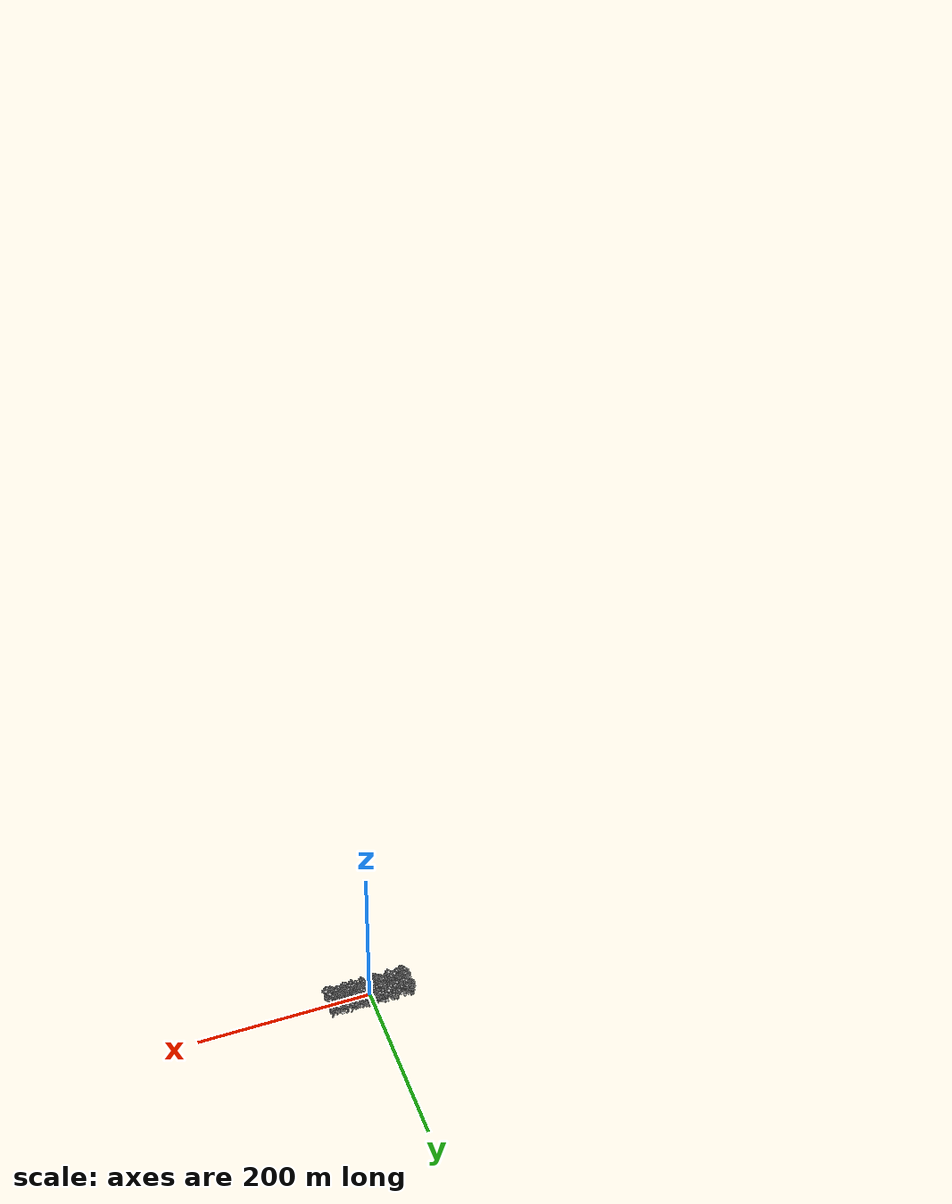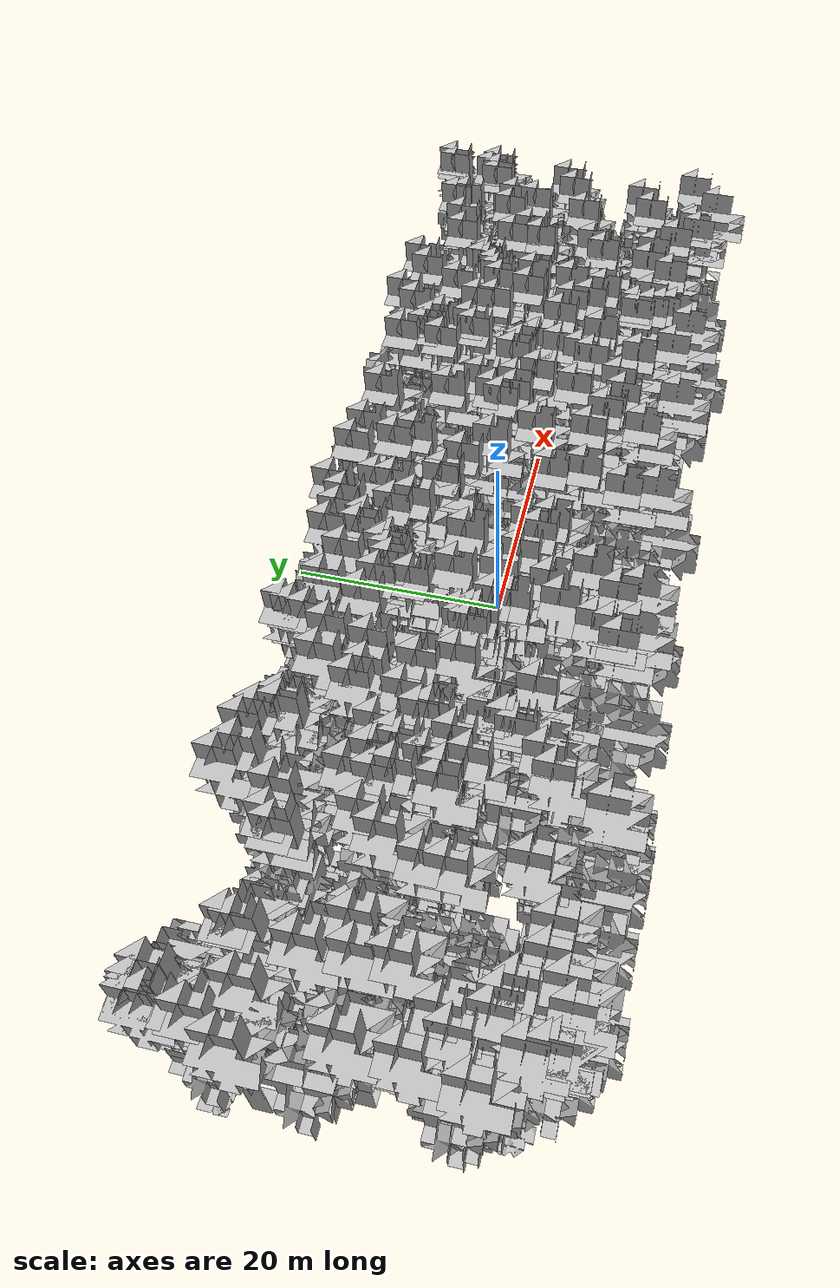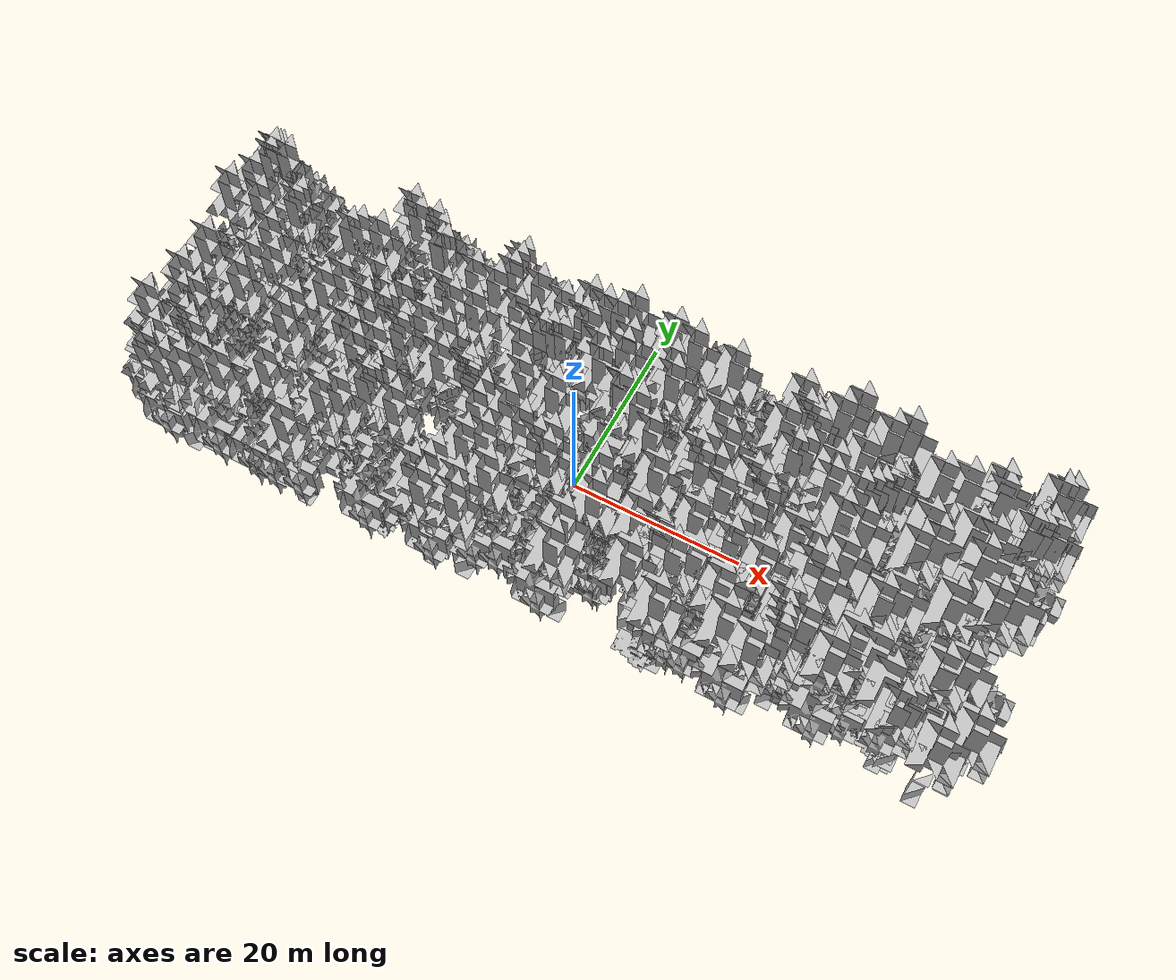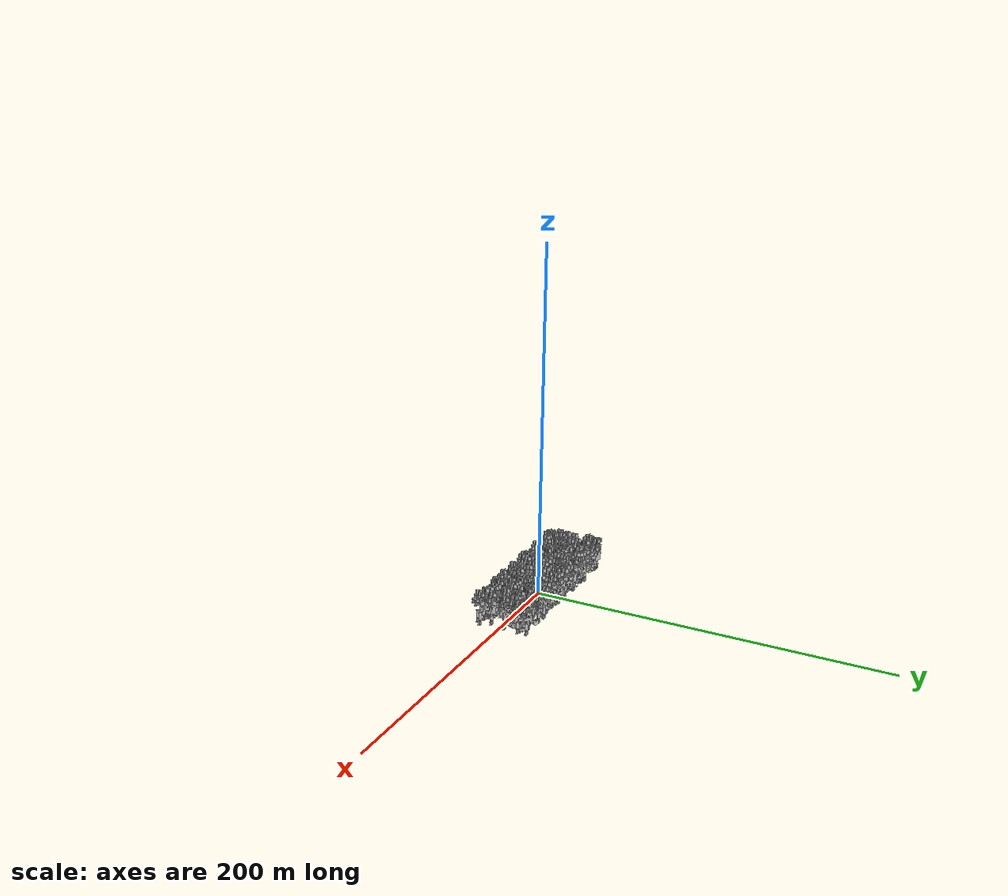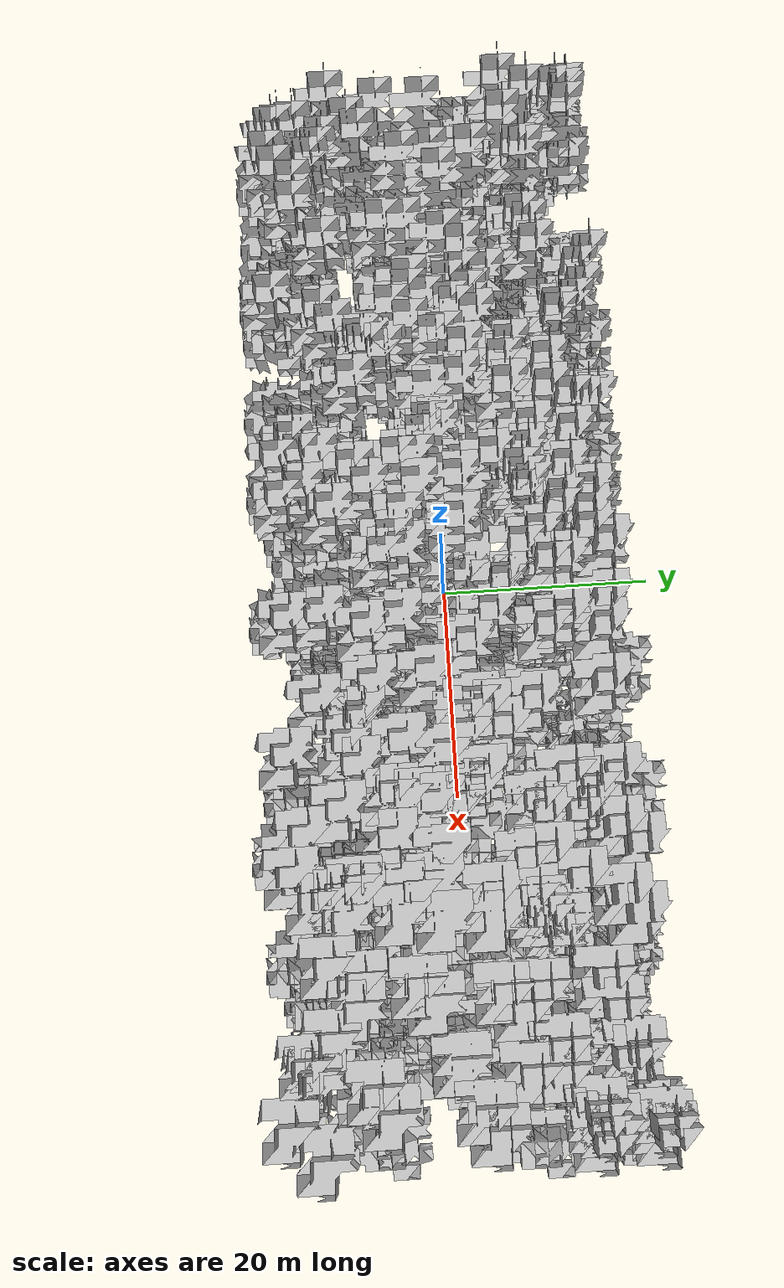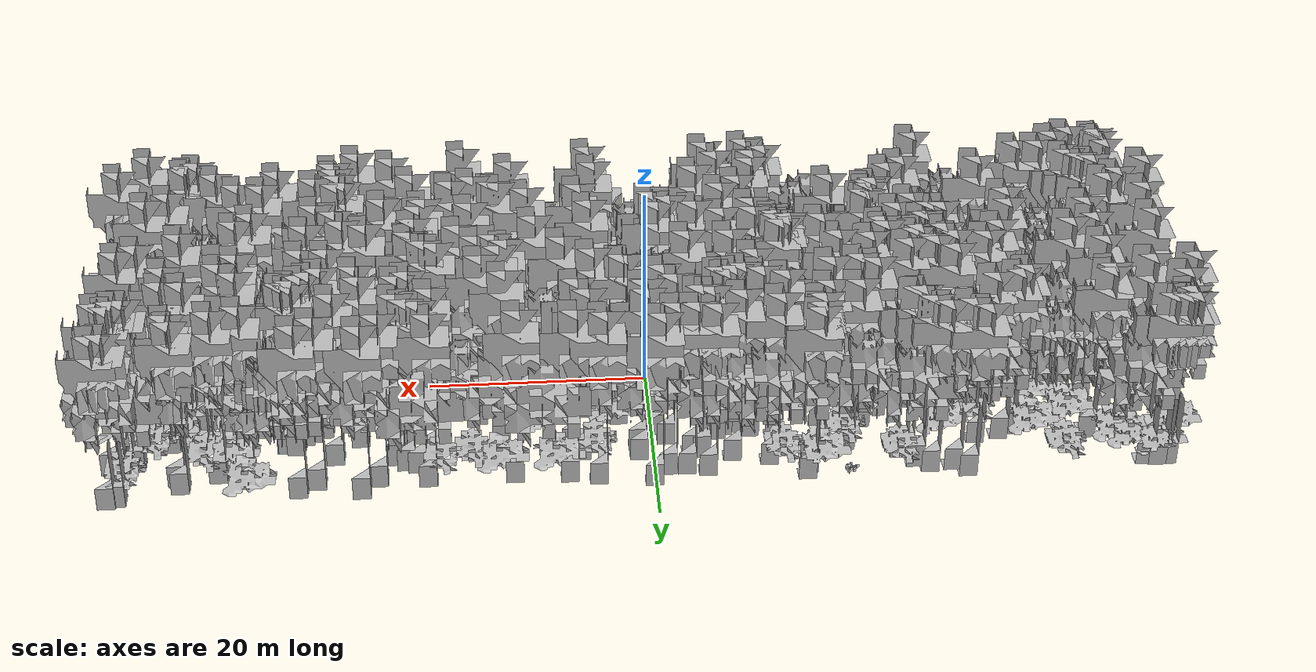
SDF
<sdf version="1.7">
    <world name="default">
        <plugin name="mrs_gazebo_static_transform_republisher_plugin" filename="libMrsGazeboCommonResources_StaticTransformRepublisher.so"/>
        <spherical_coordinates>
            <surface_model>EARTH_WGS84</surface_model>
            <latitude_deg>47.3977</latitude_deg>
            <longitude_deg>8.54559</longitude_deg>
            <elevation>0</elevation>
            <heading_deg>0</heading_deg>
        </spherical_coordinates>
        <physics name="default_physics" default="0" type="ode">
            <ode>
                <solver>
                    <type>quick</type>
                    <iters>10</iters>
                    <sor>1.3</sor>
                    <use_dynamic_moi_rescaling>0</use_dynamic_moi_rescaling>
                </solver>
                <constraints>
                    <cfm>0</cfm>
                    <erp>0.2</erp>
                    <contact_max_correcting_vel>1000</contact_max_correcting_vel>
                    <contact_surface_layer>0.001</contact_surface_layer>
                </constraints>
            </ode>
            <max_step_size>0.004</max_step_size>
            <real_time_factor>1</real_time_factor>
            <real_time_update_rate>250</real_time_update_rate>
        </physics>
        <scene>
            <shadows>0</shadows>
            <ambient>0.4 0.4 0.4 1</ambient>
            <background>0.7 0.7 0.7 1</background>
        </scene>
        <light name="sun" type="directional">
            <pose>0 0 1000 0.4 0.2 0</pose>
            <diffuse>1 1 1 1</diffuse>
            <specular>0.6 0.6 0.6 1</specular>
            <direction>0.1 0.1 -0.9</direction>
            <attenuation>
                <range>20</range>
                <constant>0.5</constant>
                <linear>0.01</linear>
                <quadratic>0.001</quadratic>
            </attenuation>
            <cast_shadows>1</cast_shadows>
            <spot>
                <inner_angle>0</inner_angle>
                <outer_angle>0</outer_angle>
                <falloff>0</falloff>
            </spot>
        </light>
        <model name="ground_plane">
            <static>1</static>
            <link name="link">
                <collision name="collision">
                    <pose>-50 0 0 0 -0 0</pose>
                    <geometry>
                        <plane>
                            <normal>0 0 1</normal>
                            <size>100 100</size>
                        </plane>
                    </geometry>
                    <surface>
                        <contact>
                            <ode>
                                <min_depth>0.01</min_depth>
                                <max_vel>0</max_vel>
                            </ode>
                        </contact>
                        <friction>
                            <ode/>
                            <torsional>
                                <ode/>
                            </torsional>
                        </friction>
                        <bounce/>
                    </surface>
                    <max_contacts>10</max_contacts>
                </collision>
                <visual name="grass">
                    <pose>0 0 0 0 -0 0</pose>
                    <cast_shadows>0</cast_shadows>
                    <geometry>
                        <mesh>
                            <scale>0.5814285714285714 0.18142857142857144 0.1</scale>
                            <uri>file://grass_plane/meshes/grass_plane.dae</uri>
                        </mesh>
                    </geometry>
                </visual>
                <self_collide>0</self_collide>
                <enable_wind>0</enable_wind>
                <kinematic>0</kinematic>
            </link>
        </model>
        <model name="the_void">
            <static>1</static>
            <link name="link">
                <pose>0 0 0.1 0 -0 0</pose>
                <visual name="the_void">
                    <pose>0 0 2 0 -0 0</pose>
                    <geometry>
                        <sphere>
                            <radius>0.25</radius>
                        </sphere>
                    </geometry>
                    <material>
                        <script>
                            <uri>file://media/materials/scripts/Gazebo.material</uri>
                            <name>Gazebo/Black</name>
                        </script>
                    </material>
                </visual>
                <self_collide>0</self_collide>
                <enable_wind>0</enable_wind>
                <kinematic>0</kinematic>
            </link>
            <pose>-1000 -1000 0 0 -0 0</pose>
        </model>
        <gui fullscreen="0">
            <camera name="camera">
                <pose>35.1577 98.6044 40.0204 0 0.407996 -1.99761</pose>
                <view_controller>orbit</view_controller>
                <projection_type>perspective</projection_type>
            </camera>
        </gui>
        <plugin name="mrs_gazebo_rviz_cam_synchronizer" filename="libMrsGazeboCommonResources_RvizCameraSynchronizer.so">
            <target_frame_id>gazebo_user_camera</target_frame_id>
            <world_origin_frame_id>uav1/gps_origin</world_origin_frame_id>
            <frame_to_follow>uav1</frame_to_follow>
        </plugin>
        <gravity>0 0 -9.8066</gravity>
        <magnetic_field>6e-06 2.3e-05 -4.2e-05</magnetic_field>
        <atmosphere type="adiabatic"/>
        <wind/>
        <model name="Tree 0">
            <static>1</static>
            <pose>11.952881547785147 6.665123771803703 0 1.57079 -0 0</pose>
            <link name="link">
                <pose>0 0 0 0 -0 0</pose>
                <collision name="collision">
                    <geometry>
                        <mesh>
                            <scale>3.5 5 3.5</scale>
                            <uri>model://tree_2/meshes/tree_2.obj</uri>
                        </mesh>
                    </geometry>
                    <max_contacts>10</max_contacts>
                    <surface>
                        <contact>
                            <ode/>
                        </contact>
                        <bounce/>
                        <friction>
                            <torsional>
                                <ode/>
                            </torsional>
                            <ode/>
                        </friction>
                    </surface>
                </collision>
                <visual name="visual">
                    <geometry>
                        <mesh>
                            <scale>3.5 5 3.5</scale>
                            <uri>model://tree_2/meshes/tree_2.obj</uri>
                        </mesh>
                    </geometry>
                </visual>
                <self_collide>0</self_collide>
                <enable_wind>0</enable_wind>
                <kinematic>0</kinematic>
            </link>
        </model>
        <model name="Tree 1">
            <static>1</static>
            <pose>13.975722320561026 12.785778803555374 0 1.57079 -0 0</pose>
            <link name="link">
                <pose>0 0 0 0 -0 0</pose>
                <collision name="collision">
                    <geometry>
                        <mesh>
                            <scale>3.5 5 3.5</scale>
                            <uri>model://tree_2/meshes/tree_2.obj</uri>
                        </mesh>
                    </geometry>
                    <max_contacts>10</max_contacts>
                    <surface>
                        <contact>
                            <ode/>
                        </contact>
                        <bounce/>
                        <friction>
                            <torsional>
                                <ode/>
                            </torsional>
                            <ode/>
                        </friction>
                    </surface>
                </collision>
                <visual name="visual">
                    <geometry>
                        <mesh>
                            <scale>3.5 5 3.5</scale>
                            <uri>model://tree_2/meshes/tree_2.obj</uri>
                        </mesh>
                    </geometry>
                </visual>
                <self_collide>0</self_collide>
                <enable_wind>0</enable_wind>
                <kinematic>0</kinematic>
            </link>
        </model>
        <model name="Tree 2">
            <static>1</static>
            <pose>3.012863394360771 5.411179825811907 0 1.57079 -0 0</pose>
            <link name="link">
                <pose>0 0 0 0 -0 0</pose>
                <collision name="collision">
                    <geometry>
                        <mesh>
                            <scale>3 2 3</scale>
                            <uri>model://tree_3/meshes/tree_3.obj</uri>
                        </mesh>
                    </geometry>
                    <max_contacts>10</max_contacts>
                    <surface>
                        <contact>
                            <ode/>
                        </contact>
                        <bounce/>
                        <friction>
                            <torsional>
                                <ode/>
                            </torsional>
                            <ode/>
                        </friction>
                    </surface>
                </collision>
                <visual name="visual">
                    <geometry>
                        <mesh>
                            <scale>3 2 3</scale>
                            <uri>model://tree_3/meshes/tree_3.obj</uri>
                        </mesh>
                    </geometry>
                </visual>
                <self_collide>0</self_collide>
                <enable_wind>0</enable_wind>
                <kinematic>0</kinematic>
            </link>
        </model>
        <model name="Tree 3">
            <static>1</static>
            <pose>28.816578307401187 -12.275336711005055 0 1.57079 -0 0</pose>
            <link name="link">
                <pose>0 0 0 0 -0 0</pose>
                <collision name="collision">
                    <geometry>
                        <mesh>
                            <scale>3.5 5 3.5</scale>
                            <uri>model://tree_9/meshes/tree_9.obj</uri>
                        </mesh>
                    </geometry>
                    <max_contacts>10</max_contacts>
                    <surface>
                        <contact>
                            <ode/>
                        </contact>
                        <bounce/>
                        <friction>
                            <torsional>
                                <ode/>
                            </torsional>
                            <ode/>
                        </friction>
                    </surface>
                </collision>
                <visual name="visual">
                    <geometry>
                        <mesh>
                            <scale>3.5 5 3.5</scale>
                            <uri>model://tree_9/meshes/tree_9.obj</uri>
                        </mesh>
                    </geometry>
                </visual>
                <self_collide>0</self_collide>
                <enable_wind>0</enable_wind>
                <kinematic>0</kinematic>
            </link>
        </model>
        <model name="Tree 4">
            <static>1</static>
            <pose>41.12326072533456 7.020379282527806 0 1.57079 -0 0</pose>
            <link name="link">
                <pose>0 0 0 0 -0 0</pose>
                <collision name="collision">
                    <geometry>
                        <mesh>
                            <scale>3.5 5 3.5</scale>
                            <uri>model://tree_9/meshes/tree_9.obj</uri>
                        </mesh>
                    </geometry>
                    <max_contacts>10</max_contacts>
                    <surface>
                        <contact>
                            <ode/>
                        </contact>
                        <bounce/>
                        <friction>
                            <torsional>
                                <ode/>
                            </torsional>
                            <ode/>
                        </friction>
                    </surface>
                </collision>
                <visual name="visual">
                    <geometry>
                        <mesh>
                            <scale>3.5 5 3.5</scale>
                            <uri>model://tree_9/meshes/tree_9.obj</uri>
                        </mesh>
                    </geometry>
                </visual>
                <self_collide>0</self_collide>
                <enable_wind>0</enable_wind>
                <kinematic>0</kinematic>
            </link>
        </model>
        <model name="Tree 5">
            <static>1</static>
            <pose>19.629208823579546 -1.654639189703154 0 1.57079 -0 0</pose>
            <link name="link">
                <pose>0 0 0 0 -0 0</pose>
                <collision name="collision">
                    <geometry>
                        <mesh>
                            <scale>3.5 5 3.5</scale>
                            <uri>model://tree_2/meshes/tree_2.obj</uri>
                        </mesh>
                    </geometry>
                    <max_contacts>10</max_contacts>
                    <surface>
                        <contact>
                            <ode/>
                        </contact>
                        <bounce/>
                        <friction>
                            <torsional>
                                <ode/>
                            </torsional>
                            <ode/>
                        </friction>
                    </surface>
                </collision>
                <visual name="visual">
                    <geometry>
                        <mesh>
                            <scale>3.5 5 3.5</scale>
                            <uri>model://tree_2/meshes/tree_2.obj</uri>
                        </mesh>
                    </geometry>
                </visual>
                <self_collide>0</self_collide>
                <enable_wind>0</enable_wind>
                <kinematic>0</kinematic>
            </link>
        </model>
        <model name="Tree 6">
            <static>1</static>
            <pose>-14.847587677390472 -13.198591773036949 0 1.57079 -0 0</pose>
            <link name="link">
                <pose>0 0 0 0 -0 0</pose>
                <collision name="collision">
                    <geometry>
                        <mesh>
                            <scale>3.5 5 3.5</scale>
                            <uri>model://tree_2/meshes/tree_2.obj</uri>
                        </mesh>
                    </geometry>
                    <max_contacts>10</max_contacts>
                    <surface>
                        <contact>
                            <ode/>
                        </contact>
                        <bounce/>
                        <friction>
                            <torsional>
                                <ode/>
                            </torsional>
                            <ode/>
                        </friction>
                    </surface>
                </collision>
                <visual name="visual">
                    <geometry>
                        <mesh>
                            <scale>3.5 5 3.5</scale>
                            <uri>model://tree_2/meshes/tree_2.obj</uri>
                        </mesh>
                    </geometry>
                </visual>
                <self_collide>0</self_collide>
                <enable_wind>0</enable_wind>
                <kinematic>0</kinematic>
            </link>
        </model>
        <model name="Tree 7">
            <static>1</static>
            <pose>1.0229062971765188 10.498995692659502 0 1.57079 -0 0</pose>
            <link name="link">
                <pose>0 0 0 0 -0 0</pose>
                <collision name="collision">
                    <geometry>
                        <mesh>
                            <scale>3.5 5 3.5</scale>
                            <uri>model://tree_9/meshes/tree_9.obj</uri>
                        </mesh>
                    </geometry>
                    <max_contacts>10</max_contacts>
                    <surface>
                        <contact>
                            <ode/>
                        </contact>
                        <bounce/>
                        <friction>
                            <torsional>
                                <ode/>
                            </torsional>
                            <ode/>
                        </friction>
                    </surface>
                </collision>
                <visual name="visual">
                    <geometry>
                        <mesh>
                            <scale>3.5 5 3.5</scale>
                            <uri>model://tree_9/meshes/tree_9.obj</uri>
                        </mesh>
                    </geometry>
                </visual>
                <self_collide>0</self_collide>
                <enable_wind>0</enable_wind>
                <kinematic>0</kinematic>
            </link>
        </model>
        <model name="Tree 8">
            <static>1</static>
            <pose>-29.84656426832045 3.0639683747914432 0 1.57079 -0 0</pose>
            <link name="link">
                <pose>0 0 0 0 -0 0</pose>
                <collision name="collision">
                    <geometry>
                        <mesh>
                            <scale>3.5 5 3.5</scale>
                            <uri>model://tree_9/meshes/tree_9.obj</uri>
                        </mesh>
                    </geometry>
                    <max_contacts>10</max_contacts>
                    <surface>
                        <contact>
                            <ode/>
                        </contact>
                        <bounce/>
                        <friction>
                            <torsional>
                                <ode/>
                            </torsional>
                            <ode/>
                        </friction>
                    </surface>
                </collision>
                <visual name="visual">
                    <geometry>
                        <mesh>
                            <scale>3.5 5 3.5</scale>
                            <uri>model://tree_9/meshes/tree_9.obj</uri>
                        </mesh>
                    </geometry>
                </visual>
                <self_collide>0</self_collide>
                <enable_wind>0</enable_wind>
                <kinematic>0</kinematic>
            </link>
        </model>
        <model name="Tree 9">
            <static>1</static>
            <pose>19.874703441783964 13.270476676927117 0 1.57079 -0 0</pose>
            <link name="link">
                <pose>0 0 0 0 -0 0</pose>
                <collision name="collision">
                    <geometry>
                        <mesh>
                            <scale>3.5 5 3.5</scale>
                            <uri>model://tree_9/meshes/tree_9.obj</uri>
                        </mesh>
                    </geometry>
                    <max_contacts>10</max_contacts>
                    <surface>
                        <contact>
                            <ode/>
                        </contact>
                        <bounce/>
                        <friction>
                            <torsional>
                                <ode/>
                            </torsional>
                            <ode/>
                        </friction>
                    </surface>
                </collision>
                <visual name="visual">
                    <geometry>
                        <mesh>
                            <scale>3.5 5 3.5</scale>
                            <uri>model://tree_9/meshes/tree_9.obj</uri>
                        </mesh>
                    </geometry>
                </visual>
                <self_collide>0</self_collide>
                <enable_wind>0</enable_wind>
                <kinematic>0</kinematic>
            </link>
        </model>
        <model name="Tree 10">
            <static>1</static>
            <pose>-46.06153211407644 -10.663010434127743 0 1.57079 -0 0</pose>
            <link name="link">
                <pose>0 0 0 0 -0 0</pose>
                <collision name="collision">
                    <geometry>
                        <mesh>
                            <scale>4 2.5 4</scale>
                            <uri>model://tree_1/meshes/tree_1.obj</uri>
                        </mesh>
                    </geometry>
                    <max_contacts>10</max_contacts>
                    <surface>
                        <contact>
                            <ode/>
                        </contact>
                        <bounce/>
                        <friction>
                            <torsional>
                                <ode/>
                            </torsional>
                            <ode/>
                        </friction>
                    </surface>
                </collision>
                <visual name="visual">
                    <geometry>
                        <mesh>
                            <scale>4 2.5 4</scale>
                            <uri>model://tree_1/meshes/tree_1.obj</uri>
                        </mesh>
                    </geometry>
                </visual>
                <self_collide>0</self_collide>
                <enable_wind>0</enable_wind>
                <kinematic>0</kinematic>
            </link>
        </model>
        <model name="Tree 11">
            <static>1</static>
            <pose>-23.579800557243864 13.033755233226284 0 1.57079 -0 0</pose>
            <link name="link">
                <pose>0 0 0 0 -0 0</pose>
                <collision name="collision">
                    <geometry>
                        <mesh>
                            <scale>3.5 5 3.5</scale>
                            <uri>model://tree_9/meshes/tree_9.obj</uri>
                        </mesh>
                    </geometry>
                    <max_contacts>10</max_contacts>
                    <surface>
                        <contact>
                            <ode/>
                        </contact>
                        <bounce/>
                        <friction>
                            <torsional>
                                <ode/>
                            </torsional>
                            <ode/>
                        </friction>
                    </surface>
                </collision>
                <visual name="visual">
                    <geometry>
                        <mesh>
                            <scale>3.5 5 3.5</scale>
                            <uri>model://tree_9/meshes/tree_9.obj</uri>
                        </mesh>
                    </geometry>
                </visual>
                <self_collide>0</self_collide>
                <enable_wind>0</enable_wind>
                <kinematic>0</kinematic>
            </link>
        </model>
        <model name="Tree 12">
            <static>1</static>
            <pose>-19.75647493247449 -4.691721239419238 0 1.57079 -0 0</pose>
            <link name="link">
                <pose>0 0 0 0 -0 0</pose>
                <collision name="collision">
                    <geometry>
                        <mesh>
                            <scale>3.5 5 3.5</scale>
                            <uri>model://tree_9/meshes/tree_9.obj</uri>
                        </mesh>
                    </geometry>
                    <max_contacts>10</max_contacts>
                    <surface>
                        <contact>
                            <ode/>
                        </contact>
                        <bounce/>
                        <friction>
                            <torsional>
                                <ode/>
                            </torsional>
                            <ode/>
                        </friction>
                    </surface>
                </collision>
                <visual name="visual">
                    <geometry>
                        <mesh>
                            <scale>3.5 5 3.5</scale>
                            <uri>model://tree_9/meshes/tree_9.obj</uri>
                        </mesh>
                    </geometry>
                </visual>
                <self_collide>0</self_collide>
                <enable_wind>0</enable_wind>
                <kinematic>0</kinematic>
            </link>
        </model>
        <model name="Tree 13">
            <static>1</static>
            <pose>13.647802342299308 -6.039625585213269 0 1.57079 -0 0</pose>
            <link name="link">
                <pose>0 0 0 0 -0 0</pose>
                <collision name="collision">
                    <geometry>
                        <mesh>
                            <scale>3.5 5 3.5</scale>
                            <uri>model://tree_2/meshes/tree_2.obj</uri>
                        </mesh>
                    </geometry>
                    <max_contacts>10</max_contacts>
                    <surface>
                        <contact>
                            <ode/>
                        </contact>
                        <bounce/>
                        <friction>
                            <torsional>
                                <ode/>
                            </torsional>
                            <ode/>
                        </friction>
                    </surface>
                </collision>
                <visual name="visual">
                    <geometry>
                        <mesh>
                            <scale>3.5 5 3.5</scale>
                            <uri>model://tree_2/meshes/tree_2.obj</uri>
                        </mesh>
                    </geometry>
                </visual>
                <self_collide>0</self_collide>
                <enable_wind>0</enable_wind>
                <kinematic>0</kinematic>
            </link>
        </model>
        <model name="Tree 14">
            <static>1</static>
            <pose>-39.050472410012674 -14.05682247275237 0 1.57079 -0 0</pose>
            <link name="link">
                <pose>0 0 0 0 -0 0</pose>
                <collision name="collision">
                    <geometry>
                        <mesh>
                            <scale>3.5 5 3.5</scale>
                            <uri>model://tree_9/meshes/tree_9.obj</uri>
                        </mesh>
                    </geometry>
                    <max_contacts>10</max_contacts>
                    <surface>
                        <contact>
                            <ode/>
                        </contact>
                        <bounce/>
                        <friction>
                            <torsional>
                                <ode/>
                            </torsional>
                            <ode/>
                        </friction>
                    </surface>
                </collision>
                <visual name="visual">
                    <geometry>
                        <mesh>
                            <scale>3.5 5 3.5</scale>
                            <uri>model://tree_9/meshes/tree_9.obj</uri>
                        </mesh>
                    </geometry>
                </visual>
                <self_collide>0</self_collide>
                <enable_wind>0</enable_wind>
                <kinematic>0</kinematic>
            </link>
        </model>
        <model name="Tree 15">
            <static>1</static>
            <pose>-12.046379397283076 13.599554694582526 0 1.57079 -0 0</pose>
            <link name="link">
                <pose>0 0 0 0 -0 0</pose>
                <collision name="collision">
                    <geometry>
                        <mesh>
                            <scale>3.5 5 3.5</scale>
                            <uri>model://tree_2/meshes/tree_2.obj</uri>
                        </mesh>
                    </geometry>
                    <max_contacts>10</max_contacts>
                    <surface>
                        <contact>
                            <ode/>
                        </contact>
                        <bounce/>
                        <friction>
                            <torsional>
                                <ode/>
                            </torsional>
                            <ode/>
                        </friction>
                    </surface>
                </collision>
                <visual name="visual">
                    <geometry>
                        <mesh>
                            <scale>3.5 5 3.5</scale>
                            <uri>model://tree_2/meshes/tree_2.obj</uri>
                        </mesh>
                    </geometry>
                </visual>
                <self_collide>0</self_collide>
                <enable_wind>0</enable_wind>
                <kinematic>0</kinematic>
            </link>
        </model>
        <model name="Tree 16">
            <static>1</static>
            <pose>-29.650979372544978 -3.697761400649698 0 1.57079 -0 0</pose>
            <link name="link">
                <pose>0 0 0 0 -0 0</pose>
                <collision name="collision">
                    <geometry>
                        <mesh>
                            <scale>3.5 5 3.5</scale>
                            <uri>model://tree_2/meshes/tree_2.obj</uri>
                        </mesh>
                    </geometry>
                    <max_contacts>10</max_contacts>
                    <surface>
                        <contact>
                            <ode/>
                        </contact>
                        <bounce/>
                        <friction>
                            <torsional>
                                <ode/>
                            </torsional>
                            <ode/>
                        </friction>
                    </surface>
                </collision>
                <visual name="visual">
                    <geometry>
                        <mesh>
                            <scale>3.5 5 3.5</scale>
                            <uri>model://tree_2/meshes/tree_2.obj</uri>
                        </mesh>
                    </geometry>
                </visual>
                <self_collide>0</self_collide>
                <enable_wind>0</enable_wind>
                <kinematic>0</kinematic>
            </link>
        </model>
        <model name="Tree 17">
            <static>1</static>
            <pose>38.18825486041709 4.283640740840816 0 1.57079 -0 0</pose>
            <link name="link">
                <pose>0 0 0 0 -0 0</pose>
                <collision name="collision">
                    <geometry>
                        <mesh>
                            <scale>3.5 5 3.5</scale>
                            <uri>model://tree_9/meshes/tree_9.obj</uri>
                        </mesh>
                    </geometry>
                    <max_contacts>10</max_contacts>
                    <surface>
                        <contact>
                            <ode/>
                        </contact>
                        <bounce/>
                        <friction>
                            <torsional>
                                <ode/>
                            </torsional>
                            <ode/>
                        </friction>
                    </surface>
                </collision>
                <visual name="visual">
                    <geometry>
                        <mesh>
                            <scale>3.5 5 3.5</scale>
                            <uri>model://tree_9/meshes/tree_9.obj</uri>
                        </mesh>
                    </geometry>
                </visual>
                <self_collide>0</self_collide>
                <enable_wind>0</enable_wind>
                <kinematic>0</kinematic>
            </link>
        </model>
        <model name="Tree 18">
            <static>1</static>
            <pose>-11.32614592529736 8.28942585479085 0 1.57079 -0 0</pose>
            <link name="link">
                <pose>0 0 0 0 -0 0</pose>
                <collision name="collision">
                    <geometry>
                        <mesh>
                            <scale>3.5 5 3.5</scale>
                            <uri>model://tree_9/meshes/tree_9.obj</uri>
                        </mesh>
                    </geometry>
                    <max_contacts>10</max_contacts>
                    <surface>
                        <contact>
                            <ode/>
                        </contact>
                        <bounce/>
                        <friction>
                            <torsional>
                                <ode/>
                            </torsional>
                            <ode/>
                        </friction>
                    </surface>
                </collision>
                <visual name="visual">
                    <geometry>
                        <mesh>
                            <scale>3.5 5 3.5</scale>
                            <uri>model://tree_9/meshes/tree_9.obj</uri>
                        </mesh>
                    </geometry>
                </visual>
                <self_collide>0</self_collide>
                <enable_wind>0</enable_wind>
                <kinematic>0</kinematic>
            </link>
        </model>
        <model name="Tree 19">
            <static>1</static>
            <pose>12.153450207134867 3.3413821550245935 0 1.57079 -0 0</pose>
            <link name="link">
                <pose>0 0 0 0 -0 0</pose>
                <collision name="collision">
                    <geometry>
                        <mesh>
                            <scale>3.5 5 3.5</scale>
                            <uri>model://tree_2/meshes/tree_2.obj</uri>
                        </mesh>
                    </geometry>
                    <max_contacts>10</max_contacts>
                    <surface>
                        <contact>
                            <ode/>
                        </contact>
                        <bounce/>
                        <friction>
                            <torsional>
                                <ode/>
                            </torsional>
                            <ode/>
                        </friction>
                    </surface>
                </collision>
                <visual name="visual">
                    <geometry>
                        <mesh>
                            <scale>3.5 5 3.5</scale>
                            <uri>model://tree_2/meshes/tree_2.obj</uri>
                        </mesh>
                    </geometry>
                </visual>
                <self_collide>0</self_collide>
                <enable_wind>0</enable_wind>
                <kinematic>0</kinematic>
            </link>
        </model>
        <model name="Tree 20">
            <static>1</static>
            <pose>-27.59546562882719 5.002111572936375 0 1.57079 -0 0</pose>
            <link name="link">
                <pose>0 0 0 0 -0 0</pose>
                <collision name="collision">
                    <geometry>
                        <mesh>
                            <scale>3 2 3</scale>
                            <uri>model://tree_3/meshes/tree_3.obj</uri>
                        </mesh>
                    </geometry>
                    <max_contacts>10</max_contacts>
                    <surface>
                        <contact>
                            <ode/>
                        </contact>
                        <bounce/>
                        <friction>
                            <torsional>
                                <ode/>
                            </torsional>
                            <ode/>
                        </friction>
                    </surface>
                </collision>
                <visual name="visual">
                    <geometry>
                        <mesh>
                            <scale>3 2 3</scale>
                            <uri>model://tree_3/meshes/tree_3.obj</uri>
                        </mesh>
                    </geometry>
                </visual>
                <self_collide>0</self_collide>
                <enable_wind>0</enable_wind>
                <kinematic>0</kinematic>
            </link>
        </model>
        <model name="Tree 21">
            <static>1</static>
            <pose>6.1425054638443015 10.204391214588146 0 1.57079 -0 0</pose>
            <link name="link">
                <pose>0 0 0 0 -0 0</pose>
                <collision name="collision">
                    <geometry>
                        <mesh>
                            <scale>3.5 5 3.5</scale>
                            <uri>model://tree_9/meshes/tree_9.obj</uri>
                        </mesh>
                    </geometry>
                    <max_contacts>10</max_contacts>
                    <surface>
                        <contact>
                            <ode/>
                        </contact>
                        <bounce/>
                        <friction>
                            <torsional>
                                <ode/>
                            </torsional>
                            <ode/>
                        </friction>
                    </surface>
                </collision>
                <visual name="visual">
                    <geometry>
                        <mesh>
                            <scale>3.5 5 3.5</scale>
                            <uri>model://tree_9/meshes/tree_9.obj</uri>
                        </mesh>
                    </geometry>
                </visual>
                <self_collide>0</self_collide>
                <enable_wind>0</enable_wind>
                <kinematic>0</kinematic>
            </link>
        </model>
        <model name="Tree 22">
            <static>1</static>
            <pose>40.009840931547984 -12.061171340189158 0 1.57079 -0 0</pose>
            <link name="link">
                <pose>0 0 0 0 -0 0</pose>
                <collision name="collision">
                    <geometry>
                        <mesh>
                            <scale>3 2 3</scale>
                            <uri>model://tree_3/meshes/tree_3.obj</uri>
                        </mesh>
                    </geometry>
                    <max_contacts>10</max_contacts>
                    <surface>
                        <contact>
                            <ode/>
                        </contact>
                        <bounce/>
                        <friction>
                            <torsional>
                                <ode/>
                            </torsional>
                            <ode/>
                        </friction>
                    </surface>
                </collision>
                <visual name="visual">
                    <geometry>
                        <mesh>
                            <scale>3 2 3</scale>
                            <uri>model://tree_3/meshes/tree_3.obj</uri>
                        </mesh>
                    </geometry>
                </visual>
                <self_collide>0</self_collide>
                <enable_wind>0</enable_wind>
                <kinematic>0</kinematic>
            </link>
        </model>
        <model name="Tree 23">
            <static>1</static>
            <pose>-24.41843978336981 7.7211221189544474 0 1.57079 -0 0</pose>
            <link name="link">
                <pose>0 0 0 0 -0 0</pose>
                <collision name="collision">
                    <geometry>
                        <mesh>
                            <scale>3.5 5 3.5</scale>
                            <uri>model://tree_2/meshes/tree_2.obj</uri>
                        </mesh>
                    </geometry>
                    <max_contacts>10</max_contacts>
                    <surface>
                        <contact>
                            <ode/>
                        </contact>
                        <bounce/>
                        <friction>
                            <torsional>
                                <ode/>
                            </torsional>
                            <ode/>
                        </friction>
                    </surface>
                </collision>
                <visual name="visual">
                    <geometry>
                        <mesh>
                            <scale>3.5 5 3.5</scale>
                            <uri>model://tree_2/meshes/tree_2.obj</uri>
                        </mesh>
                    </geometry>
                </visual>
                <self_collide>0</self_collide>
                <enable_wind>0</enable_wind>
                <kinematic>0</kinematic>
            </link>
        </model>
        <model name="Tree 24">
            <static>1</static>
            <pose>-41.42882143700616 -6.527373647861509 0 1.57079 -0 0</pose>
            <link name="link">
                <pose>0 0 0 0 -0 0</pose>
                <collision name="collision">
                    <geometry>
                        <mesh>
                            <scale>3.5 5 3.5</scale>
                            <uri>model://tree_2/meshes/tree_2.obj</uri>
                        </mesh>
                    </geometry>
                    <max_contacts>10</max_contacts>
                    <surface>
                        <contact>
                            <ode/>
                        </contact>
                        <bounce/>
                        <friction>
                            <torsional>
                                <ode/>
                            </torsional>
                            <ode/>
                        </friction>
                    </surface>
                </collision>
                <visual name="visual">
                    <geometry>
                        <mesh>
                            <scale>3.5 5 3.5</scale>
                            <uri>model://tree_2/meshes/tree_2.obj</uri>
                        </mesh>
                    </geometry>
                </visual>
                <self_collide>0</self_collide>
                <enable_wind>0</enable_wind>
                <kinematic>0</kinematic>
            </link>
        </model>
        <model name="Tree 25">
            <static>1</static>
            <pose>12.189049988500479 13.133916527196217 0 1.57079 -0 0</pose>
            <link name="link">
                <pose>0 0 0 0 -0 0</pose>
                <collision name="collision">
                    <geometry>
                        <mesh>
                            <scale>3.5 5 3.5</scale>
                            <uri>model://tree_9/meshes/tree_9.obj</uri>
                        </mesh>
                    </geometry>
                    <max_contacts>10</max_contacts>
                    <surface>
                        <contact>
                            <ode/>
                        </contact>
                        <bounce/>
                        <friction>
                            <torsional>
                                <ode/>
                            </torsional>
                            <ode/>
                        </friction>
                    </surface>
                </collision>
                <visual name="visual">
                    <geometry>
                        <mesh>
                            <scale>3.5 5 3.5</scale>
                            <uri>model://tree_9/meshes/tree_9.obj</uri>
                        </mesh>
                    </geometry>
                </visual>
                <self_collide>0</self_collide>
                <enable_wind>0</enable_wind>
                <kinematic>0</kinematic>
            </link>
        </model>
        <model name="Tree 26">
            <static>1</static>
            <pose>-31.216376603396792 1.3551016047219555 0 1.57079 -0 0</pose>
            <link name="link">
                <pose>0 0 0 0 -0 0</pose>
                <collision name="collision">
                    <geometry>
                        <mesh>
                            <scale>3.5 5 3.5</scale>
                            <uri>model://tree_9/meshes/tree_9.obj</uri>
                        </mesh>
                    </geometry>
                    <max_contacts>10</max_contacts>
                    <surface>
                        <contact>
                            <ode/>
                        </contact>
                        <bounce/>
                        <friction>
                            <torsional>
                                <ode/>
                            </torsional>
                            <ode/>
                        </friction>
                    </surface>
                </collision>
                <visual name="visual">
                    <geometry>
                        <mesh>
                            <scale>3.5 5 3.5</scale>
                            <uri>model://tree_9/meshes/tree_9.obj</uri>
                        </mesh>
                    </geometry>
                </visual>
                <self_collide>0</self_collide>
                <enable_wind>0</enable_wind>
                <kinematic>0</kinematic>
            </link>
        </model>
        <model name="Tree 27">
            <static>1</static>
            <pose>-0.704515399992232 -3.799176612060874 0 1.57079 -0 0</pose>
            <link name="link">
                <pose>0 0 0 0 -0 0</pose>
                <collision name="collision">
                    <geometry>
                        <mesh>
                            <scale>3.5 5 3.5</scale>
                            <uri>model://tree_2/meshes/tree_2.obj</uri>
                        </mesh>
                    </geometry>
                    <max_contacts>10</max_contacts>
                    <surface>
                        <contact>
                            <ode/>
                        </contact>
                        <bounce/>
                        <friction>
                            <torsional>
                                <ode/>
                            </torsional>
                            <ode/>
                        </friction>
                    </surface>
                </collision>
                <visual name="visual">
                    <geometry>
                        <mesh>
                            <scale>3.5 5 3.5</scale>
                            <uri>model://tree_2/meshes/tree_2.obj</uri>
                        </mesh>
                    </geometry>
                </visual>
                <self_collide>0</self_collide>
                <enable_wind>0</enable_wind>
                <kinematic>0</kinematic>
            </link>
        </model>
        <model name="Tree 28">
            <static>1</static>
            <pose>-39.8316958068525 -2.0770529206406376 0 1.57079 -0 0</pose>
            <link name="link">
                <pose>0 0 0 0 -0 0</pose>
                <collision name="collision">
                    <geometry>
                        <mesh>
                            <scale>3.5 5 3.5</scale>
                            <uri>model://tree_9/meshes/tree_9.obj</uri>
                        </mesh>
                    </geometry>
                    <max_contacts>10</max_contacts>
                    <surface>
                        <contact>
                            <ode/>
                        </contact>
                        <bounce/>
                        <friction>
                            <torsional>
                                <ode/>
                            </torsional>
                            <ode/>
                        </friction>
                    </surface>
                </collision>
                <visual name="visual">
                    <geometry>
                        <mesh>
                            <scale>3.5 5 3.5</scale>
                            <uri>model://tree_9/meshes/tree_9.obj</uri>
                        </mesh>
                    </geometry>
                </visual>
                <self_collide>0</self_collide>
                <enable_wind>0</enable_wind>
                <kinematic>0</kinematic>
            </link>
        </model>
        <model name="Tree 29">
            <static>1</static>
            <pose>44.93335053796652 5.789246295353244 0 1.57079 -0 0</pose>
            <link name="link">
                <pose>0 0 0 0 -0 0</pose>
                <collision name="collision">
                    <geometry>
                        <mesh>
                            <scale>3 2 3</scale>
                            <uri>model://tree_3/meshes/tree_3.obj</uri>
                        </mesh>
                    </geometry>
                    <max_contacts>10</max_contacts>
                    <surface>
                        <contact>
                            <ode/>
                        </contact>
                        <bounce/>
                        <friction>
                            <torsional>
                                <ode/>
                            </torsional>
                            <ode/>
                        </friction>
                    </surface>
                </collision>
                <visual name="visual">
                    <geometry>
                        <mesh>
                            <scale>3 2 3</scale>
                            <uri>model://tree_3/meshes/tree_3.obj</uri>
                        </mesh>
                    </geometry>
                </visual>
                <self_collide>0</self_collide>
                <enable_wind>0</enable_wind>
                <kinematic>0</kinematic>
            </link>
        </model>
        <model name="Tree 30">
            <static>1</static>
            <pose>-1.8607981483735188 -4.657562702218801 0 1.57079 -0 0</pose>
            <link name="link">
                <pose>0 0 0 0 -0 0</pose>
                <collision name="collision">
                    <geometry>
                        <mesh>
                            <scale>3.5 5 3.5</scale>
                            <uri>model://tree_9/meshes/tree_9.obj</uri>
                        </mesh>
                    </geometry>
                    <max_contacts>10</max_contacts>
                    <surface>
                        <contact>
                            <ode/>
                        </contact>
                        <bounce/>
                        <friction>
                            <torsional>
                                <ode/>
                            </torsional>
                            <ode/>
                        </friction>
                    </surface>
                </collision>
                <visual name="visual">
                    <geometry>
                        <mesh>
                            <scale>3.5 5 3.5</scale>
                            <uri>model://tree_9/meshes/tree_9.obj</uri>
                        </mesh>
                    </geometry>
                </visual>
                <self_collide>0</self_collide>
                <enable_wind>0</enable_wind>
                <kinematic>0</kinematic>
            </link>
        </model>
        <model name="Tree 31">
            <static>1</static>
            <pose>24.900806616224116 -10.793923267823647 0 1.57079 -0 0</pose>
            <link name="link">
                <pose>0 0 0 0 -0 0</pose>
                <collision name="collision">
                    <geometry>
                        <mesh>
                            <scale>3.5 5 3.5</scale>
                            <uri>model://tree_2/meshes/tree_2.obj</uri>
                        </mesh>
                    </geometry>
                    <max_contacts>10</max_contacts>
                    <surface>
                        <contact>
                            <ode/>
                        </contact>
                        <bounce/>
                        <friction>
                            <torsional>
                                <ode/>
                            </torsional>
                            <ode/>
                        </friction>
                    </surface>
                </collision>
                <visual name="visual">
                    <geometry>
                        <mesh>
                            <scale>3.5 5 3.5</scale>
                            <uri>model://tree_2/meshes/tree_2.obj</uri>
                        </mesh>
                    </geometry>
                </visual>
                <self_collide>0</self_collide>
                <enable_wind>0</enable_wind>
                <kinematic>0</kinematic>
            </link>
        </model>
        <model name="Tree 32">
            <static>1</static>
            <pose>-39.52098686057385 5.791457068551935 0 1.57079 -0 0</pose>
            <link name="link">
                <pose>0 0 0 0 -0 0</pose>
                <collision name="collision">
                    <geometry>
                        <mesh>
                            <scale>3.5 5 3.5</scale>
                            <uri>model://tree_2/meshes/tree_2.obj</uri>
                        </mesh>
                    </geometry>
                    <max_contacts>10</max_contacts>
                    <surface>
                        <contact>
                            <ode/>
                        </contact>
                        <bounce/>
                        <friction>
                            <torsional>
                                <ode/>
                            </torsional>
                            <ode/>
                        </friction>
                    </surface>
                </collision>
                <visual name="visual">
                    <geometry>
                        <mesh>
                            <scale>3.5 5 3.5</scale>
                            <uri>model://tree_2/meshes/tree_2.obj</uri>
                        </mesh>
                    </geometry>
                </visual>
                <self_collide>0</self_collide>
                <enable_wind>0</enable_wind>
                <kinematic>0</kinematic>
            </link>
        </model>
        <model name="Tree 33">
            <static>1</static>
            <pose>-25.675237100648353 5.041882957924631 0 1.57079 -0 0</pose>
            <link name="link">
                <pose>0 0 0 0 -0 0</pose>
                <collision name="collision">
                    <geometry>
                        <mesh>
                            <scale>3.5 5 3.5</scale>
                            <uri>model://tree_2/meshes/tree_2.obj</uri>
                        </mesh>
                    </geometry>
                    <max_contacts>10</max_contacts>
                    <surface>
                        <contact>
                            <ode/>
                        </contact>
                        <bounce/>
                        <friction>
                            <torsional>
                                <ode/>
                            </torsional>
                            <ode/>
                        </friction>
                    </surface>
                </collision>
                <visual name="visual">
                    <geometry>
                        <mesh>
                            <scale>3.5 5 3.5</scale>
                            <uri>model://tree_2/meshes/tree_2.obj</uri>
                        </mesh>
                    </geometry>
                </visual>
                <self_collide>0</self_collide>
                <enable_wind>0</enable_wind>
                <kinematic>0</kinematic>
            </link>
        </model>
        <model name="Tree 34">
            <static>1</static>
            <pose>-38.68039824063031 -0.27357274406901766 0 1.57079 -0 0</pose>
            <link name="link">
                <pose>0 0 0 0 -0 0</pose>
                <collision name="collision">
                    <geometry>
                        <mesh>
                            <scale>4 2.5 4</scale>
                            <uri>model://tree_1/meshes/tree_1.obj</uri>
                        </mesh>
                    </geometry>
                    <max_contacts>10</max_contacts>
                    <surface>
                        <contact>
                            <ode/>
                        </contact>
                        <bounce/>
                        <friction>
                            <torsional>
                                <ode/>
                            </torsional>
                            <ode/>
                        </friction>
                    </surface>
                </collision>
                <visual name="visual">
                    <geometry>
                        <mesh>
                            <scale>4 2.5 4</scale>
                            <uri>model://tree_1/meshes/tree_1.obj</uri>
                        </mesh>
                    </geometry>
                </visual>
                <self_collide>0</self_collide>
                <enable_wind>0</enable_wind>
                <kinematic>0</kinematic>
            </link>
        </model>
        <model name="Tree 35">
            <static>1</static>
            <pose>13.080208053278682 1.8805832757678118 0 1.57079 -0 0</pose>
            <link name="link">
                <pose>0 0 0 0 -0 0</pose>
                <collision name="collision">
                    <geometry>
                        <mesh>
                            <scale>3.5 5 3.5</scale>
                            <uri>model://tree_9/meshes/tree_9.obj</uri>
                        </mesh>
                    </geometry>
                    <max_contacts>10</max_contacts>
                    <surface>
                        <contact>
                            <ode/>
                        </contact>
                        <bounce/>
                        <friction>
                            <torsional>
                                <ode/>
                            </torsional>
                            <ode/>
                        </friction>
                    </surface>
                </collision>
                <visual name="visual">
                    <geometry>
                        <mesh>
                            <scale>3.5 5 3.5</scale>
                            <uri>model://tree_9/meshes/tree_9.obj</uri>
                        </mesh>
                    </geometry>
                </visual>
                <self_collide>0</self_collide>
                <enable_wind>0</enable_wind>
                <kinematic>0</kinematic>
            </link>
        </model>
        <model name="Tree 36">
            <static>1</static>
            <pose>-45.2390596079269 13.255023697509191 0 1.57079 -0 0</pose>
            <link name="link">
                <pose>0 0 0 0 -0 0</pose>
                <collision name="collision">
                    <geometry>
                        <mesh>
                            <scale>3 2 3</scale>
                            <uri>model://tree_3/meshes/tree_3.obj</uri>
                        </mesh>
                    </geometry>
                    <max_contacts>10</max_contacts>
                    <surface>
                        <contact>
                            <ode/>
                        </contact>
                        <bounce/>
                        <friction>
                            <torsional>
                                <ode/>
                            </torsional>
                            <ode/>
                        </friction>
                    </surface>
                </collision>
                <visual name="visual">
                    <geometry>
                        <mesh>
                            <scale>3 2 3</scale>
                            <uri>model://tree_3/meshes/tree_3.obj</uri>
                        </mesh>
                    </geometry>
                </visual>
                <self_collide>0</self_collide>
                <enable_wind>0</enable_wind>
                <kinematic>0</kinematic>
            </link>
        </model>
        <model name="Tree 37">
            <static>1</static>
            <pose>-12.485909815656782 -1.0157422724044434 0 1.57079 -0 0</pose>
            <link name="link">
                <pose>0 0 0 0 -0 0</pose>
                <collision name="collision">
                    <geometry>
                        <mesh>
                            <scale>3.5 5 3.5</scale>
                            <uri>model://tree_9/meshes/tree_9.obj</uri>
                        </mesh>
                    </geometry>
                    <max_contacts>10</max_contacts>
                    <surface>
                        <contact>
                            <ode/>
                        </contact>
                        <bounce/>
                        <friction>
                            <torsional>
                                <ode/>
                            </torsional>
                            <ode/>
                        </friction>
                    </surface>
                </collision>
                <visual name="visual">
                    <geometry>
                        <mesh>
                            <scale>3.5 5 3.5</scale>
                            <uri>model://tree_9/meshes/tree_9.obj</uri>
                        </mesh>
                    </geometry>
                </visual>
                <self_collide>0</self_collide>
                <enable_wind>0</enable_wind>
                <kinematic>0</kinematic>
            </link>
        </model>
        <model name="Tree 38">
            <static>1</static>
            <pose>-30.050237947576207 -2.4629366592293227 0 1.57079 -0 0</pose>
            <link name="link">
                <pose>0 0 0 0 -0 0</pose>
                <collision name="collision">
                    <geometry>
                        <mesh>
                            <scale>3.5 5 3.5</scale>
                            <uri>model://tree_2/meshes/tree_2.obj</uri>
                        </mesh>
                    </geometry>
                    <max_contacts>10</max_contacts>
                    <surface>
                        <contact>
                            <ode/>
                        </contact>
                        <bounce/>
                        <friction>
                            <torsional>
                                <ode/>
                            </torsional>
                            <ode/>
                        </friction>
                    </surface>
                </collision>
                <visual name="visual">
                    <geometry>
                        <mesh>
                            <scale>3.5 5 3.5</scale>
                            <uri>model://tree_2/meshes/tree_2.obj</uri>
                        </mesh>
                    </geometry>
                </visual>
                <self_collide>0</self_collide>
                <enable_wind>0</enable_wind>
                <kinematic>0</kinematic>
            </link>
        </model>
        <model name="Tree 39">
            <static>1</static>
            <pose>-31.736005966464386 9.401606770844644 0 1.57079 -0 0</pose>
            <link name="link">
                <pose>0 0 0 0 -0 0</pose>
                <collision name="collision">
                    <geometry>
                        <mesh>
                            <scale>3.5 5 3.5</scale>
                            <uri>model://tree_9/meshes/tree_9.obj</uri>
                        </mesh>
                    </geometry>
                    <max_contacts>10</max_contacts>
                    <surface>
                        <contact>
                            <ode/>
                        </contact>
                        <bounce/>
                        <friction>
                            <torsional>
                                <ode/>
                            </torsional>
                            <ode/>
                        </friction>
                    </surface>
                </collision>
                <visual name="visual">
                    <geometry>
                        <mesh>
                            <scale>3.5 5 3.5</scale>
                            <uri>model://tree_9/meshes/tree_9.obj</uri>
                        </mesh>
                    </geometry>
                </visual>
                <self_collide>0</self_collide>
                <enable_wind>0</enable_wind>
                <kinematic>0</kinematic>
            </link>
        </model>
        <model name="Tree 40">
            <static>1</static>
            <pose>-34.42022499762193 1.9622001357616021 0 1.57079 -0 0</pose>
            <link name="link">
                <pose>0 0 0 0 -0 0</pose>
                <collision name="collision">
                    <geometry>
                        <mesh>
                            <scale>3.5 5 3.5</scale>
                            <uri>model://tree_2/meshes/tree_2.obj</uri>
                        </mesh>
                    </geometry>
                    <max_contacts>10</max_contacts>
                    <surface>
                        <contact>
                            <ode/>
                        </contact>
                        <bounce/>
                        <friction>
                            <torsional>
                                <ode/>
                            </torsional>
                            <ode/>
                        </friction>
                    </surface>
                </collision>
                <visual name="visual">
                    <geometry>
                        <mesh>
                            <scale>3.5 5 3.5</scale>
                            <uri>model://tree_2/meshes/tree_2.obj</uri>
                        </mesh>
                    </geometry>
                </visual>
                <self_collide>0</self_collide>
                <enable_wind>0</enable_wind>
                <kinematic>0</kinematic>
            </link>
        </model>
        <model name="Tree 41">
            <static>1</static>
            <pose>17.710650653745134 -4.923292377429361 0 1.57079 -0 0</pose>
            <link name="link">
                <pose>0 0 0 0 -0 0</pose>
                <collision name="collision">
                    <geometry>
                        <mesh>
                            <scale>3.5 5 3.5</scale>
                            <uri>model://tree_2/meshes/tree_2.obj</uri>
                        </mesh>
                    </geometry>
                    <max_contacts>10</max_contacts>
                    <surface>
                        <contact>
                            <ode/>
                        </contact>
                        <bounce/>
                        <friction>
                            <torsional>
                                <ode/>
                            </torsional>
                            <ode/>
                        </friction>
                    </surface>
                </collision>
                <visual name="visual">
                    <geometry>
                        <mesh>
                            <scale>3.5 5 3.5</scale>
                            <uri>model://tree_2/meshes/tree_2.obj</uri>
                        </mesh>
                    </geometry>
                </visual>
                <self_collide>0</self_collide>
                <enable_wind>0</enable_wind>
                <kinematic>0</kinematic>
            </link>
        </model>
        <model name="Tree 42">
            <static>1</static>
            <pose>-39.72523359001799 9.642496001918936 0 1.57079 -0 0</pose>
            <link name="link">
                <pose>0 0 0 0 -0 0</pose>
                <collision name="collision">
                    <geometry>
                        <mesh>
                            <scale>3.5 5 3.5</scale>
                            <uri>model://tree_9/meshes/tree_9.obj</uri>
                        </mesh>
                    </geometry>
                    <max_contacts>10</max_contacts>
                    <surface>
                        <contact>
                            <ode/>
                        </contact>
                        <bounce/>
                        <friction>
                            <torsional>
                                <ode/>
                            </torsional>
                            <ode/>
                        </friction>
                    </surface>
                </collision>
                <visual name="visual">
                    <geometry>
                        <mesh>
                            <scale>3.5 5 3.5</scale>
                            <uri>model://tree_9/meshes/tree_9.obj</uri>
                        </mesh>
                    </geometry>
                </visual>
                <self_collide>0</self_collide>
                <enable_wind>0</enable_wind>
                <kinematic>0</kinematic>
            </link>
        </model>
        <model name="Tree 43">
            <static>1</static>
            <pose>33.01716945479613 0.8987317899398324 0 1.57079 -0 0</pose>
            <link name="link">
                <pose>0 0 0 0 -0 0</pose>
                <collision name="collision">
                    <geometry>
                        <mesh>
                            <scale>3.5 5 3.5</scale>
                            <uri>model://tree_2/meshes/tree_2.obj</uri>
                        </mesh>
                    </geometry>
                    <max_contacts>10</max_contacts>
                    <surface>
                        <contact>
                            <ode/>
                        </contact>
                        <bounce/>
                        <friction>
                            <torsional>
                                <ode/>
                            </torsional>
                            <ode/>
                        </friction>
                    </surface>
                </collision>
                <visual name="visual">
                    <geometry>
                        <mesh>
                            <scale>3.5 5 3.5</scale>
                            <uri>model://tree_2/meshes/tree_2.obj</uri>
                        </mesh>
                    </geometry>
                </visual>
                <self_collide>0</self_collide>
                <enable_wind>0</enable_wind>
                <kinematic>0</kinematic>
            </link>
        </model>
        <model name="Tree 44">
            <static>1</static>
            <pose>26.35108753602954 5.392423605283948 0 1.57079 -0 0</pose>
            <link name="link">
                <pose>0 0 0 0 -0 0</pose>
                <collision name="collision">
                    <geometry>
                        <mesh>
                            <scale>3.5 5 3.5</scale>
                            <uri>model://tree_9/meshes/tree_9.obj</uri>
                        </mesh>
                    </geometry>
                    <max_contacts>10</max_contacts>
                    <surface>
                        <contact>
                            <ode/>
                        </contact>
                        <bounce/>
                        <friction>
                            <torsional>
                                <ode/>
                            </torsional>
                            <ode/>
                        </friction>
                    </surface>
                </collision>
                <visual name="visual">
                    <geometry>
                        <mesh>
                            <scale>3.5 5 3.5</scale>
                            <uri>model://tree_9/meshes/tree_9.obj</uri>
                        </mesh>
                    </geometry>
                </visual>
                <self_collide>0</self_collide>
                <enable_wind>0</enable_wind>
                <kinematic>0</kinematic>
            </link>
        </model>
        <model name="Tree 45">
            <static>1</static>
            <pose>-46.27526785173184 10.243982726665738 0 1.57079 -0 0</pose>
            <link name="link">
                <pose>0 0 0 0 -0 0</pose>
                <collision name="collision">
                    <geometry>
                        <mesh>
                            <scale>3.5 5 3.5</scale>
                            <uri>model://tree_9/meshes/tree_9.obj</uri>
                        </mesh>
                    </geometry>
                    <max_contacts>10</max_contacts>
                    <surface>
                        <contact>
                            <ode/>
                        </contact>
                        <bounce/>
                        <friction>
                            <torsional>
                                <ode/>
                            </torsional>
                            <ode/>
                        </friction>
                    </surface>
                </collision>
                <visual name="visual">
                    <geometry>
                        <mesh>
                            <scale>3.5 5 3.5</scale>
                            <uri>model://tree_9/meshes/tree_9.obj</uri>
                        </mesh>
                    </geometry>
                </visual>
                <self_collide>0</self_collide>
                <enable_wind>0</enable_wind>
                <kinematic>0</kinematic>
            </link>
        </model>
        <model name="Tree 46">
            <static>1</static>
            <pose>35.90785391018048 -3.945385919407542 0 1.57079 -0 0</pose>
            <link name="link">
                <pose>0 0 0 0 -0 0</pose>
                <collision name="collision">
                    <geometry>
                        <mesh>
                            <scale>3.5 5 3.5</scale>
                            <uri>model://tree_9/meshes/tree_9.obj</uri>
                        </mesh>
                    </geometry>
                    <max_contacts>10</max_contacts>
                    <surface>
                        <contact>
                            <ode/>
                        </contact>
                        <bounce/>
                        <friction>
                            <torsional>
                                <ode/>
                            </torsional>
                            <ode/>
                        </friction>
                    </surface>
                </collision>
                <visual name="visual">
                    <geometry>
                        <mesh>
                            <scale>3.5 5 3.5</scale>
                            <uri>model://tree_9/meshes/tree_9.obj</uri>
                        </mesh>
                    </geometry>
                </visual>
                <self_collide>0</self_collide>
                <enable_wind>0</enable_wind>
                <kinematic>0</kinematic>
            </link>
        </model>
        <model name="Tree 47">
            <static>1</static>
            <pose>-22.75616973259454 -0.32253832700187246 0 1.57079 -0 0</pose>
            <link name="link">
                <pose>0 0 0 0 -0 0</pose>
                <collision name="collision">
                    <geometry>
                        <mesh>
                            <scale>3.5 5 3.5</scale>
                            <uri>model://tree_2/meshes/tree_2.obj</uri>
                        </mesh>
                    </geometry>
                    <max_contacts>10</max_contacts>
                    <surface>
                        <contact>
                            <ode/>
                        </contact>
                        <bounce/>
                        <friction>
                            <torsional>
                                <ode/>
                            </torsional>
                            <ode/>
                        </friction>
                    </surface>
                </collision>
                <visual name="visual">
                    <geometry>
                        <mesh>
                            <scale>3.5 5 3.5</scale>
                            <uri>model://tree_2/meshes/tree_2.obj</uri>
                        </mesh>
                    </geometry>
                </visual>
                <self_collide>0</self_collide>
                <enable_wind>0</enable_wind>
                <kinematic>0</kinematic>
            </link>
        </model>
        <model name="Tree 48">
            <static>1</static>
            <pose>-41.523189170857854 -2.5307352694924248 0 1.57079 -0 0</pose>
            <link name="link">
                <pose>0 0 0 0 -0 0</pose>
                <collision name="collision">
                    <geometry>
                        <mesh>
                            <scale>3 2 3</scale>
                            <uri>model://tree_3/meshes/tree_3.obj</uri>
                        </mesh>
                    </geometry>
                    <max_contacts>10</max_contacts>
                    <surface>
                        <contact>
                            <ode/>
                        </contact>
                        <bounce/>
                        <friction>
                            <torsional>
                                <ode/>
                            </torsional>
                            <ode/>
                        </friction>
                    </surface>
                </collision>
                <visual name="visual">
                    <geometry>
                        <mesh>
                            <scale>3 2 3</scale>
                            <uri>model://tree_3/meshes/tree_3.obj</uri>
                        </mesh>
                    </geometry>
                </visual>
                <self_collide>0</self_collide>
                <enable_wind>0</enable_wind>
                <kinematic>0</kinematic>
            </link>
        </model>
        <model name="Tree 49">
            <static>1</static>
            <pose>-20.24460554701781 1.1467806918927543 0 1.57079 -0 0</pose>
            <link name="link">
                <pose>0 0 0 0 -0 0</pose>
                <collision name="collision">
                    <geometry>
                        <mesh>
                            <scale>3 2 3</scale>
                            <uri>model://tree_3/meshes/tree_3.obj</uri>
                        </mesh>
                    </geometry>
                    <max_contacts>10</max_contacts>
                    <surface>
                        <contact>
                            <ode/>
                        </contact>
                        <bounce/>
                        <friction>
                            <torsional>
                                <ode/>
                            </torsional>
                            <ode/>
                        </friction>
                    </surface>
                </collision>
                <visual name="visual">
                    <geometry>
                        <mesh>
                            <scale>3 2 3</scale>
                            <uri>model://tree_3/meshes/tree_3.obj</uri>
                        </mesh>
                    </geometry>
                </visual>
                <self_collide>0</self_collide>
                <enable_wind>0</enable_wind>
                <kinematic>0</kinematic>
            </link>
        </model>
        <model name="Tree 50">
            <static>1</static>
            <pose>-43.45068638913286 -13.64576394288102 0 1.57079 -0 0</pose>
            <link name="link">
                <pose>0 0 0 0 -0 0</pose>
                <collision name="collision">
                    <geometry>
                        <mesh>
                            <scale>3.5 5 3.5</scale>
                            <uri>model://tree_9/meshes/tree_9.obj</uri>
                        </mesh>
                    </geometry>
                    <max_contacts>10</max_contacts>
                    <surface>
                        <contact>
                            <ode/>
                        </contact>
                        <bounce/>
                        <friction>
                            <torsional>
                                <ode/>
                            </torsional>
                            <ode/>
                        </friction>
                    </surface>
                </collision>
                <visual name="visual">
                    <geometry>
                        <mesh>
                            <scale>3.5 5 3.5</scale>
                            <uri>model://tree_9/meshes/tree_9.obj</uri>
                        </mesh>
                    </geometry>
                </visual>
                <self_collide>0</self_collide>
                <enable_wind>0</enable_wind>
                <kinematic>0</kinematic>
            </link>
        </model>
        <model name="Tree 51">
            <static>1</static>
            <pose>-25.794208235070307 -14.687075173157723 0 1.57079 -0 0</pose>
            <link name="link">
                <pose>0 0 0 0 -0 0</pose>
                <collision name="collision">
                    <geometry>
                        <mesh>
                            <scale>3.5 5 3.5</scale>
                            <uri>model://tree_9/meshes/tree_9.obj</uri>
                        </mesh>
                    </geometry>
                    <max_contacts>10</max_contacts>
                    <surface>
                        <contact>
                            <ode/>
                        </contact>
                        <bounce/>
                        <friction>
                            <torsional>
                                <ode/>
                            </torsional>
                            <ode/>
                        </friction>
                    </surface>
                </collision>
                <visual name="visual">
                    <geometry>
                        <mesh>
                            <scale>3.5 5 3.5</scale>
                            <uri>model://tree_9/meshes/tree_9.obj</uri>
                        </mesh>
                    </geometry>
                </visual>
                <self_collide>0</self_collide>
                <enable_wind>0</enable_wind>
                <kinematic>0</kinematic>
            </link>
        </model>
        <model name="Tree 52">
            <static>1</static>
            <pose>-30.7295238837358 2.0646587160425227 0 1.57079 -0 0</pose>
            <link name="link">
                <pose>0 0 0 0 -0 0</pose>
                <collision name="collision">
                    <geometry>
                        <mesh>
                            <scale>3.5 5 3.5</scale>
                            <uri>model://tree_2/meshes/tree_2.obj</uri>
                        </mesh>
                    </geometry>
                    <max_contacts>10</max_contacts>
                    <surface>
                        <contact>
                            <ode/>
                        </contact>
                        <bounce/>
                        <friction>
                            <torsional>
                                <ode/>
                            </torsional>
                            <ode/>
                        </friction>
                    </surface>
                </collision>
                <visual name="visual">
                    <geometry>
                        <mesh>
                            <scale>3.5 5 3.5</scale>
                            <uri>model://tree_2/meshes/tree_2.obj</uri>
                        </mesh>
                    </geometry>
                </visual>
                <self_collide>0</self_collide>
                <enable_wind>0</enable_wind>
                <kinematic>0</kinematic>
            </link>
        </model>
        <model name="Tree 53">
            <static>1</static>
            <pose>-16.94764308115119 -7.556064077703304 0 1.57079 -0 0</pose>
            <link name="link">
                <pose>0 0 0 0 -0 0</pose>
                <collision name="collision">
                    <geometry>
                        <mesh>
                            <scale>3.5 5 3.5</scale>
                            <uri>model://tree_9/meshes/tree_9.obj</uri>
                        </mesh>
                    </geometry>
                    <max_contacts>10</max_contacts>
                    <surface>
                        <contact>
                            <ode/>
                        </contact>
                        <bounce/>
                        <friction>
                            <torsional>
                                <ode/>
                            </torsional>
                            <ode/>
                        </friction>
                    </surface>
                </collision>
                <visual name="visual">
                    <geometry>
                        <mesh>
                            <scale>3.5 5 3.5</scale>
                            <uri>model://tree_9/meshes/tree_9.obj</uri>
                        </mesh>
                    </geometry>
                </visual>
                <self_collide>0</self_collide>
                <enable_wind>0</enable_wind>
                <kinematic>0</kinematic>
            </link>
        </model>
        <model name="Tree 54">
            <static>1</static>
            <pose>8.050612538805687 4.645192115805077 0 1.57079 -0 0</pose>
            <link name="link">
                <pose>0 0 0 0 -0 0</pose>
                <collision name="collision">
                    <geometry>
                        <mesh>
                            <scale>3.5 5 3.5</scale>
                            <uri>model://tree_2/meshes/tree_2.obj</uri>
                        </mesh>
                    </geometry>
                    <max_contacts>10</max_contacts>
                    <surface>
                        <contact>
                            <ode/>
                        </contact>
                        <bounce/>
                        <friction>
                            <torsional>
                                <ode/>
                            </torsional>
                            <ode/>
                        </friction>
                    </surface>
                </collision>
                <visual name="visual">
                    <geometry>
                        <mesh>
                            <scale>3.5 5 3.5</scale>
                            <uri>model://tree_2/meshes/tree_2.obj</uri>
                        </mesh>
                    </geometry>
                </visual>
                <self_collide>0</self_collide>
                <enable_wind>0</enable_wind>
                <kinematic>0</kinematic>
            </link>
        </model>
        <model name="Tree 55">
            <static>1</static>
            <pose>-34.01327616082503 0.5826624440245478 0 1.57079 -0 0</pose>
            <link name="link">
                <pose>0 0 0 0 -0 0</pose>
                <collision name="collision">
                    <geometry>
                        <mesh>
                            <scale>3 2 3</scale>
                            <uri>model://tree_3/meshes/tree_3.obj</uri>
                        </mesh>
                    </geometry>
                    <max_contacts>10</max_contacts>
                    <surface>
                        <contact>
                            <ode/>
                        </contact>
                        <bounce/>
                        <friction>
                            <torsional>
                                <ode/>
                            </torsional>
                            <ode/>
                        </friction>
                    </surface>
                </collision>
                <visual name="visual">
                    <geometry>
                        <mesh>
                            <scale>3 2 3</scale>
                            <uri>model://tree_3/meshes/tree_3.obj</uri>
                        </mesh>
                    </geometry>
                </visual>
                <self_collide>0</self_collide>
                <enable_wind>0</enable_wind>
                <kinematic>0</kinematic>
            </link>
        </model>
        <model name="Tree 56">
            <static>1</static>
            <pose>-14.953566524341966 4.036179544567759 0 1.57079 -0 0</pose>
            <link name="link">
                <pose>0 0 0 0 -0 0</pose>
                <collision name="collision">
                    <geometry>
                        <mesh>
                            <scale>3.5 5 3.5</scale>
                            <uri>model://tree_2/meshes/tree_2.obj</uri>
                        </mesh>
                    </geometry>
                    <max_contacts>10</max_contacts>
                    <surface>
                        <contact>
                            <ode/>
                        </contact>
                        <bounce/>
                        <friction>
                            <torsional>
                                <ode/>
                            </torsional>
                            <ode/>
                        </friction>
                    </surface>
                </collision>
                <visual name="visual">
                    <geometry>
                        <mesh>
                            <scale>3.5 5 3.5</scale>
                            <uri>model://tree_2/meshes/tree_2.obj</uri>
                        </mesh>
                    </geometry>
                </visual>
                <self_collide>0</self_collide>
                <enable_wind>0</enable_wind>
                <kinematic>0</kinematic>
            </link>
        </model>
        <model name="Tree 57">
            <static>1</static>
            <pose>25.709015394830487 14.674854050383004 0 1.57079 -0 0</pose>
            <link name="link">
                <pose>0 0 0 0 -0 0</pose>
                <collision name="collision">
                    <geometry>
                        <mesh>
                            <scale>3.5 5 3.5</scale>
                            <uri>model://tree_9/meshes/tree_9.obj</uri>
                        </mesh>
                    </geometry>
                    <max_contacts>10</max_contacts>
                    <surface>
                        <contact>
                            <ode/>
                        </contact>
                        <bounce/>
                        <friction>
                            <torsional>
                                <ode/>
                            </torsional>
                            <ode/>
                        </friction>
                    </surface>
                </collision>
                <visual name="visual">
                    <geometry>
                        <mesh>
                            <scale>3.5 5 3.5</scale>
                            <uri>model://tree_9/meshes/tree_9.obj</uri>
                        </mesh>
                    </geometry>
                </visual>
                <self_collide>0</self_collide>
                <enable_wind>0</enable_wind>
                <kinematic>0</kinematic>
            </link>
        </model>
        <model name="Tree 58">
            <static>1</static>
            <pose>48.03660171593785 14.77748466433778 0 1.57079 -0 0</pose>
            <link name="link">
                <pose>0 0 0 0 -0 0</pose>
                <collision name="collision">
                    <geometry>
                        <mesh>
                            <scale>3.5 5 3.5</scale>
                            <uri>model://tree_9/meshes/tree_9.obj</uri>
                        </mesh>
                    </geometry>
                    <max_contacts>10</max_contacts>
                    <surface>
                        <contact>
                            <ode/>
                        </contact>
                        <bounce/>
                        <friction>
                            <torsional>
                                <ode/>
                            </torsional>
                            <ode/>
                        </friction>
                    </surface>
                </collision>
                <visual name="visual">
                    <geometry>
                        <mesh>
                            <scale>3.5 5 3.5</scale>
                            <uri>model://tree_9/meshes/tree_9.obj</uri>
                        </mesh>
                    </geometry>
                </visual>
                <self_collide>0</self_collide>
                <enable_wind>0</enable_wind>
                <kinematic>0</kinematic>
            </link>
        </model>
        <model name="Tree 59">
            <static>1</static>
            <pose>18.83686792946277 -13.19572756280619 0 1.57079 -0 0</pose>
            <link name="link">
                <pose>0 0 0 0 -0 0</pose>
                <collision name="collision">
                    <geometry>
                        <mesh>
                            <scale>3 2 3</scale>
                            <uri>model://tree_3/meshes/tree_3.obj</uri>
                        </mesh>
                    </geometry>
                    <max_contacts>10</max_contacts>
                    <surface>
                        <contact>
                            <ode/>
                        </contact>
                        <bounce/>
                        <friction>
                            <torsional>
                                <ode/>
                            </torsional>
                            <ode/>
                        </friction>
                    </surface>
                </collision>
                <visual name="visual">
                    <geometry>
                        <mesh>
                            <scale>3 2 3</scale>
                            <uri>model://tree_3/meshes/tree_3.obj</uri>
                        </mesh>
                    </geometry>
                </visual>
                <self_collide>0</self_collide>
                <enable_wind>0</enable_wind>
                <kinematic>0</kinematic>
            </link>
        </model>
        <model name="Tree 60">
            <static>1</static>
            <pose>31.801380856574454 7.959255208684155 0 1.57079 -0 0</pose>
            <link name="link">
                <pose>0 0 0 0 -0 0</pose>
                <collision name="collision">
                    <geometry>
                        <mesh>
                            <scale>3.5 5 3.5</scale>
                            <uri>model://tree_9/meshes/tree_9.obj</uri>
                        </mesh>
                    </geometry>
                    <max_contacts>10</max_contacts>
                    <surface>
                        <contact>
                            <ode/>
                        </contact>
                        <bounce/>
                        <friction>
                            <torsional>
                                <ode/>
                            </torsional>
                            <ode/>
                        </friction>
                    </surface>
                </collision>
                <visual name="visual">
                    <geometry>
                        <mesh>
                            <scale>3.5 5 3.5</scale>
                            <uri>model://tree_9/meshes/tree_9.obj</uri>
                        </mesh>
                    </geometry>
                </visual>
                <self_collide>0</self_collide>
                <enable_wind>0</enable_wind>
                <kinematic>0</kinematic>
            </link>
        </model>
        <model name="Tree 61">
            <static>1</static>
            <pose>9.395332496354378 3.830157012810478 0 1.57079 -0 0</pose>
            <link name="link">
                <pose>0 0 0 0 -0 0</pose>
                <collision name="collision">
                    <geometry>
                        <mesh>
                            <scale>3.5 5 3.5</scale>
                            <uri>model://tree_2/meshes/tree_2.obj</uri>
                        </mesh>
                    </geometry>
                    <max_contacts>10</max_contacts>
                    <surface>
                        <contact>
                            <ode/>
                        </contact>
                        <bounce/>
                        <friction>
                            <torsional>
                                <ode/>
                            </torsional>
                            <ode/>
                        </friction>
                    </surface>
                </collision>
                <visual name="visual">
                    <geometry>
                        <mesh>
                            <scale>3.5 5 3.5</scale>
                            <uri>model://tree_2/meshes/tree_2.obj</uri>
                        </mesh>
                    </geometry>
                </visual>
                <self_collide>0</self_collide>
                <enable_wind>0</enable_wind>
                <kinematic>0</kinematic>
            </link>
        </model>
        <model name="Tree 62">
            <static>1</static>
            <pose>31.328670580155745 -0.057077240737232415 0 1.57079 -0 0</pose>
            <link name="link">
                <pose>0 0 0 0 -0 0</pose>
                <collision name="collision">
                    <geometry>
                        <mesh>
                            <scale>4 2.5 4</scale>
                            <uri>model://tree_1/meshes/tree_1.obj</uri>
                        </mesh>
                    </geometry>
                    <max_contacts>10</max_contacts>
                    <surface>
                        <contact>
                            <ode/>
                        </contact>
                        <bounce/>
                        <friction>
                            <torsional>
                                <ode/>
                            </torsional>
                            <ode/>
                        </friction>
                    </surface>
                </collision>
                <visual name="visual">
                    <geometry>
                        <mesh>
                            <scale>4 2.5 4</scale>
                            <uri>model://tree_1/meshes/tree_1.obj</uri>
                        </mesh>
                    </geometry>
                </visual>
                <self_collide>0</self_collide>
                <enable_wind>0</enable_wind>
                <kinematic>0</kinematic>
            </link>
        </model>
        <model name="Tree 63">
            <static>1</static>
            <pose>-23.623978122664845 2.316026199521385 0 1.57079 -0 0</pose>
            <link name="link">
                <pose>0 0 0 0 -0 0</pose>
                <collision name="collision">
                    <geometry>
                        <mesh>
                            <scale>3.5 5 3.5</scale>
                            <uri>model://tree_2/meshes/tree_2.obj</uri>
                        </mesh>
                    </geometry>
                    <max_contacts>10</max_contacts>
                    <surface>
                        <contact>
                            <ode/>
                        </contact>
                        <bounce/>
                        <friction>
                            <torsional>
                                <ode/>
                            </torsional>
                            <ode/>
                        </friction>
                    </surface>
                </collision>
                <visual name="visual">
                    <geometry>
                        <mesh>
                            <scale>3.5 5 3.5</scale>
                            <uri>model://tree_2/meshes/tree_2.obj</uri>
                        </mesh>
                    </geometry>
                </visual>
                <self_collide>0</self_collide>
                <enable_wind>0</enable_wind>
                <kinematic>0</kinematic>
            </link>
        </model>
        <model name="Tree 64">
            <static>1</static>
            <pose>-47.21805577059944 10.272237823966268 0 1.57079 -0 0</pose>
            <link name="link">
                <pose>0 0 0 0 -0 0</pose>
                <collision name="collision">
                    <geometry>
                        <mesh>
                            <scale>3 2 3</scale>
                            <uri>model://tree_3/meshes/tree_3.obj</uri>
                        </mesh>
                    </geometry>
                    <max_contacts>10</max_contacts>
                    <surface>
                        <contact>
                            <ode/>
                        </contact>
                        <bounce/>
                        <friction>
                            <torsional>
                                <ode/>
                            </torsional>
                            <ode/>
                        </friction>
                    </surface>
                </collision>
                <visual name="visual">
                    <geometry>
                        <mesh>
                            <scale>3 2 3</scale>
                            <uri>model://tree_3/meshes/tree_3.obj</uri>
                        </mesh>
                    </geometry>
                </visual>
                <self_collide>0</self_collide>
                <enable_wind>0</enable_wind>
                <kinematic>0</kinematic>
            </link>
        </model>
        <model name="Tree 65">
            <static>1</static>
            <pose>-9.740863253544184 14.079672595630345 0 1.57079 -0 0</pose>
            <link name="link">
                <pose>0 0 0 0 -0 0</pose>
                <collision name="collision">
                    <geometry>
                        <mesh>
                            <scale>3.5 5 3.5</scale>
                            <uri>model://tree_2/meshes/tree_2.obj</uri>
                        </mesh>
                    </geometry>
                    <max_contacts>10</max_contacts>
                    <surface>
                        <contact>
                            <ode/>
                        </contact>
                        <bounce/>
                        <friction>
                            <torsional>
                                <ode/>
                            </torsional>
                            <ode/>
                        </friction>
                    </surface>
                </collision>
                <visual name="visual">
                    <geometry>
                        <mesh>
                            <scale>3.5 5 3.5</scale>
                            <uri>model://tree_2/meshes/tree_2.obj</uri>
                        </mesh>
                    </geometry>
                </visual>
                <self_collide>0</self_collide>
                <enable_wind>0</enable_wind>
                <kinematic>0</kinematic>
            </link>
        </model>
        <model name="Tree 66">
            <static>1</static>
            <pose>-22.752621306044094 3.8711710879960286 0 1.57079 -0 0</pose>
            <link name="link">
                <pose>0 0 0 0 -0 0</pose>
                <collision name="collision">
                    <geometry>
                        <mesh>
                            <scale>3.5 5 3.5</scale>
                            <uri>model://tree_9/meshes/tree_9.obj</uri>
                        </mesh>
                    </geometry>
                    <max_contacts>10</max_contacts>
                    <surface>
                        <contact>
                            <ode/>
                        </contact>
                        <bounce/>
                        <friction>
                            <torsional>
                                <ode/>
                            </torsional>
                            <ode/>
                        </friction>
                    </surface>
                </collision>
                <visual name="visual">
                    <geometry>
                        <mesh>
                            <scale>3.5 5 3.5</scale>
                            <uri>model://tree_9/meshes/tree_9.obj</uri>
                        </mesh>
                    </geometry>
                </visual>
                <self_collide>0</self_collide>
                <enable_wind>0</enable_wind>
                <kinematic>0</kinematic>
            </link>
        </model>
        <model name="Tree 67">
            <static>1</static>
            <pose>25.736149651739538 -9.30305322715385 0 1.57079 -0 0</pose>
            <link name="link">
                <pose>0 0 0 0 -0 0</pose>
                <collision name="collision">
                    <geometry>
                        <mesh>
                            <scale>4 2.5 4</scale>
                            <uri>model://tree_1/meshes/tree_1.obj</uri>
                        </mesh>
                    </geometry>
                    <max_contacts>10</max_contacts>
                    <surface>
                        <contact>
                            <ode/>
                        </contact>
                        <bounce/>
                        <friction>
                            <torsional>
                                <ode/>
                            </torsional>
                            <ode/>
                        </friction>
                    </surface>
                </collision>
                <visual name="visual">
                    <geometry>
                        <mesh>
                            <scale>4 2.5 4</scale>
                            <uri>model://tree_1/meshes/tree_1.obj</uri>
                        </mesh>
                    </geometry>
                </visual>
                <self_collide>0</self_collide>
                <enable_wind>0</enable_wind>
                <kinematic>0</kinematic>
            </link>
        </model>
        <model name="Tree 68">
            <static>1</static>
            <pose>-38.121902634278264 7.676888377031833 0 1.57079 -0 0</pose>
            <link name="link">
                <pose>0 0 0 0 -0 0</pose>
                <collision name="collision">
                    <geometry>
                        <mesh>
                            <scale>3 2 3</scale>
                            <uri>model://tree_3/meshes/tree_3.obj</uri>
                        </mesh>
                    </geometry>
                    <max_contacts>10</max_contacts>
                    <surface>
                        <contact>
                            <ode/>
                        </contact>
                        <bounce/>
                        <friction>
                            <torsional>
                                <ode/>
                            </torsional>
                            <ode/>
                        </friction>
                    </surface>
                </collision>
                <visual name="visual">
                    <geometry>
                        <mesh>
                            <scale>3 2 3</scale>
                            <uri>model://tree_3/meshes/tree_3.obj</uri>
                        </mesh>
                    </geometry>
                </visual>
                <self_collide>0</self_collide>
                <enable_wind>0</enable_wind>
                <kinematic>0</kinematic>
            </link>
        </model>
        <model name="Tree 69">
            <static>1</static>
            <pose>43.675522519573406 -7.832573746423957 0 1.57079 -0 0</pose>
            <link name="link">
                <pose>0 0 0 0 -0 0</pose>
                <collision name="collision">
                    <geometry>
                        <mesh>
                            <scale>3.5 5 3.5</scale>
                            <uri>model://tree_9/meshes/tree_9.obj</uri>
                        </mesh>
                    </geometry>
                    <max_contacts>10</max_contacts>
                    <surface>
                        <contact>
                            <ode/>
                        </contact>
                        <bounce/>
                        <friction>
                            <torsional>
                                <ode/>
                            </torsional>
                            <ode/>
                        </friction>
                    </surface>
                </collision>
                <visual name="visual">
                    <geometry>
                        <mesh>
                            <scale>3.5 5 3.5</scale>
                            <uri>model://tree_9/meshes/tree_9.obj</uri>
                        </mesh>
                    </geometry>
                </visual>
                <self_collide>0</self_collide>
                <enable_wind>0</enable_wind>
                <kinematic>0</kinematic>
            </link>
        </model>
        <model name="Tree 70">
            <static>1</static>
            <pose>-37.45991694902705 4.196705679151307 0 1.57079 -0 0</pose>
            <link name="link">
                <pose>0 0 0 0 -0 0</pose>
                <collision name="collision">
                    <geometry>
                        <mesh>
                            <scale>3.5 5 3.5</scale>
                            <uri>model://tree_2/meshes/tree_2.obj</uri>
                        </mesh>
                    </geometry>
                    <max_contacts>10</max_contacts>
                    <surface>
                        <contact>
                            <ode/>
                        </contact>
                        <bounce/>
                        <friction>
                            <torsional>
                                <ode/>
                            </torsional>
                            <ode/>
                        </friction>
                    </surface>
                </collision>
                <visual name="visual">
                    <geometry>
                        <mesh>
                            <scale>3.5 5 3.5</scale>
                            <uri>model://tree_2/meshes/tree_2.obj</uri>
                        </mesh>
                    </geometry>
                </visual>
                <self_collide>0</self_collide>
                <enable_wind>0</enable_wind>
                <kinematic>0</kinematic>
            </link>
        </model>
        <model name="Tree 71">
            <static>1</static>
            <pose>15.646542429603514 3.546168688105926 0 1.57079 -0 0</pose>
            <link name="link">
                <pose>0 0 0 0 -0 0</pose>
                <collision name="collision">
                    <geometry>
                        <mesh>
                            <scale>3.5 5 3.5</scale>
                            <uri>model://tree_2/meshes/tree_2.obj</uri>
                        </mesh>
                    </geometry>
                    <max_contacts>10</max_contacts>
                    <surface>
                        <contact>
                            <ode/>
                        </contact>
                        <bounce/>
                        <friction>
                            <torsional>
                                <ode/>
                            </torsional>
                            <ode/>
                        </friction>
                    </surface>
                </collision>
                <visual name="visual">
                    <geometry>
                        <mesh>
                            <scale>3.5 5 3.5</scale>
                            <uri>model://tree_2/meshes/tree_2.obj</uri>
                        </mesh>
                    </geometry>
                </visual>
                <self_collide>0</self_collide>
                <enable_wind>0</enable_wind>
                <kinematic>0</kinematic>
            </link>
        </model>
        <model name="Tree 72">
            <static>1</static>
            <pose>16.776963000411754 11.494310241247046 0 1.57079 -0 0</pose>
            <link name="link">
                <pose>0 0 0 0 -0 0</pose>
                <collision name="collision">
                    <geometry>
                        <mesh>
                            <scale>3.5 5 3.5</scale>
                            <uri>model://tree_2/meshes/tree_2.obj</uri>
                        </mesh>
                    </geometry>
                    <max_contacts>10</max_contacts>
                    <surface>
                        <contact>
                            <ode/>
                        </contact>
                        <bounce/>
                        <friction>
                            <torsional>
                                <ode/>
                            </torsional>
                            <ode/>
                        </friction>
                    </surface>
                </collision>
                <visual name="visual">
                    <geometry>
                        <mesh>
                            <scale>3.5 5 3.5</scale>
                            <uri>model://tree_2/meshes/tree_2.obj</uri>
                        </mesh>
                    </geometry>
                </visual>
                <self_collide>0</self_collide>
                <enable_wind>0</enable_wind>
                <kinematic>0</kinematic>
            </link>
        </model>
        <model name="Tree 73">
            <static>1</static>
            <pose>33.119487264866464 4.724670429055713 0 1.57079 -0 0</pose>
            <link name="link">
                <pose>0 0 0 0 -0 0</pose>
                <collision name="collision">
                    <geometry>
                        <mesh>
                            <scale>3.5 5 3.5</scale>
                            <uri>model://tree_2/meshes/tree_2.obj</uri>
                        </mesh>
                    </geometry>
                    <max_contacts>10</max_contacts>
                    <surface>
                        <contact>
                            <ode/>
                        </contact>
                        <bounce/>
                        <friction>
                            <torsional>
                                <ode/>
                            </torsional>
                            <ode/>
                        </friction>
                    </surface>
                </collision>
                <visual name="visual">
                    <geometry>
                        <mesh>
                            <scale>3.5 5 3.5</scale>
                            <uri>model://tree_2/meshes/tree_2.obj</uri>
                        </mesh>
                    </geometry>
                </visual>
                <self_collide>0</self_collide>
                <enable_wind>0</enable_wind>
                <kinematic>0</kinematic>
            </link>
        </model>
        <model name="Tree 74">
            <static>1</static>
            <pose>-18.41756671726979 12.78229468648048 0 1.57079 -0 0</pose>
            <link name="link">
                <pose>0 0 0 0 -0 0</pose>
                <collision name="collision">
                    <geometry>
                        <mesh>
                            <scale>3.5 5 3.5</scale>
                            <uri>model://tree_2/meshes/tree_2.obj</uri>
                        </mesh>
                    </geometry>
                    <max_contacts>10</max_contacts>
                    <surface>
                        <contact>
                            <ode/>
                        </contact>
                        <bounce/>
                        <friction>
                            <torsional>
                                <ode/>
                            </torsional>
                            <ode/>
                        </friction>
                    </surface>
                </collision>
                <visual name="visual">
                    <geometry>
                        <mesh>
                            <scale>3.5 5 3.5</scale>
                            <uri>model://tree_2/meshes/tree_2.obj</uri>
                        </mesh>
                    </geometry>
                </visual>
                <self_collide>0</self_collide>
                <enable_wind>0</enable_wind>
                <kinematic>0</kinematic>
            </link>
        </model>
        <model name="Tree 75">
            <static>1</static>
            <pose>34.12366890437271 1.3034493759719155 0 1.57079 -0 0</pose>
            <link name="link">
                <pose>0 0 0 0 -0 0</pose>
                <collision name="collision">
                    <geometry>
                        <mesh>
                            <scale>3.5 5 3.5</scale>
                            <uri>model://tree_2/meshes/tree_2.obj</uri>
                        </mesh>
                    </geometry>
                    <max_contacts>10</max_contacts>
                    <surface>
                        <contact>
                            <ode/>
                        </contact>
                        <bounce/>
                        <friction>
                            <torsional>
                                <ode/>
                            </torsional>
                            <ode/>
                        </friction>
                    </surface>
                </collision>
                <visual name="visual">
                    <geometry>
                        <mesh>
                            <scale>3.5 5 3.5</scale>
                            <uri>model://tree_2/meshes/tree_2.obj</uri>
                        </mesh>
                    </geometry>
                </visual>
                <self_collide>0</self_collide>
                <enable_wind>0</enable_wind>
                <kinematic>0</kinematic>
            </link>
        </model>
        <model name="Tree 76">
            <static>1</static>
            <pose>42.594119957240835 -2.305338431142104 0 1.57079 -0 0</pose>
            <link name="link">
                <pose>0 0 0 0 -0 0</pose>
                <collision name="collision">
                    <geometry>
                        <mesh>
                            <scale>3.5 5 3.5</scale>
                            <uri>model://tree_2/meshes/tree_2.obj</uri>
                        </mesh>
                    </geometry>
                    <max_contacts>10</max_contacts>
                    <surface>
                        <contact>
                            <ode/>
                        </contact>
                        <bounce/>
                        <friction>
                            <torsional>
                                <ode/>
                            </torsional>
                            <ode/>
                        </friction>
                    </surface>
                </collision>
                <visual name="visual">
                    <geometry>
                        <mesh>
                            <scale>3.5 5 3.5</scale>
                            <uri>model://tree_2/meshes/tree_2.obj</uri>
                        </mesh>
                    </geometry>
                </visual>
                <self_collide>0</self_collide>
                <enable_wind>0</enable_wind>
                <kinematic>0</kinematic>
            </link>
        </model>
        <model name="Tree 77">
            <static>1</static>
            <pose>-21.30612646153366 11.215205504263274 0 1.57079 -0 0</pose>
            <link name="link">
                <pose>0 0 0 0 -0 0</pose>
                <collision name="collision">
                    <geometry>
                        <mesh>
                            <scale>3.5 5 3.5</scale>
                            <uri>model://tree_2/meshes/tree_2.obj</uri>
                        </mesh>
                    </geometry>
                    <max_contacts>10</max_contacts>
                    <surface>
                        <contact>
                            <ode/>
                        </contact>
                        <bounce/>
                        <friction>
                            <torsional>
                                <ode/>
                            </torsional>
                            <ode/>
                        </friction>
                    </surface>
                </collision>
                <visual name="visual">
                    <geometry>
                        <mesh>
                            <scale>3.5 5 3.5</scale>
                            <uri>model://tree_2/meshes/tree_2.obj</uri>
                        </mesh>
                    </geometry>
                </visual>
                <self_collide>0</self_collide>
                <enable_wind>0</enable_wind>
                <kinematic>0</kinematic>
            </link>
        </model>
        <model name="Tree 78">
            <static>1</static>
            <pose>-4.60418233520636 10.469965805418362 0 1.57079 -0 0</pose>
            <link name="link">
                <pose>0 0 0 0 -0 0</pose>
                <collision name="collision">
                    <geometry>
                        <mesh>
                            <scale>3.5 5 3.5</scale>
                            <uri>model://tree_9/meshes/tree_9.obj</uri>
                        </mesh>
                    </geometry>
                    <max_contacts>10</max_contacts>
                    <surface>
                        <contact>
                            <ode/>
                        </contact>
                        <bounce/>
                        <friction>
                            <torsional>
                                <ode/>
                            </torsional>
                            <ode/>
                        </friction>
                    </surface>
                </collision>
                <visual name="visual">
                    <geometry>
                        <mesh>
                            <scale>3.5 5 3.5</scale>
                            <uri>model://tree_9/meshes/tree_9.obj</uri>
                        </mesh>
                    </geometry>
                </visual>
                <self_collide>0</self_collide>
                <enable_wind>0</enable_wind>
                <kinematic>0</kinematic>
            </link>
        </model>
        <model name="Tree 79">
            <static>1</static>
            <pose>18.607296986123615 12.128587494622291 0 1.57079 -0 0</pose>
            <link name="link">
                <pose>0 0 0 0 -0 0</pose>
                <collision name="collision">
                    <geometry>
                        <mesh>
                            <scale>4 2.5 4</scale>
                            <uri>model://tree_1/meshes/tree_1.obj</uri>
                        </mesh>
                    </geometry>
                    <max_contacts>10</max_contacts>
                    <surface>
                        <contact>
                            <ode/>
                        </contact>
                        <bounce/>
                        <friction>
                            <torsional>
                                <ode/>
                            </torsional>
                            <ode/>
                        </friction>
                    </surface>
                </collision>
                <visual name="visual">
                    <geometry>
                        <mesh>
                            <scale>4 2.5 4</scale>
                            <uri>model://tree_1/meshes/tree_1.obj</uri>
                        </mesh>
                    </geometry>
                </visual>
                <self_collide>0</self_collide>
                <enable_wind>0</enable_wind>
                <kinematic>0</kinematic>
            </link>
        </model>
        <model name="Tree 80">
            <static>1</static>
            <pose>-16.627830058381754 2.1537166819877633 0 1.57079 -0 0</pose>
            <link name="link">
                <pose>0 0 0 0 -0 0</pose>
                <collision name="collision">
                    <geometry>
                        <mesh>
                            <scale>3.5 5 3.5</scale>
                            <uri>model://tree_9/meshes/tree_9.obj</uri>
                        </mesh>
                    </geometry>
                    <max_contacts>10</max_contacts>
                    <surface>
                        <contact>
                            <ode/>
                        </contact>
                        <bounce/>
                        <friction>
                            <torsional>
                                <ode/>
                            </torsional>
                            <ode/>
                        </friction>
                    </surface>
                </collision>
                <visual name="visual">
                    <geometry>
                        <mesh>
                            <scale>3.5 5 3.5</scale>
                            <uri>model://tree_9/meshes/tree_9.obj</uri>
                        </mesh>
                    </geometry>
                </visual>
                <self_collide>0</self_collide>
                <enable_wind>0</enable_wind>
                <kinematic>0</kinematic>
            </link>
        </model>
        <model name="Tree 81">
            <static>1</static>
            <pose>-38.25816886911259 9.220972555237225 0 1.57079 -0 0</pose>
            <link name="link">
                <pose>0 0 0 0 -0 0</pose>
                <collision name="collision">
                    <geometry>
                        <mesh>
                            <scale>3.5 5 3.5</scale>
                            <uri>model://tree_2/meshes/tree_2.obj</uri>
                        </mesh>
                    </geometry>
                    <max_contacts>10</max_contacts>
                    <surface>
                        <contact>
                            <ode/>
                        </contact>
                        <bounce/>
                        <friction>
                            <torsional>
                                <ode/>
                            </torsional>
                            <ode/>
                        </friction>
                    </surface>
                </collision>
                <visual name="visual">
                    <geometry>
                        <mesh>
                            <scale>3.5 5 3.5</scale>
                            <uri>model://tree_2/meshes/tree_2.obj</uri>
                        </mesh>
                    </geometry>
                </visual>
                <self_collide>0</self_collide>
                <enable_wind>0</enable_wind>
                <kinematic>0</kinematic>
            </link>
        </model>
        <model name="Tree 82">
            <static>1</static>
            <pose>42.523764227129945 -12.347952167951517 0 1.57079 -0 0</pose>
            <link name="link">
                <pose>0 0 0 0 -0 0</pose>
                <collision name="collision">
                    <geometry>
                        <mesh>
                            <scale>3.5 5 3.5</scale>
                            <uri>model://tree_9/meshes/tree_9.obj</uri>
                        </mesh>
                    </geometry>
                    <max_contacts>10</max_contacts>
                    <surface>
                        <contact>
                            <ode/>
                        </contact>
                        <bounce/>
                        <friction>
                            <torsional>
                                <ode/>
                            </torsional>
                            <ode/>
                        </friction>
                    </surface>
                </collision>
                <visual name="visual">
                    <geometry>
                        <mesh>
                            <scale>3.5 5 3.5</scale>
                            <uri>model://tree_9/meshes/tree_9.obj</uri>
                        </mesh>
                    </geometry>
                </visual>
                <self_collide>0</self_collide>
                <enable_wind>0</enable_wind>
                <kinematic>0</kinematic>
            </link>
        </model>
        <model name="Tree 83">
            <static>1</static>
            <pose>-5.953419792292856 -14.110833271168394 0 1.57079 -0 0</pose>
            <link name="link">
                <pose>0 0 0 0 -0 0</pose>
                <collision name="collision">
                    <geometry>
                        <mesh>
                            <scale>3.5 5 3.5</scale>
                            <uri>model://tree_9/meshes/tree_9.obj</uri>
                        </mesh>
                    </geometry>
                    <max_contacts>10</max_contacts>
                    <surface>
                        <contact>
                            <ode/>
                        </contact>
                        <bounce/>
                        <friction>
                            <torsional>
                                <ode/>
                            </torsional>
                            <ode/>
                        </friction>
                    </surface>
                </collision>
                <visual name="visual">
                    <geometry>
                        <mesh>
                            <scale>3.5 5 3.5</scale>
                            <uri>model://tree_9/meshes/tree_9.obj</uri>
                        </mesh>
                    </geometry>
                </visual>
                <self_collide>0</self_collide>
                <enable_wind>0</enable_wind>
                <kinematic>0</kinematic>
            </link>
        </model>
        <model name="Tree 84">
            <static>1</static>
            <pose>3.6792325602956595 0.6808440233269941 0 1.57079 -0 0</pose>
            <link name="link">
                <pose>0 0 0 0 -0 0</pose>
                <collision name="collision">
                    <geometry>
                        <mesh>
                            <scale>3 2 3</scale>
                            <uri>model://tree_3/meshes/tree_3.obj</uri>
                        </mesh>
                    </geometry>
                    <max_contacts>10</max_contacts>
                    <surface>
                        <contact>
                            <ode/>
                        </contact>
                        <bounce/>
                        <friction>
                            <torsional>
                                <ode/>
                            </torsional>
                            <ode/>
                        </friction>
                    </surface>
                </collision>
                <visual name="visual">
                    <geometry>
                        <mesh>
                            <scale>3 2 3</scale>
                            <uri>model://tree_3/meshes/tree_3.obj</uri>
                        </mesh>
                    </geometry>
                </visual>
                <self_collide>0</self_collide>
                <enable_wind>0</enable_wind>
                <kinematic>0</kinematic>
            </link>
        </model>
        <model name="Tree 85">
            <static>1</static>
            <pose>-14.115582637717338 12.084460283941851 0 1.57079 -0 0</pose>
            <link name="link">
                <pose>0 0 0 0 -0 0</pose>
                <collision name="collision">
                    <geometry>
                        <mesh>
                            <scale>3.5 5 3.5</scale>
                            <uri>model://tree_9/meshes/tree_9.obj</uri>
                        </mesh>
                    </geometry>
                    <max_contacts>10</max_contacts>
                    <surface>
                        <contact>
                            <ode/>
                        </contact>
                        <bounce/>
                        <friction>
                            <torsional>
                                <ode/>
                            </torsional>
                            <ode/>
                        </friction>
                    </surface>
                </collision>
                <visual name="visual">
                    <geometry>
                        <mesh>
                            <scale>3.5 5 3.5</scale>
                            <uri>model://tree_9/meshes/tree_9.obj</uri>
                        </mesh>
                    </geometry>
                </visual>
                <self_collide>0</self_collide>
                <enable_wind>0</enable_wind>
                <kinematic>0</kinematic>
            </link>
        </model>
        <model name="Tree 86">
            <static>1</static>
            <pose>7.062438318411452 8.534126736629805 0 1.57079 -0 0</pose>
            <link name="link">
                <pose>0 0 0 0 -0 0</pose>
                <collision name="collision">
                    <geometry>
                        <mesh>
                            <scale>3.5 5 3.5</scale>
                            <uri>model://tree_9/meshes/tree_9.obj</uri>
                        </mesh>
                    </geometry>
                    <max_contacts>10</max_contacts>
                    <surface>
                        <contact>
                            <ode/>
                        </contact>
                        <bounce/>
                        <friction>
                            <torsional>
                                <ode/>
                            </torsional>
                            <ode/>
                        </friction>
                    </surface>
                </collision>
                <visual name="visual">
                    <geometry>
                        <mesh>
                            <scale>3.5 5 3.5</scale>
                            <uri>model://tree_9/meshes/tree_9.obj</uri>
                        </mesh>
                    </geometry>
                </visual>
                <self_collide>0</self_collide>
                <enable_wind>0</enable_wind>
                <kinematic>0</kinematic>
            </link>
        </model>
        <model name="Tree 87">
            <static>1</static>
            <pose>7.987197289794899 1.6982685209467263 0 1.57079 -0 0</pose>
            <link name="link">
                <pose>0 0 0 0 -0 0</pose>
                <collision name="collision">
                    <geometry>
                        <mesh>
                            <scale>3.5 5 3.5</scale>
                            <uri>model://tree_9/meshes/tree_9.obj</uri>
                        </mesh>
                    </geometry>
                    <max_contacts>10</max_contacts>
                    <surface>
                        <contact>
                            <ode/>
                        </contact>
                        <bounce/>
                        <friction>
                            <torsional>
                                <ode/>
                            </torsional>
                            <ode/>
                        </friction>
                    </surface>
                </collision>
                <visual name="visual">
                    <geometry>
                        <mesh>
                            <scale>3.5 5 3.5</scale>
                            <uri>model://tree_9/meshes/tree_9.obj</uri>
                        </mesh>
                    </geometry>
                </visual>
                <self_collide>0</self_collide>
                <enable_wind>0</enable_wind>
                <kinematic>0</kinematic>
            </link>
        </model>
        <model name="Tree 88">
            <static>1</static>
            <pose>-31.17770314107158 -9.89827131766426 0 1.57079 -0 0</pose>
            <link name="link">
                <pose>0 0 0 0 -0 0</pose>
                <collision name="collision">
                    <geometry>
                        <mesh>
                            <scale>3.5 5 3.5</scale>
                            <uri>model://tree_9/meshes/tree_9.obj</uri>
                        </mesh>
                    </geometry>
                    <max_contacts>10</max_contacts>
                    <surface>
                        <contact>
                            <ode/>
                        </contact>
                        <bounce/>
                        <friction>
                            <torsional>
                                <ode/>
                            </torsional>
                            <ode/>
                        </friction>
                    </surface>
                </collision>
                <visual name="visual">
                    <geometry>
                        <mesh>
                            <scale>3.5 5 3.5</scale>
                            <uri>model://tree_9/meshes/tree_9.obj</uri>
                        </mesh>
                    </geometry>
                </visual>
                <self_collide>0</self_collide>
                <enable_wind>0</enable_wind>
                <kinematic>0</kinematic>
            </link>
        </model>
        <model name="Tree 89">
            <static>1</static>
            <pose>-32.65691171339643 -2.2755589920366255 0 1.57079 -0 0</pose>
            <link name="link">
                <pose>0 0 0 0 -0 0</pose>
                <collision name="collision">
                    <geometry>
                        <mesh>
                            <scale>3.5 5 3.5</scale>
                            <uri>model://tree_9/meshes/tree_9.obj</uri>
                        </mesh>
                    </geometry>
                    <max_contacts>10</max_contacts>
                    <surface>
                        <contact>
                            <ode/>
                        </contact>
                        <bounce/>
                        <friction>
                            <torsional>
                                <ode/>
                            </torsional>
                            <ode/>
                        </friction>
                    </surface>
                </collision>
                <visual name="visual">
                    <geometry>
                        <mesh>
                            <scale>3.5 5 3.5</scale>
                            <uri>model://tree_9/meshes/tree_9.obj</uri>
                        </mesh>
                    </geometry>
                </visual>
                <self_collide>0</self_collide>
                <enable_wind>0</enable_wind>
                <kinematic>0</kinematic>
            </link>
        </model>
        <model name="Tree 90">
            <static>1</static>
            <pose>-10.207998356958008 -9.914955889244595 0 1.57079 -0 0</pose>
            <link name="link">
                <pose>0 0 0 0 -0 0</pose>
                <collision name="collision">
                    <geometry>
                        <mesh>
                            <scale>3 2 3</scale>
                            <uri>model://tree_3/meshes/tree_3.obj</uri>
                        </mesh>
                    </geometry>
                    <max_contacts>10</max_contacts>
                    <surface>
                        <contact>
                            <ode/>
                        </contact>
                        <bounce/>
                        <friction>
                            <torsional>
                                <ode/>
                            </torsional>
                            <ode/>
                        </friction>
                    </surface>
                </collision>
                <visual name="visual">
                    <geometry>
                        <mesh>
                            <scale>3 2 3</scale>
                            <uri>model://tree_3/meshes/tree_3.obj</uri>
                        </mesh>
                    </geometry>
                </visual>
                <self_collide>0</self_collide>
                <enable_wind>0</enable_wind>
                <kinematic>0</kinematic>
            </link>
        </model>
        <model name="Tree 91">
            <static>1</static>
            <pose>-35.03655641516617 1.8498984055786778 0 1.57079 -0 0</pose>
            <link name="link">
                <pose>0 0 0 0 -0 0</pose>
                <collision name="collision">
                    <geometry>
                        <mesh>
                            <scale>3.5 5 3.5</scale>
                            <uri>model://tree_2/meshes/tree_2.obj</uri>
                        </mesh>
                    </geometry>
                    <max_contacts>10</max_contacts>
                    <surface>
                        <contact>
                            <ode/>
                        </contact>
                        <bounce/>
                        <friction>
                            <torsional>
                                <ode/>
                            </torsional>
                            <ode/>
                        </friction>
                    </surface>
                </collision>
                <visual name="visual">
                    <geometry>
                        <mesh>
                            <scale>3.5 5 3.5</scale>
                            <uri>model://tree_2/meshes/tree_2.obj</uri>
                        </mesh>
                    </geometry>
                </visual>
                <self_collide>0</self_collide>
                <enable_wind>0</enable_wind>
                <kinematic>0</kinematic>
            </link>
        </model>
        <model name="Tree 92">
            <static>1</static>
            <pose>-45.26455888689323 14.104737812064709 0 1.57079 -0 0</pose>
            <link name="link">
                <pose>0 0 0 0 -0 0</pose>
                <collision name="collision">
                    <geometry>
                        <mesh>
                            <scale>3.5 5 3.5</scale>
                            <uri>model://tree_9/meshes/tree_9.obj</uri>
                        </mesh>
                    </geometry>
                    <max_contacts>10</max_contacts>
                    <surface>
                        <contact>
                            <ode/>
                        </contact>
                        <bounce/>
                        <friction>
                            <torsional>
                                <ode/>
                            </torsional>
                            <ode/>
                        </friction>
                    </surface>
                </collision>
                <visual name="visual">
                    <geometry>
                        <mesh>
                            <scale>3.5 5 3.5</scale>
                            <uri>model://tree_9/meshes/tree_9.obj</uri>
                        </mesh>
                    </geometry>
                </visual>
                <self_collide>0</self_collide>
                <enable_wind>0</enable_wind>
                <kinematic>0</kinematic>
            </link>
        </model>
        <model name="Tree 93">
            <static>1</static>
            <pose>-23.841688185969225 -9.48059013141933 0 1.57079 -0 0</pose>
            <link name="link">
                <pose>0 0 0 0 -0 0</pose>
                <collision name="collision">
                    <geometry>
                        <mesh>
                            <scale>3 2 3</scale>
                            <uri>model://tree_3/meshes/tree_3.obj</uri>
                        </mesh>
                    </geometry>
                    <max_contacts>10</max_contacts>
                    <surface>
                        <contact>
                            <ode/>
                        </contact>
                        <bounce/>
                        <friction>
                            <torsional>
                                <ode/>
                            </torsional>
                            <ode/>
                        </friction>
                    </surface>
                </collision>
                <visual name="visual">
                    <geometry>
                        <mesh>
                            <scale>3 2 3</scale>
                            <uri>model://tree_3/meshes/tree_3.obj</uri>
                        </mesh>
                    </geometry>
                </visual>
                <self_collide>0</self_collide>
                <enable_wind>0</enable_wind>
                <kinematic>0</kinematic>
            </link>
        </model>
        <model name="Tree 94">
            <static>1</static>
            <pose>42.99137449676658 4.568670595293128 0 1.57079 -0 0</pose>
            <link name="link">
                <pose>0 0 0 0 -0 0</pose>
                <collision name="collision">
                    <geometry>
                        <mesh>
                            <scale>3.5 5 3.5</scale>
                            <uri>model://tree_9/meshes/tree_9.obj</uri>
                        </mesh>
                    </geometry>
                    <max_contacts>10</max_contacts>
                    <surface>
                        <contact>
                            <ode/>
                        </contact>
                        <bounce/>
                        <friction>
                            <torsional>
                                <ode/>
                            </torsional>
                            <ode/>
                        </friction>
                    </surface>
                </collision>
                <visual name="visual">
                    <geometry>
                        <mesh>
                            <scale>3.5 5 3.5</scale>
                            <uri>model://tree_9/meshes/tree_9.obj</uri>
                        </mesh>
                    </geometry>
                </visual>
                <self_collide>0</self_collide>
                <enable_wind>0</enable_wind>
                <kinematic>0</kinematic>
            </link>
        </model>
        <model name="Tree 95">
            <static>1</static>
            <pose>29.918835373697746 11.888059151855153 0 1.57079 -0 0</pose>
            <link name="link">
                <pose>0 0 0 0 -0 0</pose>
                <collision name="collision">
                    <geometry>
                        <mesh>
                            <scale>3.5 5 3.5</scale>
                            <uri>model://tree_2/meshes/tree_2.obj</uri>
                        </mesh>
                    </geometry>
                    <max_contacts>10</max_contacts>
                    <surface>
                        <contact>
                            <ode/>
                        </contact>
                        <bounce/>
                        <friction>
                            <torsional>
                                <ode/>
                            </torsional>
                            <ode/>
                        </friction>
                    </surface>
                </collision>
                <visual name="visual">
                    <geometry>
                        <mesh>
                            <scale>3.5 5 3.5</scale>
                            <uri>model://tree_2/meshes/tree_2.obj</uri>
                        </mesh>
                    </geometry>
                </visual>
                <self_collide>0</self_collide>
                <enable_wind>0</enable_wind>
                <kinematic>0</kinematic>
            </link>
        </model>
        <model name="Tree 96">
            <static>1</static>
            <pose>14.64442832405853 -1.30870445190242 0 1.57079 -0 0</pose>
            <link name="link">
                <pose>0 0 0 0 -0 0</pose>
                <collision name="collision">
                    <geometry>
                        <mesh>
                            <scale>3.5 5 3.5</scale>
                            <uri>model://tree_2/meshes/tree_2.obj</uri>
                        </mesh>
                    </geometry>
                    <max_contacts>10</max_contacts>
                    <surface>
                        <contact>
                            <ode/>
                        </contact>
                        <bounce/>
                        <friction>
                            <torsional>
                                <ode/>
                            </torsional>
                            <ode/>
                        </friction>
                    </surface>
                </collision>
                <visual name="visual">
                    <geometry>
                        <mesh>
                            <scale>3.5 5 3.5</scale>
                            <uri>model://tree_2/meshes/tree_2.obj</uri>
                        </mesh>
                    </geometry>
                </visual>
                <self_collide>0</self_collide>
                <enable_wind>0</enable_wind>
                <kinematic>0</kinematic>
            </link>
        </model>
        <model name="Tree 97">
            <static>1</static>
            <pose>14.24066784914951 0.8231828219312138 0 1.57079 -0 0</pose>
            <link name="link">
                <pose>0 0 0 0 -0 0</pose>
                <collision name="collision">
                    <geometry>
                        <mesh>
                            <scale>3 2 3</scale>
                            <uri>model://tree_3/meshes/tree_3.obj</uri>
                        </mesh>
                    </geometry>
                    <max_contacts>10</max_contacts>
                    <surface>
                        <contact>
                            <ode/>
                        </contact>
                        <bounce/>
                        <friction>
                            <torsional>
                                <ode/>
                            </torsional>
                            <ode/>
                        </friction>
                    </surface>
                </collision>
                <visual name="visual">
                    <geometry>
                        <mesh>
                            <scale>3 2 3</scale>
                            <uri>model://tree_3/meshes/tree_3.obj</uri>
                        </mesh>
                    </geometry>
                </visual>
                <self_collide>0</self_collide>
                <enable_wind>0</enable_wind>
                <kinematic>0</kinematic>
            </link>
        </model>
        <model name="Tree 98">
            <static>1</static>
            <pose>7.326071394738754 13.368546899792094 0 1.57079 -0 0</pose>
            <link name="link">
                <pose>0 0 0 0 -0 0</pose>
                <collision name="collision">
                    <geometry>
                        <mesh>
                            <scale>3.5 5 3.5</scale>
                            <uri>model://tree_9/meshes/tree_9.obj</uri>
                        </mesh>
                    </geometry>
                    <max_contacts>10</max_contacts>
                    <surface>
                        <contact>
                            <ode/>
                        </contact>
                        <bounce/>
                        <friction>
                            <torsional>
                                <ode/>
                            </torsional>
                            <ode/>
                        </friction>
                    </surface>
                </collision>
                <visual name="visual">
                    <geometry>
                        <mesh>
                            <scale>3.5 5 3.5</scale>
                            <uri>model://tree_9/meshes/tree_9.obj</uri>
                        </mesh>
                    </geometry>
                </visual>
                <self_collide>0</self_collide>
                <enable_wind>0</enable_wind>
                <kinematic>0</kinematic>
            </link>
        </model>
        <model name="Tree 99">
            <static>1</static>
            <pose>27.711229154028274 -2.124093726607624 0 1.57079 -0 0</pose>
            <link name="link">
                <pose>0 0 0 0 -0 0</pose>
                <collision name="collision">
                    <geometry>
                        <mesh>
                            <scale>3.5 5 3.5</scale>
                            <uri>model://tree_9/meshes/tree_9.obj</uri>
                        </mesh>
                    </geometry>
                    <max_contacts>10</max_contacts>
                    <surface>
                        <contact>
                            <ode/>
                        </contact>
                        <bounce/>
                        <friction>
                            <torsional>
                                <ode/>
                            </torsional>
                            <ode/>
                        </friction>
                    </surface>
                </collision>
                <visual name="visual">
                    <geometry>
                        <mesh>
                            <scale>3.5 5 3.5</scale>
                            <uri>model://tree_9/meshes/tree_9.obj</uri>
                        </mesh>
                    </geometry>
                </visual>
                <self_collide>0</self_collide>
                <enable_wind>0</enable_wind>
                <kinematic>0</kinematic>
            </link>
        </model>
        <model name="Tree 100">
            <static>1</static>
            <pose>44.70444230894806 5.230778311834971 0 1.57079 -0 0</pose>
            <link name="link">
                <pose>0 0 0 0 -0 0</pose>
                <collision name="collision">
                    <geometry>
                        <mesh>
                            <scale>4 2.5 4</scale>
                            <uri>model://tree_1/meshes/tree_1.obj</uri>
                        </mesh>
                    </geometry>
                    <max_contacts>10</max_contacts>
                    <surface>
                        <contact>
                            <ode/>
                        </contact>
                        <bounce/>
                        <friction>
                            <torsional>
                                <ode/>
                            </torsional>
                            <ode/>
                        </friction>
                    </surface>
                </collision>
                <visual name="visual">
                    <geometry>
                        <mesh>
                            <scale>4 2.5 4</scale>
                            <uri>model://tree_1/meshes/tree_1.obj</uri>
                        </mesh>
                    </geometry>
                </visual>
                <self_collide>0</self_collide>
                <enable_wind>0</enable_wind>
                <kinematic>0</kinematic>
            </link>
        </model>
        <model name="Tree 101">
            <static>1</static>
            <pose>8.899466644018865 -5.698544699663742 0 1.57079 -0 0</pose>
            <link name="link">
                <pose>0 0 0 0 -0 0</pose>
                <collision name="collision">
                    <geometry>
                        <mesh>
                            <scale>4 2.5 4</scale>
                            <uri>model://tree_1/meshes/tree_1.obj</uri>
                        </mesh>
                    </geometry>
                    <max_contacts>10</max_contacts>
                    <surface>
                        <contact>
                            <ode/>
                        </contact>
                        <bounce/>
                        <friction>
                            <torsional>
                                <ode/>
                            </torsional>
                            <ode/>
                        </friction>
                    </surface>
                </collision>
                <visual name="visual">
                    <geometry>
                        <mesh>
                            <scale>4 2.5 4</scale>
                            <uri>model://tree_1/meshes/tree_1.obj</uri>
                        </mesh>
                    </geometry>
                </visual>
                <self_collide>0</self_collide>
                <enable_wind>0</enable_wind>
                <kinematic>0</kinematic>
            </link>
        </model>
        <model name="Tree 102">
            <static>1</static>
            <pose>37.4352874363354 2.8197682651878218 0 1.57079 -0 0</pose>
            <link name="link">
                <pose>0 0 0 0 -0 0</pose>
                <collision name="collision">
                    <geometry>
                        <mesh>
                            <scale>3.5 5 3.5</scale>
                            <uri>model://tree_2/meshes/tree_2.obj</uri>
                        </mesh>
                    </geometry>
                    <max_contacts>10</max_contacts>
                    <surface>
                        <contact>
                            <ode/>
                        </contact>
                        <bounce/>
                        <friction>
                            <torsional>
                                <ode/>
                            </torsional>
                            <ode/>
                        </friction>
                    </surface>
                </collision>
                <visual name="visual">
                    <geometry>
                        <mesh>
                            <scale>3.5 5 3.5</scale>
                            <uri>model://tree_2/meshes/tree_2.obj</uri>
                        </mesh>
                    </geometry>
                </visual>
                <self_collide>0</self_collide>
                <enable_wind>0</enable_wind>
                <kinematic>0</kinematic>
            </link>
        </model>
        <model name="Tree 103">
            <static>1</static>
            <pose>-25.524505371506088 -2.1736012684172117 0 1.57079 -0 0</pose>
            <link name="link">
                <pose>0 0 0 0 -0 0</pose>
                <collision name="collision">
                    <geometry>
                        <mesh>
                            <scale>3.5 5 3.5</scale>
                            <uri>model://tree_9/meshes/tree_9.obj</uri>
                        </mesh>
                    </geometry>
                    <max_contacts>10</max_contacts>
                    <surface>
                        <contact>
                            <ode/>
                        </contact>
                        <bounce/>
                        <friction>
                            <torsional>
                                <ode/>
                            </torsional>
                            <ode/>
                        </friction>
                    </surface>
                </collision>
                <visual name="visual">
                    <geometry>
                        <mesh>
                            <scale>3.5 5 3.5</scale>
                            <uri>model://tree_9/meshes/tree_9.obj</uri>
                        </mesh>
                    </geometry>
                </visual>
                <self_collide>0</self_collide>
                <enable_wind>0</enable_wind>
                <kinematic>0</kinematic>
            </link>
        </model>
        <model name="Tree 104">
            <static>1</static>
            <pose>28.203155106485113 9.643069465694218 0 1.57079 -0 0</pose>
            <link name="link">
                <pose>0 0 0 0 -0 0</pose>
                <collision name="collision">
                    <geometry>
                        <mesh>
                            <scale>3.5 5 3.5</scale>
                            <uri>model://tree_9/meshes/tree_9.obj</uri>
                        </mesh>
                    </geometry>
                    <max_contacts>10</max_contacts>
                    <surface>
                        <contact>
                            <ode/>
                        </contact>
                        <bounce/>
                        <friction>
                            <torsional>
                                <ode/>
                            </torsional>
                            <ode/>
                        </friction>
                    </surface>
                </collision>
                <visual name="visual">
                    <geometry>
                        <mesh>
                            <scale>3.5 5 3.5</scale>
                            <uri>model://tree_9/meshes/tree_9.obj</uri>
                        </mesh>
                    </geometry>
                </visual>
                <self_collide>0</self_collide>
                <enable_wind>0</enable_wind>
                <kinematic>0</kinematic>
            </link>
        </model>
        <model name="Tree 105">
            <static>1</static>
            <pose>-38.71115159455156 -8.162440606371655 0 1.57079 -0 0</pose>
            <link name="link">
                <pose>0 0 0 0 -0 0</pose>
                <collision name="collision">
                    <geometry>
                        <mesh>
                            <scale>3 2 3</scale>
                            <uri>model://tree_3/meshes/tree_3.obj</uri>
                        </mesh>
                    </geometry>
                    <max_contacts>10</max_contacts>
                    <surface>
                        <contact>
                            <ode/>
                        </contact>
                        <bounce/>
                        <friction>
                            <torsional>
                                <ode/>
                            </torsional>
                            <ode/>
                        </friction>
                    </surface>
                </collision>
                <visual name="visual">
                    <geometry>
                        <mesh>
                            <scale>3 2 3</scale>
                            <uri>model://tree_3/meshes/tree_3.obj</uri>
                        </mesh>
                    </geometry>
                </visual>
                <self_collide>0</self_collide>
                <enable_wind>0</enable_wind>
                <kinematic>0</kinematic>
            </link>
        </model>
        <model name="Tree 106">
            <static>1</static>
            <pose>2.4434437588759153 3.20791717774172 0 1.57079 -0 0</pose>
            <link name="link">
                <pose>0 0 0 0 -0 0</pose>
                <collision name="collision">
                    <geometry>
                        <mesh>
                            <scale>3.5 5 3.5</scale>
                            <uri>model://tree_2/meshes/tree_2.obj</uri>
                        </mesh>
                    </geometry>
                    <max_contacts>10</max_contacts>
                    <surface>
                        <contact>
                            <ode/>
                        </contact>
                        <bounce/>
                        <friction>
                            <torsional>
                                <ode/>
                            </torsional>
                            <ode/>
                        </friction>
                    </surface>
                </collision>
                <visual name="visual">
                    <geometry>
                        <mesh>
                            <scale>3.5 5 3.5</scale>
                            <uri>model://tree_2/meshes/tree_2.obj</uri>
                        </mesh>
                    </geometry>
                </visual>
                <self_collide>0</self_collide>
                <enable_wind>0</enable_wind>
                <kinematic>0</kinematic>
            </link>
        </model>
        <model name="Tree 107">
            <static>1</static>
            <pose>-21.402213130044238 5.264584405327611 0 1.57079 -0 0</pose>
            <link name="link">
                <pose>0 0 0 0 -0 0</pose>
                <collision name="collision">
                    <geometry>
                        <mesh>
                            <scale>3.5 5 3.5</scale>
                            <uri>model://tree_2/meshes/tree_2.obj</uri>
                        </mesh>
                    </geometry>
                    <max_contacts>10</max_contacts>
                    <surface>
                        <contact>
                            <ode/>
                        </contact>
                        <bounce/>
                        <friction>
                            <torsional>
                                <ode/>
                            </torsional>
                            <ode/>
                        </friction>
                    </surface>
                </collision>
                <visual name="visual">
                    <geometry>
                        <mesh>
                            <scale>3.5 5 3.5</scale>
                            <uri>model://tree_2/meshes/tree_2.obj</uri>
                        </mesh>
                    </geometry>
                </visual>
                <self_collide>0</self_collide>
                <enable_wind>0</enable_wind>
                <kinematic>0</kinematic>
            </link>
        </model>
        <model name="Tree 108">
            <static>1</static>
            <pose>30.277864120967294 6.086515128433781 0 1.57079 -0 0</pose>
            <link name="link">
                <pose>0 0 0 0 -0 0</pose>
                <collision name="collision">
                    <geometry>
                        <mesh>
                            <scale>3.5 5 3.5</scale>
                            <uri>model://tree_9/meshes/tree_9.obj</uri>
                        </mesh>
                    </geometry>
                    <max_contacts>10</max_contacts>
                    <surface>
                        <contact>
                            <ode/>
                        </contact>
                        <bounce/>
                        <friction>
                            <torsional>
                                <ode/>
                            </torsional>
                            <ode/>
                        </friction>
                    </surface>
                </collision>
                <visual name="visual">
                    <geometry>
                        <mesh>
                            <scale>3.5 5 3.5</scale>
                            <uri>model://tree_9/meshes/tree_9.obj</uri>
                        </mesh>
                    </geometry>
                </visual>
                <self_collide>0</self_collide>
                <enable_wind>0</enable_wind>
                <kinematic>0</kinematic>
            </link>
        </model>
        <model name="Tree 109">
            <static>1</static>
            <pose>-42.282229220781936 -7.566897258606387 0 1.57079 -0 0</pose>
            <link name="link">
                <pose>0 0 0 0 -0 0</pose>
                <collision name="collision">
                    <geometry>
                        <mesh>
                            <scale>3.5 5 3.5</scale>
                            <uri>model://tree_2/meshes/tree_2.obj</uri>
                        </mesh>
                    </geometry>
                    <max_contacts>10</max_contacts>
                    <surface>
                        <contact>
                            <ode/>
                        </contact>
                        <bounce/>
                        <friction>
                            <torsional>
                                <ode/>
                            </torsional>
                            <ode/>
                        </friction>
                    </surface>
                </collision>
                <visual name="visual">
                    <geometry>
                        <mesh>
                            <scale>3.5 5 3.5</scale>
                            <uri>model://tree_2/meshes/tree_2.obj</uri>
                        </mesh>
                    </geometry>
                </visual>
                <self_collide>0</self_collide>
                <enable_wind>0</enable_wind>
                <kinematic>0</kinematic>
            </link>
        </model>
        <model name="Tree 110">
            <static>1</static>
            <pose>45.939555086825834 9.479878620129188 0 1.57079 -0 0</pose>
            <link name="link">
                <pose>0 0 0 0 -0 0</pose>
                <collision name="collision">
                    <geometry>
                        <mesh>
                            <scale>3.5 5 3.5</scale>
                            <uri>model://tree_9/meshes/tree_9.obj</uri>
                        </mesh>
                    </geometry>
                    <max_contacts>10</max_contacts>
                    <surface>
                        <contact>
                            <ode/>
                        </contact>
                        <bounce/>
                        <friction>
                            <torsional>
                                <ode/>
                            </torsional>
                            <ode/>
                        </friction>
                    </surface>
                </collision>
                <visual name="visual">
                    <geometry>
                        <mesh>
                            <scale>3.5 5 3.5</scale>
                            <uri>model://tree_9/meshes/tree_9.obj</uri>
                        </mesh>
                    </geometry>
                </visual>
                <self_collide>0</self_collide>
                <enable_wind>0</enable_wind>
                <kinematic>0</kinematic>
            </link>
        </model>
        <model name="Tree 111">
            <static>1</static>
            <pose>-8.248117580948616 -14.507871727917452 0 1.57079 -0 0</pose>
            <link name="link">
                <pose>0 0 0 0 -0 0</pose>
                <collision name="collision">
                    <geometry>
                        <mesh>
                            <scale>3.5 5 3.5</scale>
                            <uri>model://tree_2/meshes/tree_2.obj</uri>
                        </mesh>
                    </geometry>
                    <max_contacts>10</max_contacts>
                    <surface>
                        <contact>
                            <ode/>
                        </contact>
                        <bounce/>
                        <friction>
                            <torsional>
                                <ode/>
                            </torsional>
                            <ode/>
                        </friction>
                    </surface>
                </collision>
                <visual name="visual">
                    <geometry>
                        <mesh>
                            <scale>3.5 5 3.5</scale>
                            <uri>model://tree_2/meshes/tree_2.obj</uri>
                        </mesh>
                    </geometry>
                </visual>
                <self_collide>0</self_collide>
                <enable_wind>0</enable_wind>
                <kinematic>0</kinematic>
            </link>
        </model>
        <model name="Tree 112">
            <static>1</static>
            <pose>-30.262973727586818 10.247363208734729 0 1.57079 -0 0</pose>
            <link name="link">
                <pose>0 0 0 0 -0 0</pose>
                <collision name="collision">
                    <geometry>
                        <mesh>
                            <scale>3.5 5 3.5</scale>
                            <uri>model://tree_2/meshes/tree_2.obj</uri>
                        </mesh>
                    </geometry>
                    <max_contacts>10</max_contacts>
                    <surface>
                        <contact>
                            <ode/>
                        </contact>
                        <bounce/>
                        <friction>
                            <torsional>
                                <ode/>
                            </torsional>
                            <ode/>
                        </friction>
                    </surface>
                </collision>
                <visual name="visual">
                    <geometry>
                        <mesh>
                            <scale>3.5 5 3.5</scale>
                            <uri>model://tree_2/meshes/tree_2.obj</uri>
                        </mesh>
                    </geometry>
                </visual>
                <self_collide>0</self_collide>
                <enable_wind>0</enable_wind>
                <kinematic>0</kinematic>
            </link>
        </model>
        <model name="Tree 113">
            <static>1</static>
            <pose>-0.8056216842813413 11.303831603391814 0 1.57079 -0 0</pose>
            <link name="link">
                <pose>0 0 0 0 -0 0</pose>
                <collision name="collision">
                    <geometry>
                        <mesh>
                            <scale>3.5 5 3.5</scale>
                            <uri>model://tree_2/meshes/tree_2.obj</uri>
                        </mesh>
                    </geometry>
                    <max_contacts>10</max_contacts>
                    <surface>
                        <contact>
                            <ode/>
                        </contact>
                        <bounce/>
                        <friction>
                            <torsional>
                                <ode/>
                            </torsional>
                            <ode/>
                        </friction>
                    </surface>
                </collision>
                <visual name="visual">
                    <geometry>
                        <mesh>
                            <scale>3.5 5 3.5</scale>
                            <uri>model://tree_2/meshes/tree_2.obj</uri>
                        </mesh>
                    </geometry>
                </visual>
                <self_collide>0</self_collide>
                <enable_wind>0</enable_wind>
                <kinematic>0</kinematic>
            </link>
        </model>
        <model name="Tree 114">
            <static>1</static>
            <pose>15.250330492955314 -8.305898293526289 0 1.57079 -0 0</pose>
            <link name="link">
                <pose>0 0 0 0 -0 0</pose>
                <collision name="collision">
                    <geometry>
                        <mesh>
                            <scale>3.5 5 3.5</scale>
                            <uri>model://tree_2/meshes/tree_2.obj</uri>
                        </mesh>
                    </geometry>
                    <max_contacts>10</max_contacts>
                    <surface>
                        <contact>
                            <ode/>
                        </contact>
                        <bounce/>
                        <friction>
                            <torsional>
                                <ode/>
                            </torsional>
                            <ode/>
                        </friction>
                    </surface>
                </collision>
                <visual name="visual">
                    <geometry>
                        <mesh>
                            <scale>3.5 5 3.5</scale>
                            <uri>model://tree_2/meshes/tree_2.obj</uri>
                        </mesh>
                    </geometry>
                </visual>
                <self_collide>0</self_collide>
                <enable_wind>0</enable_wind>
                <kinematic>0</kinematic>
            </link>
        </model>
        <model name="Tree 115">
            <static>1</static>
            <pose>-31.27222126036341 -2.0003526135622955 0 1.57079 -0 0</pose>
            <link name="link">
                <pose>0 0 0 0 -0 0</pose>
                <collision name="collision">
                    <geometry>
                        <mesh>
                            <scale>3.5 5 3.5</scale>
                            <uri>model://tree_2/meshes/tree_2.obj</uri>
                        </mesh>
                    </geometry>
                    <max_contacts>10</max_contacts>
                    <surface>
                        <contact>
                            <ode/>
                        </contact>
                        <bounce/>
                        <friction>
                            <torsional>
                                <ode/>
                            </torsional>
                            <ode/>
                        </friction>
                    </surface>
                </collision>
                <visual name="visual">
                    <geometry>
                        <mesh>
                            <scale>3.5 5 3.5</scale>
                            <uri>model://tree_2/meshes/tree_2.obj</uri>
                        </mesh>
                    </geometry>
                </visual>
                <self_collide>0</self_collide>
                <enable_wind>0</enable_wind>
                <kinematic>0</kinematic>
            </link>
        </model>
        <model name="Tree 116">
            <static>1</static>
            <pose>35.1995405940641 -8.768438373200492 0 1.57079 -0 0</pose>
            <link name="link">
                <pose>0 0 0 0 -0 0</pose>
                <collision name="collision">
                    <geometry>
                        <mesh>
                            <scale>3.5 5 3.5</scale>
                            <uri>model://tree_9/meshes/tree_9.obj</uri>
                        </mesh>
                    </geometry>
                    <max_contacts>10</max_contacts>
                    <surface>
                        <contact>
                            <ode/>
                        </contact>
                        <bounce/>
                        <friction>
                            <torsional>
                                <ode/>
                            </torsional>
                            <ode/>
                        </friction>
                    </surface>
                </collision>
                <visual name="visual">
                    <geometry>
                        <mesh>
                            <scale>3.5 5 3.5</scale>
                            <uri>model://tree_9/meshes/tree_9.obj</uri>
                        </mesh>
                    </geometry>
                </visual>
                <self_collide>0</self_collide>
                <enable_wind>0</enable_wind>
                <kinematic>0</kinematic>
            </link>
        </model>
        <model name="Tree 117">
            <static>1</static>
            <pose>-7.0830133438522935 10.463800672009075 0 1.57079 -0 0</pose>
            <link name="link">
                <pose>0 0 0 0 -0 0</pose>
                <collision name="collision">
                    <geometry>
                        <mesh>
                            <scale>3.5 5 3.5</scale>
                            <uri>model://tree_2/meshes/tree_2.obj</uri>
                        </mesh>
                    </geometry>
                    <max_contacts>10</max_contacts>
                    <surface>
                        <contact>
                            <ode/>
                        </contact>
                        <bounce/>
                        <friction>
                            <torsional>
                                <ode/>
                            </torsional>
                            <ode/>
                        </friction>
                    </surface>
                </collision>
                <visual name="visual">
                    <geometry>
                        <mesh>
                            <scale>3.5 5 3.5</scale>
                            <uri>model://tree_2/meshes/tree_2.obj</uri>
                        </mesh>
                    </geometry>
                </visual>
                <self_collide>0</self_collide>
                <enable_wind>0</enable_wind>
                <kinematic>0</kinematic>
            </link>
        </model>
        <model name="Tree 118">
            <static>1</static>
            <pose>6.907153149258193 -8.438138192322821 0 1.57079 -0 0</pose>
            <link name="link">
                <pose>0 0 0 0 -0 0</pose>
                <collision name="collision">
                    <geometry>
                        <mesh>
                            <scale>3.5 5 3.5</scale>
                            <uri>model://tree_2/meshes/tree_2.obj</uri>
                        </mesh>
                    </geometry>
                    <max_contacts>10</max_contacts>
                    <surface>
                        <contact>
                            <ode/>
                        </contact>
                        <bounce/>
                        <friction>
                            <torsional>
                                <ode/>
                            </torsional>
                            <ode/>
                        </friction>
                    </surface>
                </collision>
                <visual name="visual">
                    <geometry>
                        <mesh>
                            <scale>3.5 5 3.5</scale>
                            <uri>model://tree_2/meshes/tree_2.obj</uri>
                        </mesh>
                    </geometry>
                </visual>
                <self_collide>0</self_collide>
                <enable_wind>0</enable_wind>
                <kinematic>0</kinematic>
            </link>
        </model>
        <model name="Tree 119">
            <static>1</static>
            <pose>0.9605224445650933 -10.391918876451196 0 1.57079 -0 0</pose>
            <link name="link">
                <pose>0 0 0 0 -0 0</pose>
                <collision name="collision">
                    <geometry>
                        <mesh>
                            <scale>3.5 5 3.5</scale>
                            <uri>model://tree_2/meshes/tree_2.obj</uri>
                        </mesh>
                    </geometry>
                    <max_contacts>10</max_contacts>
                    <surface>
                        <contact>
                            <ode/>
                        </contact>
                        <bounce/>
                        <friction>
                            <torsional>
                                <ode/>
                            </torsional>
                            <ode/>
                        </friction>
                    </surface>
                </collision>
                <visual name="visual">
                    <geometry>
                        <mesh>
                            <scale>3.5 5 3.5</scale>
                            <uri>model://tree_2/meshes/tree_2.obj</uri>
                        </mesh>
                    </geometry>
                </visual>
                <self_collide>0</self_collide>
                <enable_wind>0</enable_wind>
                <kinematic>0</kinematic>
            </link>
        </model>
        <model name="Tree 120">
            <static>1</static>
            <pose>43.022187529581714 6.888775764610706 0 1.57079 -0 0</pose>
            <link name="link">
                <pose>0 0 0 0 -0 0</pose>
                <collision name="collision">
                    <geometry>
                        <mesh>
                            <scale>3.5 5 3.5</scale>
                            <uri>model://tree_9/meshes/tree_9.obj</uri>
                        </mesh>
                    </geometry>
                    <max_contacts>10</max_contacts>
                    <surface>
                        <contact>
                            <ode/>
                        </contact>
                        <bounce/>
                        <friction>
                            <torsional>
                                <ode/>
                            </torsional>
                            <ode/>
                        </friction>
                    </surface>
                </collision>
                <visual name="visual">
                    <geometry>
                        <mesh>
                            <scale>3.5 5 3.5</scale>
                            <uri>model://tree_9/meshes/tree_9.obj</uri>
                        </mesh>
                    </geometry>
                </visual>
                <self_collide>0</self_collide>
                <enable_wind>0</enable_wind>
                <kinematic>0</kinematic>
            </link>
        </model>
        <model name="Tree 121">
            <static>1</static>
            <pose>41.67238201024499 1.7553577720353957 0 1.57079 -0 0</pose>
            <link name="link">
                <pose>0 0 0 0 -0 0</pose>
                <collision name="collision">
                    <geometry>
                        <mesh>
                            <scale>4 2.5 4</scale>
                            <uri>model://tree_1/meshes/tree_1.obj</uri>
                        </mesh>
                    </geometry>
                    <max_contacts>10</max_contacts>
                    <surface>
                        <contact>
                            <ode/>
                        </contact>
                        <bounce/>
                        <friction>
                            <torsional>
                                <ode/>
                            </torsional>
                            <ode/>
                        </friction>
                    </surface>
                </collision>
                <visual name="visual">
                    <geometry>
                        <mesh>
                            <scale>4 2.5 4</scale>
                            <uri>model://tree_1/meshes/tree_1.obj</uri>
                        </mesh>
                    </geometry>
                </visual>
                <self_collide>0</self_collide>
                <enable_wind>0</enable_wind>
                <kinematic>0</kinematic>
            </link>
        </model>
        <model name="Tree 122">
            <static>1</static>
            <pose>-22.502827586471895 -2.2041947232821997 0 1.57079 -0 0</pose>
            <link name="link">
                <pose>0 0 0 0 -0 0</pose>
                <collision name="collision">
                    <geometry>
                        <mesh>
                            <scale>3.5 5 3.5</scale>
                            <uri>model://tree_9/meshes/tree_9.obj</uri>
                        </mesh>
                    </geometry>
                    <max_contacts>10</max_contacts>
                    <surface>
                        <contact>
                            <ode/>
                        </contact>
                        <bounce/>
                        <friction>
                            <torsional>
                                <ode/>
                            </torsional>
                            <ode/>
                        </friction>
                    </surface>
                </collision>
                <visual name="visual">
                    <geometry>
                        <mesh>
                            <scale>3.5 5 3.5</scale>
                            <uri>model://tree_9/meshes/tree_9.obj</uri>
                        </mesh>
                    </geometry>
                </visual>
                <self_collide>0</self_collide>
                <enable_wind>0</enable_wind>
                <kinematic>0</kinematic>
            </link>
        </model>
        <model name="Tree 123">
            <static>1</static>
            <pose>22.6627254083769 7.130612096055863 0 1.57079 -0 0</pose>
            <link name="link">
                <pose>0 0 0 0 -0 0</pose>
                <collision name="collision">
                    <geometry>
                        <mesh>
                            <scale>3.5 5 3.5</scale>
                            <uri>model://tree_9/meshes/tree_9.obj</uri>
                        </mesh>
                    </geometry>
                    <max_contacts>10</max_contacts>
                    <surface>
                        <contact>
                            <ode/>
                        </contact>
                        <bounce/>
                        <friction>
                            <torsional>
                                <ode/>
                            </torsional>
                            <ode/>
                        </friction>
                    </surface>
                </collision>
                <visual name="visual">
                    <geometry>
                        <mesh>
                            <scale>3.5 5 3.5</scale>
                            <uri>model://tree_9/meshes/tree_9.obj</uri>
                        </mesh>
                    </geometry>
                </visual>
                <self_collide>0</self_collide>
                <enable_wind>0</enable_wind>
                <kinematic>0</kinematic>
            </link>
        </model>
        <model name="Tree 124">
            <static>1</static>
            <pose>-26.187645625802553 8.972207308378863 0 1.57079 -0 0</pose>
            <link name="link">
                <pose>0 0 0 0 -0 0</pose>
                <collision name="collision">
                    <geometry>
                        <mesh>
                            <scale>3 2 3</scale>
                            <uri>model://tree_3/meshes/tree_3.obj</uri>
                        </mesh>
                    </geometry>
                    <max_contacts>10</max_contacts>
                    <surface>
                        <contact>
                            <ode/>
                        </contact>
                        <bounce/>
                        <friction>
                            <torsional>
                                <ode/>
                            </torsional>
                            <ode/>
                        </friction>
                    </surface>
                </collision>
                <visual name="visual">
                    <geometry>
                        <mesh>
                            <scale>3 2 3</scale>
                            <uri>model://tree_3/meshes/tree_3.obj</uri>
                        </mesh>
                    </geometry>
                </visual>
                <self_collide>0</self_collide>
                <enable_wind>0</enable_wind>
                <kinematic>0</kinematic>
            </link>
        </model>
        <model name="Tree 125">
            <static>1</static>
            <pose>-36.641800085270276 -6.106386375841938 0 1.57079 -0 0</pose>
            <link name="link">
                <pose>0 0 0 0 -0 0</pose>
                <collision name="collision">
                    <geometry>
                        <mesh>
                            <scale>3.5 5 3.5</scale>
                            <uri>model://tree_2/meshes/tree_2.obj</uri>
                        </mesh>
                    </geometry>
                    <max_contacts>10</max_contacts>
                    <surface>
                        <contact>
                            <ode/>
                        </contact>
                        <bounce/>
                        <friction>
                            <torsional>
                                <ode/>
                            </torsional>
                            <ode/>
                        </friction>
                    </surface>
                </collision>
                <visual name="visual">
                    <geometry>
                        <mesh>
                            <scale>3.5 5 3.5</scale>
                            <uri>model://tree_2/meshes/tree_2.obj</uri>
                        </mesh>
                    </geometry>
                </visual>
                <self_collide>0</self_collide>
                <enable_wind>0</enable_wind>
                <kinematic>0</kinematic>
            </link>
        </model>
        <model name="Tree 126">
            <static>1</static>
            <pose>-4.056832282093858 -13.008326527965352 0 1.57079 -0 0</pose>
            <link name="link">
                <pose>0 0 0 0 -0 0</pose>
                <collision name="collision">
                    <geometry>
                        <mesh>
                            <scale>3.5 5 3.5</scale>
                            <uri>model://tree_2/meshes/tree_2.obj</uri>
                        </mesh>
                    </geometry>
                    <max_contacts>10</max_contacts>
                    <surface>
                        <contact>
                            <ode/>
                        </contact>
                        <bounce/>
                        <friction>
                            <torsional>
                                <ode/>
                            </torsional>
                            <ode/>
                        </friction>
                    </surface>
                </collision>
                <visual name="visual">
                    <geometry>
                        <mesh>
                            <scale>3.5 5 3.5</scale>
                            <uri>model://tree_2/meshes/tree_2.obj</uri>
                        </mesh>
                    </geometry>
                </visual>
                <self_collide>0</self_collide>
                <enable_wind>0</enable_wind>
                <kinematic>0</kinematic>
            </link>
        </model>
        <model name="Tree 127">
            <static>1</static>
            <pose>26.026588982396092 7.104288358878254 0 1.57079 -0 0</pose>
            <link name="link">
                <pose>0 0 0 0 -0 0</pose>
                <collision name="collision">
                    <geometry>
                        <mesh>
                            <scale>3.5 5 3.5</scale>
                            <uri>model://tree_9/meshes/tree_9.obj</uri>
                        </mesh>
                    </geometry>
                    <max_contacts>10</max_contacts>
                    <surface>
                        <contact>
                            <ode/>
                        </contact>
                        <bounce/>
                        <friction>
                            <torsional>
                                <ode/>
                            </torsional>
                            <ode/>
                        </friction>
                    </surface>
                </collision>
                <visual name="visual">
                    <geometry>
                        <mesh>
                            <scale>3.5 5 3.5</scale>
                            <uri>model://tree_9/meshes/tree_9.obj</uri>
                        </mesh>
                    </geometry>
                </visual>
                <self_collide>0</self_collide>
                <enable_wind>0</enable_wind>
                <kinematic>0</kinematic>
            </link>
        </model>
        <model name="Tree 128">
            <static>1</static>
            <pose>8.499422770301585 12.15838869686953 0 1.57079 -0 0</pose>
            <link name="link">
                <pose>0 0 0 0 -0 0</pose>
                <collision name="collision">
                    <geometry>
                        <mesh>
                            <scale>3 2 3</scale>
                            <uri>model://tree_3/meshes/tree_3.obj</uri>
                        </mesh>
                    </geometry>
                    <max_contacts>10</max_contacts>
                    <surface>
                        <contact>
                            <ode/>
                        </contact>
                        <bounce/>
                        <friction>
                            <torsional>
                                <ode/>
                            </torsional>
                            <ode/>
                        </friction>
                    </surface>
                </collision>
                <visual name="visual">
                    <geometry>
                        <mesh>
                            <scale>3 2 3</scale>
                            <uri>model://tree_3/meshes/tree_3.obj</uri>
                        </mesh>
                    </geometry>
                </visual>
                <self_collide>0</self_collide>
                <enable_wind>0</enable_wind>
                <kinematic>0</kinematic>
            </link>
        </model>
        <model name="Tree 129">
            <static>1</static>
            <pose>-7.7062909971527205 4.635477984318889 0 1.57079 -0 0</pose>
            <link name="link">
                <pose>0 0 0 0 -0 0</pose>
                <collision name="collision">
                    <geometry>
                        <mesh>
                            <scale>4 2.5 4</scale>
                            <uri>model://tree_1/meshes/tree_1.obj</uri>
                        </mesh>
                    </geometry>
                    <max_contacts>10</max_contacts>
                    <surface>
                        <contact>
                            <ode/>
                        </contact>
                        <bounce/>
                        <friction>
                            <torsional>
                                <ode/>
                            </torsional>
                            <ode/>
                        </friction>
                    </surface>
                </collision>
                <visual name="visual">
                    <geometry>
                        <mesh>
                            <scale>4 2.5 4</scale>
                            <uri>model://tree_1/meshes/tree_1.obj</uri>
                        </mesh>
                    </geometry>
                </visual>
                <self_collide>0</self_collide>
                <enable_wind>0</enable_wind>
                <kinematic>0</kinematic>
            </link>
        </model>
        <model name="Tree 130">
            <static>1</static>
            <pose>-15.539162236230695 6.4348180447594245 0 1.57079 -0 0</pose>
            <link name="link">
                <pose>0 0 0 0 -0 0</pose>
                <collision name="collision">
                    <geometry>
                        <mesh>
                            <scale>3.5 5 3.5</scale>
                            <uri>model://tree_9/meshes/tree_9.obj</uri>
                        </mesh>
                    </geometry>
                    <max_contacts>10</max_contacts>
                    <surface>
                        <contact>
                            <ode/>
                        </contact>
                        <bounce/>
                        <friction>
                            <torsional>
                                <ode/>
                            </torsional>
                            <ode/>
                        </friction>
                    </surface>
                </collision>
                <visual name="visual">
                    <geometry>
                        <mesh>
                            <scale>3.5 5 3.5</scale>
                            <uri>model://tree_9/meshes/tree_9.obj</uri>
                        </mesh>
                    </geometry>
                </visual>
                <self_collide>0</self_collide>
                <enable_wind>0</enable_wind>
                <kinematic>0</kinematic>
            </link>
        </model>
        <model name="Tree 131">
            <static>1</static>
            <pose>-37.80168769161449 1.315296811936868 0 1.57079 -0 0</pose>
            <link name="link">
                <pose>0 0 0 0 -0 0</pose>
                <collision name="collision">
                    <geometry>
                        <mesh>
                            <scale>3.5 5 3.5</scale>
                            <uri>model://tree_9/meshes/tree_9.obj</uri>
                        </mesh>
                    </geometry>
                    <max_contacts>10</max_contacts>
                    <surface>
                        <contact>
                            <ode/>
                        </contact>
                        <bounce/>
                        <friction>
                            <torsional>
                                <ode/>
                            </torsional>
                            <ode/>
                        </friction>
                    </surface>
                </collision>
                <visual name="visual">
                    <geometry>
                        <mesh>
                            <scale>3.5 5 3.5</scale>
                            <uri>model://tree_9/meshes/tree_9.obj</uri>
                        </mesh>
                    </geometry>
                </visual>
                <self_collide>0</self_collide>
                <enable_wind>0</enable_wind>
                <kinematic>0</kinematic>
            </link>
        </model>
        <model name="Tree 132">
            <static>1</static>
            <pose>-8.091501355334223 0.029205703367443547 0 1.57079 -0 0</pose>
            <link name="link">
                <pose>0 0 0 0 -0 0</pose>
                <collision name="collision">
                    <geometry>
                        <mesh>
                            <scale>3.5 5 3.5</scale>
                            <uri>model://tree_2/meshes/tree_2.obj</uri>
                        </mesh>
                    </geometry>
                    <max_contacts>10</max_contacts>
                    <surface>
                        <contact>
                            <ode/>
                        </contact>
                        <bounce/>
                        <friction>
                            <torsional>
                                <ode/>
                            </torsional>
                            <ode/>
                        </friction>
                    </surface>
                </collision>
                <visual name="visual">
                    <geometry>
                        <mesh>
                            <scale>3.5 5 3.5</scale>
                            <uri>model://tree_2/meshes/tree_2.obj</uri>
                        </mesh>
                    </geometry>
                </visual>
                <self_collide>0</self_collide>
                <enable_wind>0</enable_wind>
                <kinematic>0</kinematic>
            </link>
        </model>
        <model name="Tree 133">
            <static>1</static>
            <pose>-37.78619866772434 1.6802579844869179 0 1.57079 -0 0</pose>
            <link name="link">
                <pose>0 0 0 0 -0 0</pose>
                <collision name="collision">
                    <geometry>
                        <mesh>
                            <scale>4 2.5 4</scale>
                            <uri>model://tree_1/meshes/tree_1.obj</uri>
                        </mesh>
                    </geometry>
                    <max_contacts>10</max_contacts>
                    <surface>
                        <contact>
                            <ode/>
                        </contact>
                        <bounce/>
                        <friction>
                            <torsional>
                                <ode/>
                            </torsional>
                            <ode/>
                        </friction>
                    </surface>
                </collision>
                <visual name="visual">
                    <geometry>
                        <mesh>
                            <scale>4 2.5 4</scale>
                            <uri>model://tree_1/meshes/tree_1.obj</uri>
                        </mesh>
                    </geometry>
                </visual>
                <self_collide>0</self_collide>
                <enable_wind>0</enable_wind>
                <kinematic>0</kinematic>
            </link>
        </model>
        <model name="Tree 134">
            <static>1</static>
            <pose>46.45465797279151 -9.095033361113826 0 1.57079 -0 0</pose>
            <link name="link">
                <pose>0 0 0 0 -0 0</pose>
                <collision name="collision">
                    <geometry>
                        <mesh>
                            <scale>3.5 5 3.5</scale>
                            <uri>model://tree_2/meshes/tree_2.obj</uri>
                        </mesh>
                    </geometry>
                    <max_contacts>10</max_contacts>
                    <surface>
                        <contact>
                            <ode/>
                        </contact>
                        <bounce/>
                        <friction>
                            <torsional>
                                <ode/>
                            </torsional>
                            <ode/>
                        </friction>
                    </surface>
                </collision>
                <visual name="visual">
                    <geometry>
                        <mesh>
                            <scale>3.5 5 3.5</scale>
                            <uri>model://tree_2/meshes/tree_2.obj</uri>
                        </mesh>
                    </geometry>
                </visual>
                <self_collide>0</self_collide>
                <enable_wind>0</enable_wind>
                <kinematic>0</kinematic>
            </link>
        </model>
        <model name="Tree 135">
            <static>1</static>
            <pose>-37.31754874247857 -7.0393382959216435 0 1.57079 -0 0</pose>
            <link name="link">
                <pose>0 0 0 0 -0 0</pose>
                <collision name="collision">
                    <geometry>
                        <mesh>
                            <scale>3.5 5 3.5</scale>
                            <uri>model://tree_2/meshes/tree_2.obj</uri>
                        </mesh>
                    </geometry>
                    <max_contacts>10</max_contacts>
                    <surface>
                        <contact>
                            <ode/>
                        </contact>
                        <bounce/>
                        <friction>
                            <torsional>
                                <ode/>
                            </torsional>
                            <ode/>
                        </friction>
                    </surface>
                </collision>
                <visual name="visual">
                    <geometry>
                        <mesh>
                            <scale>3.5 5 3.5</scale>
                            <uri>model://tree_2/meshes/tree_2.obj</uri>
                        </mesh>
                    </geometry>
                </visual>
                <self_collide>0</self_collide>
                <enable_wind>0</enable_wind>
                <kinematic>0</kinematic>
            </link>
        </model>
        <model name="Tree 136">
            <static>1</static>
            <pose>-44.87385030483577 -9.83475674506328 0 1.57079 -0 0</pose>
            <link name="link">
                <pose>0 0 0 0 -0 0</pose>
                <collision name="collision">
                    <geometry>
                        <mesh>
                            <scale>3.5 5 3.5</scale>
                            <uri>model://tree_2/meshes/tree_2.obj</uri>
                        </mesh>
                    </geometry>
                    <max_contacts>10</max_contacts>
                    <surface>
                        <contact>
                            <ode/>
                        </contact>
                        <bounce/>
                        <friction>
                            <torsional>
                                <ode/>
                            </torsional>
                            <ode/>
                        </friction>
                    </surface>
                </collision>
                <visual name="visual">
                    <geometry>
                        <mesh>
                            <scale>3.5 5 3.5</scale>
                            <uri>model://tree_2/meshes/tree_2.obj</uri>
                        </mesh>
                    </geometry>
                </visual>
                <self_collide>0</self_collide>
                <enable_wind>0</enable_wind>
                <kinematic>0</kinematic>
            </link>
        </model>
        <model name="Tree 137">
            <static>1</static>
            <pose>-20.013759562971323 -4.360135225142942 0 1.57079 -0 0</pose>
            <link name="link">
                <pose>0 0 0 0 -0 0</pose>
                <collision name="collision">
                    <geometry>
                        <mesh>
                            <scale>3.5 5 3.5</scale>
                            <uri>model://tree_9/meshes/tree_9.obj</uri>
                        </mesh>
                    </geometry>
                    <max_contacts>10</max_contacts>
                    <surface>
                        <contact>
                            <ode/>
                        </contact>
                        <bounce/>
                        <friction>
                            <torsional>
                                <ode/>
                            </torsional>
                            <ode/>
                        </friction>
                    </surface>
                </collision>
                <visual name="visual">
                    <geometry>
                        <mesh>
                            <scale>3.5 5 3.5</scale>
                            <uri>model://tree_9/meshes/tree_9.obj</uri>
                        </mesh>
                    </geometry>
                </visual>
                <self_collide>0</self_collide>
                <enable_wind>0</enable_wind>
                <kinematic>0</kinematic>
            </link>
        </model>
        <model name="Tree 138">
            <static>1</static>
            <pose>-30.96453317119587 -11.835348604229505 0 1.57079 -0 0</pose>
            <link name="link">
                <pose>0 0 0 0 -0 0</pose>
                <collision name="collision">
                    <geometry>
                        <mesh>
                            <scale>3.5 5 3.5</scale>
                            <uri>model://tree_2/meshes/tree_2.obj</uri>
                        </mesh>
                    </geometry>
                    <max_contacts>10</max_contacts>
                    <surface>
                        <contact>
                            <ode/>
                        </contact>
                        <bounce/>
                        <friction>
                            <torsional>
                                <ode/>
                            </torsional>
                            <ode/>
                        </friction>
                    </surface>
                </collision>
                <visual name="visual">
                    <geometry>
                        <mesh>
                            <scale>3.5 5 3.5</scale>
                            <uri>model://tree_2/meshes/tree_2.obj</uri>
                        </mesh>
                    </geometry>
                </visual>
                <self_collide>0</self_collide>
                <enable_wind>0</enable_wind>
                <kinematic>0</kinematic>
            </link>
        </model>
        <model name="Tree 139">
            <static>1</static>
            <pose>-29.864466258155577 7.493939993156232 0 1.57079 -0 0</pose>
            <link name="link">
                <pose>0 0 0 0 -0 0</pose>
                <collision name="collision">
                    <geometry>
                        <mesh>
                            <scale>4 2.5 4</scale>
                            <uri>model://tree_1/meshes/tree_1.obj</uri>
                        </mesh>
                    </geometry>
                    <max_contacts>10</max_contacts>
                    <surface>
                        <contact>
                            <ode/>
                        </contact>
                        <bounce/>
                        <friction>
                            <torsional>
                                <ode/>
                            </torsional>
                            <ode/>
                        </friction>
                    </surface>
                </collision>
                <visual name="visual">
                    <geometry>
                        <mesh>
                            <scale>4 2.5 4</scale>
                            <uri>model://tree_1/meshes/tree_1.obj</uri>
                        </mesh>
                    </geometry>
                </visual>
                <self_collide>0</self_collide>
                <enable_wind>0</enable_wind>
                <kinematic>0</kinematic>
            </link>
        </model>
        <model name="Tree 140">
            <static>1</static>
            <pose>25.594275652812357 -1.39752343995983 0 1.57079 -0 0</pose>
            <link name="link">
                <pose>0 0 0 0 -0 0</pose>
                <collision name="collision">
                    <geometry>
                        <mesh>
                            <scale>3.5 5 3.5</scale>
                            <uri>model://tree_9/meshes/tree_9.obj</uri>
                        </mesh>
                    </geometry>
                    <max_contacts>10</max_contacts>
                    <surface>
                        <contact>
                            <ode/>
                        </contact>
                        <bounce/>
                        <friction>
                            <torsional>
                                <ode/>
                            </torsional>
                            <ode/>
                        </friction>
                    </surface>
                </collision>
                <visual name="visual">
                    <geometry>
                        <mesh>
                            <scale>3.5 5 3.5</scale>
                            <uri>model://tree_9/meshes/tree_9.obj</uri>
                        </mesh>
                    </geometry>
                </visual>
                <self_collide>0</self_collide>
                <enable_wind>0</enable_wind>
                <kinematic>0</kinematic>
            </link>
        </model>
        <model name="Tree 141">
            <static>1</static>
            <pose>-13.98943736108835 13.402432998200528 0 1.57079 -0 0</pose>
            <link name="link">
                <pose>0 0 0 0 -0 0</pose>
                <collision name="collision">
                    <geometry>
                        <mesh>
                            <scale>3.5 5 3.5</scale>
                            <uri>model://tree_9/meshes/tree_9.obj</uri>
                        </mesh>
                    </geometry>
                    <max_contacts>10</max_contacts>
                    <surface>
                        <contact>
                            <ode/>
                        </contact>
                        <bounce/>
                        <friction>
                            <torsional>
                                <ode/>
                            </torsional>
                            <ode/>
                        </friction>
                    </surface>
                </collision>
                <visual name="visual">
                    <geometry>
                        <mesh>
                            <scale>3.5 5 3.5</scale>
                            <uri>model://tree_9/meshes/tree_9.obj</uri>
                        </mesh>
                    </geometry>
                </visual>
                <self_collide>0</self_collide>
                <enable_wind>0</enable_wind>
                <kinematic>0</kinematic>
            </link>
        </model>
        <model name="Tree 142">
            <static>1</static>
            <pose>23.475615986553436 -12.893833826158735 0 1.57079 -0 0</pose>
            <link name="link">
                <pose>0 0 0 0 -0 0</pose>
                <collision name="collision">
                    <geometry>
                        <mesh>
                            <scale>3.5 5 3.5</scale>
                            <uri>model://tree_9/meshes/tree_9.obj</uri>
                        </mesh>
                    </geometry>
                    <max_contacts>10</max_contacts>
                    <surface>
                        <contact>
                            <ode/>
                        </contact>
                        <bounce/>
                        <friction>
                            <torsional>
                                <ode/>
                            </torsional>
                            <ode/>
                        </friction>
                    </surface>
                </collision>
                <visual name="visual">
                    <geometry>
                        <mesh>
                            <scale>3.5 5 3.5</scale>
                            <uri>model://tree_9/meshes/tree_9.obj</uri>
                        </mesh>
                    </geometry>
                </visual>
                <self_collide>0</self_collide>
                <enable_wind>0</enable_wind>
                <kinematic>0</kinematic>
            </link>
        </model>
        <model name="Tree 143">
            <static>1</static>
            <pose>21.64250057027577 0.06627400973468767 0 1.57079 -0 0</pose>
            <link name="link">
                <pose>0 0 0 0 -0 0</pose>
                <collision name="collision">
                    <geometry>
                        <mesh>
                            <scale>3.5 5 3.5</scale>
                            <uri>model://tree_9/meshes/tree_9.obj</uri>
                        </mesh>
                    </geometry>
                    <max_contacts>10</max_contacts>
                    <surface>
                        <contact>
                            <ode/>
                        </contact>
                        <bounce/>
                        <friction>
                            <torsional>
                                <ode/>
                            </torsional>
                            <ode/>
                        </friction>
                    </surface>
                </collision>
                <visual name="visual">
                    <geometry>
                        <mesh>
                            <scale>3.5 5 3.5</scale>
                            <uri>model://tree_9/meshes/tree_9.obj</uri>
                        </mesh>
                    </geometry>
                </visual>
                <self_collide>0</self_collide>
                <enable_wind>0</enable_wind>
                <kinematic>0</kinematic>
            </link>
        </model>
        <model name="Tree 144">
            <static>1</static>
            <pose>-10.16636258996349 11.285821460990782 0 1.57079 -0 0</pose>
            <link name="link">
                <pose>0 0 0 0 -0 0</pose>
                <collision name="collision">
                    <geometry>
                        <mesh>
                            <scale>3.5 5 3.5</scale>
                            <uri>model://tree_2/meshes/tree_2.obj</uri>
                        </mesh>
                    </geometry>
                    <max_contacts>10</max_contacts>
                    <surface>
                        <contact>
                            <ode/>
                        </contact>
                        <bounce/>
                        <friction>
                            <torsional>
                                <ode/>
                            </torsional>
                            <ode/>
                        </friction>
                    </surface>
                </collision>
                <visual name="visual">
                    <geometry>
                        <mesh>
                            <scale>3.5 5 3.5</scale>
                            <uri>model://tree_2/meshes/tree_2.obj</uri>
                        </mesh>
                    </geometry>
                </visual>
                <self_collide>0</self_collide>
                <enable_wind>0</enable_wind>
                <kinematic>0</kinematic>
            </link>
        </model>
        <model name="Tree 145">
            <static>1</static>
            <pose>24.969309721218835 -11.660806364751668 0 1.57079 -0 0</pose>
            <link name="link">
                <pose>0 0 0 0 -0 0</pose>
                <collision name="collision">
                    <geometry>
                        <mesh>
                            <scale>3.5 5 3.5</scale>
                            <uri>model://tree_2/meshes/tree_2.obj</uri>
                        </mesh>
                    </geometry>
                    <max_contacts>10</max_contacts>
                    <surface>
                        <contact>
                            <ode/>
                        </contact>
                        <bounce/>
                        <friction>
                            <torsional>
                                <ode/>
                            </torsional>
                            <ode/>
                        </friction>
                    </surface>
                </collision>
                <visual name="visual">
                    <geometry>
                        <mesh>
                            <scale>3.5 5 3.5</scale>
                            <uri>model://tree_2/meshes/tree_2.obj</uri>
                        </mesh>
                    </geometry>
                </visual>
                <self_collide>0</self_collide>
                <enable_wind>0</enable_wind>
                <kinematic>0</kinematic>
            </link>
        </model>
        <model name="Tree 146">
            <static>1</static>
            <pose>-27.809473978863174 -12.361930115934893 0 1.57079 -0 0</pose>
            <link name="link">
                <pose>0 0 0 0 -0 0</pose>
                <collision name="collision">
                    <geometry>
                        <mesh>
                            <scale>3 2 3</scale>
                            <uri>model://tree_3/meshes/tree_3.obj</uri>
                        </mesh>
                    </geometry>
                    <max_contacts>10</max_contacts>
                    <surface>
                        <contact>
                            <ode/>
                        </contact>
                        <bounce/>
                        <friction>
                            <torsional>
                                <ode/>
                            </torsional>
                            <ode/>
                        </friction>
                    </surface>
                </collision>
                <visual name="visual">
                    <geometry>
                        <mesh>
                            <scale>3 2 3</scale>
                            <uri>model://tree_3/meshes/tree_3.obj</uri>
                        </mesh>
                    </geometry>
                </visual>
                <self_collide>0</self_collide>
                <enable_wind>0</enable_wind>
                <kinematic>0</kinematic>
            </link>
        </model>
        <model name="Tree 147">
            <static>1</static>
            <pose>31.16317922724157 2.4712721283860617 0 1.57079 -0 0</pose>
            <link name="link">
                <pose>0 0 0 0 -0 0</pose>
                <collision name="collision">
                    <geometry>
                        <mesh>
                            <scale>3.5 5 3.5</scale>
                            <uri>model://tree_9/meshes/tree_9.obj</uri>
                        </mesh>
                    </geometry>
                    <max_contacts>10</max_contacts>
                    <surface>
                        <contact>
                            <ode/>
                        </contact>
                        <bounce/>
                        <friction>
                            <torsional>
                                <ode/>
                            </torsional>
                            <ode/>
                        </friction>
                    </surface>
                </collision>
                <visual name="visual">
                    <geometry>
                        <mesh>
                            <scale>3.5 5 3.5</scale>
                            <uri>model://tree_9/meshes/tree_9.obj</uri>
                        </mesh>
                    </geometry>
                </visual>
                <self_collide>0</self_collide>
                <enable_wind>0</enable_wind>
                <kinematic>0</kinematic>
            </link>
        </model>
        <model name="Tree 148">
            <static>1</static>
            <pose>39.1189821731807 -2.343954693988996 0 1.57079 -0 0</pose>
            <link name="link">
                <pose>0 0 0 0 -0 0</pose>
                <collision name="collision">
                    <geometry>
                        <mesh>
                            <scale>3.5 5 3.5</scale>
                            <uri>model://tree_2/meshes/tree_2.obj</uri>
                        </mesh>
                    </geometry>
                    <max_contacts>10</max_contacts>
                    <surface>
                        <contact>
                            <ode/>
                        </contact>
                        <bounce/>
                        <friction>
                            <torsional>
                                <ode/>
                            </torsional>
                            <ode/>
                        </friction>
                    </surface>
                </collision>
                <visual name="visual">
                    <geometry>
                        <mesh>
                            <scale>3.5 5 3.5</scale>
                            <uri>model://tree_2/meshes/tree_2.obj</uri>
                        </mesh>
                    </geometry>
                </visual>
                <self_collide>0</self_collide>
                <enable_wind>0</enable_wind>
                <kinematic>0</kinematic>
            </link>
        </model>
        <model name="Tree 149">
            <static>1</static>
            <pose>-32.59278632444277 8.744411284109894 0 1.57079 -0 0</pose>
            <link name="link">
                <pose>0 0 0 0 -0 0</pose>
                <collision name="collision">
                    <geometry>
                        <mesh>
                            <scale>3.5 5 3.5</scale>
                            <uri>model://tree_9/meshes/tree_9.obj</uri>
                        </mesh>
                    </geometry>
                    <max_contacts>10</max_contacts>
                    <surface>
                        <contact>
                            <ode/>
                        </contact>
                        <bounce/>
                        <friction>
                            <torsional>
                                <ode/>
                            </torsional>
                            <ode/>
                        </friction>
                    </surface>
                </collision>
                <visual name="visual">
                    <geometry>
                        <mesh>
                            <scale>3.5 5 3.5</scale>
                            <uri>model://tree_9/meshes/tree_9.obj</uri>
                        </mesh>
                    </geometry>
                </visual>
                <self_collide>0</self_collide>
                <enable_wind>0</enable_wind>
                <kinematic>0</kinematic>
            </link>
        </model>
        <model name="Tree 150">
            <static>1</static>
            <pose>-24.995784744793134 3.2526082390005513 0 1.57079 -0 0</pose>
            <link name="link">
                <pose>0 0 0 0 -0 0</pose>
                <collision name="collision">
                    <geometry>
                        <mesh>
                            <scale>3.5 5 3.5</scale>
                            <uri>model://tree_9/meshes/tree_9.obj</uri>
                        </mesh>
                    </geometry>
                    <max_contacts>10</max_contacts>
                    <surface>
                        <contact>
                            <ode/>
                        </contact>
                        <bounce/>
                        <friction>
                            <torsional>
                                <ode/>
                            </torsional>
                            <ode/>
                        </friction>
                    </surface>
                </collision>
                <visual name="visual">
                    <geometry>
                        <mesh>
                            <scale>3.5 5 3.5</scale>
                            <uri>model://tree_9/meshes/tree_9.obj</uri>
                        </mesh>
                    </geometry>
                </visual>
                <self_collide>0</self_collide>
                <enable_wind>0</enable_wind>
                <kinematic>0</kinematic>
            </link>
        </model>
        <model name="Tree 151">
            <static>1</static>
            <pose>-3.13300126666919 12.846824578577241 0 1.57079 -0 0</pose>
            <link name="link">
                <pose>0 0 0 0 -0 0</pose>
                <collision name="collision">
                    <geometry>
                        <mesh>
                            <scale>3.5 5 3.5</scale>
                            <uri>model://tree_9/meshes/tree_9.obj</uri>
                        </mesh>
                    </geometry>
                    <max_contacts>10</max_contacts>
                    <surface>
                        <contact>
                            <ode/>
                        </contact>
                        <bounce/>
                        <friction>
                            <torsional>
                                <ode/>
                            </torsional>
                            <ode/>
                        </friction>
                    </surface>
                </collision>
                <visual name="visual">
                    <geometry>
                        <mesh>
                            <scale>3.5 5 3.5</scale>
                            <uri>model://tree_9/meshes/tree_9.obj</uri>
                        </mesh>
                    </geometry>
                </visual>
                <self_collide>0</self_collide>
                <enable_wind>0</enable_wind>
                <kinematic>0</kinematic>
            </link>
        </model>
        <model name="Tree 152">
            <static>1</static>
            <pose>-6.778885776284518 -6.60122473046847 0 1.57079 -0 0</pose>
            <link name="link">
                <pose>0 0 0 0 -0 0</pose>
                <collision name="collision">
                    <geometry>
                        <mesh>
                            <scale>3.5 5 3.5</scale>
                            <uri>model://tree_9/meshes/tree_9.obj</uri>
                        </mesh>
                    </geometry>
                    <max_contacts>10</max_contacts>
                    <surface>
                        <contact>
                            <ode/>
                        </contact>
                        <bounce/>
                        <friction>
                            <torsional>
                                <ode/>
                            </torsional>
                            <ode/>
                        </friction>
                    </surface>
                </collision>
                <visual name="visual">
                    <geometry>
                        <mesh>
                            <scale>3.5 5 3.5</scale>
                            <uri>model://tree_9/meshes/tree_9.obj</uri>
                        </mesh>
                    </geometry>
                </visual>
                <self_collide>0</self_collide>
                <enable_wind>0</enable_wind>
                <kinematic>0</kinematic>
            </link>
        </model>
        <model name="Tree 153">
            <static>1</static>
            <pose>-20.524052593621892 -8.793735433744203 0 1.57079 -0 0</pose>
            <link name="link">
                <pose>0 0 0 0 -0 0</pose>
                <collision name="collision">
                    <geometry>
                        <mesh>
                            <scale>3.5 5 3.5</scale>
                            <uri>model://tree_2/meshes/tree_2.obj</uri>
                        </mesh>
                    </geometry>
                    <max_contacts>10</max_contacts>
                    <surface>
                        <contact>
                            <ode/>
                        </contact>
                        <bounce/>
                        <friction>
                            <torsional>
                                <ode/>
                            </torsional>
                            <ode/>
                        </friction>
                    </surface>
                </collision>
                <visual name="visual">
                    <geometry>
                        <mesh>
                            <scale>3.5 5 3.5</scale>
                            <uri>model://tree_2/meshes/tree_2.obj</uri>
                        </mesh>
                    </geometry>
                </visual>
                <self_collide>0</self_collide>
                <enable_wind>0</enable_wind>
                <kinematic>0</kinematic>
            </link>
        </model>
        <model name="Tree 154">
            <static>1</static>
            <pose>16.976423338137735 11.598404557685733 0 1.57079 -0 0</pose>
            <link name="link">
                <pose>0 0 0 0 -0 0</pose>
                <collision name="collision">
                    <geometry>
                        <mesh>
                            <scale>3.5 5 3.5</scale>
                            <uri>model://tree_2/meshes/tree_2.obj</uri>
                        </mesh>
                    </geometry>
                    <max_contacts>10</max_contacts>
                    <surface>
                        <contact>
                            <ode/>
                        </contact>
                        <bounce/>
                        <friction>
                            <torsional>
                                <ode/>
                            </torsional>
                            <ode/>
                        </friction>
                    </surface>
                </collision>
                <visual name="visual">
                    <geometry>
                        <mesh>
                            <scale>3.5 5 3.5</scale>
                            <uri>model://tree_2/meshes/tree_2.obj</uri>
                        </mesh>
                    </geometry>
                </visual>
                <self_collide>0</self_collide>
                <enable_wind>0</enable_wind>
                <kinematic>0</kinematic>
            </link>
        </model>
        <model name="Tree 155">
            <static>1</static>
            <pose>-34.75682544509168 8.67520336807058 0 1.57079 -0 0</pose>
            <link name="link">
                <pose>0 0 0 0 -0 0</pose>
                <collision name="collision">
                    <geometry>
                        <mesh>
                            <scale>3.5 5 3.5</scale>
                            <uri>model://tree_2/meshes/tree_2.obj</uri>
                        </mesh>
                    </geometry>
                    <max_contacts>10</max_contacts>
                    <surface>
                        <contact>
                            <ode/>
                        </contact>
                        <bounce/>
                        <friction>
                            <torsional>
                                <ode/>
                            </torsional>
                            <ode/>
                        </friction>
                    </surface>
                </collision>
                <visual name="visual">
                    <geometry>
                        <mesh>
                            <scale>3.5 5 3.5</scale>
                            <uri>model://tree_2/meshes/tree_2.obj</uri>
                        </mesh>
                    </geometry>
                </visual>
                <self_collide>0</self_collide>
                <enable_wind>0</enable_wind>
                <kinematic>0</kinematic>
            </link>
        </model>
        <model name="Tree 156">
            <static>1</static>
            <pose>-39.78322058009552 -10.679411702986588 0 1.57079 -0 0</pose>
            <link name="link">
                <pose>0 0 0 0 -0 0</pose>
                <collision name="collision">
                    <geometry>
                        <mesh>
                            <scale>3.5 5 3.5</scale>
                            <uri>model://tree_9/meshes/tree_9.obj</uri>
                        </mesh>
                    </geometry>
                    <max_contacts>10</max_contacts>
                    <surface>
                        <contact>
                            <ode/>
                        </contact>
                        <bounce/>
                        <friction>
                            <torsional>
                                <ode/>
                            </torsional>
                            <ode/>
                        </friction>
                    </surface>
                </collision>
                <visual name="visual">
                    <geometry>
                        <mesh>
                            <scale>3.5 5 3.5</scale>
                            <uri>model://tree_9/meshes/tree_9.obj</uri>
                        </mesh>
                    </geometry>
                </visual>
                <self_collide>0</self_collide>
                <enable_wind>0</enable_wind>
                <kinematic>0</kinematic>
            </link>
        </model>
        <model name="Tree 157">
            <static>1</static>
            <pose>43.29894559389416 2.511887712203279 0 1.57079 -0 0</pose>
            <link name="link">
                <pose>0 0 0 0 -0 0</pose>
                <collision name="collision">
                    <geometry>
                        <mesh>
                            <scale>3.5 5 3.5</scale>
                            <uri>model://tree_2/meshes/tree_2.obj</uri>
                        </mesh>
                    </geometry>
                    <max_contacts>10</max_contacts>
                    <surface>
                        <contact>
                            <ode/>
                        </contact>
                        <bounce/>
                        <friction>
                            <torsional>
                                <ode/>
                            </torsional>
                            <ode/>
                        </friction>
                    </surface>
                </collision>
                <visual name="visual">
                    <geometry>
                        <mesh>
                            <scale>3.5 5 3.5</scale>
                            <uri>model://tree_2/meshes/tree_2.obj</uri>
                        </mesh>
                    </geometry>
                </visual>
                <self_collide>0</self_collide>
                <enable_wind>0</enable_wind>
                <kinematic>0</kinematic>
            </link>
        </model>
        <model name="Tree 158">
            <static>1</static>
            <pose>-11.362429388838216 -1.0692796420191666 0 1.57079 -0 0</pose>
            <link name="link">
                <pose>0 0 0 0 -0 0</pose>
                <collision name="collision">
                    <geometry>
                        <mesh>
                            <scale>3.5 5 3.5</scale>
                            <uri>model://tree_9/meshes/tree_9.obj</uri>
                        </mesh>
                    </geometry>
                    <max_contacts>10</max_contacts>
                    <surface>
                        <contact>
                            <ode/>
                        </contact>
                        <bounce/>
                        <friction>
                            <torsional>
                                <ode/>
                            </torsional>
                            <ode/>
                        </friction>
                    </surface>
                </collision>
                <visual name="visual">
                    <geometry>
                        <mesh>
                            <scale>3.5 5 3.5</scale>
                            <uri>model://tree_9/meshes/tree_9.obj</uri>
                        </mesh>
                    </geometry>
                </visual>
                <self_collide>0</self_collide>
                <enable_wind>0</enable_wind>
                <kinematic>0</kinematic>
            </link>
        </model>
        <model name="Tree 159">
            <static>1</static>
            <pose>17.929809894789088 -8.438546562303996 0 1.57079 -0 0</pose>
            <link name="link">
                <pose>0 0 0 0 -0 0</pose>
                <collision name="collision">
                    <geometry>
                        <mesh>
                            <scale>3.5 5 3.5</scale>
                            <uri>model://tree_9/meshes/tree_9.obj</uri>
                        </mesh>
                    </geometry>
                    <max_contacts>10</max_contacts>
                    <surface>
                        <contact>
                            <ode/>
                        </contact>
                        <bounce/>
                        <friction>
                            <torsional>
                                <ode/>
                            </torsional>
                            <ode/>
                        </friction>
                    </surface>
                </collision>
                <visual name="visual">
                    <geometry>
                        <mesh>
                            <scale>3.5 5 3.5</scale>
                            <uri>model://tree_9/meshes/tree_9.obj</uri>
                        </mesh>
                    </geometry>
                </visual>
                <self_collide>0</self_collide>
                <enable_wind>0</enable_wind>
                <kinematic>0</kinematic>
            </link>
        </model>
        <model name="Tree 160">
            <static>1</static>
            <pose>-32.18047685478376 -1.864684273392509 0 1.57079 -0 0</pose>
            <link name="link">
                <pose>0 0 0 0 -0 0</pose>
                <collision name="collision">
                    <geometry>
                        <mesh>
                            <scale>3.5 5 3.5</scale>
                            <uri>model://tree_2/meshes/tree_2.obj</uri>
                        </mesh>
                    </geometry>
                    <max_contacts>10</max_contacts>
                    <surface>
                        <contact>
                            <ode/>
                        </contact>
                        <bounce/>
                        <friction>
                            <torsional>
                                <ode/>
                            </torsional>
                            <ode/>
                        </friction>
                    </surface>
                </collision>
                <visual name="visual">
                    <geometry>
                        <mesh>
                            <scale>3.5 5 3.5</scale>
                            <uri>model://tree_2/meshes/tree_2.obj</uri>
                        </mesh>
                    </geometry>
                </visual>
                <self_collide>0</self_collide>
                <enable_wind>0</enable_wind>
                <kinematic>0</kinematic>
            </link>
        </model>
        <model name="Tree 161">
            <static>1</static>
            <pose>-40.03351332505194 0.6126875188362586 0 1.57079 -0 0</pose>
            <link name="link">
                <pose>0 0 0 0 -0 0</pose>
                <collision name="collision">
                    <geometry>
                        <mesh>
                            <scale>3.5 5 3.5</scale>
                            <uri>model://tree_9/meshes/tree_9.obj</uri>
                        </mesh>
                    </geometry>
                    <max_contacts>10</max_contacts>
                    <surface>
                        <contact>
                            <ode/>
                        </contact>
                        <bounce/>
                        <friction>
                            <torsional>
                                <ode/>
                            </torsional>
                            <ode/>
                        </friction>
                    </surface>
                </collision>
                <visual name="visual">
                    <geometry>
                        <mesh>
                            <scale>3.5 5 3.5</scale>
                            <uri>model://tree_9/meshes/tree_9.obj</uri>
                        </mesh>
                    </geometry>
                </visual>
                <self_collide>0</self_collide>
                <enable_wind>0</enable_wind>
                <kinematic>0</kinematic>
            </link>
        </model>
        <model name="Tree 162">
            <static>1</static>
            <pose>-34.50716463120321 -12.496517784006361 0 1.57079 -0 0</pose>
            <link name="link">
                <pose>0 0 0 0 -0 0</pose>
                <collision name="collision">
                    <geometry>
                        <mesh>
                            <scale>4 2.5 4</scale>
                            <uri>model://tree_1/meshes/tree_1.obj</uri>
                        </mesh>
                    </geometry>
                    <max_contacts>10</max_contacts>
                    <surface>
                        <contact>
                            <ode/>
                        </contact>
                        <bounce/>
                        <friction>
                            <torsional>
                                <ode/>
                            </torsional>
                            <ode/>
                        </friction>
                    </surface>
                </collision>
                <visual name="visual">
                    <geometry>
                        <mesh>
                            <scale>4 2.5 4</scale>
                            <uri>model://tree_1/meshes/tree_1.obj</uri>
                        </mesh>
                    </geometry>
                </visual>
                <self_collide>0</self_collide>
                <enable_wind>0</enable_wind>
                <kinematic>0</kinematic>
            </link>
        </model>
        <model name="Tree 163">
            <static>1</static>
            <pose>-24.032217839054653 -10.265445098127007 0 1.57079 -0 0</pose>
            <link name="link">
                <pose>0 0 0 0 -0 0</pose>
                <collision name="collision">
                    <geometry>
                        <mesh>
                            <scale>3.5 5 3.5</scale>
                            <uri>model://tree_9/meshes/tree_9.obj</uri>
                        </mesh>
                    </geometry>
                    <max_contacts>10</max_contacts>
                    <surface>
                        <contact>
                            <ode/>
                        </contact>
                        <bounce/>
                        <friction>
                            <torsional>
                                <ode/>
                            </torsional>
                            <ode/>
                        </friction>
                    </surface>
                </collision>
                <visual name="visual">
                    <geometry>
                        <mesh>
                            <scale>3.5 5 3.5</scale>
                            <uri>model://tree_9/meshes/tree_9.obj</uri>
                        </mesh>
                    </geometry>
                </visual>
                <self_collide>0</self_collide>
                <enable_wind>0</enable_wind>
                <kinematic>0</kinematic>
            </link>
        </model>
        <model name="Tree 164">
            <static>1</static>
            <pose>-11.872447423412837 -9.967119969829675 0 1.57079 -0 0</pose>
            <link name="link">
                <pose>0 0 0 0 -0 0</pose>
                <collision name="collision">
                    <geometry>
                        <mesh>
                            <scale>3.5 5 3.5</scale>
                            <uri>model://tree_2/meshes/tree_2.obj</uri>
                        </mesh>
                    </geometry>
                    <max_contacts>10</max_contacts>
                    <surface>
                        <contact>
                            <ode/>
                        </contact>
                        <bounce/>
                        <friction>
                            <torsional>
                                <ode/>
                            </torsional>
                            <ode/>
                        </friction>
                    </surface>
                </collision>
                <visual name="visual">
                    <geometry>
                        <mesh>
                            <scale>3.5 5 3.5</scale>
                            <uri>model://tree_2/meshes/tree_2.obj</uri>
                        </mesh>
                    </geometry>
                </visual>
                <self_collide>0</self_collide>
                <enable_wind>0</enable_wind>
                <kinematic>0</kinematic>
            </link>
        </model>
        <model name="Tree 165">
            <static>1</static>
            <pose>-27.437441718408827 11.829328012295889 0 1.57079 -0 0</pose>
            <link name="link">
                <pose>0 0 0 0 -0 0</pose>
                <collision name="collision">
                    <geometry>
                        <mesh>
                            <scale>3.5 5 3.5</scale>
                            <uri>model://tree_2/meshes/tree_2.obj</uri>
                        </mesh>
                    </geometry>
                    <max_contacts>10</max_contacts>
                    <surface>
                        <contact>
                            <ode/>
                        </contact>
                        <bounce/>
                        <friction>
                            <torsional>
                                <ode/>
                            </torsional>
                            <ode/>
                        </friction>
                    </surface>
                </collision>
                <visual name="visual">
                    <geometry>
                        <mesh>
                            <scale>3.5 5 3.5</scale>
                            <uri>model://tree_2/meshes/tree_2.obj</uri>
                        </mesh>
                    </geometry>
                </visual>
                <self_collide>0</self_collide>
                <enable_wind>0</enable_wind>
                <kinematic>0</kinematic>
            </link>
        </model>
        <model name="Tree 166">
            <static>1</static>
            <pose>-15.035801789541118 13.015884912710678 0 1.57079 -0 0</pose>
            <link name="link">
                <pose>0 0 0 0 -0 0</pose>
                <collision name="collision">
                    <geometry>
                        <mesh>
                            <scale>3 2 3</scale>
                            <uri>model://tree_3/meshes/tree_3.obj</uri>
                        </mesh>
                    </geometry>
                    <max_contacts>10</max_contacts>
                    <surface>
                        <contact>
                            <ode/>
                        </contact>
                        <bounce/>
                        <friction>
                            <torsional>
                                <ode/>
                            </torsional>
                            <ode/>
                        </friction>
                    </surface>
                </collision>
                <visual name="visual">
                    <geometry>
                        <mesh>
                            <scale>3 2 3</scale>
                            <uri>model://tree_3/meshes/tree_3.obj</uri>
                        </mesh>
                    </geometry>
                </visual>
                <self_collide>0</self_collide>
                <enable_wind>0</enable_wind>
                <kinematic>0</kinematic>
            </link>
        </model>
        <model name="Tree 167">
            <static>1</static>
            <pose>8.775056080979539 -10.717438455509498 0 1.57079 -0 0</pose>
            <link name="link">
                <pose>0 0 0 0 -0 0</pose>
                <collision name="collision">
                    <geometry>
                        <mesh>
                            <scale>3.5 5 3.5</scale>
                            <uri>model://tree_2/meshes/tree_2.obj</uri>
                        </mesh>
                    </geometry>
                    <max_contacts>10</max_contacts>
                    <surface>
                        <contact>
                            <ode/>
                        </contact>
                        <bounce/>
                        <friction>
                            <torsional>
                                <ode/>
                            </torsional>
                            <ode/>
                        </friction>
                    </surface>
                </collision>
                <visual name="visual">
                    <geometry>
                        <mesh>
                            <scale>3.5 5 3.5</scale>
                            <uri>model://tree_2/meshes/tree_2.obj</uri>
                        </mesh>
                    </geometry>
                </visual>
                <self_collide>0</self_collide>
                <enable_wind>0</enable_wind>
                <kinematic>0</kinematic>
            </link>
        </model>
        <model name="Tree 168">
            <static>1</static>
            <pose>21.583803446730258 0.269975277143784 0 1.57079 -0 0</pose>
            <link name="link">
                <pose>0 0 0 0 -0 0</pose>
                <collision name="collision">
                    <geometry>
                        <mesh>
                            <scale>3.5 5 3.5</scale>
                            <uri>model://tree_9/meshes/tree_9.obj</uri>
                        </mesh>
                    </geometry>
                    <max_contacts>10</max_contacts>
                    <surface>
                        <contact>
                            <ode/>
                        </contact>
                        <bounce/>
                        <friction>
                            <torsional>
                                <ode/>
                            </torsional>
                            <ode/>
                        </friction>
                    </surface>
                </collision>
                <visual name="visual">
                    <geometry>
                        <mesh>
                            <scale>3.5 5 3.5</scale>
                            <uri>model://tree_9/meshes/tree_9.obj</uri>
                        </mesh>
                    </geometry>
                </visual>
                <self_collide>0</self_collide>
                <enable_wind>0</enable_wind>
                <kinematic>0</kinematic>
            </link>
        </model>
        <model name="Tree 169">
            <static>1</static>
            <pose>-2.082854458118547 -2.007761123628219 0 1.57079 -0 0</pose>
            <link name="link">
                <pose>0 0 0 0 -0 0</pose>
                <collision name="collision">
                    <geometry>
                        <mesh>
                            <scale>3.5 5 3.5</scale>
                            <uri>model://tree_2/meshes/tree_2.obj</uri>
                        </mesh>
                    </geometry>
                    <max_contacts>10</max_contacts>
                    <surface>
                        <contact>
                            <ode/>
                        </contact>
                        <bounce/>
                        <friction>
                            <torsional>
                                <ode/>
                            </torsional>
                            <ode/>
                        </friction>
                    </surface>
                </collision>
                <visual name="visual">
                    <geometry>
                        <mesh>
                            <scale>3.5 5 3.5</scale>
                            <uri>model://tree_2/meshes/tree_2.obj</uri>
                        </mesh>
                    </geometry>
                </visual>
                <self_collide>0</self_collide>
                <enable_wind>0</enable_wind>
                <kinematic>0</kinematic>
            </link>
        </model>
        <model name="Tree 170">
            <static>1</static>
            <pose>-13.70327283663351 -0.555348609005252 0 1.57079 -0 0</pose>
            <link name="link">
                <pose>0 0 0 0 -0 0</pose>
                <collision name="collision">
                    <geometry>
                        <mesh>
                            <scale>4 2.5 4</scale>
                            <uri>model://tree_1/meshes/tree_1.obj</uri>
                        </mesh>
                    </geometry>
                    <max_contacts>10</max_contacts>
                    <surface>
                        <contact>
                            <ode/>
                        </contact>
                        <bounce/>
                        <friction>
                            <torsional>
                                <ode/>
                            </torsional>
                            <ode/>
                        </friction>
                    </surface>
                </collision>
                <visual name="visual">
                    <geometry>
                        <mesh>
                            <scale>4 2.5 4</scale>
                            <uri>model://tree_1/meshes/tree_1.obj</uri>
                        </mesh>
                    </geometry>
                </visual>
                <self_collide>0</self_collide>
                <enable_wind>0</enable_wind>
                <kinematic>0</kinematic>
            </link>
        </model>
        <model name="Tree 171">
            <static>1</static>
            <pose>36.06194600849989 11.033371287262558 0 1.57079 -0 0</pose>
            <link name="link">
                <pose>0 0 0 0 -0 0</pose>
                <collision name="collision">
                    <geometry>
                        <mesh>
                            <scale>3.5 5 3.5</scale>
                            <uri>model://tree_9/meshes/tree_9.obj</uri>
                        </mesh>
                    </geometry>
                    <max_contacts>10</max_contacts>
                    <surface>
                        <contact>
                            <ode/>
                        </contact>
                        <bounce/>
                        <friction>
                            <torsional>
                                <ode/>
                            </torsional>
                            <ode/>
                        </friction>
                    </surface>
                </collision>
                <visual name="visual">
                    <geometry>
                        <mesh>
                            <scale>3.5 5 3.5</scale>
                            <uri>model://tree_9/meshes/tree_9.obj</uri>
                        </mesh>
                    </geometry>
                </visual>
                <self_collide>0</self_collide>
                <enable_wind>0</enable_wind>
                <kinematic>0</kinematic>
            </link>
        </model>
        <model name="Tree 172">
            <static>1</static>
            <pose>-28.73297231665444 11.297764393645647 0 1.57079 -0 0</pose>
            <link name="link">
                <pose>0 0 0 0 -0 0</pose>
                <collision name="collision">
                    <geometry>
                        <mesh>
                            <scale>3.5 5 3.5</scale>
                            <uri>model://tree_2/meshes/tree_2.obj</uri>
                        </mesh>
                    </geometry>
                    <max_contacts>10</max_contacts>
                    <surface>
                        <contact>
                            <ode/>
                        </contact>
                        <bounce/>
                        <friction>
                            <torsional>
                                <ode/>
                            </torsional>
                            <ode/>
                        </friction>
                    </surface>
                </collision>
                <visual name="visual">
                    <geometry>
                        <mesh>
                            <scale>3.5 5 3.5</scale>
                            <uri>model://tree_2/meshes/tree_2.obj</uri>
                        </mesh>
                    </geometry>
                </visual>
                <self_collide>0</self_collide>
                <enable_wind>0</enable_wind>
                <kinematic>0</kinematic>
            </link>
        </model>
        <model name="Tree 173">
            <static>1</static>
            <pose>-29.485943040284404 9.842146640641058 0 1.57079 -0 0</pose>
            <link name="link">
                <pose>0 0 0 0 -0 0</pose>
                <collision name="collision">
                    <geometry>
                        <mesh>
                            <scale>3.5 5 3.5</scale>
                            <uri>model://tree_9/meshes/tree_9.obj</uri>
                        </mesh>
                    </geometry>
                    <max_contacts>10</max_contacts>
                    <surface>
                        <contact>
                            <ode/>
                        </contact>
                        <bounce/>
                        <friction>
                            <torsional>
                                <ode/>
                            </torsional>
                            <ode/>
                        </friction>
                    </surface>
                </collision>
                <visual name="visual">
                    <geometry>
                        <mesh>
                            <scale>3.5 5 3.5</scale>
                            <uri>model://tree_9/meshes/tree_9.obj</uri>
                        </mesh>
                    </geometry>
                </visual>
                <self_collide>0</self_collide>
                <enable_wind>0</enable_wind>
                <kinematic>0</kinematic>
            </link>
        </model>
        <model name="Tree 174">
            <static>1</static>
            <pose>24.819798299699784 -8.78271700604319 0 1.57079 -0 0</pose>
            <link name="link">
                <pose>0 0 0 0 -0 0</pose>
                <collision name="collision">
                    <geometry>
                        <mesh>
                            <scale>3.5 5 3.5</scale>
                            <uri>model://tree_2/meshes/tree_2.obj</uri>
                        </mesh>
                    </geometry>
                    <max_contacts>10</max_contacts>
                    <surface>
                        <contact>
                            <ode/>
                        </contact>
                        <bounce/>
                        <friction>
                            <torsional>
                                <ode/>
                            </torsional>
                            <ode/>
                        </friction>
                    </surface>
                </collision>
                <visual name="visual">
                    <geometry>
                        <mesh>
                            <scale>3.5 5 3.5</scale>
                            <uri>model://tree_2/meshes/tree_2.obj</uri>
                        </mesh>
                    </geometry>
                </visual>
                <self_collide>0</self_collide>
                <enable_wind>0</enable_wind>
                <kinematic>0</kinematic>
            </link>
        </model>
        <model name="Tree 175">
            <static>1</static>
            <pose>36.12898912715005 8.623634537106998 0 1.57079 -0 0</pose>
            <link name="link">
                <pose>0 0 0 0 -0 0</pose>
                <collision name="collision">
                    <geometry>
                        <mesh>
                            <scale>3.5 5 3.5</scale>
                            <uri>model://tree_2/meshes/tree_2.obj</uri>
                        </mesh>
                    </geometry>
                    <max_contacts>10</max_contacts>
                    <surface>
                        <contact>
                            <ode/>
                        </contact>
                        <bounce/>
                        <friction>
                            <torsional>
                                <ode/>
                            </torsional>
                            <ode/>
                        </friction>
                    </surface>
                </collision>
                <visual name="visual">
                    <geometry>
                        <mesh>
                            <scale>3.5 5 3.5</scale>
                            <uri>model://tree_2/meshes/tree_2.obj</uri>
                        </mesh>
                    </geometry>
                </visual>
                <self_collide>0</self_collide>
                <enable_wind>0</enable_wind>
                <kinematic>0</kinematic>
            </link>
        </model>
        <model name="Tree 176">
            <static>1</static>
            <pose>-24.79401846950868 13.867609127829809 0 1.57079 -0 0</pose>
            <link name="link">
                <pose>0 0 0 0 -0 0</pose>
                <collision name="collision">
                    <geometry>
                        <mesh>
                            <scale>3.5 5 3.5</scale>
                            <uri>model://tree_9/meshes/tree_9.obj</uri>
                        </mesh>
                    </geometry>
                    <max_contacts>10</max_contacts>
                    <surface>
                        <contact>
                            <ode/>
                        </contact>
                        <bounce/>
                        <friction>
                            <torsional>
                                <ode/>
                            </torsional>
                            <ode/>
                        </friction>
                    </surface>
                </collision>
                <visual name="visual">
                    <geometry>
                        <mesh>
                            <scale>3.5 5 3.5</scale>
                            <uri>model://tree_9/meshes/tree_9.obj</uri>
                        </mesh>
                    </geometry>
                </visual>
                <self_collide>0</self_collide>
                <enable_wind>0</enable_wind>
                <kinematic>0</kinematic>
            </link>
        </model>
        <model name="Tree 177">
            <static>1</static>
            <pose>21.32296195992629 -2.105413505863602 0 1.57079 -0 0</pose>
            <link name="link">
                <pose>0 0 0 0 -0 0</pose>
                <collision name="collision">
                    <geometry>
                        <mesh>
                            <scale>3.5 5 3.5</scale>
                            <uri>model://tree_9/meshes/tree_9.obj</uri>
                        </mesh>
                    </geometry>
                    <max_contacts>10</max_contacts>
                    <surface>
                        <contact>
                            <ode/>
                        </contact>
                        <bounce/>
                        <friction>
                            <torsional>
                                <ode/>
                            </torsional>
                            <ode/>
                        </friction>
                    </surface>
                </collision>
                <visual name="visual">
                    <geometry>
                        <mesh>
                            <scale>3.5 5 3.5</scale>
                            <uri>model://tree_9/meshes/tree_9.obj</uri>
                        </mesh>
                    </geometry>
                </visual>
                <self_collide>0</self_collide>
                <enable_wind>0</enable_wind>
                <kinematic>0</kinematic>
            </link>
        </model>
        <model name="Tree 178">
            <static>1</static>
            <pose>0.8756512924831057 -7.257401478296455 0 1.57079 -0 0</pose>
            <link name="link">
                <pose>0 0 0 0 -0 0</pose>
                <collision name="collision">
                    <geometry>
                        <mesh>
                            <scale>3.5 5 3.5</scale>
                            <uri>model://tree_2/meshes/tree_2.obj</uri>
                        </mesh>
                    </geometry>
                    <max_contacts>10</max_contacts>
                    <surface>
                        <contact>
                            <ode/>
                        </contact>
                        <bounce/>
                        <friction>
                            <torsional>
                                <ode/>
                            </torsional>
                            <ode/>
                        </friction>
                    </surface>
                </collision>
                <visual name="visual">
                    <geometry>
                        <mesh>
                            <scale>3.5 5 3.5</scale>
                            <uri>model://tree_2/meshes/tree_2.obj</uri>
                        </mesh>
                    </geometry>
                </visual>
                <self_collide>0</self_collide>
                <enable_wind>0</enable_wind>
                <kinematic>0</kinematic>
            </link>
        </model>
        <model name="Tree 179">
            <static>1</static>
            <pose>23.958178663350765 -7.566513092920228 0 1.57079 -0 0</pose>
            <link name="link">
                <pose>0 0 0 0 -0 0</pose>
                <collision name="collision">
                    <geometry>
                        <mesh>
                            <scale>3.5 5 3.5</scale>
                            <uri>model://tree_2/meshes/tree_2.obj</uri>
                        </mesh>
                    </geometry>
                    <max_contacts>10</max_contacts>
                    <surface>
                        <contact>
                            <ode/>
                        </contact>
                        <bounce/>
                        <friction>
                            <torsional>
                                <ode/>
                            </torsional>
                            <ode/>
                        </friction>
                    </surface>
                </collision>
                <visual name="visual">
                    <geometry>
                        <mesh>
                            <scale>3.5 5 3.5</scale>
                            <uri>model://tree_2/meshes/tree_2.obj</uri>
                        </mesh>
                    </geometry>
                </visual>
                <self_collide>0</self_collide>
                <enable_wind>0</enable_wind>
                <kinematic>0</kinematic>
            </link>
        </model>
        <model name="Tree 180">
            <static>1</static>
            <pose>8.815643001804055 -2.7473762257743655 0 1.57079 -0 0</pose>
            <link name="link">
                <pose>0 0 0 0 -0 0</pose>
                <collision name="collision">
                    <geometry>
                        <mesh>
                            <scale>3.5 5 3.5</scale>
                            <uri>model://tree_2/meshes/tree_2.obj</uri>
                        </mesh>
                    </geometry>
                    <max_contacts>10</max_contacts>
                    <surface>
                        <contact>
                            <ode/>
                        </contact>
                        <bounce/>
                        <friction>
                            <torsional>
                                <ode/>
                            </torsional>
                            <ode/>
                        </friction>
                    </surface>
                </collision>
                <visual name="visual">
                    <geometry>
                        <mesh>
                            <scale>3.5 5 3.5</scale>
                            <uri>model://tree_2/meshes/tree_2.obj</uri>
                        </mesh>
                    </geometry>
                </visual>
                <self_collide>0</self_collide>
                <enable_wind>0</enable_wind>
                <kinematic>0</kinematic>
            </link>
        </model>
        <model name="Tree 181">
            <static>1</static>
            <pose>-45.63508047353047 0.17504762835524978 0 1.57079 -0 0</pose>
            <link name="link">
                <pose>0 0 0 0 -0 0</pose>
                <collision name="collision">
                    <geometry>
                        <mesh>
                            <scale>3.5 5 3.5</scale>
                            <uri>model://tree_9/meshes/tree_9.obj</uri>
                        </mesh>
                    </geometry>
                    <max_contacts>10</max_contacts>
                    <surface>
                        <contact>
                            <ode/>
                        </contact>
                        <bounce/>
                        <friction>
                            <torsional>
                                <ode/>
                            </torsional>
                            <ode/>
                        </friction>
                    </surface>
                </collision>
                <visual name="visual">
                    <geometry>
                        <mesh>
                            <scale>3.5 5 3.5</scale>
                            <uri>model://tree_9/meshes/tree_9.obj</uri>
                        </mesh>
                    </geometry>
                </visual>
                <self_collide>0</self_collide>
                <enable_wind>0</enable_wind>
                <kinematic>0</kinematic>
            </link>
        </model>
        <model name="Tree 182">
            <static>1</static>
            <pose>-11.681712616940231 -0.04561490810903557 0 1.57079 -0 0</pose>
            <link name="link">
                <pose>0 0 0 0 -0 0</pose>
                <collision name="collision">
                    <geometry>
                        <mesh>
                            <scale>3.5 5 3.5</scale>
                            <uri>model://tree_9/meshes/tree_9.obj</uri>
                        </mesh>
                    </geometry>
                    <max_contacts>10</max_contacts>
                    <surface>
                        <contact>
                            <ode/>
                        </contact>
                        <bounce/>
                        <friction>
                            <torsional>
                                <ode/>
                            </torsional>
                            <ode/>
                        </friction>
                    </surface>
                </collision>
                <visual name="visual">
                    <geometry>
                        <mesh>
                            <scale>3.5 5 3.5</scale>
                            <uri>model://tree_9/meshes/tree_9.obj</uri>
                        </mesh>
                    </geometry>
                </visual>
                <self_collide>0</self_collide>
                <enable_wind>0</enable_wind>
                <kinematic>0</kinematic>
            </link>
        </model>
        <model name="Tree 183">
            <static>1</static>
            <pose>42.08251370584438 11.99588001391528 0 1.57079 -0 0</pose>
            <link name="link">
                <pose>0 0 0 0 -0 0</pose>
                <collision name="collision">
                    <geometry>
                        <mesh>
                            <scale>3.5 5 3.5</scale>
                            <uri>model://tree_9/meshes/tree_9.obj</uri>
                        </mesh>
                    </geometry>
                    <max_contacts>10</max_contacts>
                    <surface>
                        <contact>
                            <ode/>
                        </contact>
                        <bounce/>
                        <friction>
                            <torsional>
                                <ode/>
                            </torsional>
                            <ode/>
                        </friction>
                    </surface>
                </collision>
                <visual name="visual">
                    <geometry>
                        <mesh>
                            <scale>3.5 5 3.5</scale>
                            <uri>model://tree_9/meshes/tree_9.obj</uri>
                        </mesh>
                    </geometry>
                </visual>
                <self_collide>0</self_collide>
                <enable_wind>0</enable_wind>
                <kinematic>0</kinematic>
            </link>
        </model>
        <model name="Tree 184">
            <static>1</static>
            <pose>25.086450924936756 -14.716954587017216 0 1.57079 -0 0</pose>
            <link name="link">
                <pose>0 0 0 0 -0 0</pose>
                <collision name="collision">
                    <geometry>
                        <mesh>
                            <scale>3.5 5 3.5</scale>
                            <uri>model://tree_2/meshes/tree_2.obj</uri>
                        </mesh>
                    </geometry>
                    <max_contacts>10</max_contacts>
                    <surface>
                        <contact>
                            <ode/>
                        </contact>
                        <bounce/>
                        <friction>
                            <torsional>
                                <ode/>
                            </torsional>
                            <ode/>
                        </friction>
                    </surface>
                </collision>
                <visual name="visual">
                    <geometry>
                        <mesh>
                            <scale>3.5 5 3.5</scale>
                            <uri>model://tree_2/meshes/tree_2.obj</uri>
                        </mesh>
                    </geometry>
                </visual>
                <self_collide>0</self_collide>
                <enable_wind>0</enable_wind>
                <kinematic>0</kinematic>
            </link>
        </model>
        <model name="Tree 185">
            <static>1</static>
            <pose>-46.04435751047077 -8.50214757138908 0 1.57079 -0 0</pose>
            <link name="link">
                <pose>0 0 0 0 -0 0</pose>
                <collision name="collision">
                    <geometry>
                        <mesh>
                            <scale>3.5 5 3.5</scale>
                            <uri>model://tree_2/meshes/tree_2.obj</uri>
                        </mesh>
                    </geometry>
                    <max_contacts>10</max_contacts>
                    <surface>
                        <contact>
                            <ode/>
                        </contact>
                        <bounce/>
                        <friction>
                            <torsional>
                                <ode/>
                            </torsional>
                            <ode/>
                        </friction>
                    </surface>
                </collision>
                <visual name="visual">
                    <geometry>
                        <mesh>
                            <scale>3.5 5 3.5</scale>
                            <uri>model://tree_2/meshes/tree_2.obj</uri>
                        </mesh>
                    </geometry>
                </visual>
                <self_collide>0</self_collide>
                <enable_wind>0</enable_wind>
                <kinematic>0</kinematic>
            </link>
        </model>
        <model name="Tree 186">
            <static>1</static>
            <pose>-6.170905857127856 7.842832899160147 0 1.57079 -0 0</pose>
            <link name="link">
                <pose>0 0 0 0 -0 0</pose>
                <collision name="collision">
                    <geometry>
                        <mesh>
                            <scale>3.5 5 3.5</scale>
                            <uri>model://tree_9/meshes/tree_9.obj</uri>
                        </mesh>
                    </geometry>
                    <max_contacts>10</max_contacts>
                    <surface>
                        <contact>
                            <ode/>
                        </contact>
                        <bounce/>
                        <friction>
                            <torsional>
                                <ode/>
                            </torsional>
                            <ode/>
                        </friction>
                    </surface>
                </collision>
                <visual name="visual">
                    <geometry>
                        <mesh>
                            <scale>3.5 5 3.5</scale>
                            <uri>model://tree_9/meshes/tree_9.obj</uri>
                        </mesh>
                    </geometry>
                </visual>
                <self_collide>0</self_collide>
                <enable_wind>0</enable_wind>
                <kinematic>0</kinematic>
            </link>
        </model>
        <model name="Tree 187">
            <static>1</static>
            <pose>-1.2530798707683104 -2.6732403253260077 0 1.57079 -0 0</pose>
            <link name="link">
                <pose>0 0 0 0 -0 0</pose>
                <collision name="collision">
                    <geometry>
                        <mesh>
                            <scale>4 2.5 4</scale>
                            <uri>model://tree_1/meshes/tree_1.obj</uri>
                        </mesh>
                    </geometry>
                    <max_contacts>10</max_contacts>
                    <surface>
                        <contact>
                            <ode/>
                        </contact>
                        <bounce/>
                        <friction>
                            <torsional>
                                <ode/>
                            </torsional>
                            <ode/>
                        </friction>
                    </surface>
                </collision>
                <visual name="visual">
                    <geometry>
                        <mesh>
                            <scale>4 2.5 4</scale>
                            <uri>model://tree_1/meshes/tree_1.obj</uri>
                        </mesh>
                    </geometry>
                </visual>
                <self_collide>0</self_collide>
                <enable_wind>0</enable_wind>
                <kinematic>0</kinematic>
            </link>
        </model>
        <model name="Tree 188">
            <static>1</static>
            <pose>-20.62131779896953 -7.610081966524982 0 1.57079 -0 0</pose>
            <link name="link">
                <pose>0 0 0 0 -0 0</pose>
                <collision name="collision">
                    <geometry>
                        <mesh>
                            <scale>3.5 5 3.5</scale>
                            <uri>model://tree_2/meshes/tree_2.obj</uri>
                        </mesh>
                    </geometry>
                    <max_contacts>10</max_contacts>
                    <surface>
                        <contact>
                            <ode/>
                        </contact>
                        <bounce/>
                        <friction>
                            <torsional>
                                <ode/>
                            </torsional>
                            <ode/>
                        </friction>
                    </surface>
                </collision>
                <visual name="visual">
                    <geometry>
                        <mesh>
                            <scale>3.5 5 3.5</scale>
                            <uri>model://tree_2/meshes/tree_2.obj</uri>
                        </mesh>
                    </geometry>
                </visual>
                <self_collide>0</self_collide>
                <enable_wind>0</enable_wind>
                <kinematic>0</kinematic>
            </link>
        </model>
        <model name="Tree 189">
            <static>1</static>
            <pose>-46.006176674218864 13.025033509867566 0 1.57079 -0 0</pose>
            <link name="link">
                <pose>0 0 0 0 -0 0</pose>
                <collision name="collision">
                    <geometry>
                        <mesh>
                            <scale>3.5 5 3.5</scale>
                            <uri>model://tree_9/meshes/tree_9.obj</uri>
                        </mesh>
                    </geometry>
                    <max_contacts>10</max_contacts>
                    <surface>
                        <contact>
                            <ode/>
                        </contact>
                        <bounce/>
                        <friction>
                            <torsional>
                                <ode/>
                            </torsional>
                            <ode/>
                        </friction>
                    </surface>
                </collision>
                <visual name="visual">
                    <geometry>
                        <mesh>
                            <scale>3.5 5 3.5</scale>
                            <uri>model://tree_9/meshes/tree_9.obj</uri>
                        </mesh>
                    </geometry>
                </visual>
                <self_collide>0</self_collide>
                <enable_wind>0</enable_wind>
                <kinematic>0</kinematic>
            </link>
        </model>
        <model name="Tree 190">
            <static>1</static>
            <pose>-17.66125463474866 9.732604079037198 0 1.57079 -0 0</pose>
            <link name="link">
                <pose>0 0 0 0 -0 0</pose>
                <collision name="collision">
                    <geometry>
                        <mesh>
                            <scale>4 2.5 4</scale>
                            <uri>model://tree_1/meshes/tree_1.obj</uri>
                        </mesh>
                    </geometry>
                    <max_contacts>10</max_contacts>
                    <surface>
                        <contact>
                            <ode/>
                        </contact>
                        <bounce/>
                        <friction>
                            <torsional>
                                <ode/>
                            </torsional>
                            <ode/>
                        </friction>
                    </surface>
                </collision>
                <visual name="visual">
                    <geometry>
                        <mesh>
                            <scale>4 2.5 4</scale>
                            <uri>model://tree_1/meshes/tree_1.obj</uri>
                        </mesh>
                    </geometry>
                </visual>
                <self_collide>0</self_collide>
                <enable_wind>0</enable_wind>
                <kinematic>0</kinematic>
            </link>
        </model>
        <model name="Tree 191">
            <static>1</static>
            <pose>5.096188738679707 -13.885166644835287 0 1.57079 -0 0</pose>
            <link name="link">
                <pose>0 0 0 0 -0 0</pose>
                <collision name="collision">
                    <geometry>
                        <mesh>
                            <scale>3.5 5 3.5</scale>
                            <uri>model://tree_9/meshes/tree_9.obj</uri>
                        </mesh>
                    </geometry>
                    <max_contacts>10</max_contacts>
                    <surface>
                        <contact>
                            <ode/>
                        </contact>
                        <bounce/>
                        <friction>
                            <torsional>
                                <ode/>
                            </torsional>
                            <ode/>
                        </friction>
                    </surface>
                </collision>
                <visual name="visual">
                    <geometry>
                        <mesh>
                            <scale>3.5 5 3.5</scale>
                            <uri>model://tree_9/meshes/tree_9.obj</uri>
                        </mesh>
                    </geometry>
                </visual>
                <self_collide>0</self_collide>
                <enable_wind>0</enable_wind>
                <kinematic>0</kinematic>
            </link>
        </model>
        <model name="Tree 192">
            <static>1</static>
            <pose>15.800527720629034 11.355490840949617 0 1.57079 -0 0</pose>
            <link name="link">
                <pose>0 0 0 0 -0 0</pose>
                <collision name="collision">
                    <geometry>
                        <mesh>
                            <scale>4 2.5 4</scale>
                            <uri>model://tree_1/meshes/tree_1.obj</uri>
                        </mesh>
                    </geometry>
                    <max_contacts>10</max_contacts>
                    <surface>
                        <contact>
                            <ode/>
                        </contact>
                        <bounce/>
                        <friction>
                            <torsional>
                                <ode/>
                            </torsional>
                            <ode/>
                        </friction>
                    </surface>
                </collision>
                <visual name="visual">
                    <geometry>
                        <mesh>
                            <scale>4 2.5 4</scale>
                            <uri>model://tree_1/meshes/tree_1.obj</uri>
                        </mesh>
                    </geometry>
                </visual>
                <self_collide>0</self_collide>
                <enable_wind>0</enable_wind>
                <kinematic>0</kinematic>
            </link>
        </model>
        <model name="Tree 193">
            <static>1</static>
            <pose>-24.47995963957694 -6.2641008733593075 0 1.57079 -0 0</pose>
            <link name="link">
                <pose>0 0 0 0 -0 0</pose>
                <collision name="collision">
                    <geometry>
                        <mesh>
                            <scale>3 2 3</scale>
                            <uri>model://tree_3/meshes/tree_3.obj</uri>
                        </mesh>
                    </geometry>
                    <max_contacts>10</max_contacts>
                    <surface>
                        <contact>
                            <ode/>
                        </contact>
                        <bounce/>
                        <friction>
                            <torsional>
                                <ode/>
                            </torsional>
                            <ode/>
                        </friction>
                    </surface>
                </collision>
                <visual name="visual">
                    <geometry>
                        <mesh>
                            <scale>3 2 3</scale>
                            <uri>model://tree_3/meshes/tree_3.obj</uri>
                        </mesh>
                    </geometry>
                </visual>
                <self_collide>0</self_collide>
                <enable_wind>0</enable_wind>
                <kinematic>0</kinematic>
            </link>
        </model>
        <model name="Tree 194">
            <static>1</static>
            <pose>-45.31039754584546 1.7979524649669614 0 1.57079 -0 0</pose>
            <link name="link">
                <pose>0 0 0 0 -0 0</pose>
                <collision name="collision">
                    <geometry>
                        <mesh>
                            <scale>3.5 5 3.5</scale>
                            <uri>model://tree_2/meshes/tree_2.obj</uri>
                        </mesh>
                    </geometry>
                    <max_contacts>10</max_contacts>
                    <surface>
                        <contact>
                            <ode/>
                        </contact>
                        <bounce/>
                        <friction>
                            <torsional>
                                <ode/>
                            </torsional>
                            <ode/>
                        </friction>
                    </surface>
                </collision>
                <visual name="visual">
                    <geometry>
                        <mesh>
                            <scale>3.5 5 3.5</scale>
                            <uri>model://tree_2/meshes/tree_2.obj</uri>
                        </mesh>
                    </geometry>
                </visual>
                <self_collide>0</self_collide>
                <enable_wind>0</enable_wind>
                <kinematic>0</kinematic>
            </link>
        </model>
        <model name="Tree 195">
            <static>1</static>
            <pose>12.1658534245934 -5.0341098271846825 0 1.57079 -0 0</pose>
            <link name="link">
                <pose>0 0 0 0 -0 0</pose>
                <collision name="collision">
                    <geometry>
                        <mesh>
                            <scale>3.5 5 3.5</scale>
                            <uri>model://tree_2/meshes/tree_2.obj</uri>
                        </mesh>
                    </geometry>
                    <max_contacts>10</max_contacts>
                    <surface>
                        <contact>
                            <ode/>
                        </contact>
                        <bounce/>
                        <friction>
                            <torsional>
                                <ode/>
                            </torsional>
                            <ode/>
                        </friction>
                    </surface>
                </collision>
                <visual name="visual">
                    <geometry>
                        <mesh>
                            <scale>3.5 5 3.5</scale>
                            <uri>model://tree_2/meshes/tree_2.obj</uri>
                        </mesh>
                    </geometry>
                </visual>
                <self_collide>0</self_collide>
                <enable_wind>0</enable_wind>
                <kinematic>0</kinematic>
            </link>
        </model>
        <model name="Tree 196">
            <static>1</static>
            <pose>6.837925497896876 0.414590545667215 0 1.57079 -0 0</pose>
            <link name="link">
                <pose>0 0 0 0 -0 0</pose>
                <collision name="collision">
                    <geometry>
                        <mesh>
                            <scale>3.5 5 3.5</scale>
                            <uri>model://tree_2/meshes/tree_2.obj</uri>
                        </mesh>
                    </geometry>
                    <max_contacts>10</max_contacts>
                    <surface>
                        <contact>
                            <ode/>
                        </contact>
                        <bounce/>
                        <friction>
                            <torsional>
                                <ode/>
                            </torsional>
                            <ode/>
                        </friction>
                    </surface>
                </collision>
                <visual name="visual">
                    <geometry>
                        <mesh>
                            <scale>3.5 5 3.5</scale>
                            <uri>model://tree_2/meshes/tree_2.obj</uri>
                        </mesh>
                    </geometry>
                </visual>
                <self_collide>0</self_collide>
                <enable_wind>0</enable_wind>
                <kinematic>0</kinematic>
            </link>
        </model>
        <model name="Tree 197">
            <static>1</static>
            <pose>-24.653606305822613 -0.6511346226840153 0 1.57079 -0 0</pose>
            <link name="link">
                <pose>0 0 0 0 -0 0</pose>
                <collision name="collision">
                    <geometry>
                        <mesh>
                            <scale>3.5 5 3.5</scale>
                            <uri>model://tree_9/meshes/tree_9.obj</uri>
                        </mesh>
                    </geometry>
                    <max_contacts>10</max_contacts>
                    <surface>
                        <contact>
                            <ode/>
                        </contact>
                        <bounce/>
                        <friction>
                            <torsional>
                                <ode/>
                            </torsional>
                            <ode/>
                        </friction>
                    </surface>
                </collision>
                <visual name="visual">
                    <geometry>
                        <mesh>
                            <scale>3.5 5 3.5</scale>
                            <uri>model://tree_9/meshes/tree_9.obj</uri>
                        </mesh>
                    </geometry>
                </visual>
                <self_collide>0</self_collide>
                <enable_wind>0</enable_wind>
                <kinematic>0</kinematic>
            </link>
        </model>
        <model name="Tree 198">
            <static>1</static>
            <pose>-9.203154176551116 -9.723749189157694 0 1.57079 -0 0</pose>
            <link name="link">
                <pose>0 0 0 0 -0 0</pose>
                <collision name="collision">
                    <geometry>
                        <mesh>
                            <scale>3.5 5 3.5</scale>
                            <uri>model://tree_2/meshes/tree_2.obj</uri>
                        </mesh>
                    </geometry>
                    <max_contacts>10</max_contacts>
                    <surface>
                        <contact>
                            <ode/>
                        </contact>
                        <bounce/>
                        <friction>
                            <torsional>
                                <ode/>
                            </torsional>
                            <ode/>
                        </friction>
                    </surface>
                </collision>
                <visual name="visual">
                    <geometry>
                        <mesh>
                            <scale>3.5 5 3.5</scale>
                            <uri>model://tree_2/meshes/tree_2.obj</uri>
                        </mesh>
                    </geometry>
                </visual>
                <self_collide>0</self_collide>
                <enable_wind>0</enable_wind>
                <kinematic>0</kinematic>
            </link>
        </model>
        <model name="Tree 199">
            <static>1</static>
            <pose>24.26040960444392 -11.308276166535766 0 1.57079 -0 0</pose>
            <link name="link">
                <pose>0 0 0 0 -0 0</pose>
                <collision name="collision">
                    <geometry>
                        <mesh>
                            <scale>3 2 3</scale>
                            <uri>model://tree_3/meshes/tree_3.obj</uri>
                        </mesh>
                    </geometry>
                    <max_contacts>10</max_contacts>
                    <surface>
                        <contact>
                            <ode/>
                        </contact>
                        <bounce/>
                        <friction>
                            <torsional>
                                <ode/>
                            </torsional>
                            <ode/>
                        </friction>
                    </surface>
                </collision>
                <visual name="visual">
                    <geometry>
                        <mesh>
                            <scale>3 2 3</scale>
                            <uri>model://tree_3/meshes/tree_3.obj</uri>
                        </mesh>
                    </geometry>
                </visual>
                <self_collide>0</self_collide>
                <enable_wind>0</enable_wind>
                <kinematic>0</kinematic>
            </link>
        </model>
        <model name="Tree 200">
            <static>1</static>
            <pose>-31.680465914342015 -11.973339140225907 0 1.57079 -0 0</pose>
            <link name="link">
                <pose>0 0 0 0 -0 0</pose>
                <collision name="collision">
                    <geometry>
                        <mesh>
                            <scale>3.5 5 3.5</scale>
                            <uri>model://tree_2/meshes/tree_2.obj</uri>
                        </mesh>
                    </geometry>
                    <max_contacts>10</max_contacts>
                    <surface>
                        <contact>
                            <ode/>
                        </contact>
                        <bounce/>
                        <friction>
                            <torsional>
                                <ode/>
                            </torsional>
                            <ode/>
                        </friction>
                    </surface>
                </collision>
                <visual name="visual">
                    <geometry>
                        <mesh>
                            <scale>3.5 5 3.5</scale>
                            <uri>model://tree_2/meshes/tree_2.obj</uri>
                        </mesh>
                    </geometry>
                </visual>
                <self_collide>0</self_collide>
                <enable_wind>0</enable_wind>
                <kinematic>0</kinematic>
            </link>
        </model>
        <model name="Tree 201">
            <static>1</static>
            <pose>-40.227225672328906 4.487821520263605 0 1.57079 -0 0</pose>
            <link name="link">
                <pose>0 0 0 0 -0 0</pose>
                <collision name="collision">
                    <geometry>
                        <mesh>
                            <scale>3.5 5 3.5</scale>
                            <uri>model://tree_9/meshes/tree_9.obj</uri>
                        </mesh>
                    </geometry>
                    <max_contacts>10</max_contacts>
                    <surface>
                        <contact>
                            <ode/>
                        </contact>
                        <bounce/>
                        <friction>
                            <torsional>
                                <ode/>
                            </torsional>
                            <ode/>
                        </friction>
                    </surface>
                </collision>
                <visual name="visual">
                    <geometry>
                        <mesh>
                            <scale>3.5 5 3.5</scale>
                            <uri>model://tree_9/meshes/tree_9.obj</uri>
                        </mesh>
                    </geometry>
                </visual>
                <self_collide>0</self_collide>
                <enable_wind>0</enable_wind>
                <kinematic>0</kinematic>
            </link>
        </model>
        <model name="Tree 202">
            <static>1</static>
            <pose>-41.15054442785672 -4.18944300722249 0 1.57079 -0 0</pose>
            <link name="link">
                <pose>0 0 0 0 -0 0</pose>
                <collision name="collision">
                    <geometry>
                        <mesh>
                            <scale>3.5 5 3.5</scale>
                            <uri>model://tree_2/meshes/tree_2.obj</uri>
                        </mesh>
                    </geometry>
                    <max_contacts>10</max_contacts>
                    <surface>
                        <contact>
                            <ode/>
                        </contact>
                        <bounce/>
                        <friction>
                            <torsional>
                                <ode/>
                            </torsional>
                            <ode/>
                        </friction>
                    </surface>
                </collision>
                <visual name="visual">
                    <geometry>
                        <mesh>
                            <scale>3.5 5 3.5</scale>
                            <uri>model://tree_2/meshes/tree_2.obj</uri>
                        </mesh>
                    </geometry>
                </visual>
                <self_collide>0</self_collide>
                <enable_wind>0</enable_wind>
                <kinematic>0</kinematic>
            </link>
        </model>
        <model name="Tree 203">
            <static>1</static>
            <pose>6.537982232965916 -2.584879522896218 0 1.57079 -0 0</pose>
            <link name="link">
                <pose>0 0 0 0 -0 0</pose>
                <collision name="collision">
                    <geometry>
                        <mesh>
                            <scale>3.5 5 3.5</scale>
                            <uri>model://tree_2/meshes/tree_2.obj</uri>
                        </mesh>
                    </geometry>
                    <max_contacts>10</max_contacts>
                    <surface>
                        <contact>
                            <ode/>
                        </contact>
                        <bounce/>
                        <friction>
                            <torsional>
                                <ode/>
                            </torsional>
                            <ode/>
                        </friction>
                    </surface>
                </collision>
                <visual name="visual">
                    <geometry>
                        <mesh>
                            <scale>3.5 5 3.5</scale>
                            <uri>model://tree_2/meshes/tree_2.obj</uri>
                        </mesh>
                    </geometry>
                </visual>
                <self_collide>0</self_collide>
                <enable_wind>0</enable_wind>
                <kinematic>0</kinematic>
            </link>
        </model>
        <model name="Tree 204">
            <static>1</static>
            <pose>41.42532775753948 -13.170130394127318 0 1.57079 -0 0</pose>
            <link name="link">
                <pose>0 0 0 0 -0 0</pose>
                <collision name="collision">
                    <geometry>
                        <mesh>
                            <scale>3.5 5 3.5</scale>
                            <uri>model://tree_9/meshes/tree_9.obj</uri>
                        </mesh>
                    </geometry>
                    <max_contacts>10</max_contacts>
                    <surface>
                        <contact>
                            <ode/>
                        </contact>
                        <bounce/>
                        <friction>
                            <torsional>
                                <ode/>
                            </torsional>
                            <ode/>
                        </friction>
                    </surface>
                </collision>
                <visual name="visual">
                    <geometry>
                        <mesh>
                            <scale>3.5 5 3.5</scale>
                            <uri>model://tree_9/meshes/tree_9.obj</uri>
                        </mesh>
                    </geometry>
                </visual>
                <self_collide>0</self_collide>
                <enable_wind>0</enable_wind>
                <kinematic>0</kinematic>
            </link>
        </model>
        <model name="Tree 205">
            <static>1</static>
            <pose>31.391043474435094 -9.125467354164403 0 1.57079 -0 0</pose>
            <link name="link">
                <pose>0 0 0 0 -0 0</pose>
                <collision name="collision">
                    <geometry>
                        <mesh>
                            <scale>3.5 5 3.5</scale>
                            <uri>model://tree_2/meshes/tree_2.obj</uri>
                        </mesh>
                    </geometry>
                    <max_contacts>10</max_contacts>
                    <surface>
                        <contact>
                            <ode/>
                        </contact>
                        <bounce/>
                        <friction>
                            <torsional>
                                <ode/>
                            </torsional>
                            <ode/>
                        </friction>
                    </surface>
                </collision>
                <visual name="visual">
                    <geometry>
                        <mesh>
                            <scale>3.5 5 3.5</scale>
                            <uri>model://tree_2/meshes/tree_2.obj</uri>
                        </mesh>
                    </geometry>
                </visual>
                <self_collide>0</self_collide>
                <enable_wind>0</enable_wind>
                <kinematic>0</kinematic>
            </link>
        </model>
        <model name="Tree 206">
            <static>1</static>
            <pose>4.694479778694564 -11.03949932131688 0 1.57079 -0 0</pose>
            <link name="link">
                <pose>0 0 0 0 -0 0</pose>
                <collision name="collision">
                    <geometry>
                        <mesh>
                            <scale>3.5 5 3.5</scale>
                            <uri>model://tree_9/meshes/tree_9.obj</uri>
                        </mesh>
                    </geometry>
                    <max_contacts>10</max_contacts>
                    <surface>
                        <contact>
                            <ode/>
                        </contact>
                        <bounce/>
                        <friction>
                            <torsional>
                                <ode/>
                            </torsional>
                            <ode/>
                        </friction>
                    </surface>
                </collision>
                <visual name="visual">
                    <geometry>
                        <mesh>
                            <scale>3.5 5 3.5</scale>
                            <uri>model://tree_9/meshes/tree_9.obj</uri>
                        </mesh>
                    </geometry>
                </visual>
                <self_collide>0</self_collide>
                <enable_wind>0</enable_wind>
                <kinematic>0</kinematic>
            </link>
        </model>
        <model name="Tree 207">
            <static>1</static>
            <pose>-6.786785685638115 13.458793438437453 0 1.57079 -0 0</pose>
            <link name="link">
                <pose>0 0 0 0 -0 0</pose>
                <collision name="collision">
                    <geometry>
                        <mesh>
                            <scale>3.5 5 3.5</scale>
                            <uri>model://tree_2/meshes/tree_2.obj</uri>
                        </mesh>
                    </geometry>
                    <max_contacts>10</max_contacts>
                    <surface>
                        <contact>
                            <ode/>
                        </contact>
                        <bounce/>
                        <friction>
                            <torsional>
                                <ode/>
                            </torsional>
                            <ode/>
                        </friction>
                    </surface>
                </collision>
                <visual name="visual">
                    <geometry>
                        <mesh>
                            <scale>3.5 5 3.5</scale>
                            <uri>model://tree_2/meshes/tree_2.obj</uri>
                        </mesh>
                    </geometry>
                </visual>
                <self_collide>0</self_collide>
                <enable_wind>0</enable_wind>
                <kinematic>0</kinematic>
            </link>
        </model>
        <model name="Tree 208">
            <static>1</static>
            <pose>39.18103492123957 11.766373894876168 0 1.57079 -0 0</pose>
            <link name="link">
                <pose>0 0 0 0 -0 0</pose>
                <collision name="collision">
                    <geometry>
                        <mesh>
                            <scale>3.5 5 3.5</scale>
                            <uri>model://tree_2/meshes/tree_2.obj</uri>
                        </mesh>
                    </geometry>
                    <max_contacts>10</max_contacts>
                    <surface>
                        <contact>
                            <ode/>
                        </contact>
                        <bounce/>
                        <friction>
                            <torsional>
                                <ode/>
                            </torsional>
                            <ode/>
                        </friction>
                    </surface>
                </collision>
                <visual name="visual">
                    <geometry>
                        <mesh>
                            <scale>3.5 5 3.5</scale>
                            <uri>model://tree_2/meshes/tree_2.obj</uri>
                        </mesh>
                    </geometry>
                </visual>
                <self_collide>0</self_collide>
                <enable_wind>0</enable_wind>
                <kinematic>0</kinematic>
            </link>
        </model>
        <model name="Tree 209">
            <static>1</static>
            <pose>42.04202713985357 -0.8532745889292741 0 1.57079 -0 0</pose>
            <link name="link">
                <pose>0 0 0 0 -0 0</pose>
                <collision name="collision">
                    <geometry>
                        <mesh>
                            <scale>3.5 5 3.5</scale>
                            <uri>model://tree_9/meshes/tree_9.obj</uri>
                        </mesh>
                    </geometry>
                    <max_contacts>10</max_contacts>
                    <surface>
                        <contact>
                            <ode/>
                        </contact>
                        <bounce/>
                        <friction>
                            <torsional>
                                <ode/>
                            </torsional>
                            <ode/>
                        </friction>
                    </surface>
                </collision>
                <visual name="visual">
                    <geometry>
                        <mesh>
                            <scale>3.5 5 3.5</scale>
                            <uri>model://tree_9/meshes/tree_9.obj</uri>
                        </mesh>
                    </geometry>
                </visual>
                <self_collide>0</self_collide>
                <enable_wind>0</enable_wind>
                <kinematic>0</kinematic>
            </link>
        </model>
        <model name="Tree 210">
            <static>1</static>
            <pose>-1.8467604649711475 -4.827499092915124 0 1.57079 -0 0</pose>
            <link name="link">
                <pose>0 0 0 0 -0 0</pose>
                <collision name="collision">
                    <geometry>
                        <mesh>
                            <scale>3.5 5 3.5</scale>
                            <uri>model://tree_2/meshes/tree_2.obj</uri>
                        </mesh>
                    </geometry>
                    <max_contacts>10</max_contacts>
                    <surface>
                        <contact>
                            <ode/>
                        </contact>
                        <bounce/>
                        <friction>
                            <torsional>
                                <ode/>
                            </torsional>
                            <ode/>
                        </friction>
                    </surface>
                </collision>
                <visual name="visual">
                    <geometry>
                        <mesh>
                            <scale>3.5 5 3.5</scale>
                            <uri>model://tree_2/meshes/tree_2.obj</uri>
                        </mesh>
                    </geometry>
                </visual>
                <self_collide>0</self_collide>
                <enable_wind>0</enable_wind>
                <kinematic>0</kinematic>
            </link>
        </model>
        <model name="Tree 211">
            <static>1</static>
            <pose>33.154415729462315 13.592963001339449 0 1.57079 -0 0</pose>
            <link name="link">
                <pose>0 0 0 0 -0 0</pose>
                <collision name="collision">
                    <geometry>
                        <mesh>
                            <scale>3.5 5 3.5</scale>
                            <uri>model://tree_2/meshes/tree_2.obj</uri>
                        </mesh>
                    </geometry>
                    <max_contacts>10</max_contacts>
                    <surface>
                        <contact>
                            <ode/>
                        </contact>
                        <bounce/>
                        <friction>
                            <torsional>
                                <ode/>
                            </torsional>
                            <ode/>
                        </friction>
                    </surface>
                </collision>
                <visual name="visual">
                    <geometry>
                        <mesh>
                            <scale>3.5 5 3.5</scale>
                            <uri>model://tree_2/meshes/tree_2.obj</uri>
                        </mesh>
                    </geometry>
                </visual>
                <self_collide>0</self_collide>
                <enable_wind>0</enable_wind>
                <kinematic>0</kinematic>
            </link>
        </model>
        <model name="Tree 212">
            <static>1</static>
            <pose>48.580874079230725 -11.966900389927417 0 1.57079 -0 0</pose>
            <link name="link">
                <pose>0 0 0 0 -0 0</pose>
                <collision name="collision">
                    <geometry>
                        <mesh>
                            <scale>3.5 5 3.5</scale>
                            <uri>model://tree_9/meshes/tree_9.obj</uri>
                        </mesh>
                    </geometry>
                    <max_contacts>10</max_contacts>
                    <surface>
                        <contact>
                            <ode/>
                        </contact>
                        <bounce/>
                        <friction>
                            <torsional>
                                <ode/>
                            </torsional>
                            <ode/>
                        </friction>
                    </surface>
                </collision>
                <visual name="visual">
                    <geometry>
                        <mesh>
                            <scale>3.5 5 3.5</scale>
                            <uri>model://tree_9/meshes/tree_9.obj</uri>
                        </mesh>
                    </geometry>
                </visual>
                <self_collide>0</self_collide>
                <enable_wind>0</enable_wind>
                <kinematic>0</kinematic>
            </link>
        </model>
        <model name="Tree 213">
            <static>1</static>
            <pose>5.213793697022844 -9.708154658499748 0 1.57079 -0 0</pose>
            <link name="link">
                <pose>0 0 0 0 -0 0</pose>
                <collision name="collision">
                    <geometry>
                        <mesh>
                            <scale>3.5 5 3.5</scale>
                            <uri>model://tree_2/meshes/tree_2.obj</uri>
                        </mesh>
                    </geometry>
                    <max_contacts>10</max_contacts>
                    <surface>
                        <contact>
                            <ode/>
                        </contact>
                        <bounce/>
                        <friction>
                            <torsional>
                                <ode/>
                            </torsional>
                            <ode/>
                        </friction>
                    </surface>
                </collision>
                <visual name="visual">
                    <geometry>
                        <mesh>
                            <scale>3.5 5 3.5</scale>
                            <uri>model://tree_2/meshes/tree_2.obj</uri>
                        </mesh>
                    </geometry>
                </visual>
                <self_collide>0</self_collide>
                <enable_wind>0</enable_wind>
                <kinematic>0</kinematic>
            </link>
        </model>
        <model name="Tree 214">
            <static>1</static>
            <pose>-5.589715399121552 7.4260920770829095 0 1.57079 -0 0</pose>
            <link name="link">
                <pose>0 0 0 0 -0 0</pose>
                <collision name="collision">
                    <geometry>
                        <mesh>
                            <scale>3.5 5 3.5</scale>
                            <uri>model://tree_9/meshes/tree_9.obj</uri>
                        </mesh>
                    </geometry>
                    <max_contacts>10</max_contacts>
                    <surface>
                        <contact>
                            <ode/>
                        </contact>
                        <bounce/>
                        <friction>
                            <torsional>
                                <ode/>
                            </torsional>
                            <ode/>
                        </friction>
                    </surface>
                </collision>
                <visual name="visual">
                    <geometry>
                        <mesh>
                            <scale>3.5 5 3.5</scale>
                            <uri>model://tree_9/meshes/tree_9.obj</uri>
                        </mesh>
                    </geometry>
                </visual>
                <self_collide>0</self_collide>
                <enable_wind>0</enable_wind>
                <kinematic>0</kinematic>
            </link>
        </model>
        <model name="Tree 215">
            <static>1</static>
            <pose>26.874081245217113 -7.8629637072046075 0 1.57079 -0 0</pose>
            <link name="link">
                <pose>0 0 0 0 -0 0</pose>
                <collision name="collision">
                    <geometry>
                        <mesh>
                            <scale>3.5 5 3.5</scale>
                            <uri>model://tree_2/meshes/tree_2.obj</uri>
                        </mesh>
                    </geometry>
                    <max_contacts>10</max_contacts>
                    <surface>
                        <contact>
                            <ode/>
                        </contact>
                        <bounce/>
                        <friction>
                            <torsional>
                                <ode/>
                            </torsional>
                            <ode/>
                        </friction>
                    </surface>
                </collision>
                <visual name="visual">
                    <geometry>
                        <mesh>
                            <scale>3.5 5 3.5</scale>
                            <uri>model://tree_2/meshes/tree_2.obj</uri>
                        </mesh>
                    </geometry>
                </visual>
                <self_collide>0</self_collide>
                <enable_wind>0</enable_wind>
                <kinematic>0</kinematic>
            </link>
        </model>
        <model name="Tree 216">
            <static>1</static>
            <pose>20.353955060225218 1.6248554909054 0 1.57079 -0 0</pose>
            <link name="link">
                <pose>0 0 0 0 -0 0</pose>
                <collision name="collision">
                    <geometry>
                        <mesh>
                            <scale>3.5 5 3.5</scale>
                            <uri>model://tree_9/meshes/tree_9.obj</uri>
                        </mesh>
                    </geometry>
                    <max_contacts>10</max_contacts>
                    <surface>
                        <contact>
                            <ode/>
                        </contact>
                        <bounce/>
                        <friction>
                            <torsional>
                                <ode/>
                            </torsional>
                            <ode/>
                        </friction>
                    </surface>
                </collision>
                <visual name="visual">
                    <geometry>
                        <mesh>
                            <scale>3.5 5 3.5</scale>
                            <uri>model://tree_9/meshes/tree_9.obj</uri>
                        </mesh>
                    </geometry>
                </visual>
                <self_collide>0</self_collide>
                <enable_wind>0</enable_wind>
                <kinematic>0</kinematic>
            </link>
        </model>
        <model name="Tree 217">
            <static>1</static>
            <pose>45.728652374961996 0.8174089329160097 0 1.57079 -0 0</pose>
            <link name="link">
                <pose>0 0 0 0 -0 0</pose>
                <collision name="collision">
                    <geometry>
                        <mesh>
                            <scale>3.5 5 3.5</scale>
                            <uri>model://tree_9/meshes/tree_9.obj</uri>
                        </mesh>
                    </geometry>
                    <max_contacts>10</max_contacts>
                    <surface>
                        <contact>
                            <ode/>
                        </contact>
                        <bounce/>
                        <friction>
                            <torsional>
                                <ode/>
                            </torsional>
                            <ode/>
                        </friction>
                    </surface>
                </collision>
                <visual name="visual">
                    <geometry>
                        <mesh>
                            <scale>3.5 5 3.5</scale>
                            <uri>model://tree_9/meshes/tree_9.obj</uri>
                        </mesh>
                    </geometry>
                </visual>
                <self_collide>0</self_collide>
                <enable_wind>0</enable_wind>
                <kinematic>0</kinematic>
            </link>
        </model>
        <model name="Tree 218">
            <static>1</static>
            <pose>31.945807362627818 12.138485751741804 0 1.57079 -0 0</pose>
            <link name="link">
                <pose>0 0 0 0 -0 0</pose>
                <collision name="collision">
                    <geometry>
                        <mesh>
                            <scale>3.5 5 3.5</scale>
                            <uri>model://tree_2/meshes/tree_2.obj</uri>
                        </mesh>
                    </geometry>
                    <max_contacts>10</max_contacts>
                    <surface>
                        <contact>
                            <ode/>
                        </contact>
                        <bounce/>
                        <friction>
                            <torsional>
                                <ode/>
                            </torsional>
                            <ode/>
                        </friction>
                    </surface>
                </collision>
                <visual name="visual">
                    <geometry>
                        <mesh>
                            <scale>3.5 5 3.5</scale>
                            <uri>model://tree_2/meshes/tree_2.obj</uri>
                        </mesh>
                    </geometry>
                </visual>
                <self_collide>0</self_collide>
                <enable_wind>0</enable_wind>
                <kinematic>0</kinematic>
            </link>
        </model>
        <model name="Tree 219">
            <static>1</static>
            <pose>4.356755899825558 6.334150377665608 0 1.57079 -0 0</pose>
            <link name="link">
                <pose>0 0 0 0 -0 0</pose>
                <collision name="collision">
                    <geometry>
                        <mesh>
                            <scale>3.5 5 3.5</scale>
                            <uri>model://tree_2/meshes/tree_2.obj</uri>
                        </mesh>
                    </geometry>
                    <max_contacts>10</max_contacts>
                    <surface>
                        <contact>
                            <ode/>
                        </contact>
                        <bounce/>
                        <friction>
                            <torsional>
                                <ode/>
                            </torsional>
                            <ode/>
                        </friction>
                    </surface>
                </collision>
                <visual name="visual">
                    <geometry>
                        <mesh>
                            <scale>3.5 5 3.5</scale>
                            <uri>model://tree_2/meshes/tree_2.obj</uri>
                        </mesh>
                    </geometry>
                </visual>
                <self_collide>0</self_collide>
                <enable_wind>0</enable_wind>
                <kinematic>0</kinematic>
            </link>
        </model>
        <model name="Tree 220">
            <static>1</static>
            <pose>-39.890826886163886 -11.484467932333398 0 1.57079 -0 0</pose>
            <link name="link">
                <pose>0 0 0 0 -0 0</pose>
                <collision name="collision">
                    <geometry>
                        <mesh>
                            <scale>3.5 5 3.5</scale>
                            <uri>model://tree_2/meshes/tree_2.obj</uri>
                        </mesh>
                    </geometry>
                    <max_contacts>10</max_contacts>
                    <surface>
                        <contact>
                            <ode/>
                        </contact>
                        <bounce/>
                        <friction>
                            <torsional>
                                <ode/>
                            </torsional>
                            <ode/>
                        </friction>
                    </surface>
                </collision>
                <visual name="visual">
                    <geometry>
                        <mesh>
                            <scale>3.5 5 3.5</scale>
                            <uri>model://tree_2/meshes/tree_2.obj</uri>
                        </mesh>
                    </geometry>
                </visual>
                <self_collide>0</self_collide>
                <enable_wind>0</enable_wind>
                <kinematic>0</kinematic>
            </link>
        </model>
        <model name="Tree 221">
            <static>1</static>
            <pose>2.8589327563450837 -3.26173101796398 0 1.57079 -0 0</pose>
            <link name="link">
                <pose>0 0 0 0 -0 0</pose>
                <collision name="collision">
                    <geometry>
                        <mesh>
                            <scale>4 2.5 4</scale>
                            <uri>model://tree_1/meshes/tree_1.obj</uri>
                        </mesh>
                    </geometry>
                    <max_contacts>10</max_contacts>
                    <surface>
                        <contact>
                            <ode/>
                        </contact>
                        <bounce/>
                        <friction>
                            <torsional>
                                <ode/>
                            </torsional>
                            <ode/>
                        </friction>
                    </surface>
                </collision>
                <visual name="visual">
                    <geometry>
                        <mesh>
                            <scale>4 2.5 4</scale>
                            <uri>model://tree_1/meshes/tree_1.obj</uri>
                        </mesh>
                    </geometry>
                </visual>
                <self_collide>0</self_collide>
                <enable_wind>0</enable_wind>
                <kinematic>0</kinematic>
            </link>
        </model>
        <model name="Tree 222">
            <static>1</static>
            <pose>-12.723889425751864 -1.2077143229112188 0 1.57079 -0 0</pose>
            <link name="link">
                <pose>0 0 0 0 -0 0</pose>
                <collision name="collision">
                    <geometry>
                        <mesh>
                            <scale>3.5 5 3.5</scale>
                            <uri>model://tree_2/meshes/tree_2.obj</uri>
                        </mesh>
                    </geometry>
                    <max_contacts>10</max_contacts>
                    <surface>
                        <contact>
                            <ode/>
                        </contact>
                        <bounce/>
                        <friction>
                            <torsional>
                                <ode/>
                            </torsional>
                            <ode/>
                        </friction>
                    </surface>
                </collision>
                <visual name="visual">
                    <geometry>
                        <mesh>
                            <scale>3.5 5 3.5</scale>
                            <uri>model://tree_2/meshes/tree_2.obj</uri>
                        </mesh>
                    </geometry>
                </visual>
                <self_collide>0</self_collide>
                <enable_wind>0</enable_wind>
                <kinematic>0</kinematic>
            </link>
        </model>
        <model name="Tree 223">
            <static>1</static>
            <pose>19.296138869786333 2.08090156578519 0 1.57079 -0 0</pose>
            <link name="link">
                <pose>0 0 0 0 -0 0</pose>
                <collision name="collision">
                    <geometry>
                        <mesh>
                            <scale>3.5 5 3.5</scale>
                            <uri>model://tree_9/meshes/tree_9.obj</uri>
                        </mesh>
                    </geometry>
                    <max_contacts>10</max_contacts>
                    <surface>
                        <contact>
                            <ode/>
                        </contact>
                        <bounce/>
                        <friction>
                            <torsional>
                                <ode/>
                            </torsional>
                            <ode/>
                        </friction>
                    </surface>
                </collision>
                <visual name="visual">
                    <geometry>
                        <mesh>
                            <scale>3.5 5 3.5</scale>
                            <uri>model://tree_9/meshes/tree_9.obj</uri>
                        </mesh>
                    </geometry>
                </visual>
                <self_collide>0</self_collide>
                <enable_wind>0</enable_wind>
                <kinematic>0</kinematic>
            </link>
        </model>
        <model name="Tree 224">
            <static>1</static>
            <pose>47.19590974840628 10.414020828452763 0 1.57079 -0 0</pose>
            <link name="link">
                <pose>0 0 0 0 -0 0</pose>
                <collision name="collision">
                    <geometry>
                        <mesh>
                            <scale>3.5 5 3.5</scale>
                            <uri>model://tree_9/meshes/tree_9.obj</uri>
                        </mesh>
                    </geometry>
                    <max_contacts>10</max_contacts>
                    <surface>
                        <contact>
                            <ode/>
                        </contact>
                        <bounce/>
                        <friction>
                            <torsional>
                                <ode/>
                            </torsional>
                            <ode/>
                        </friction>
                    </surface>
                </collision>
                <visual name="visual">
                    <geometry>
                        <mesh>
                            <scale>3.5 5 3.5</scale>
                            <uri>model://tree_9/meshes/tree_9.obj</uri>
                        </mesh>
                    </geometry>
                </visual>
                <self_collide>0</self_collide>
                <enable_wind>0</enable_wind>
                <kinematic>0</kinematic>
            </link>
        </model>
        <model name="Tree 225">
            <static>1</static>
            <pose>-4.156782898149402 -3.5972067783803023 0 1.57079 -0 0</pose>
            <link name="link">
                <pose>0 0 0 0 -0 0</pose>
                <collision name="collision">
                    <geometry>
                        <mesh>
                            <scale>3.5 5 3.5</scale>
                            <uri>model://tree_9/meshes/tree_9.obj</uri>
                        </mesh>
                    </geometry>
                    <max_contacts>10</max_contacts>
                    <surface>
                        <contact>
                            <ode/>
                        </contact>
                        <bounce/>
                        <friction>
                            <torsional>
                                <ode/>
                            </torsional>
                            <ode/>
                        </friction>
                    </surface>
                </collision>
                <visual name="visual">
                    <geometry>
                        <mesh>
                            <scale>3.5 5 3.5</scale>
                            <uri>model://tree_9/meshes/tree_9.obj</uri>
                        </mesh>
                    </geometry>
                </visual>
                <self_collide>0</self_collide>
                <enable_wind>0</enable_wind>
                <kinematic>0</kinematic>
            </link>
        </model>
        <model name="Tree 226">
            <static>1</static>
            <pose>-22.854938291400998 11.461808193242145 0 1.57079 -0 0</pose>
            <link name="link">
                <pose>0 0 0 0 -0 0</pose>
                <collision name="collision">
                    <geometry>
                        <mesh>
                            <scale>3.5 5 3.5</scale>
                            <uri>model://tree_9/meshes/tree_9.obj</uri>
                        </mesh>
                    </geometry>
                    <max_contacts>10</max_contacts>
                    <surface>
                        <contact>
                            <ode/>
                        </contact>
                        <bounce/>
                        <friction>
                            <torsional>
                                <ode/>
                            </torsional>
                            <ode/>
                        </friction>
                    </surface>
                </collision>
                <visual name="visual">
                    <geometry>
                        <mesh>
                            <scale>3.5 5 3.5</scale>
                            <uri>model://tree_9/meshes/tree_9.obj</uri>
                        </mesh>
                    </geometry>
                </visual>
                <self_collide>0</self_collide>
                <enable_wind>0</enable_wind>
                <kinematic>0</kinematic>
            </link>
        </model>
        <model name="Tree 227">
            <static>1</static>
            <pose>-19.876259082418354 8.8883374109578 0 1.57079 -0 0</pose>
            <link name="link">
                <pose>0 0 0 0 -0 0</pose>
                <collision name="collision">
                    <geometry>
                        <mesh>
                            <scale>3.5 5 3.5</scale>
                            <uri>model://tree_2/meshes/tree_2.obj</uri>
                        </mesh>
                    </geometry>
                    <max_contacts>10</max_contacts>
                    <surface>
                        <contact>
                            <ode/>
                        </contact>
                        <bounce/>
                        <friction>
                            <torsional>
                                <ode/>
                            </torsional>
                            <ode/>
                        </friction>
                    </surface>
                </collision>
                <visual name="visual">
                    <geometry>
                        <mesh>
                            <scale>3.5 5 3.5</scale>
                            <uri>model://tree_2/meshes/tree_2.obj</uri>
                        </mesh>
                    </geometry>
                </visual>
                <self_collide>0</self_collide>
                <enable_wind>0</enable_wind>
                <kinematic>0</kinematic>
            </link>
        </model>
        <model name="Tree 228">
            <static>1</static>
            <pose>-19.506041566082285 2.5999603417597967 0 1.57079 -0 0</pose>
            <link name="link">
                <pose>0 0 0 0 -0 0</pose>
                <collision name="collision">
                    <geometry>
                        <mesh>
                            <scale>3.5 5 3.5</scale>
                            <uri>model://tree_9/meshes/tree_9.obj</uri>
                        </mesh>
                    </geometry>
                    <max_contacts>10</max_contacts>
                    <surface>
                        <contact>
                            <ode/>
                        </contact>
                        <bounce/>
                        <friction>
                            <torsional>
                                <ode/>
                            </torsional>
                            <ode/>
                        </friction>
                    </surface>
                </collision>
                <visual name="visual">
                    <geometry>
                        <mesh>
                            <scale>3.5 5 3.5</scale>
                            <uri>model://tree_9/meshes/tree_9.obj</uri>
                        </mesh>
                    </geometry>
                </visual>
                <self_collide>0</self_collide>
                <enable_wind>0</enable_wind>
                <kinematic>0</kinematic>
            </link>
        </model>
        <model name="Tree 229">
            <static>1</static>
            <pose>36.785758492072816 2.8733846141148014 0 1.57079 -0 0</pose>
            <link name="link">
                <pose>0 0 0 0 -0 0</pose>
                <collision name="collision">
                    <geometry>
                        <mesh>
                            <scale>3.5 5 3.5</scale>
                            <uri>model://tree_9/meshes/tree_9.obj</uri>
                        </mesh>
                    </geometry>
                    <max_contacts>10</max_contacts>
                    <surface>
                        <contact>
                            <ode/>
                        </contact>
                        <bounce/>
                        <friction>
                            <torsional>
                                <ode/>
                            </torsional>
                            <ode/>
                        </friction>
                    </surface>
                </collision>
                <visual name="visual">
                    <geometry>
                        <mesh>
                            <scale>3.5 5 3.5</scale>
                            <uri>model://tree_9/meshes/tree_9.obj</uri>
                        </mesh>
                    </geometry>
                </visual>
                <self_collide>0</self_collide>
                <enable_wind>0</enable_wind>
                <kinematic>0</kinematic>
            </link>
        </model>
        <model name="Tree 230">
            <static>1</static>
            <pose>16.820258776103998 -14.178043047341145 0 1.57079 -0 0</pose>
            <link name="link">
                <pose>0 0 0 0 -0 0</pose>
                <collision name="collision">
                    <geometry>
                        <mesh>
                            <scale>3.5 5 3.5</scale>
                            <uri>model://tree_9/meshes/tree_9.obj</uri>
                        </mesh>
                    </geometry>
                    <max_contacts>10</max_contacts>
                    <surface>
                        <contact>
                            <ode/>
                        </contact>
                        <bounce/>
                        <friction>
                            <torsional>
                                <ode/>
                            </torsional>
                            <ode/>
                        </friction>
                    </surface>
                </collision>
                <visual name="visual">
                    <geometry>
                        <mesh>
                            <scale>3.5 5 3.5</scale>
                            <uri>model://tree_9/meshes/tree_9.obj</uri>
                        </mesh>
                    </geometry>
                </visual>
                <self_collide>0</self_collide>
                <enable_wind>0</enable_wind>
                <kinematic>0</kinematic>
            </link>
        </model>
        <model name="Tree 231">
            <static>1</static>
            <pose>2.903460884549631 4.89802479575274 0 1.57079 -0 0</pose>
            <link name="link">
                <pose>0 0 0 0 -0 0</pose>
                <collision name="collision">
                    <geometry>
                        <mesh>
                            <scale>3.5 5 3.5</scale>
                            <uri>model://tree_9/meshes/tree_9.obj</uri>
                        </mesh>
                    </geometry>
                    <max_contacts>10</max_contacts>
                    <surface>
                        <contact>
                            <ode/>
                        </contact>
                        <bounce/>
                        <friction>
                            <torsional>
                                <ode/>
                            </torsional>
                            <ode/>
                        </friction>
                    </surface>
                </collision>
                <visual name="visual">
                    <geometry>
                        <mesh>
                            <scale>3.5 5 3.5</scale>
                            <uri>model://tree_9/meshes/tree_9.obj</uri>
                        </mesh>
                    </geometry>
                </visual>
                <self_collide>0</self_collide>
                <enable_wind>0</enable_wind>
                <kinematic>0</kinematic>
            </link>
        </model>
        <model name="Tree 232">
            <static>1</static>
            <pose>40.769639722436864 -7.145947001306708 0 1.57079 -0 0</pose>
            <link name="link">
                <pose>0 0 0 0 -0 0</pose>
                <collision name="collision">
                    <geometry>
                        <mesh>
                            <scale>3.5 5 3.5</scale>
                            <uri>model://tree_2/meshes/tree_2.obj</uri>
                        </mesh>
                    </geometry>
                    <max_contacts>10</max_contacts>
                    <surface>
                        <contact>
                            <ode/>
                        </contact>
                        <bounce/>
                        <friction>
                            <torsional>
                                <ode/>
                            </torsional>
                            <ode/>
                        </friction>
                    </surface>
                </collision>
                <visual name="visual">
                    <geometry>
                        <mesh>
                            <scale>3.5 5 3.5</scale>
                            <uri>model://tree_2/meshes/tree_2.obj</uri>
                        </mesh>
                    </geometry>
                </visual>
                <self_collide>0</self_collide>
                <enable_wind>0</enable_wind>
                <kinematic>0</kinematic>
            </link>
        </model>
        <model name="Tree 233">
            <static>1</static>
            <pose>-42.98111186182675 12.156059212821091 0 1.57079 -0 0</pose>
            <link name="link">
                <pose>0 0 0 0 -0 0</pose>
                <collision name="collision">
                    <geometry>
                        <mesh>
                            <scale>3 2 3</scale>
                            <uri>model://tree_3/meshes/tree_3.obj</uri>
                        </mesh>
                    </geometry>
                    <max_contacts>10</max_contacts>
                    <surface>
                        <contact>
                            <ode/>
                        </contact>
                        <bounce/>
                        <friction>
                            <torsional>
                                <ode/>
                            </torsional>
                            <ode/>
                        </friction>
                    </surface>
                </collision>
                <visual name="visual">
                    <geometry>
                        <mesh>
                            <scale>3 2 3</scale>
                            <uri>model://tree_3/meshes/tree_3.obj</uri>
                        </mesh>
                    </geometry>
                </visual>
                <self_collide>0</self_collide>
                <enable_wind>0</enable_wind>
                <kinematic>0</kinematic>
            </link>
        </model>
        <model name="Tree 234">
            <static>1</static>
            <pose>27.707507237580117 -6.956825210854053 0 1.57079 -0 0</pose>
            <link name="link">
                <pose>0 0 0 0 -0 0</pose>
                <collision name="collision">
                    <geometry>
                        <mesh>
                            <scale>3.5 5 3.5</scale>
                            <uri>model://tree_2/meshes/tree_2.obj</uri>
                        </mesh>
                    </geometry>
                    <max_contacts>10</max_contacts>
                    <surface>
                        <contact>
                            <ode/>
                        </contact>
                        <bounce/>
                        <friction>
                            <torsional>
                                <ode/>
                            </torsional>
                            <ode/>
                        </friction>
                    </surface>
                </collision>
                <visual name="visual">
                    <geometry>
                        <mesh>
                            <scale>3.5 5 3.5</scale>
                            <uri>model://tree_2/meshes/tree_2.obj</uri>
                        </mesh>
                    </geometry>
                </visual>
                <self_collide>0</self_collide>
                <enable_wind>0</enable_wind>
                <kinematic>0</kinematic>
            </link>
        </model>
        <model name="Tree 235">
            <static>1</static>
            <pose>48.18762249904391 9.866268498844384 0 1.57079 -0 0</pose>
            <link name="link">
                <pose>0 0 0 0 -0 0</pose>
                <collision name="collision">
                    <geometry>
                        <mesh>
                            <scale>3.5 5 3.5</scale>
                            <uri>model://tree_9/meshes/tree_9.obj</uri>
                        </mesh>
                    </geometry>
                    <max_contacts>10</max_contacts>
                    <surface>
                        <contact>
                            <ode/>
                        </contact>
                        <bounce/>
                        <friction>
                            <torsional>
                                <ode/>
                            </torsional>
                            <ode/>
                        </friction>
                    </surface>
                </collision>
                <visual name="visual">
                    <geometry>
                        <mesh>
                            <scale>3.5 5 3.5</scale>
                            <uri>model://tree_9/meshes/tree_9.obj</uri>
                        </mesh>
                    </geometry>
                </visual>
                <self_collide>0</self_collide>
                <enable_wind>0</enable_wind>
                <kinematic>0</kinematic>
            </link>
        </model>
        <model name="Tree 236">
            <static>1</static>
            <pose>20.963398827385433 -11.876633095875368 0 1.57079 -0 0</pose>
            <link name="link">
                <pose>0 0 0 0 -0 0</pose>
                <collision name="collision">
                    <geometry>
                        <mesh>
                            <scale>3.5 5 3.5</scale>
                            <uri>model://tree_2/meshes/tree_2.obj</uri>
                        </mesh>
                    </geometry>
                    <max_contacts>10</max_contacts>
                    <surface>
                        <contact>
                            <ode/>
                        </contact>
                        <bounce/>
                        <friction>
                            <torsional>
                                <ode/>
                            </torsional>
                            <ode/>
                        </friction>
                    </surface>
                </collision>
                <visual name="visual">
                    <geometry>
                        <mesh>
                            <scale>3.5 5 3.5</scale>
                            <uri>model://tree_2/meshes/tree_2.obj</uri>
                        </mesh>
                    </geometry>
                </visual>
                <self_collide>0</self_collide>
                <enable_wind>0</enable_wind>
                <kinematic>0</kinematic>
            </link>
        </model>
        <model name="Tree 237">
            <static>1</static>
            <pose>38.46949249728837 11.644810871078455 0 1.57079 -0 0</pose>
            <link name="link">
                <pose>0 0 0 0 -0 0</pose>
                <collision name="collision">
                    <geometry>
                        <mesh>
                            <scale>3.5 5 3.5</scale>
                            <uri>model://tree_9/meshes/tree_9.obj</uri>
                        </mesh>
                    </geometry>
                    <max_contacts>10</max_contacts>
                    <surface>
                        <contact>
                            <ode/>
                        </contact>
                        <bounce/>
                        <friction>
                            <torsional>
                                <ode/>
                            </torsional>
                            <ode/>
                        </friction>
                    </surface>
                </collision>
                <visual name="visual">
                    <geometry>
                        <mesh>
                            <scale>3.5 5 3.5</scale>
                            <uri>model://tree_9/meshes/tree_9.obj</uri>
                        </mesh>
                    </geometry>
                </visual>
                <self_collide>0</self_collide>
                <enable_wind>0</enable_wind>
                <kinematic>0</kinematic>
            </link>
        </model>
        <model name="Tree 238">
            <static>1</static>
            <pose>-43.25334033951943 -14.222245834916695 0 1.57079 -0 0</pose>
            <link name="link">
                <pose>0 0 0 0 -0 0</pose>
                <collision name="collision">
                    <geometry>
                        <mesh>
                            <scale>3.5 5 3.5</scale>
                            <uri>model://tree_9/meshes/tree_9.obj</uri>
                        </mesh>
                    </geometry>
                    <max_contacts>10</max_contacts>
                    <surface>
                        <contact>
                            <ode/>
                        </contact>
                        <bounce/>
                        <friction>
                            <torsional>
                                <ode/>
                            </torsional>
                            <ode/>
                        </friction>
                    </surface>
                </collision>
                <visual name="visual">
                    <geometry>
                        <mesh>
                            <scale>3.5 5 3.5</scale>
                            <uri>model://tree_9/meshes/tree_9.obj</uri>
                        </mesh>
                    </geometry>
                </visual>
                <self_collide>0</self_collide>
                <enable_wind>0</enable_wind>
                <kinematic>0</kinematic>
            </link>
        </model>
        <model name="Tree 239">
            <static>1</static>
            <pose>-23.08433810288824 -7.726424999169449 0 1.57079 -0 0</pose>
            <link name="link">
                <pose>0 0 0 0 -0 0</pose>
                <collision name="collision">
                    <geometry>
                        <mesh>
                            <scale>3.5 5 3.5</scale>
                            <uri>model://tree_2/meshes/tree_2.obj</uri>
                        </mesh>
                    </geometry>
                    <max_contacts>10</max_contacts>
                    <surface>
                        <contact>
                            <ode/>
                        </contact>
                        <bounce/>
                        <friction>
                            <torsional>
                                <ode/>
                            </torsional>
                            <ode/>
                        </friction>
                    </surface>
                </collision>
                <visual name="visual">
                    <geometry>
                        <mesh>
                            <scale>3.5 5 3.5</scale>
                            <uri>model://tree_2/meshes/tree_2.obj</uri>
                        </mesh>
                    </geometry>
                </visual>
                <self_collide>0</self_collide>
                <enable_wind>0</enable_wind>
                <kinematic>0</kinematic>
            </link>
        </model>
        <model name="Tree 240">
            <static>1</static>
            <pose>13.651267460514191 -7.875373713302915 0 1.57079 -0 0</pose>
            <link name="link">
                <pose>0 0 0 0 -0 0</pose>
                <collision name="collision">
                    <geometry>
                        <mesh>
                            <scale>3.5 5 3.5</scale>
                            <uri>model://tree_9/meshes/tree_9.obj</uri>
                        </mesh>
                    </geometry>
                    <max_contacts>10</max_contacts>
                    <surface>
                        <contact>
                            <ode/>
                        </contact>
                        <bounce/>
                        <friction>
                            <torsional>
                                <ode/>
                            </torsional>
                            <ode/>
                        </friction>
                    </surface>
                </collision>
                <visual name="visual">
                    <geometry>
                        <mesh>
                            <scale>3.5 5 3.5</scale>
                            <uri>model://tree_9/meshes/tree_9.obj</uri>
                        </mesh>
                    </geometry>
                </visual>
                <self_collide>0</self_collide>
                <enable_wind>0</enable_wind>
                <kinematic>0</kinematic>
            </link>
        </model>
        <model name="Tree 241">
            <static>1</static>
            <pose>-28.08170825285322 14.672760579340657 0 1.57079 -0 0</pose>
            <link name="link">
                <pose>0 0 0 0 -0 0</pose>
                <collision name="collision">
                    <geometry>
                        <mesh>
                            <scale>3.5 5 3.5</scale>
                            <uri>model://tree_9/meshes/tree_9.obj</uri>
                        </mesh>
                    </geometry>
                    <max_contacts>10</max_contacts>
                    <surface>
                        <contact>
                            <ode/>
                        </contact>
                        <bounce/>
                        <friction>
                            <torsional>
                                <ode/>
                            </torsional>
                            <ode/>
                        </friction>
                    </surface>
                </collision>
                <visual name="visual">
                    <geometry>
                        <mesh>
                            <scale>3.5 5 3.5</scale>
                            <uri>model://tree_9/meshes/tree_9.obj</uri>
                        </mesh>
                    </geometry>
                </visual>
                <self_collide>0</self_collide>
                <enable_wind>0</enable_wind>
                <kinematic>0</kinematic>
            </link>
        </model>
        <model name="Tree 242">
            <static>1</static>
            <pose>14.0752552035772 -8.103469665347893 0 1.57079 -0 0</pose>
            <link name="link">
                <pose>0 0 0 0 -0 0</pose>
                <collision name="collision">
                    <geometry>
                        <mesh>
                            <scale>3.5 5 3.5</scale>
                            <uri>model://tree_9/meshes/tree_9.obj</uri>
                        </mesh>
                    </geometry>
                    <max_contacts>10</max_contacts>
                    <surface>
                        <contact>
                            <ode/>
                        </contact>
                        <bounce/>
                        <friction>
                            <torsional>
                                <ode/>
                            </torsional>
                            <ode/>
                        </friction>
                    </surface>
                </collision>
                <visual name="visual">
                    <geometry>
                        <mesh>
                            <scale>3.5 5 3.5</scale>
                            <uri>model://tree_9/meshes/tree_9.obj</uri>
                        </mesh>
                    </geometry>
                </visual>
                <self_collide>0</self_collide>
                <enable_wind>0</enable_wind>
                <kinematic>0</kinematic>
            </link>
        </model>
        <model name="Tree 243">
            <static>1</static>
            <pose>-1.546522031195849 8.330934097147924 0 1.57079 -0 0</pose>
            <link name="link">
                <pose>0 0 0 0 -0 0</pose>
                <collision name="collision">
                    <geometry>
                        <mesh>
                            <scale>3.5 5 3.5</scale>
                            <uri>model://tree_9/meshes/tree_9.obj</uri>
                        </mesh>
                    </geometry>
                    <max_contacts>10</max_contacts>
                    <surface>
                        <contact>
                            <ode/>
                        </contact>
                        <bounce/>
                        <friction>
                            <torsional>
                                <ode/>
                            </torsional>
                            <ode/>
                        </friction>
                    </surface>
                </collision>
                <visual name="visual">
                    <geometry>
                        <mesh>
                            <scale>3.5 5 3.5</scale>
                            <uri>model://tree_9/meshes/tree_9.obj</uri>
                        </mesh>
                    </geometry>
                </visual>
                <self_collide>0</self_collide>
                <enable_wind>0</enable_wind>
                <kinematic>0</kinematic>
            </link>
        </model>
        <model name="Tree 244">
            <static>1</static>
            <pose>29.920235837777838 -11.625635448905513 0 1.57079 -0 0</pose>
            <link name="link">
                <pose>0 0 0 0 -0 0</pose>
                <collision name="collision">
                    <geometry>
                        <mesh>
                            <scale>3.5 5 3.5</scale>
                            <uri>model://tree_2/meshes/tree_2.obj</uri>
                        </mesh>
                    </geometry>
                    <max_contacts>10</max_contacts>
                    <surface>
                        <contact>
                            <ode/>
                        </contact>
                        <bounce/>
                        <friction>
                            <torsional>
                                <ode/>
                            </torsional>
                            <ode/>
                        </friction>
                    </surface>
                </collision>
                <visual name="visual">
                    <geometry>
                        <mesh>
                            <scale>3.5 5 3.5</scale>
                            <uri>model://tree_2/meshes/tree_2.obj</uri>
                        </mesh>
                    </geometry>
                </visual>
                <self_collide>0</self_collide>
                <enable_wind>0</enable_wind>
                <kinematic>0</kinematic>
            </link>
        </model>
        <model name="Tree 245">
            <static>1</static>
            <pose>37.400164997133245 -9.003097703312209 0 1.57079 -0 0</pose>
            <link name="link">
                <pose>0 0 0 0 -0 0</pose>
                <collision name="collision">
                    <geometry>
                        <mesh>
                            <scale>3.5 5 3.5</scale>
                            <uri>model://tree_9/meshes/tree_9.obj</uri>
                        </mesh>
                    </geometry>
                    <max_contacts>10</max_contacts>
                    <surface>
                        <contact>
                            <ode/>
                        </contact>
                        <bounce/>
                        <friction>
                            <torsional>
                                <ode/>
                            </torsional>
                            <ode/>
                        </friction>
                    </surface>
                </collision>
                <visual name="visual">
                    <geometry>
                        <mesh>
                            <scale>3.5 5 3.5</scale>
                            <uri>model://tree_9/meshes/tree_9.obj</uri>
                        </mesh>
                    </geometry>
                </visual>
                <self_collide>0</self_collide>
                <enable_wind>0</enable_wind>
                <kinematic>0</kinematic>
            </link>
        </model>
        <model name="Tree 246">
            <static>1</static>
            <pose>12.729589794073753 -8.545250149740387 0 1.57079 -0 0</pose>
            <link name="link">
                <pose>0 0 0 0 -0 0</pose>
                <collision name="collision">
                    <geometry>
                        <mesh>
                            <scale>3 2 3</scale>
                            <uri>model://tree_3/meshes/tree_3.obj</uri>
                        </mesh>
                    </geometry>
                    <max_contacts>10</max_contacts>
                    <surface>
                        <contact>
                            <ode/>
                        </contact>
                        <bounce/>
                        <friction>
                            <torsional>
                                <ode/>
                            </torsional>
                            <ode/>
                        </friction>
                    </surface>
                </collision>
                <visual name="visual">
                    <geometry>
                        <mesh>
                            <scale>3 2 3</scale>
                            <uri>model://tree_3/meshes/tree_3.obj</uri>
                        </mesh>
                    </geometry>
                </visual>
                <self_collide>0</self_collide>
                <enable_wind>0</enable_wind>
                <kinematic>0</kinematic>
            </link>
        </model>
        <model name="Tree 247">
            <static>1</static>
            <pose>-40.61025666373962 9.462722215415845 0 1.57079 -0 0</pose>
            <link name="link">
                <pose>0 0 0 0 -0 0</pose>
                <collision name="collision">
                    <geometry>
                        <mesh>
                            <scale>3.5 5 3.5</scale>
                            <uri>model://tree_2/meshes/tree_2.obj</uri>
                        </mesh>
                    </geometry>
                    <max_contacts>10</max_contacts>
                    <surface>
                        <contact>
                            <ode/>
                        </contact>
                        <bounce/>
                        <friction>
                            <torsional>
                                <ode/>
                            </torsional>
                            <ode/>
                        </friction>
                    </surface>
                </collision>
                <visual name="visual">
                    <geometry>
                        <mesh>
                            <scale>3.5 5 3.5</scale>
                            <uri>model://tree_2/meshes/tree_2.obj</uri>
                        </mesh>
                    </geometry>
                </visual>
                <self_collide>0</self_collide>
                <enable_wind>0</enable_wind>
                <kinematic>0</kinematic>
            </link>
        </model>
        <model name="Tree 248">
            <static>1</static>
            <pose>-32.42746673967698 -10.969331151379905 0 1.57079 -0 0</pose>
            <link name="link">
                <pose>0 0 0 0 -0 0</pose>
                <collision name="collision">
                    <geometry>
                        <mesh>
                            <scale>3 2 3</scale>
                            <uri>model://tree_3/meshes/tree_3.obj</uri>
                        </mesh>
                    </geometry>
                    <max_contacts>10</max_contacts>
                    <surface>
                        <contact>
                            <ode/>
                        </contact>
                        <bounce/>
                        <friction>
                            <torsional>
                                <ode/>
                            </torsional>
                            <ode/>
                        </friction>
                    </surface>
                </collision>
                <visual name="visual">
                    <geometry>
                        <mesh>
                            <scale>3 2 3</scale>
                            <uri>model://tree_3/meshes/tree_3.obj</uri>
                        </mesh>
                    </geometry>
                </visual>
                <self_collide>0</self_collide>
                <enable_wind>0</enable_wind>
                <kinematic>0</kinematic>
            </link>
        </model>
        <model name="Tree 249">
            <static>1</static>
            <pose>3.530145267921668 -7.935309635999999 0 1.57079 -0 0</pose>
            <link name="link">
                <pose>0 0 0 0 -0 0</pose>
                <collision name="collision">
                    <geometry>
                        <mesh>
                            <scale>3.5 5 3.5</scale>
                            <uri>model://tree_2/meshes/tree_2.obj</uri>
                        </mesh>
                    </geometry>
                    <max_contacts>10</max_contacts>
                    <surface>
                        <contact>
                            <ode/>
                        </contact>
                        <bounce/>
                        <friction>
                            <torsional>
                                <ode/>
                            </torsional>
                            <ode/>
                        </friction>
                    </surface>
                </collision>
                <visual name="visual">
                    <geometry>
                        <mesh>
                            <scale>3.5 5 3.5</scale>
                            <uri>model://tree_2/meshes/tree_2.obj</uri>
                        </mesh>
                    </geometry>
                </visual>
                <self_collide>0</self_collide>
                <enable_wind>0</enable_wind>
                <kinematic>0</kinematic>
            </link>
        </model>
        <model name="Tree 250">
            <static>1</static>
            <pose>19.728364458270818 9.292055900834022 0 1.57079 -0 0</pose>
            <link name="link">
                <pose>0 0 0 0 -0 0</pose>
                <collision name="collision">
                    <geometry>
                        <mesh>
                            <scale>3.5 5 3.5</scale>
                            <uri>model://tree_9/meshes/tree_9.obj</uri>
                        </mesh>
                    </geometry>
                    <max_contacts>10</max_contacts>
                    <surface>
                        <contact>
                            <ode/>
                        </contact>
                        <bounce/>
                        <friction>
                            <torsional>
                                <ode/>
                            </torsional>
                            <ode/>
                        </friction>
                    </surface>
                </collision>
                <visual name="visual">
                    <geometry>
                        <mesh>
                            <scale>3.5 5 3.5</scale>
                            <uri>model://tree_9/meshes/tree_9.obj</uri>
                        </mesh>
                    </geometry>
                </visual>
                <self_collide>0</self_collide>
                <enable_wind>0</enable_wind>
                <kinematic>0</kinematic>
            </link>
        </model>
        <model name="Tree 251">
            <static>1</static>
            <pose>7.684559354953656 4.742961506194746 0 1.57079 -0 0</pose>
            <link name="link">
                <pose>0 0 0 0 -0 0</pose>
                <collision name="collision">
                    <geometry>
                        <mesh>
                            <scale>3.5 5 3.5</scale>
                            <uri>model://tree_2/meshes/tree_2.obj</uri>
                        </mesh>
                    </geometry>
                    <max_contacts>10</max_contacts>
                    <surface>
                        <contact>
                            <ode/>
                        </contact>
                        <bounce/>
                        <friction>
                            <torsional>
                                <ode/>
                            </torsional>
                            <ode/>
                        </friction>
                    </surface>
                </collision>
                <visual name="visual">
                    <geometry>
                        <mesh>
                            <scale>3.5 5 3.5</scale>
                            <uri>model://tree_2/meshes/tree_2.obj</uri>
                        </mesh>
                    </geometry>
                </visual>
                <self_collide>0</self_collide>
                <enable_wind>0</enable_wind>
                <kinematic>0</kinematic>
            </link>
        </model>
        <model name="Tree 252">
            <static>1</static>
            <pose>-16.90055544454846 -10.084382710550177 0 1.57079 -0 0</pose>
            <link name="link">
                <pose>0 0 0 0 -0 0</pose>
                <collision name="collision">
                    <geometry>
                        <mesh>
                            <scale>3.5 5 3.5</scale>
                            <uri>model://tree_2/meshes/tree_2.obj</uri>
                        </mesh>
                    </geometry>
                    <max_contacts>10</max_contacts>
                    <surface>
                        <contact>
                            <ode/>
                        </contact>
                        <bounce/>
                        <friction>
                            <torsional>
                                <ode/>
                            </torsional>
                            <ode/>
                        </friction>
                    </surface>
                </collision>
                <visual name="visual">
                    <geometry>
                        <mesh>
                            <scale>3.5 5 3.5</scale>
                            <uri>model://tree_2/meshes/tree_2.obj</uri>
                        </mesh>
                    </geometry>
                </visual>
                <self_collide>0</self_collide>
                <enable_wind>0</enable_wind>
                <kinematic>0</kinematic>
            </link>
        </model>
        <model name="Tree 253">
            <static>1</static>
            <pose>-29.77822752192354 -14.718596849652226 0 1.57079 -0 0</pose>
            <link name="link">
                <pose>0 0 0 0 -0 0</pose>
                <collision name="collision">
                    <geometry>
                        <mesh>
                            <scale>3.5 5 3.5</scale>
                            <uri>model://tree_2/meshes/tree_2.obj</uri>
                        </mesh>
                    </geometry>
                    <max_contacts>10</max_contacts>
                    <surface>
                        <contact>
                            <ode/>
                        </contact>
                        <bounce/>
                        <friction>
                            <torsional>
                                <ode/>
                            </torsional>
                            <ode/>
                        </friction>
                    </surface>
                </collision>
                <visual name="visual">
                    <geometry>
                        <mesh>
                            <scale>3.5 5 3.5</scale>
                            <uri>model://tree_2/meshes/tree_2.obj</uri>
                        </mesh>
                    </geometry>
                </visual>
                <self_collide>0</self_collide>
                <enable_wind>0</enable_wind>
                <kinematic>0</kinematic>
            </link>
        </model>
        <model name="Tree 254">
            <static>1</static>
            <pose>-35.24366808814551 -12.470034286174489 0 1.57079 -0 0</pose>
            <link name="link">
                <pose>0 0 0 0 -0 0</pose>
                <collision name="collision">
                    <geometry>
                        <mesh>
                            <scale>3.5 5 3.5</scale>
                            <uri>model://tree_9/meshes/tree_9.obj</uri>
                        </mesh>
                    </geometry>
                    <max_contacts>10</max_contacts>
                    <surface>
                        <contact>
                            <ode/>
                        </contact>
                        <bounce/>
                        <friction>
                            <torsional>
                                <ode/>
                            </torsional>
                            <ode/>
                        </friction>
                    </surface>
                </collision>
                <visual name="visual">
                    <geometry>
                        <mesh>
                            <scale>3.5 5 3.5</scale>
                            <uri>model://tree_9/meshes/tree_9.obj</uri>
                        </mesh>
                    </geometry>
                </visual>
                <self_collide>0</self_collide>
                <enable_wind>0</enable_wind>
                <kinematic>0</kinematic>
            </link>
        </model>
        <model name="Tree 255">
            <static>1</static>
            <pose>-9.230678096242926 7.601735107725776 0 1.57079 -0 0</pose>
            <link name="link">
                <pose>0 0 0 0 -0 0</pose>
                <collision name="collision">
                    <geometry>
                        <mesh>
                            <scale>3.5 5 3.5</scale>
                            <uri>model://tree_9/meshes/tree_9.obj</uri>
                        </mesh>
                    </geometry>
                    <max_contacts>10</max_contacts>
                    <surface>
                        <contact>
                            <ode/>
                        </contact>
                        <bounce/>
                        <friction>
                            <torsional>
                                <ode/>
                            </torsional>
                            <ode/>
                        </friction>
                    </surface>
                </collision>
                <visual name="visual">
                    <geometry>
                        <mesh>
                            <scale>3.5 5 3.5</scale>
                            <uri>model://tree_9/meshes/tree_9.obj</uri>
                        </mesh>
                    </geometry>
                </visual>
                <self_collide>0</self_collide>
                <enable_wind>0</enable_wind>
                <kinematic>0</kinematic>
            </link>
        </model>
        <model name="Tree 256">
            <static>1</static>
            <pose>39.19507803085271 6.805998237609828 0 1.57079 -0 0</pose>
            <link name="link">
                <pose>0 0 0 0 -0 0</pose>
                <collision name="collision">
                    <geometry>
                        <mesh>
                            <scale>4 2.5 4</scale>
                            <uri>model://tree_1/meshes/tree_1.obj</uri>
                        </mesh>
                    </geometry>
                    <max_contacts>10</max_contacts>
                    <surface>
                        <contact>
                            <ode/>
                        </contact>
                        <bounce/>
                        <friction>
                            <torsional>
                                <ode/>
                            </torsional>
                            <ode/>
                        </friction>
                    </surface>
                </collision>
                <visual name="visual">
                    <geometry>
                        <mesh>
                            <scale>4 2.5 4</scale>
                            <uri>model://tree_1/meshes/tree_1.obj</uri>
                        </mesh>
                    </geometry>
                </visual>
                <self_collide>0</self_collide>
                <enable_wind>0</enable_wind>
                <kinematic>0</kinematic>
            </link>
        </model>
        <model name="Tree 257">
            <static>1</static>
            <pose>-0.3316179460514803 -2.1043075357703973 0 1.57079 -0 0</pose>
            <link name="link">
                <pose>0 0 0 0 -0 0</pose>
                <collision name="collision">
                    <geometry>
                        <mesh>
                            <scale>3.5 5 3.5</scale>
                            <uri>model://tree_2/meshes/tree_2.obj</uri>
                        </mesh>
                    </geometry>
                    <max_contacts>10</max_contacts>
                    <surface>
                        <contact>
                            <ode/>
                        </contact>
                        <bounce/>
                        <friction>
                            <torsional>
                                <ode/>
                            </torsional>
                            <ode/>
                        </friction>
                    </surface>
                </collision>
                <visual name="visual">
                    <geometry>
                        <mesh>
                            <scale>3.5 5 3.5</scale>
                            <uri>model://tree_2/meshes/tree_2.obj</uri>
                        </mesh>
                    </geometry>
                </visual>
                <self_collide>0</self_collide>
                <enable_wind>0</enable_wind>
                <kinematic>0</kinematic>
            </link>
        </model>
        <model name="Tree 258">
            <static>1</static>
            <pose>-14.967151757569532 10.12270592823426 0 1.57079 -0 0</pose>
            <link name="link">
                <pose>0 0 0 0 -0 0</pose>
                <collision name="collision">
                    <geometry>
                        <mesh>
                            <scale>3.5 5 3.5</scale>
                            <uri>model://tree_9/meshes/tree_9.obj</uri>
                        </mesh>
                    </geometry>
                    <max_contacts>10</max_contacts>
                    <surface>
                        <contact>
                            <ode/>
                        </contact>
                        <bounce/>
                        <friction>
                            <torsional>
                                <ode/>
                            </torsional>
                            <ode/>
                        </friction>
                    </surface>
                </collision>
                <visual name="visual">
                    <geometry>
                        <mesh>
                            <scale>3.5 5 3.5</scale>
                            <uri>model://tree_9/meshes/tree_9.obj</uri>
                        </mesh>
                    </geometry>
                </visual>
                <self_collide>0</self_collide>
                <enable_wind>0</enable_wind>
                <kinematic>0</kinematic>
            </link>
        </model>
        <model name="Tree 259">
            <static>1</static>
            <pose>4.496443393116429 7.278874234345274 0 1.57079 -0 0</pose>
            <link name="link">
                <pose>0 0 0 0 -0 0</pose>
                <collision name="collision">
                    <geometry>
                        <mesh>
                            <scale>3.5 5 3.5</scale>
                            <uri>model://tree_2/meshes/tree_2.obj</uri>
                        </mesh>
                    </geometry>
                    <max_contacts>10</max_contacts>
                    <surface>
                        <contact>
                            <ode/>
                        </contact>
                        <bounce/>
                        <friction>
                            <torsional>
                                <ode/>
                            </torsional>
                            <ode/>
                        </friction>
                    </surface>
                </collision>
                <visual name="visual">
                    <geometry>
                        <mesh>
                            <scale>3.5 5 3.5</scale>
                            <uri>model://tree_2/meshes/tree_2.obj</uri>
                        </mesh>
                    </geometry>
                </visual>
                <self_collide>0</self_collide>
                <enable_wind>0</enable_wind>
                <kinematic>0</kinematic>
            </link>
        </model>
        <model name="Tree 260">
            <static>1</static>
            <pose>-1.444162531985988 12.816644879668967 0 1.57079 -0 0</pose>
            <link name="link">
                <pose>0 0 0 0 -0 0</pose>
                <collision name="collision">
                    <geometry>
                        <mesh>
                            <scale>3.5 5 3.5</scale>
                            <uri>model://tree_9/meshes/tree_9.obj</uri>
                        </mesh>
                    </geometry>
                    <max_contacts>10</max_contacts>
                    <surface>
                        <contact>
                            <ode/>
                        </contact>
                        <bounce/>
                        <friction>
                            <torsional>
                                <ode/>
                            </torsional>
                            <ode/>
                        </friction>
                    </surface>
                </collision>
                <visual name="visual">
                    <geometry>
                        <mesh>
                            <scale>3.5 5 3.5</scale>
                            <uri>model://tree_9/meshes/tree_9.obj</uri>
                        </mesh>
                    </geometry>
                </visual>
                <self_collide>0</self_collide>
                <enable_wind>0</enable_wind>
                <kinematic>0</kinematic>
            </link>
        </model>
        <model name="Tree 261">
            <static>1</static>
            <pose>41.605587506611116 6.618543861972402 0 1.57079 -0 0</pose>
            <link name="link">
                <pose>0 0 0 0 -0 0</pose>
                <collision name="collision">
                    <geometry>
                        <mesh>
                            <scale>4 2.5 4</scale>
                            <uri>model://tree_1/meshes/tree_1.obj</uri>
                        </mesh>
                    </geometry>
                    <max_contacts>10</max_contacts>
                    <surface>
                        <contact>
                            <ode/>
                        </contact>
                        <bounce/>
                        <friction>
                            <torsional>
                                <ode/>
                            </torsional>
                            <ode/>
                        </friction>
                    </surface>
                </collision>
                <visual name="visual">
                    <geometry>
                        <mesh>
                            <scale>4 2.5 4</scale>
                            <uri>model://tree_1/meshes/tree_1.obj</uri>
                        </mesh>
                    </geometry>
                </visual>
                <self_collide>0</self_collide>
                <enable_wind>0</enable_wind>
                <kinematic>0</kinematic>
            </link>
        </model>
        <model name="Tree 262">
            <static>1</static>
            <pose>-7.6492903804339605 6.901346823452769 0 1.57079 -0 0</pose>
            <link name="link">
                <pose>0 0 0 0 -0 0</pose>
                <collision name="collision">
                    <geometry>
                        <mesh>
                            <scale>3.5 5 3.5</scale>
                            <uri>model://tree_9/meshes/tree_9.obj</uri>
                        </mesh>
                    </geometry>
                    <max_contacts>10</max_contacts>
                    <surface>
                        <contact>
                            <ode/>
                        </contact>
                        <bounce/>
                        <friction>
                            <torsional>
                                <ode/>
                            </torsional>
                            <ode/>
                        </friction>
                    </surface>
                </collision>
                <visual name="visual">
                    <geometry>
                        <mesh>
                            <scale>3.5 5 3.5</scale>
                            <uri>model://tree_9/meshes/tree_9.obj</uri>
                        </mesh>
                    </geometry>
                </visual>
                <self_collide>0</self_collide>
                <enable_wind>0</enable_wind>
                <kinematic>0</kinematic>
            </link>
        </model>
        <model name="Tree 263">
            <static>1</static>
            <pose>4.694521977797713 -6.105157001228932 0 1.57079 -0 0</pose>
            <link name="link">
                <pose>0 0 0 0 -0 0</pose>
                <collision name="collision">
                    <geometry>
                        <mesh>
                            <scale>3.5 5 3.5</scale>
                            <uri>model://tree_2/meshes/tree_2.obj</uri>
                        </mesh>
                    </geometry>
                    <max_contacts>10</max_contacts>
                    <surface>
                        <contact>
                            <ode/>
                        </contact>
                        <bounce/>
                        <friction>
                            <torsional>
                                <ode/>
                            </torsional>
                            <ode/>
                        </friction>
                    </surface>
                </collision>
                <visual name="visual">
                    <geometry>
                        <mesh>
                            <scale>3.5 5 3.5</scale>
                            <uri>model://tree_2/meshes/tree_2.obj</uri>
                        </mesh>
                    </geometry>
                </visual>
                <self_collide>0</self_collide>
                <enable_wind>0</enable_wind>
                <kinematic>0</kinematic>
            </link>
        </model>
        <model name="Tree 264">
            <static>1</static>
            <pose>36.130566143701614 -3.1129971376516643 0 1.57079 -0 0</pose>
            <link name="link">
                <pose>0 0 0 0 -0 0</pose>
                <collision name="collision">
                    <geometry>
                        <mesh>
                            <scale>3.5 5 3.5</scale>
                            <uri>model://tree_2/meshes/tree_2.obj</uri>
                        </mesh>
                    </geometry>
                    <max_contacts>10</max_contacts>
                    <surface>
                        <contact>
                            <ode/>
                        </contact>
                        <bounce/>
                        <friction>
                            <torsional>
                                <ode/>
                            </torsional>
                            <ode/>
                        </friction>
                    </surface>
                </collision>
                <visual name="visual">
                    <geometry>
                        <mesh>
                            <scale>3.5 5 3.5</scale>
                            <uri>model://tree_2/meshes/tree_2.obj</uri>
                        </mesh>
                    </geometry>
                </visual>
                <self_collide>0</self_collide>
                <enable_wind>0</enable_wind>
                <kinematic>0</kinematic>
            </link>
        </model>
        <model name="Tree 265">
            <static>1</static>
            <pose>2.573261918428159 5.025325842975267 0 1.57079 -0 0</pose>
            <link name="link">
                <pose>0 0 0 0 -0 0</pose>
                <collision name="collision">
                    <geometry>
                        <mesh>
                            <scale>3.5 5 3.5</scale>
                            <uri>model://tree_9/meshes/tree_9.obj</uri>
                        </mesh>
                    </geometry>
                    <max_contacts>10</max_contacts>
                    <surface>
                        <contact>
                            <ode/>
                        </contact>
                        <bounce/>
                        <friction>
                            <torsional>
                                <ode/>
                            </torsional>
                            <ode/>
                        </friction>
                    </surface>
                </collision>
                <visual name="visual">
                    <geometry>
                        <mesh>
                            <scale>3.5 5 3.5</scale>
                            <uri>model://tree_9/meshes/tree_9.obj</uri>
                        </mesh>
                    </geometry>
                </visual>
                <self_collide>0</self_collide>
                <enable_wind>0</enable_wind>
                <kinematic>0</kinematic>
            </link>
        </model>
        <model name="Tree 266">
            <static>1</static>
            <pose>-46.28234694381248 9.64834806574747 0 1.57079 -0 0</pose>
            <link name="link">
                <pose>0 0 0 0 -0 0</pose>
                <collision name="collision">
                    <geometry>
                        <mesh>
                            <scale>3.5 5 3.5</scale>
                            <uri>model://tree_2/meshes/tree_2.obj</uri>
                        </mesh>
                    </geometry>
                    <max_contacts>10</max_contacts>
                    <surface>
                        <contact>
                            <ode/>
                        </contact>
                        <bounce/>
                        <friction>
                            <torsional>
                                <ode/>
                            </torsional>
                            <ode/>
                        </friction>
                    </surface>
                </collision>
                <visual name="visual">
                    <geometry>
                        <mesh>
                            <scale>3.5 5 3.5</scale>
                            <uri>model://tree_2/meshes/tree_2.obj</uri>
                        </mesh>
                    </geometry>
                </visual>
                <self_collide>0</self_collide>
                <enable_wind>0</enable_wind>
                <kinematic>0</kinematic>
            </link>
        </model>
        <model name="Tree 267">
            <static>1</static>
            <pose>-24.449073566783937 -8.527773181222571 0 1.57079 -0 0</pose>
            <link name="link">
                <pose>0 0 0 0 -0 0</pose>
                <collision name="collision">
                    <geometry>
                        <mesh>
                            <scale>4 2.5 4</scale>
                            <uri>model://tree_1/meshes/tree_1.obj</uri>
                        </mesh>
                    </geometry>
                    <max_contacts>10</max_contacts>
                    <surface>
                        <contact>
                            <ode/>
                        </contact>
                        <bounce/>
                        <friction>
                            <torsional>
                                <ode/>
                            </torsional>
                            <ode/>
                        </friction>
                    </surface>
                </collision>
                <visual name="visual">
                    <geometry>
                        <mesh>
                            <scale>4 2.5 4</scale>
                            <uri>model://tree_1/meshes/tree_1.obj</uri>
                        </mesh>
                    </geometry>
                </visual>
                <self_collide>0</self_collide>
                <enable_wind>0</enable_wind>
                <kinematic>0</kinematic>
            </link>
        </model>
        <model name="Tree 268">
            <static>1</static>
            <pose>-26.377779836818114 8.293545707899757 0 1.57079 -0 0</pose>
            <link name="link">
                <pose>0 0 0 0 -0 0</pose>
                <collision name="collision">
                    <geometry>
                        <mesh>
                            <scale>3.5 5 3.5</scale>
                            <uri>model://tree_2/meshes/tree_2.obj</uri>
                        </mesh>
                    </geometry>
                    <max_contacts>10</max_contacts>
                    <surface>
                        <contact>
                            <ode/>
                        </contact>
                        <bounce/>
                        <friction>
                            <torsional>
                                <ode/>
                            </torsional>
                            <ode/>
                        </friction>
                    </surface>
                </collision>
                <visual name="visual">
                    <geometry>
                        <mesh>
                            <scale>3.5 5 3.5</scale>
                            <uri>model://tree_2/meshes/tree_2.obj</uri>
                        </mesh>
                    </geometry>
                </visual>
                <self_collide>0</self_collide>
                <enable_wind>0</enable_wind>
                <kinematic>0</kinematic>
            </link>
        </model>
        <model name="Tree 269">
            <static>1</static>
            <pose>-9.704830035778322 -14.426055514916767 0 1.57079 -0 0</pose>
            <link name="link">
                <pose>0 0 0 0 -0 0</pose>
                <collision name="collision">
                    <geometry>
                        <mesh>
                            <scale>3.5 5 3.5</scale>
                            <uri>model://tree_9/meshes/tree_9.obj</uri>
                        </mesh>
                    </geometry>
                    <max_contacts>10</max_contacts>
                    <surface>
                        <contact>
                            <ode/>
                        </contact>
                        <bounce/>
                        <friction>
                            <torsional>
                                <ode/>
                            </torsional>
                            <ode/>
                        </friction>
                    </surface>
                </collision>
                <visual name="visual">
                    <geometry>
                        <mesh>
                            <scale>3.5 5 3.5</scale>
                            <uri>model://tree_9/meshes/tree_9.obj</uri>
                        </mesh>
                    </geometry>
                </visual>
                <self_collide>0</self_collide>
                <enable_wind>0</enable_wind>
                <kinematic>0</kinematic>
            </link>
        </model>
        <model name="Tree 270">
            <static>1</static>
            <pose>-25.783463543099028 3.735809799680492 0 1.57079 -0 0</pose>
            <link name="link">
                <pose>0 0 0 0 -0 0</pose>
                <collision name="collision">
                    <geometry>
                        <mesh>
                            <scale>3.5 5 3.5</scale>
                            <uri>model://tree_2/meshes/tree_2.obj</uri>
                        </mesh>
                    </geometry>
                    <max_contacts>10</max_contacts>
                    <surface>
                        <contact>
                            <ode/>
                        </contact>
                        <bounce/>
                        <friction>
                            <torsional>
                                <ode/>
                            </torsional>
                            <ode/>
                        </friction>
                    </surface>
                </collision>
                <visual name="visual">
                    <geometry>
                        <mesh>
                            <scale>3.5 5 3.5</scale>
                            <uri>model://tree_2/meshes/tree_2.obj</uri>
                        </mesh>
                    </geometry>
                </visual>
                <self_collide>0</self_collide>
                <enable_wind>0</enable_wind>
                <kinematic>0</kinematic>
            </link>
        </model>
        <model name="Tree 271">
            <static>1</static>
            <pose>26.68233944444539 -13.991900319622339 0 1.57079 -0 0</pose>
            <link name="link">
                <pose>0 0 0 0 -0 0</pose>
                <collision name="collision">
                    <geometry>
                        <mesh>
                            <scale>3.5 5 3.5</scale>
                            <uri>model://tree_9/meshes/tree_9.obj</uri>
                        </mesh>
                    </geometry>
                    <max_contacts>10</max_contacts>
                    <surface>
                        <contact>
                            <ode/>
                        </contact>
                        <bounce/>
                        <friction>
                            <torsional>
                                <ode/>
                            </torsional>
                            <ode/>
                        </friction>
                    </surface>
                </collision>
                <visual name="visual">
                    <geometry>
                        <mesh>
                            <scale>3.5 5 3.5</scale>
                            <uri>model://tree_9/meshes/tree_9.obj</uri>
                        </mesh>
                    </geometry>
                </visual>
                <self_collide>0</self_collide>
                <enable_wind>0</enable_wind>
                <kinematic>0</kinematic>
            </link>
        </model>
        <model name="Tree 272">
            <static>1</static>
            <pose>21.849397062869997 10.82751387105758 0 1.57079 -0 0</pose>
            <link name="link">
                <pose>0 0 0 0 -0 0</pose>
                <collision name="collision">
                    <geometry>
                        <mesh>
                            <scale>3.5 5 3.5</scale>
                            <uri>model://tree_9/meshes/tree_9.obj</uri>
                        </mesh>
                    </geometry>
                    <max_contacts>10</max_contacts>
                    <surface>
                        <contact>
                            <ode/>
                        </contact>
                        <bounce/>
                        <friction>
                            <torsional>
                                <ode/>
                            </torsional>
                            <ode/>
                        </friction>
                    </surface>
                </collision>
                <visual name="visual">
                    <geometry>
                        <mesh>
                            <scale>3.5 5 3.5</scale>
                            <uri>model://tree_9/meshes/tree_9.obj</uri>
                        </mesh>
                    </geometry>
                </visual>
                <self_collide>0</self_collide>
                <enable_wind>0</enable_wind>
                <kinematic>0</kinematic>
            </link>
        </model>
        <model name="Tree 273">
            <static>1</static>
            <pose>31.97731857496109 13.246133905083632 0 1.57079 -0 0</pose>
            <link name="link">
                <pose>0 0 0 0 -0 0</pose>
                <collision name="collision">
                    <geometry>
                        <mesh>
                            <scale>3.5 5 3.5</scale>
                            <uri>model://tree_2/meshes/tree_2.obj</uri>
                        </mesh>
                    </geometry>
                    <max_contacts>10</max_contacts>
                    <surface>
                        <contact>
                            <ode/>
                        </contact>
                        <bounce/>
                        <friction>
                            <torsional>
                                <ode/>
                            </torsional>
                            <ode/>
                        </friction>
                    </surface>
                </collision>
                <visual name="visual">
                    <geometry>
                        <mesh>
                            <scale>3.5 5 3.5</scale>
                            <uri>model://tree_2/meshes/tree_2.obj</uri>
                        </mesh>
                    </geometry>
                </visual>
                <self_collide>0</self_collide>
                <enable_wind>0</enable_wind>
                <kinematic>0</kinematic>
            </link>
        </model>
        <model name="Tree 274">
            <static>1</static>
            <pose>41.73819922205274 13.023142102727128 0 1.57079 -0 0</pose>
            <link name="link">
                <pose>0 0 0 0 -0 0</pose>
                <collision name="collision">
                    <geometry>
                        <mesh>
                            <scale>3.5 5 3.5</scale>
                            <uri>model://tree_9/meshes/tree_9.obj</uri>
                        </mesh>
                    </geometry>
                    <max_contacts>10</max_contacts>
                    <surface>
                        <contact>
                            <ode/>
                        </contact>
                        <bounce/>
                        <friction>
                            <torsional>
                                <ode/>
                            </torsional>
                            <ode/>
                        </friction>
                    </surface>
                </collision>
                <visual name="visual">
                    <geometry>
                        <mesh>
                            <scale>3.5 5 3.5</scale>
                            <uri>model://tree_9/meshes/tree_9.obj</uri>
                        </mesh>
                    </geometry>
                </visual>
                <self_collide>0</self_collide>
                <enable_wind>0</enable_wind>
                <kinematic>0</kinematic>
            </link>
        </model>
        <model name="Tree 275">
            <static>1</static>
            <pose>11.26771567572878 -2.7758538645412507 0 1.57079 -0 0</pose>
            <link name="link">
                <pose>0 0 0 0 -0 0</pose>
                <collision name="collision">
                    <geometry>
                        <mesh>
                            <scale>3.5 5 3.5</scale>
                            <uri>model://tree_2/meshes/tree_2.obj</uri>
                        </mesh>
                    </geometry>
                    <max_contacts>10</max_contacts>
                    <surface>
                        <contact>
                            <ode/>
                        </contact>
                        <bounce/>
                        <friction>
                            <torsional>
                                <ode/>
                            </torsional>
                            <ode/>
                        </friction>
                    </surface>
                </collision>
                <visual name="visual">
                    <geometry>
                        <mesh>
                            <scale>3.5 5 3.5</scale>
                            <uri>model://tree_2/meshes/tree_2.obj</uri>
                        </mesh>
                    </geometry>
                </visual>
                <self_collide>0</self_collide>
                <enable_wind>0</enable_wind>
                <kinematic>0</kinematic>
            </link>
        </model>
        <model name="Tree 276">
            <static>1</static>
            <pose>28.16637023572345 7.645037775786829 0 1.57079 -0 0</pose>
            <link name="link">
                <pose>0 0 0 0 -0 0</pose>
                <collision name="collision">
                    <geometry>
                        <mesh>
                            <scale>3.5 5 3.5</scale>
                            <uri>model://tree_2/meshes/tree_2.obj</uri>
                        </mesh>
                    </geometry>
                    <max_contacts>10</max_contacts>
                    <surface>
                        <contact>
                            <ode/>
                        </contact>
                        <bounce/>
                        <friction>
                            <torsional>
                                <ode/>
                            </torsional>
                            <ode/>
                        </friction>
                    </surface>
                </collision>
                <visual name="visual">
                    <geometry>
                        <mesh>
                            <scale>3.5 5 3.5</scale>
                            <uri>model://tree_2/meshes/tree_2.obj</uri>
                        </mesh>
                    </geometry>
                </visual>
                <self_collide>0</self_collide>
                <enable_wind>0</enable_wind>
                <kinematic>0</kinematic>
            </link>
        </model>
        <model name="Tree 277">
            <static>1</static>
            <pose>19.403771449345953 -1.0946108502796843 0 1.57079 -0 0</pose>
            <link name="link">
                <pose>0 0 0 0 -0 0</pose>
                <collision name="collision">
                    <geometry>
                        <mesh>
                            <scale>3 2 3</scale>
                            <uri>model://tree_3/meshes/tree_3.obj</uri>
                        </mesh>
                    </geometry>
                    <max_contacts>10</max_contacts>
                    <surface>
                        <contact>
                            <ode/>
                        </contact>
                        <bounce/>
                        <friction>
                            <torsional>
                                <ode/>
                            </torsional>
                            <ode/>
                        </friction>
                    </surface>
                </collision>
                <visual name="visual">
                    <geometry>
                        <mesh>
                            <scale>3 2 3</scale>
                            <uri>model://tree_3/meshes/tree_3.obj</uri>
                        </mesh>
                    </geometry>
                </visual>
                <self_collide>0</self_collide>
                <enable_wind>0</enable_wind>
                <kinematic>0</kinematic>
            </link>
        </model>
        <model name="Tree 278">
            <static>1</static>
            <pose>-3.6547660864064966 10.202770255582152 0 1.57079 -0 0</pose>
            <link name="link">
                <pose>0 0 0 0 -0 0</pose>
                <collision name="collision">
                    <geometry>
                        <mesh>
                            <scale>3.5 5 3.5</scale>
                            <uri>model://tree_9/meshes/tree_9.obj</uri>
                        </mesh>
                    </geometry>
                    <max_contacts>10</max_contacts>
                    <surface>
                        <contact>
                            <ode/>
                        </contact>
                        <bounce/>
                        <friction>
                            <torsional>
                                <ode/>
                            </torsional>
                            <ode/>
                        </friction>
                    </surface>
                </collision>
                <visual name="visual">
                    <geometry>
                        <mesh>
                            <scale>3.5 5 3.5</scale>
                            <uri>model://tree_9/meshes/tree_9.obj</uri>
                        </mesh>
                    </geometry>
                </visual>
                <self_collide>0</self_collide>
                <enable_wind>0</enable_wind>
                <kinematic>0</kinematic>
            </link>
        </model>
        <model name="Tree 279">
            <static>1</static>
            <pose>-22.30591075648999 13.11514508229622 0 1.57079 -0 0</pose>
            <link name="link">
                <pose>0 0 0 0 -0 0</pose>
                <collision name="collision">
                    <geometry>
                        <mesh>
                            <scale>4 2.5 4</scale>
                            <uri>model://tree_1/meshes/tree_1.obj</uri>
                        </mesh>
                    </geometry>
                    <max_contacts>10</max_contacts>
                    <surface>
                        <contact>
                            <ode/>
                        </contact>
                        <bounce/>
                        <friction>
                            <torsional>
                                <ode/>
                            </torsional>
                            <ode/>
                        </friction>
                    </surface>
                </collision>
                <visual name="visual">
                    <geometry>
                        <mesh>
                            <scale>4 2.5 4</scale>
                            <uri>model://tree_1/meshes/tree_1.obj</uri>
                        </mesh>
                    </geometry>
                </visual>
                <self_collide>0</self_collide>
                <enable_wind>0</enable_wind>
                <kinematic>0</kinematic>
            </link>
        </model>
        <model name="Tree 280">
            <static>1</static>
            <pose>31.508549415862134 6.040854850731876 0 1.57079 -0 0</pose>
            <link name="link">
                <pose>0 0 0 0 -0 0</pose>
                <collision name="collision">
                    <geometry>
                        <mesh>
                            <scale>3.5 5 3.5</scale>
                            <uri>model://tree_2/meshes/tree_2.obj</uri>
                        </mesh>
                    </geometry>
                    <max_contacts>10</max_contacts>
                    <surface>
                        <contact>
                            <ode/>
                        </contact>
                        <bounce/>
                        <friction>
                            <torsional>
                                <ode/>
                            </torsional>
                            <ode/>
                        </friction>
                    </surface>
                </collision>
                <visual name="visual">
                    <geometry>
                        <mesh>
                            <scale>3.5 5 3.5</scale>
                            <uri>model://tree_2/meshes/tree_2.obj</uri>
                        </mesh>
                    </geometry>
                </visual>
                <self_collide>0</self_collide>
                <enable_wind>0</enable_wind>
                <kinematic>0</kinematic>
            </link>
        </model>
        <model name="Tree 281">
            <static>1</static>
            <pose>39.51330521593036 -2.2969421825206062 0 1.57079 -0 0</pose>
            <link name="link">
                <pose>0 0 0 0 -0 0</pose>
                <collision name="collision">
                    <geometry>
                        <mesh>
                            <scale>3.5 5 3.5</scale>
                            <uri>model://tree_2/meshes/tree_2.obj</uri>
                        </mesh>
                    </geometry>
                    <max_contacts>10</max_contacts>
                    <surface>
                        <contact>
                            <ode/>
                        </contact>
                        <bounce/>
                        <friction>
                            <torsional>
                                <ode/>
                            </torsional>
                            <ode/>
                        </friction>
                    </surface>
                </collision>
                <visual name="visual">
                    <geometry>
                        <mesh>
                            <scale>3.5 5 3.5</scale>
                            <uri>model://tree_2/meshes/tree_2.obj</uri>
                        </mesh>
                    </geometry>
                </visual>
                <self_collide>0</self_collide>
                <enable_wind>0</enable_wind>
                <kinematic>0</kinematic>
            </link>
        </model>
        <model name="Tree 282">
            <static>1</static>
            <pose>-27.317555742909878 -14.758345949587984 0 1.57079 -0 0</pose>
            <link name="link">
                <pose>0 0 0 0 -0 0</pose>
                <collision name="collision">
                    <geometry>
                        <mesh>
                            <scale>3.5 5 3.5</scale>
                            <uri>model://tree_2/meshes/tree_2.obj</uri>
                        </mesh>
                    </geometry>
                    <max_contacts>10</max_contacts>
                    <surface>
                        <contact>
                            <ode/>
                        </contact>
                        <bounce/>
                        <friction>
                            <torsional>
                                <ode/>
                            </torsional>
                            <ode/>
                        </friction>
                    </surface>
                </collision>
                <visual name="visual">
                    <geometry>
                        <mesh>
                            <scale>3.5 5 3.5</scale>
                            <uri>model://tree_2/meshes/tree_2.obj</uri>
                        </mesh>
                    </geometry>
                </visual>
                <self_collide>0</self_collide>
                <enable_wind>0</enable_wind>
                <kinematic>0</kinematic>
            </link>
        </model>
        <model name="Tree 283">
            <static>1</static>
            <pose>39.54797923540069 11.786386482848098 0 1.57079 -0 0</pose>
            <link name="link">
                <pose>0 0 0 0 -0 0</pose>
                <collision name="collision">
                    <geometry>
                        <mesh>
                            <scale>3.5 5 3.5</scale>
                            <uri>model://tree_2/meshes/tree_2.obj</uri>
                        </mesh>
                    </geometry>
                    <max_contacts>10</max_contacts>
                    <surface>
                        <contact>
                            <ode/>
                        </contact>
                        <bounce/>
                        <friction>
                            <torsional>
                                <ode/>
                            </torsional>
                            <ode/>
                        </friction>
                    </surface>
                </collision>
                <visual name="visual">
                    <geometry>
                        <mesh>
                            <scale>3.5 5 3.5</scale>
                            <uri>model://tree_2/meshes/tree_2.obj</uri>
                        </mesh>
                    </geometry>
                </visual>
                <self_collide>0</self_collide>
                <enable_wind>0</enable_wind>
                <kinematic>0</kinematic>
            </link>
        </model>
        <model name="Tree 284">
            <static>1</static>
            <pose>-24.77995559887095 -0.5377058779527673 0 1.57079 -0 0</pose>
            <link name="link">
                <pose>0 0 0 0 -0 0</pose>
                <collision name="collision">
                    <geometry>
                        <mesh>
                            <scale>3.5 5 3.5</scale>
                            <uri>model://tree_9/meshes/tree_9.obj</uri>
                        </mesh>
                    </geometry>
                    <max_contacts>10</max_contacts>
                    <surface>
                        <contact>
                            <ode/>
                        </contact>
                        <bounce/>
                        <friction>
                            <torsional>
                                <ode/>
                            </torsional>
                            <ode/>
                        </friction>
                    </surface>
                </collision>
                <visual name="visual">
                    <geometry>
                        <mesh>
                            <scale>3.5 5 3.5</scale>
                            <uri>model://tree_9/meshes/tree_9.obj</uri>
                        </mesh>
                    </geometry>
                </visual>
                <self_collide>0</self_collide>
                <enable_wind>0</enable_wind>
                <kinematic>0</kinematic>
            </link>
        </model>
        <model name="Tree 285">
            <static>1</static>
            <pose>-5.319002932846281 13.649554570207027 0 1.57079 -0 0</pose>
            <link name="link">
                <pose>0 0 0 0 -0 0</pose>
                <collision name="collision">
                    <geometry>
                        <mesh>
                            <scale>3.5 5 3.5</scale>
                            <uri>model://tree_2/meshes/tree_2.obj</uri>
                        </mesh>
                    </geometry>
                    <max_contacts>10</max_contacts>
                    <surface>
                        <contact>
                            <ode/>
                        </contact>
                        <bounce/>
                        <friction>
                            <torsional>
                                <ode/>
                            </torsional>
                            <ode/>
                        </friction>
                    </surface>
                </collision>
                <visual name="visual">
                    <geometry>
                        <mesh>
                            <scale>3.5 5 3.5</scale>
                            <uri>model://tree_2/meshes/tree_2.obj</uri>
                        </mesh>
                    </geometry>
                </visual>
                <self_collide>0</self_collide>
                <enable_wind>0</enable_wind>
                <kinematic>0</kinematic>
            </link>
        </model>
        <model name="Tree 286">
            <static>1</static>
            <pose>28.419393628340686 -3.851281960244199 0 1.57079 -0 0</pose>
            <link name="link">
                <pose>0 0 0 0 -0 0</pose>
                <collision name="collision">
                    <geometry>
                        <mesh>
                            <scale>3.5 5 3.5</scale>
                            <uri>model://tree_9/meshes/tree_9.obj</uri>
                        </mesh>
                    </geometry>
                    <max_contacts>10</max_contacts>
                    <surface>
                        <contact>
                            <ode/>
                        </contact>
                        <bounce/>
                        <friction>
                            <torsional>
                                <ode/>
                            </torsional>
                            <ode/>
                        </friction>
                    </surface>
                </collision>
                <visual name="visual">
                    <geometry>
                        <mesh>
                            <scale>3.5 5 3.5</scale>
                            <uri>model://tree_9/meshes/tree_9.obj</uri>
                        </mesh>
                    </geometry>
                </visual>
                <self_collide>0</self_collide>
                <enable_wind>0</enable_wind>
                <kinematic>0</kinematic>
            </link>
        </model>
        <model name="Tree 287">
            <static>1</static>
            <pose>-0.7145885665230693 -3.6707958773254656 0 1.57079 -0 0</pose>
            <link name="link">
                <pose>0 0 0 0 -0 0</pose>
                <collision name="collision">
                    <geometry>
                        <mesh>
                            <scale>3.5 5 3.5</scale>
                            <uri>model://tree_9/meshes/tree_9.obj</uri>
                        </mesh>
                    </geometry>
                    <max_contacts>10</max_contacts>
                    <surface>
                        <contact>
                            <ode/>
                        </contact>
                        <bounce/>
                        <friction>
                            <torsional>
                                <ode/>
                            </torsional>
                            <ode/>
                        </friction>
                    </surface>
                </collision>
                <visual name="visual">
                    <geometry>
                        <mesh>
                            <scale>3.5 5 3.5</scale>
                            <uri>model://tree_9/meshes/tree_9.obj</uri>
                        </mesh>
                    </geometry>
                </visual>
                <self_collide>0</self_collide>
                <enable_wind>0</enable_wind>
                <kinematic>0</kinematic>
            </link>
        </model>
        <model name="Tree 288">
            <static>1</static>
            <pose>6.4269508016786006 9.282206525190155 0 1.57079 -0 0</pose>
            <link name="link">
                <pose>0 0 0 0 -0 0</pose>
                <collision name="collision">
                    <geometry>
                        <mesh>
                            <scale>3.5 5 3.5</scale>
                            <uri>model://tree_2/meshes/tree_2.obj</uri>
                        </mesh>
                    </geometry>
                    <max_contacts>10</max_contacts>
                    <surface>
                        <contact>
                            <ode/>
                        </contact>
                        <bounce/>
                        <friction>
                            <torsional>
                                <ode/>
                            </torsional>
                            <ode/>
                        </friction>
                    </surface>
                </collision>
                <visual name="visual">
                    <geometry>
                        <mesh>
                            <scale>3.5 5 3.5</scale>
                            <uri>model://tree_2/meshes/tree_2.obj</uri>
                        </mesh>
                    </geometry>
                </visual>
                <self_collide>0</self_collide>
                <enable_wind>0</enable_wind>
                <kinematic>0</kinematic>
            </link>
        </model>
        <model name="Tree 289">
            <static>1</static>
            <pose>37.26940093706257 -2.6612550521257035 0 1.57079 -0 0</pose>
            <link name="link">
                <pose>0 0 0 0 -0 0</pose>
                <collision name="collision">
                    <geometry>
                        <mesh>
                            <scale>3.5 5 3.5</scale>
                            <uri>model://tree_9/meshes/tree_9.obj</uri>
                        </mesh>
                    </geometry>
                    <max_contacts>10</max_contacts>
                    <surface>
                        <contact>
                            <ode/>
                        </contact>
                        <bounce/>
                        <friction>
                            <torsional>
                                <ode/>
                            </torsional>
                            <ode/>
                        </friction>
                    </surface>
                </collision>
                <visual name="visual">
                    <geometry>
                        <mesh>
                            <scale>3.5 5 3.5</scale>
                            <uri>model://tree_9/meshes/tree_9.obj</uri>
                        </mesh>
                    </geometry>
                </visual>
                <self_collide>0</self_collide>
                <enable_wind>0</enable_wind>
                <kinematic>0</kinematic>
            </link>
        </model>
        <model name="Tree 290">
            <static>1</static>
            <pose>-24.222883475785068 -6.099735742439194 0 1.57079 -0 0</pose>
            <link name="link">
                <pose>0 0 0 0 -0 0</pose>
                <collision name="collision">
                    <geometry>
                        <mesh>
                            <scale>3 2 3</scale>
                            <uri>model://tree_3/meshes/tree_3.obj</uri>
                        </mesh>
                    </geometry>
                    <max_contacts>10</max_contacts>
                    <surface>
                        <contact>
                            <ode/>
                        </contact>
                        <bounce/>
                        <friction>
                            <torsional>
                                <ode/>
                            </torsional>
                            <ode/>
                        </friction>
                    </surface>
                </collision>
                <visual name="visual">
                    <geometry>
                        <mesh>
                            <scale>3 2 3</scale>
                            <uri>model://tree_3/meshes/tree_3.obj</uri>
                        </mesh>
                    </geometry>
                </visual>
                <self_collide>0</self_collide>
                <enable_wind>0</enable_wind>
                <kinematic>0</kinematic>
            </link>
        </model>
        <model name="Tree 291">
            <static>1</static>
            <pose>-6.994129669058758 1.4719316493339463 0 1.57079 -0 0</pose>
            <link name="link">
                <pose>0 0 0 0 -0 0</pose>
                <collision name="collision">
                    <geometry>
                        <mesh>
                            <scale>3.5 5 3.5</scale>
                            <uri>model://tree_9/meshes/tree_9.obj</uri>
                        </mesh>
                    </geometry>
                    <max_contacts>10</max_contacts>
                    <surface>
                        <contact>
                            <ode/>
                        </contact>
                        <bounce/>
                        <friction>
                            <torsional>
                                <ode/>
                            </torsional>
                            <ode/>
                        </friction>
                    </surface>
                </collision>
                <visual name="visual">
                    <geometry>
                        <mesh>
                            <scale>3.5 5 3.5</scale>
                            <uri>model://tree_9/meshes/tree_9.obj</uri>
                        </mesh>
                    </geometry>
                </visual>
                <self_collide>0</self_collide>
                <enable_wind>0</enable_wind>
                <kinematic>0</kinematic>
            </link>
        </model>
        <model name="Tree 292">
            <static>1</static>
            <pose>-23.279006831194938 6.171527474826771 0 1.57079 -0 0</pose>
            <link name="link">
                <pose>0 0 0 0 -0 0</pose>
                <collision name="collision">
                    <geometry>
                        <mesh>
                            <scale>3.5 5 3.5</scale>
                            <uri>model://tree_2/meshes/tree_2.obj</uri>
                        </mesh>
                    </geometry>
                    <max_contacts>10</max_contacts>
                    <surface>
                        <contact>
                            <ode/>
                        </contact>
                        <bounce/>
                        <friction>
                            <torsional>
                                <ode/>
                            </torsional>
                            <ode/>
                        </friction>
                    </surface>
                </collision>
                <visual name="visual">
                    <geometry>
                        <mesh>
                            <scale>3.5 5 3.5</scale>
                            <uri>model://tree_2/meshes/tree_2.obj</uri>
                        </mesh>
                    </geometry>
                </visual>
                <self_collide>0</self_collide>
                <enable_wind>0</enable_wind>
                <kinematic>0</kinematic>
            </link>
        </model>
        <model name="Tree 293">
            <static>1</static>
            <pose>28.603292815130885 -11.23228290288571 0 1.57079 -0 0</pose>
            <link name="link">
                <pose>0 0 0 0 -0 0</pose>
                <collision name="collision">
                    <geometry>
                        <mesh>
                            <scale>3.5 5 3.5</scale>
                            <uri>model://tree_9/meshes/tree_9.obj</uri>
                        </mesh>
                    </geometry>
                    <max_contacts>10</max_contacts>
                    <surface>
                        <contact>
                            <ode/>
                        </contact>
                        <bounce/>
                        <friction>
                            <torsional>
                                <ode/>
                            </torsional>
                            <ode/>
                        </friction>
                    </surface>
                </collision>
                <visual name="visual">
                    <geometry>
                        <mesh>
                            <scale>3.5 5 3.5</scale>
                            <uri>model://tree_9/meshes/tree_9.obj</uri>
                        </mesh>
                    </geometry>
                </visual>
                <self_collide>0</self_collide>
                <enable_wind>0</enable_wind>
                <kinematic>0</kinematic>
            </link>
        </model>
        <model name="Tree 294">
            <static>1</static>
            <pose>31.646947685493984 -7.704206699135845 0 1.57079 -0 0</pose>
            <link name="link">
                <pose>0 0 0 0 -0 0</pose>
                <collision name="collision">
                    <geometry>
                        <mesh>
                            <scale>3.5 5 3.5</scale>
                            <uri>model://tree_2/meshes/tree_2.obj</uri>
                        </mesh>
                    </geometry>
                    <max_contacts>10</max_contacts>
                    <surface>
                        <contact>
                            <ode/>
                        </contact>
                        <bounce/>
                        <friction>
                            <torsional>
                                <ode/>
                            </torsional>
                            <ode/>
                        </friction>
                    </surface>
                </collision>
                <visual name="visual">
                    <geometry>
                        <mesh>
                            <scale>3.5 5 3.5</scale>
                            <uri>model://tree_2/meshes/tree_2.obj</uri>
                        </mesh>
                    </geometry>
                </visual>
                <self_collide>0</self_collide>
                <enable_wind>0</enable_wind>
                <kinematic>0</kinematic>
            </link>
        </model>
        <model name="Tree 295">
            <static>1</static>
            <pose>-34.4470685126292 2.4547927687906075 0 1.57079 -0 0</pose>
            <link name="link">
                <pose>0 0 0 0 -0 0</pose>
                <collision name="collision">
                    <geometry>
                        <mesh>
                            <scale>3 2 3</scale>
                            <uri>model://tree_3/meshes/tree_3.obj</uri>
                        </mesh>
                    </geometry>
                    <max_contacts>10</max_contacts>
                    <surface>
                        <contact>
                            <ode/>
                        </contact>
                        <bounce/>
                        <friction>
                            <torsional>
                                <ode/>
                            </torsional>
                            <ode/>
                        </friction>
                    </surface>
                </collision>
                <visual name="visual">
                    <geometry>
                        <mesh>
                            <scale>3 2 3</scale>
                            <uri>model://tree_3/meshes/tree_3.obj</uri>
                        </mesh>
                    </geometry>
                </visual>
                <self_collide>0</self_collide>
                <enable_wind>0</enable_wind>
                <kinematic>0</kinematic>
            </link>
        </model>
        <model name="Tree 296">
            <static>1</static>
            <pose>28.347616901197597 -8.576182980243274 0 1.57079 -0 0</pose>
            <link name="link">
                <pose>0 0 0 0 -0 0</pose>
                <collision name="collision">
                    <geometry>
                        <mesh>
                            <scale>3.5 5 3.5</scale>
                            <uri>model://tree_9/meshes/tree_9.obj</uri>
                        </mesh>
                    </geometry>
                    <max_contacts>10</max_contacts>
                    <surface>
                        <contact>
                            <ode/>
                        </contact>
                        <bounce/>
                        <friction>
                            <torsional>
                                <ode/>
                            </torsional>
                            <ode/>
                        </friction>
                    </surface>
                </collision>
                <visual name="visual">
                    <geometry>
                        <mesh>
                            <scale>3.5 5 3.5</scale>
                            <uri>model://tree_9/meshes/tree_9.obj</uri>
                        </mesh>
                    </geometry>
                </visual>
                <self_collide>0</self_collide>
                <enable_wind>0</enable_wind>
                <kinematic>0</kinematic>
            </link>
        </model>
        <model name="Tree 297">
            <static>1</static>
            <pose>-25.51377325577998 -1.3876598168269325 0 1.57079 -0 0</pose>
            <link name="link">
                <pose>0 0 0 0 -0 0</pose>
                <collision name="collision">
                    <geometry>
                        <mesh>
                            <scale>3.5 5 3.5</scale>
                            <uri>model://tree_2/meshes/tree_2.obj</uri>
                        </mesh>
                    </geometry>
                    <max_contacts>10</max_contacts>
                    <surface>
                        <contact>
                            <ode/>
                        </contact>
                        <bounce/>
                        <friction>
                            <torsional>
                                <ode/>
                            </torsional>
                            <ode/>
                        </friction>
                    </surface>
                </collision>
                <visual name="visual">
                    <geometry>
                        <mesh>
                            <scale>3.5 5 3.5</scale>
                            <uri>model://tree_2/meshes/tree_2.obj</uri>
                        </mesh>
                    </geometry>
                </visual>
                <self_collide>0</self_collide>
                <enable_wind>0</enable_wind>
                <kinematic>0</kinematic>
            </link>
        </model>
        <model name="Tree 298">
            <static>1</static>
            <pose>-28.085589024107637 -1.8629200527749674 0 1.57079 -0 0</pose>
            <link name="link">
                <pose>0 0 0 0 -0 0</pose>
                <collision name="collision">
                    <geometry>
                        <mesh>
                            <scale>3 2 3</scale>
                            <uri>model://tree_3/meshes/tree_3.obj</uri>
                        </mesh>
                    </geometry>
                    <max_contacts>10</max_contacts>
                    <surface>
                        <contact>
                            <ode/>
                        </contact>
                        <bounce/>
                        <friction>
                            <torsional>
                                <ode/>
                            </torsional>
                            <ode/>
                        </friction>
                    </surface>
                </collision>
                <visual name="visual">
                    <geometry>
                        <mesh>
                            <scale>3 2 3</scale>
                            <uri>model://tree_3/meshes/tree_3.obj</uri>
                        </mesh>
                    </geometry>
                </visual>
                <self_collide>0</self_collide>
                <enable_wind>0</enable_wind>
                <kinematic>0</kinematic>
            </link>
        </model>
        <model name="Tree 299">
            <static>1</static>
            <pose>3.514573179022875 -11.358783891537357 0 1.57079 -0 0</pose>
            <link name="link">
                <pose>0 0 0 0 -0 0</pose>
                <collision name="collision">
                    <geometry>
                        <mesh>
                            <scale>3.5 5 3.5</scale>
                            <uri>model://tree_2/meshes/tree_2.obj</uri>
                        </mesh>
                    </geometry>
                    <max_contacts>10</max_contacts>
                    <surface>
                        <contact>
                            <ode/>
                        </contact>
                        <bounce/>
                        <friction>
                            <torsional>
                                <ode/>
                            </torsional>
                            <ode/>
                        </friction>
                    </surface>
                </collision>
                <visual name="visual">
                    <geometry>
                        <mesh>
                            <scale>3.5 5 3.5</scale>
                            <uri>model://tree_2/meshes/tree_2.obj</uri>
                        </mesh>
                    </geometry>
                </visual>
                <self_collide>0</self_collide>
                <enable_wind>0</enable_wind>
                <kinematic>0</kinematic>
            </link>
        </model>
        <model name="Tree 300">
            <static>1</static>
            <pose>-37.41355940923553 -12.426042880332599 0 1.57079 -0 0</pose>
            <link name="link">
                <pose>0 0 0 0 -0 0</pose>
                <collision name="collision">
                    <geometry>
                        <mesh>
                            <scale>3.5 5 3.5</scale>
                            <uri>model://tree_9/meshes/tree_9.obj</uri>
                        </mesh>
                    </geometry>
                    <max_contacts>10</max_contacts>
                    <surface>
                        <contact>
                            <ode/>
                        </contact>
                        <bounce/>
                        <friction>
                            <torsional>
                                <ode/>
                            </torsional>
                            <ode/>
                        </friction>
                    </surface>
                </collision>
                <visual name="visual">
                    <geometry>
                        <mesh>
                            <scale>3.5 5 3.5</scale>
                            <uri>model://tree_9/meshes/tree_9.obj</uri>
                        </mesh>
                    </geometry>
                </visual>
                <self_collide>0</self_collide>
                <enable_wind>0</enable_wind>
                <kinematic>0</kinematic>
            </link>
        </model>
        <model name="Tree 301">
            <static>1</static>
            <pose>-3.486360731128535 9.892109551727991 0 1.57079 -0 0</pose>
            <link name="link">
                <pose>0 0 0 0 -0 0</pose>
                <collision name="collision">
                    <geometry>
                        <mesh>
                            <scale>3.5 5 3.5</scale>
                            <uri>model://tree_2/meshes/tree_2.obj</uri>
                        </mesh>
                    </geometry>
                    <max_contacts>10</max_contacts>
                    <surface>
                        <contact>
                            <ode/>
                        </contact>
                        <bounce/>
                        <friction>
                            <torsional>
                                <ode/>
                            </torsional>
                            <ode/>
                        </friction>
                    </surface>
                </collision>
                <visual name="visual">
                    <geometry>
                        <mesh>
                            <scale>3.5 5 3.5</scale>
                            <uri>model://tree_2/meshes/tree_2.obj</uri>
                        </mesh>
                    </geometry>
                </visual>
                <self_collide>0</self_collide>
                <enable_wind>0</enable_wind>
                <kinematic>0</kinematic>
            </link>
        </model>
        <model name="Tree 302">
            <static>1</static>
            <pose>-4.64043475376959 -9.86685771605768 0 1.57079 -0 0</pose>
            <link name="link">
                <pose>0 0 0 0 -0 0</pose>
                <collision name="collision">
                    <geometry>
                        <mesh>
                            <scale>3.5 5 3.5</scale>
                            <uri>model://tree_9/meshes/tree_9.obj</uri>
                        </mesh>
                    </geometry>
                    <max_contacts>10</max_contacts>
                    <surface>
                        <contact>
                            <ode/>
                        </contact>
                        <bounce/>
                        <friction>
                            <torsional>
                                <ode/>
                            </torsional>
                            <ode/>
                        </friction>
                    </surface>
                </collision>
                <visual name="visual">
                    <geometry>
                        <mesh>
                            <scale>3.5 5 3.5</scale>
                            <uri>model://tree_9/meshes/tree_9.obj</uri>
                        </mesh>
                    </geometry>
                </visual>
                <self_collide>0</self_collide>
                <enable_wind>0</enable_wind>
                <kinematic>0</kinematic>
            </link>
        </model>
        <model name="Tree 303">
            <static>1</static>
            <pose>30.985564400413992 2.851506643059924 0 1.57079 -0 0</pose>
            <link name="link">
                <pose>0 0 0 0 -0 0</pose>
                <collision name="collision">
                    <geometry>
                        <mesh>
                            <scale>3.5 5 3.5</scale>
                            <uri>model://tree_2/meshes/tree_2.obj</uri>
                        </mesh>
                    </geometry>
                    <max_contacts>10</max_contacts>
                    <surface>
                        <contact>
                            <ode/>
                        </contact>
                        <bounce/>
                        <friction>
                            <torsional>
                                <ode/>
                            </torsional>
                            <ode/>
                        </friction>
                    </surface>
                </collision>
                <visual name="visual">
                    <geometry>
                        <mesh>
                            <scale>3.5 5 3.5</scale>
                            <uri>model://tree_2/meshes/tree_2.obj</uri>
                        </mesh>
                    </geometry>
                </visual>
                <self_collide>0</self_collide>
                <enable_wind>0</enable_wind>
                <kinematic>0</kinematic>
            </link>
        </model>
        <model name="Tree 304">
            <static>1</static>
            <pose>32.44985958467153 0.9343702625602965 0 1.57079 -0 0</pose>
            <link name="link">
                <pose>0 0 0 0 -0 0</pose>
                <collision name="collision">
                    <geometry>
                        <mesh>
                            <scale>4 2.5 4</scale>
                            <uri>model://tree_1/meshes/tree_1.obj</uri>
                        </mesh>
                    </geometry>
                    <max_contacts>10</max_contacts>
                    <surface>
                        <contact>
                            <ode/>
                        </contact>
                        <bounce/>
                        <friction>
                            <torsional>
                                <ode/>
                            </torsional>
                            <ode/>
                        </friction>
                    </surface>
                </collision>
                <visual name="visual">
                    <geometry>
                        <mesh>
                            <scale>4 2.5 4</scale>
                            <uri>model://tree_1/meshes/tree_1.obj</uri>
                        </mesh>
                    </geometry>
                </visual>
                <self_collide>0</self_collide>
                <enable_wind>0</enable_wind>
                <kinematic>0</kinematic>
            </link>
        </model>
        <model name="Tree 305">
            <static>1</static>
            <pose>-16.34917805792751 -14.105784338429427 0 1.57079 -0 0</pose>
            <link name="link">
                <pose>0 0 0 0 -0 0</pose>
                <collision name="collision">
                    <geometry>
                        <mesh>
                            <scale>3 2 3</scale>
                            <uri>model://tree_3/meshes/tree_3.obj</uri>
                        </mesh>
                    </geometry>
                    <max_contacts>10</max_contacts>
                    <surface>
                        <contact>
                            <ode/>
                        </contact>
                        <bounce/>
                        <friction>
                            <torsional>
                                <ode/>
                            </torsional>
                            <ode/>
                        </friction>
                    </surface>
                </collision>
                <visual name="visual">
                    <geometry>
                        <mesh>
                            <scale>3 2 3</scale>
                            <uri>model://tree_3/meshes/tree_3.obj</uri>
                        </mesh>
                    </geometry>
                </visual>
                <self_collide>0</self_collide>
                <enable_wind>0</enable_wind>
                <kinematic>0</kinematic>
            </link>
        </model>
        <model name="Tree 306">
            <static>1</static>
            <pose>-37.115825446476336 13.371936014853723 0 1.57079 -0 0</pose>
            <link name="link">
                <pose>0 0 0 0 -0 0</pose>
                <collision name="collision">
                    <geometry>
                        <mesh>
                            <scale>4 2.5 4</scale>
                            <uri>model://tree_1/meshes/tree_1.obj</uri>
                        </mesh>
                    </geometry>
                    <max_contacts>10</max_contacts>
                    <surface>
                        <contact>
                            <ode/>
                        </contact>
                        <bounce/>
                        <friction>
                            <torsional>
                                <ode/>
                            </torsional>
                            <ode/>
                        </friction>
                    </surface>
                </collision>
                <visual name="visual">
                    <geometry>
                        <mesh>
                            <scale>4 2.5 4</scale>
                            <uri>model://tree_1/meshes/tree_1.obj</uri>
                        </mesh>
                    </geometry>
                </visual>
                <self_collide>0</self_collide>
                <enable_wind>0</enable_wind>
                <kinematic>0</kinematic>
            </link>
        </model>
        <model name="Tree 307">
            <static>1</static>
            <pose>-0.14849989789236417 14.316139375425745 0 1.57079 -0 0</pose>
            <link name="link">
                <pose>0 0 0 0 -0 0</pose>
                <collision name="collision">
                    <geometry>
                        <mesh>
                            <scale>3.5 5 3.5</scale>
                            <uri>model://tree_9/meshes/tree_9.obj</uri>
                        </mesh>
                    </geometry>
                    <max_contacts>10</max_contacts>
                    <surface>
                        <contact>
                            <ode/>
                        </contact>
                        <bounce/>
                        <friction>
                            <torsional>
                                <ode/>
                            </torsional>
                            <ode/>
                        </friction>
                    </surface>
                </collision>
                <visual name="visual">
                    <geometry>
                        <mesh>
                            <scale>3.5 5 3.5</scale>
                            <uri>model://tree_9/meshes/tree_9.obj</uri>
                        </mesh>
                    </geometry>
                </visual>
                <self_collide>0</self_collide>
                <enable_wind>0</enable_wind>
                <kinematic>0</kinematic>
            </link>
        </model>
        <model name="Tree 308">
            <static>1</static>
            <pose>-45.644946485708665 13.952794131892023 0 1.57079 -0 0</pose>
            <link name="link">
                <pose>0 0 0 0 -0 0</pose>
                <collision name="collision">
                    <geometry>
                        <mesh>
                            <scale>3.5 5 3.5</scale>
                            <uri>model://tree_9/meshes/tree_9.obj</uri>
                        </mesh>
                    </geometry>
                    <max_contacts>10</max_contacts>
                    <surface>
                        <contact>
                            <ode/>
                        </contact>
                        <bounce/>
                        <friction>
                            <torsional>
                                <ode/>
                            </torsional>
                            <ode/>
                        </friction>
                    </surface>
                </collision>
                <visual name="visual">
                    <geometry>
                        <mesh>
                            <scale>3.5 5 3.5</scale>
                            <uri>model://tree_9/meshes/tree_9.obj</uri>
                        </mesh>
                    </geometry>
                </visual>
                <self_collide>0</self_collide>
                <enable_wind>0</enable_wind>
                <kinematic>0</kinematic>
            </link>
        </model>
        <model name="Tree 309">
            <static>1</static>
            <pose>-43.35737825217337 -13.284400995853565 0 1.57079 -0 0</pose>
            <link name="link">
                <pose>0 0 0 0 -0 0</pose>
                <collision name="collision">
                    <geometry>
                        <mesh>
                            <scale>3.5 5 3.5</scale>
                            <uri>model://tree_2/meshes/tree_2.obj</uri>
                        </mesh>
                    </geometry>
                    <max_contacts>10</max_contacts>
                    <surface>
                        <contact>
                            <ode/>
                        </contact>
                        <bounce/>
                        <friction>
                            <torsional>
                                <ode/>
                            </torsional>
                            <ode/>
                        </friction>
                    </surface>
                </collision>
                <visual name="visual">
                    <geometry>
                        <mesh>
                            <scale>3.5 5 3.5</scale>
                            <uri>model://tree_2/meshes/tree_2.obj</uri>
                        </mesh>
                    </geometry>
                </visual>
                <self_collide>0</self_collide>
                <enable_wind>0</enable_wind>
                <kinematic>0</kinematic>
            </link>
        </model>
        <model name="Tree 310">
            <static>1</static>
            <pose>-0.20167551549276652 12.046701981795856 0 1.57079 -0 0</pose>
            <link name="link">
                <pose>0 0 0 0 -0 0</pose>
                <collision name="collision">
                    <geometry>
                        <mesh>
                            <scale>3.5 5 3.5</scale>
                            <uri>model://tree_2/meshes/tree_2.obj</uri>
                        </mesh>
                    </geometry>
                    <max_contacts>10</max_contacts>
                    <surface>
                        <contact>
                            <ode/>
                        </contact>
                        <bounce/>
                        <friction>
                            <torsional>
                                <ode/>
                            </torsional>
                            <ode/>
                        </friction>
                    </surface>
                </collision>
                <visual name="visual">
                    <geometry>
                        <mesh>
                            <scale>3.5 5 3.5</scale>
                            <uri>model://tree_2/meshes/tree_2.obj</uri>
                        </mesh>
                    </geometry>
                </visual>
                <self_collide>0</self_collide>
                <enable_wind>0</enable_wind>
                <kinematic>0</kinematic>
            </link>
        </model>
        <model name="Tree 311">
            <static>1</static>
            <pose>36.412735357260416 -7.302969184595014 0 1.57079 -0 0</pose>
            <link name="link">
                <pose>0 0 0 0 -0 0</pose>
                <collision name="collision">
                    <geometry>
                        <mesh>
                            <scale>3.5 5 3.5</scale>
                            <uri>model://tree_2/meshes/tree_2.obj</uri>
                        </mesh>
                    </geometry>
                    <max_contacts>10</max_contacts>
                    <surface>
                        <contact>
                            <ode/>
                        </contact>
                        <bounce/>
                        <friction>
                            <torsional>
                                <ode/>
                            </torsional>
                            <ode/>
                        </friction>
                    </surface>
                </collision>
                <visual name="visual">
                    <geometry>
                        <mesh>
                            <scale>3.5 5 3.5</scale>
                            <uri>model://tree_2/meshes/tree_2.obj</uri>
                        </mesh>
                    </geometry>
                </visual>
                <self_collide>0</self_collide>
                <enable_wind>0</enable_wind>
                <kinematic>0</kinematic>
            </link>
        </model>
        <model name="Tree 312">
            <static>1</static>
            <pose>6.187130970096078 -7.167900283804922 0 1.57079 -0 0</pose>
            <link name="link">
                <pose>0 0 0 0 -0 0</pose>
                <collision name="collision">
                    <geometry>
                        <mesh>
                            <scale>3.5 5 3.5</scale>
                            <uri>model://tree_9/meshes/tree_9.obj</uri>
                        </mesh>
                    </geometry>
                    <max_contacts>10</max_contacts>
                    <surface>
                        <contact>
                            <ode/>
                        </contact>
                        <bounce/>
                        <friction>
                            <torsional>
                                <ode/>
                            </torsional>
                            <ode/>
                        </friction>
                    </surface>
                </collision>
                <visual name="visual">
                    <geometry>
                        <mesh>
                            <scale>3.5 5 3.5</scale>
                            <uri>model://tree_9/meshes/tree_9.obj</uri>
                        </mesh>
                    </geometry>
                </visual>
                <self_collide>0</self_collide>
                <enable_wind>0</enable_wind>
                <kinematic>0</kinematic>
            </link>
        </model>
        <model name="Tree 313">
            <static>1</static>
            <pose>-23.65546893023073 -6.775707953263993 0 1.57079 -0 0</pose>
            <link name="link">
                <pose>0 0 0 0 -0 0</pose>
                <collision name="collision">
                    <geometry>
                        <mesh>
                            <scale>3.5 5 3.5</scale>
                            <uri>model://tree_2/meshes/tree_2.obj</uri>
                        </mesh>
                    </geometry>
                    <max_contacts>10</max_contacts>
                    <surface>
                        <contact>
                            <ode/>
                        </contact>
                        <bounce/>
                        <friction>
                            <torsional>
                                <ode/>
                            </torsional>
                            <ode/>
                        </friction>
                    </surface>
                </collision>
                <visual name="visual">
                    <geometry>
                        <mesh>
                            <scale>3.5 5 3.5</scale>
                            <uri>model://tree_2/meshes/tree_2.obj</uri>
                        </mesh>
                    </geometry>
                </visual>
                <self_collide>0</self_collide>
                <enable_wind>0</enable_wind>
                <kinematic>0</kinematic>
            </link>
        </model>
        <model name="Tree 314">
            <static>1</static>
            <pose>33.835152556276796 13.15519883858246 0 1.57079 -0 0</pose>
            <link name="link">
                <pose>0 0 0 0 -0 0</pose>
                <collision name="collision">
                    <geometry>
                        <mesh>
                            <scale>3.5 5 3.5</scale>
                            <uri>model://tree_2/meshes/tree_2.obj</uri>
                        </mesh>
                    </geometry>
                    <max_contacts>10</max_contacts>
                    <surface>
                        <contact>
                            <ode/>
                        </contact>
                        <bounce/>
                        <friction>
                            <torsional>
                                <ode/>
                            </torsional>
                            <ode/>
                        </friction>
                    </surface>
                </collision>
                <visual name="visual">
                    <geometry>
                        <mesh>
                            <scale>3.5 5 3.5</scale>
                            <uri>model://tree_2/meshes/tree_2.obj</uri>
                        </mesh>
                    </geometry>
                </visual>
                <self_collide>0</self_collide>
                <enable_wind>0</enable_wind>
                <kinematic>0</kinematic>
            </link>
        </model>
        <model name="Tree 315">
            <static>1</static>
            <pose>-22.527418978964462 -9.22268898182508 0 1.57079 -0 0</pose>
            <link name="link">
                <pose>0 0 0 0 -0 0</pose>
                <collision name="collision">
                    <geometry>
                        <mesh>
                            <scale>3.5 5 3.5</scale>
                            <uri>model://tree_9/meshes/tree_9.obj</uri>
                        </mesh>
                    </geometry>
                    <max_contacts>10</max_contacts>
                    <surface>
                        <contact>
                            <ode/>
                        </contact>
                        <bounce/>
                        <friction>
                            <torsional>
                                <ode/>
                            </torsional>
                            <ode/>
                        </friction>
                    </surface>
                </collision>
                <visual name="visual">
                    <geometry>
                        <mesh>
                            <scale>3.5 5 3.5</scale>
                            <uri>model://tree_9/meshes/tree_9.obj</uri>
                        </mesh>
                    </geometry>
                </visual>
                <self_collide>0</self_collide>
                <enable_wind>0</enable_wind>
                <kinematic>0</kinematic>
            </link>
        </model>
        <model name="Tree 316">
            <static>1</static>
            <pose>-13.777662864861796 14.22283124186217 0 1.57079 -0 0</pose>
            <link name="link">
                <pose>0 0 0 0 -0 0</pose>
                <collision name="collision">
                    <geometry>
                        <mesh>
                            <scale>3.5 5 3.5</scale>
                            <uri>model://tree_9/meshes/tree_9.obj</uri>
                        </mesh>
                    </geometry>
                    <max_contacts>10</max_contacts>
                    <surface>
                        <contact>
                            <ode/>
                        </contact>
                        <bounce/>
                        <friction>
                            <torsional>
                                <ode/>
                            </torsional>
                            <ode/>
                        </friction>
                    </surface>
                </collision>
                <visual name="visual">
                    <geometry>
                        <mesh>
                            <scale>3.5 5 3.5</scale>
                            <uri>model://tree_9/meshes/tree_9.obj</uri>
                        </mesh>
                    </geometry>
                </visual>
                <self_collide>0</self_collide>
                <enable_wind>0</enable_wind>
                <kinematic>0</kinematic>
            </link>
        </model>
        <model name="Tree 317">
            <static>1</static>
            <pose>20.876398816916904 -10.405026101828106 0 1.57079 -0 0</pose>
            <link name="link">
                <pose>0 0 0 0 -0 0</pose>
                <collision name="collision">
                    <geometry>
                        <mesh>
                            <scale>3.5 5 3.5</scale>
                            <uri>model://tree_2/meshes/tree_2.obj</uri>
                        </mesh>
                    </geometry>
                    <max_contacts>10</max_contacts>
                    <surface>
                        <contact>
                            <ode/>
                        </contact>
                        <bounce/>
                        <friction>
                            <torsional>
                                <ode/>
                            </torsional>
                            <ode/>
                        </friction>
                    </surface>
                </collision>
                <visual name="visual">
                    <geometry>
                        <mesh>
                            <scale>3.5 5 3.5</scale>
                            <uri>model://tree_2/meshes/tree_2.obj</uri>
                        </mesh>
                    </geometry>
                </visual>
                <self_collide>0</self_collide>
                <enable_wind>0</enable_wind>
                <kinematic>0</kinematic>
            </link>
        </model>
        <model name="Tree 318">
            <static>1</static>
            <pose>20.770378456811088 14.99542525901849 0 1.57079 -0 0</pose>
            <link name="link">
                <pose>0 0 0 0 -0 0</pose>
                <collision name="collision">
                    <geometry>
                        <mesh>
                            <scale>3.5 5 3.5</scale>
                            <uri>model://tree_2/meshes/tree_2.obj</uri>
                        </mesh>
                    </geometry>
                    <max_contacts>10</max_contacts>
                    <surface>
                        <contact>
                            <ode/>
                        </contact>
                        <bounce/>
                        <friction>
                            <torsional>
                                <ode/>
                            </torsional>
                            <ode/>
                        </friction>
                    </surface>
                </collision>
                <visual name="visual">
                    <geometry>
                        <mesh>
                            <scale>3.5 5 3.5</scale>
                            <uri>model://tree_2/meshes/tree_2.obj</uri>
                        </mesh>
                    </geometry>
                </visual>
                <self_collide>0</self_collide>
                <enable_wind>0</enable_wind>
                <kinematic>0</kinematic>
            </link>
        </model>
        <model name="Tree 319">
            <static>1</static>
            <pose>-16.09419868362413 -14.548518192444337 0 1.57079 -0 0</pose>
            <link name="link">
                <pose>0 0 0 0 -0 0</pose>
                <collision name="collision">
                    <geometry>
                        <mesh>
                            <scale>3.5 5 3.5</scale>
                            <uri>model://tree_2/meshes/tree_2.obj</uri>
                        </mesh>
                    </geometry>
                    <max_contacts>10</max_contacts>
                    <surface>
                        <contact>
                            <ode/>
                        </contact>
                        <bounce/>
                        <friction>
                            <torsional>
                                <ode/>
                            </torsional>
                            <ode/>
                        </friction>
                    </surface>
                </collision>
                <visual name="visual">
                    <geometry>
                        <mesh>
                            <scale>3.5 5 3.5</scale>
                            <uri>model://tree_2/meshes/tree_2.obj</uri>
                        </mesh>
                    </geometry>
                </visual>
                <self_collide>0</self_collide>
                <enable_wind>0</enable_wind>
                <kinematic>0</kinematic>
            </link>
        </model>
        <model name="Tree 320">
            <static>1</static>
            <pose>37.446146966956974 -0.33624052006129723 0 1.57079 -0 0</pose>
            <link name="link">
                <pose>0 0 0 0 -0 0</pose>
                <collision name="collision">
                    <geometry>
                        <mesh>
                            <scale>3 2 3</scale>
                            <uri>model://tree_3/meshes/tree_3.obj</uri>
                        </mesh>
                    </geometry>
                    <max_contacts>10</max_contacts>
                    <surface>
                        <contact>
                            <ode/>
                        </contact>
                        <bounce/>
                        <friction>
                            <torsional>
                                <ode/>
                            </torsional>
                            <ode/>
                        </friction>
                    </surface>
                </collision>
                <visual name="visual">
                    <geometry>
                        <mesh>
                            <scale>3 2 3</scale>
                            <uri>model://tree_3/meshes/tree_3.obj</uri>
                        </mesh>
                    </geometry>
                </visual>
                <self_collide>0</self_collide>
                <enable_wind>0</enable_wind>
                <kinematic>0</kinematic>
            </link>
        </model>
        <model name="Tree 321">
            <static>1</static>
            <pose>47.32767706342494 1.788901462396634 0 1.57079 -0 0</pose>
            <link name="link">
                <pose>0 0 0 0 -0 0</pose>
                <collision name="collision">
                    <geometry>
                        <mesh>
                            <scale>3.5 5 3.5</scale>
                            <uri>model://tree_9/meshes/tree_9.obj</uri>
                        </mesh>
                    </geometry>
                    <max_contacts>10</max_contacts>
                    <surface>
                        <contact>
                            <ode/>
                        </contact>
                        <bounce/>
                        <friction>
                            <torsional>
                                <ode/>
                            </torsional>
                            <ode/>
                        </friction>
                    </surface>
                </collision>
                <visual name="visual">
                    <geometry>
                        <mesh>
                            <scale>3.5 5 3.5</scale>
                            <uri>model://tree_9/meshes/tree_9.obj</uri>
                        </mesh>
                    </geometry>
                </visual>
                <self_collide>0</self_collide>
                <enable_wind>0</enable_wind>
                <kinematic>0</kinematic>
            </link>
        </model>
        <model name="Tree 322">
            <static>1</static>
            <pose>18.07556325661831 -13.612262839764199 0 1.57079 -0 0</pose>
            <link name="link">
                <pose>0 0 0 0 -0 0</pose>
                <collision name="collision">
                    <geometry>
                        <mesh>
                            <scale>3.5 5 3.5</scale>
                            <uri>model://tree_2/meshes/tree_2.obj</uri>
                        </mesh>
                    </geometry>
                    <max_contacts>10</max_contacts>
                    <surface>
                        <contact>
                            <ode/>
                        </contact>
                        <bounce/>
                        <friction>
                            <torsional>
                                <ode/>
                            </torsional>
                            <ode/>
                        </friction>
                    </surface>
                </collision>
                <visual name="visual">
                    <geometry>
                        <mesh>
                            <scale>3.5 5 3.5</scale>
                            <uri>model://tree_2/meshes/tree_2.obj</uri>
                        </mesh>
                    </geometry>
                </visual>
                <self_collide>0</self_collide>
                <enable_wind>0</enable_wind>
                <kinematic>0</kinematic>
            </link>
        </model>
        <model name="Tree 323">
            <static>1</static>
            <pose>27.550918361078686 4.708011099605027 0 1.57079 -0 0</pose>
            <link name="link">
                <pose>0 0 0 0 -0 0</pose>
                <collision name="collision">
                    <geometry>
                        <mesh>
                            <scale>3 2 3</scale>
                            <uri>model://tree_3/meshes/tree_3.obj</uri>
                        </mesh>
                    </geometry>
                    <max_contacts>10</max_contacts>
                    <surface>
                        <contact>
                            <ode/>
                        </contact>
                        <bounce/>
                        <friction>
                            <torsional>
                                <ode/>
                            </torsional>
                            <ode/>
                        </friction>
                    </surface>
                </collision>
                <visual name="visual">
                    <geometry>
                        <mesh>
                            <scale>3 2 3</scale>
                            <uri>model://tree_3/meshes/tree_3.obj</uri>
                        </mesh>
                    </geometry>
                </visual>
                <self_collide>0</self_collide>
                <enable_wind>0</enable_wind>
                <kinematic>0</kinematic>
            </link>
        </model>
        <model name="Tree 324">
            <static>1</static>
            <pose>39.41119266666742 -6.411684417001483 0 1.57079 -0 0</pose>
            <link name="link">
                <pose>0 0 0 0 -0 0</pose>
                <collision name="collision">
                    <geometry>
                        <mesh>
                            <scale>3.5 5 3.5</scale>
                            <uri>model://tree_2/meshes/tree_2.obj</uri>
                        </mesh>
                    </geometry>
                    <max_contacts>10</max_contacts>
                    <surface>
                        <contact>
                            <ode/>
                        </contact>
                        <bounce/>
                        <friction>
                            <torsional>
                                <ode/>
                            </torsional>
                            <ode/>
                        </friction>
                    </surface>
                </collision>
                <visual name="visual">
                    <geometry>
                        <mesh>
                            <scale>3.5 5 3.5</scale>
                            <uri>model://tree_2/meshes/tree_2.obj</uri>
                        </mesh>
                    </geometry>
                </visual>
                <self_collide>0</self_collide>
                <enable_wind>0</enable_wind>
                <kinematic>0</kinematic>
            </link>
        </model>
        <model name="Tree 325">
            <static>1</static>
            <pose>13.505282332866315 12.239206007289862 0 1.57079 -0 0</pose>
            <link name="link">
                <pose>0 0 0 0 -0 0</pose>
                <collision name="collision">
                    <geometry>
                        <mesh>
                            <scale>3 2 3</scale>
                            <uri>model://tree_3/meshes/tree_3.obj</uri>
                        </mesh>
                    </geometry>
                    <max_contacts>10</max_contacts>
                    <surface>
                        <contact>
                            <ode/>
                        </contact>
                        <bounce/>
                        <friction>
                            <torsional>
                                <ode/>
                            </torsional>
                            <ode/>
                        </friction>
                    </surface>
                </collision>
                <visual name="visual">
                    <geometry>
                        <mesh>
                            <scale>3 2 3</scale>
                            <uri>model://tree_3/meshes/tree_3.obj</uri>
                        </mesh>
                    </geometry>
                </visual>
                <self_collide>0</self_collide>
                <enable_wind>0</enable_wind>
                <kinematic>0</kinematic>
            </link>
        </model>
        <model name="Tree 326">
            <static>1</static>
            <pose>-9.927616095482492 -10.974728505383926 0 1.57079 -0 0</pose>
            <link name="link">
                <pose>0 0 0 0 -0 0</pose>
                <collision name="collision">
                    <geometry>
                        <mesh>
                            <scale>3.5 5 3.5</scale>
                            <uri>model://tree_9/meshes/tree_9.obj</uri>
                        </mesh>
                    </geometry>
                    <max_contacts>10</max_contacts>
                    <surface>
                        <contact>
                            <ode/>
                        </contact>
                        <bounce/>
                        <friction>
                            <torsional>
                                <ode/>
                            </torsional>
                            <ode/>
                        </friction>
                    </surface>
                </collision>
                <visual name="visual">
                    <geometry>
                        <mesh>
                            <scale>3.5 5 3.5</scale>
                            <uri>model://tree_9/meshes/tree_9.obj</uri>
                        </mesh>
                    </geometry>
                </visual>
                <self_collide>0</self_collide>
                <enable_wind>0</enable_wind>
                <kinematic>0</kinematic>
            </link>
        </model>
        <model name="Tree 327">
            <static>1</static>
            <pose>-22.3789965509197 14.374499469920782 0 1.57079 -0 0</pose>
            <link name="link">
                <pose>0 0 0 0 -0 0</pose>
                <collision name="collision">
                    <geometry>
                        <mesh>
                            <scale>3.5 5 3.5</scale>
                            <uri>model://tree_2/meshes/tree_2.obj</uri>
                        </mesh>
                    </geometry>
                    <max_contacts>10</max_contacts>
                    <surface>
                        <contact>
                            <ode/>
                        </contact>
                        <bounce/>
                        <friction>
                            <torsional>
                                <ode/>
                            </torsional>
                            <ode/>
                        </friction>
                    </surface>
                </collision>
                <visual name="visual">
                    <geometry>
                        <mesh>
                            <scale>3.5 5 3.5</scale>
                            <uri>model://tree_2/meshes/tree_2.obj</uri>
                        </mesh>
                    </geometry>
                </visual>
                <self_collide>0</self_collide>
                <enable_wind>0</enable_wind>
                <kinematic>0</kinematic>
            </link>
        </model>
        <model name="Tree 328">
            <static>1</static>
            <pose>-18.688630125029814 -3.0465311169727567 0 1.57079 -0 0</pose>
            <link name="link">
                <pose>0 0 0 0 -0 0</pose>
                <collision name="collision">
                    <geometry>
                        <mesh>
                            <scale>3.5 5 3.5</scale>
                            <uri>model://tree_2/meshes/tree_2.obj</uri>
                        </mesh>
                    </geometry>
                    <max_contacts>10</max_contacts>
                    <surface>
                        <contact>
                            <ode/>
                        </contact>
                        <bounce/>
                        <friction>
                            <torsional>
                                <ode/>
                            </torsional>
                            <ode/>
                        </friction>
                    </surface>
                </collision>
                <visual name="visual">
                    <geometry>
                        <mesh>
                            <scale>3.5 5 3.5</scale>
                            <uri>model://tree_2/meshes/tree_2.obj</uri>
                        </mesh>
                    </geometry>
                </visual>
                <self_collide>0</self_collide>
                <enable_wind>0</enable_wind>
                <kinematic>0</kinematic>
            </link>
        </model>
        <model name="Tree 329">
            <static>1</static>
            <pose>-21.752739927273407 8.75381656907922 0 1.57079 -0 0</pose>
            <link name="link">
                <pose>0 0 0 0 -0 0</pose>
                <collision name="collision">
                    <geometry>
                        <mesh>
                            <scale>3.5 5 3.5</scale>
                            <uri>model://tree_2/meshes/tree_2.obj</uri>
                        </mesh>
                    </geometry>
                    <max_contacts>10</max_contacts>
                    <surface>
                        <contact>
                            <ode/>
                        </contact>
                        <bounce/>
                        <friction>
                            <torsional>
                                <ode/>
                            </torsional>
                            <ode/>
                        </friction>
                    </surface>
                </collision>
                <visual name="visual">
                    <geometry>
                        <mesh>
                            <scale>3.5 5 3.5</scale>
                            <uri>model://tree_2/meshes/tree_2.obj</uri>
                        </mesh>
                    </geometry>
                </visual>
                <self_collide>0</self_collide>
                <enable_wind>0</enable_wind>
                <kinematic>0</kinematic>
            </link>
        </model>
        <model name="Tree 330">
            <static>1</static>
            <pose>-46.49647723868336 -7.581167641930728 0 1.57079 -0 0</pose>
            <link name="link">
                <pose>0 0 0 0 -0 0</pose>
                <collision name="collision">
                    <geometry>
                        <mesh>
                            <scale>3.5 5 3.5</scale>
                            <uri>model://tree_2/meshes/tree_2.obj</uri>
                        </mesh>
                    </geometry>
                    <max_contacts>10</max_contacts>
                    <surface>
                        <contact>
                            <ode/>
                        </contact>
                        <bounce/>
                        <friction>
                            <torsional>
                                <ode/>
                            </torsional>
                            <ode/>
                        </friction>
                    </surface>
                </collision>
                <visual name="visual">
                    <geometry>
                        <mesh>
                            <scale>3.5 5 3.5</scale>
                            <uri>model://tree_2/meshes/tree_2.obj</uri>
                        </mesh>
                    </geometry>
                </visual>
                <self_collide>0</self_collide>
                <enable_wind>0</enable_wind>
                <kinematic>0</kinematic>
            </link>
        </model>
        <model name="Tree 331">
            <static>1</static>
            <pose>6.497873526623231 -5.841528652029419 0 1.57079 -0 0</pose>
            <link name="link">
                <pose>0 0 0 0 -0 0</pose>
                <collision name="collision">
                    <geometry>
                        <mesh>
                            <scale>3 2 3</scale>
                            <uri>model://tree_3/meshes/tree_3.obj</uri>
                        </mesh>
                    </geometry>
                    <max_contacts>10</max_contacts>
                    <surface>
                        <contact>
                            <ode/>
                        </contact>
                        <bounce/>
                        <friction>
                            <torsional>
                                <ode/>
                            </torsional>
                            <ode/>
                        </friction>
                    </surface>
                </collision>
                <visual name="visual">
                    <geometry>
                        <mesh>
                            <scale>3 2 3</scale>
                            <uri>model://tree_3/meshes/tree_3.obj</uri>
                        </mesh>
                    </geometry>
                </visual>
                <self_collide>0</self_collide>
                <enable_wind>0</enable_wind>
                <kinematic>0</kinematic>
            </link>
        </model>
        <model name="Tree 332">
            <static>1</static>
            <pose>16.17978568520452 -4.502826192515085 0 1.57079 -0 0</pose>
            <link name="link">
                <pose>0 0 0 0 -0 0</pose>
                <collision name="collision">
                    <geometry>
                        <mesh>
                            <scale>3.5 5 3.5</scale>
                            <uri>model://tree_9/meshes/tree_9.obj</uri>
                        </mesh>
                    </geometry>
                    <max_contacts>10</max_contacts>
                    <surface>
                        <contact>
                            <ode/>
                        </contact>
                        <bounce/>
                        <friction>
                            <torsional>
                                <ode/>
                            </torsional>
                            <ode/>
                        </friction>
                    </surface>
                </collision>
                <visual name="visual">
                    <geometry>
                        <mesh>
                            <scale>3.5 5 3.5</scale>
                            <uri>model://tree_9/meshes/tree_9.obj</uri>
                        </mesh>
                    </geometry>
                </visual>
                <self_collide>0</self_collide>
                <enable_wind>0</enable_wind>
                <kinematic>0</kinematic>
            </link>
        </model>
        <model name="Tree 333">
            <static>1</static>
            <pose>12.990005022331943 6.649004210220202 0 1.57079 -0 0</pose>
            <link name="link">
                <pose>0 0 0 0 -0 0</pose>
                <collision name="collision">
                    <geometry>
                        <mesh>
                            <scale>3.5 5 3.5</scale>
                            <uri>model://tree_2/meshes/tree_2.obj</uri>
                        </mesh>
                    </geometry>
                    <max_contacts>10</max_contacts>
                    <surface>
                        <contact>
                            <ode/>
                        </contact>
                        <bounce/>
                        <friction>
                            <torsional>
                                <ode/>
                            </torsional>
                            <ode/>
                        </friction>
                    </surface>
                </collision>
                <visual name="visual">
                    <geometry>
                        <mesh>
                            <scale>3.5 5 3.5</scale>
                            <uri>model://tree_2/meshes/tree_2.obj</uri>
                        </mesh>
                    </geometry>
                </visual>
                <self_collide>0</self_collide>
                <enable_wind>0</enable_wind>
                <kinematic>0</kinematic>
            </link>
        </model>
        <model name="Tree 334">
            <static>1</static>
            <pose>42.262890026612666 -12.66464212662552 0 1.57079 -0 0</pose>
            <link name="link">
                <pose>0 0 0 0 -0 0</pose>
                <collision name="collision">
                    <geometry>
                        <mesh>
                            <scale>3.5 5 3.5</scale>
                            <uri>model://tree_9/meshes/tree_9.obj</uri>
                        </mesh>
                    </geometry>
                    <max_contacts>10</max_contacts>
                    <surface>
                        <contact>
                            <ode/>
                        </contact>
                        <bounce/>
                        <friction>
                            <torsional>
                                <ode/>
                            </torsional>
                            <ode/>
                        </friction>
                    </surface>
                </collision>
                <visual name="visual">
                    <geometry>
                        <mesh>
                            <scale>3.5 5 3.5</scale>
                            <uri>model://tree_9/meshes/tree_9.obj</uri>
                        </mesh>
                    </geometry>
                </visual>
                <self_collide>0</self_collide>
                <enable_wind>0</enable_wind>
                <kinematic>0</kinematic>
            </link>
        </model>
        <model name="Tree 335">
            <static>1</static>
            <pose>45.71693178645695 1.807423554182595 0 1.57079 -0 0</pose>
            <link name="link">
                <pose>0 0 0 0 -0 0</pose>
                <collision name="collision">
                    <geometry>
                        <mesh>
                            <scale>3.5 5 3.5</scale>
                            <uri>model://tree_2/meshes/tree_2.obj</uri>
                        </mesh>
                    </geometry>
                    <max_contacts>10</max_contacts>
                    <surface>
                        <contact>
                            <ode/>
                        </contact>
                        <bounce/>
                        <friction>
                            <torsional>
                                <ode/>
                            </torsional>
                            <ode/>
                        </friction>
                    </surface>
                </collision>
                <visual name="visual">
                    <geometry>
                        <mesh>
                            <scale>3.5 5 3.5</scale>
                            <uri>model://tree_2/meshes/tree_2.obj</uri>
                        </mesh>
                    </geometry>
                </visual>
                <self_collide>0</self_collide>
                <enable_wind>0</enable_wind>
                <kinematic>0</kinematic>
            </link>
        </model>
        <model name="Tree 336">
            <static>1</static>
            <pose>40.13449065290793 -11.788152812757723 0 1.57079 -0 0</pose>
            <link name="link">
                <pose>0 0 0 0 -0 0</pose>
                <collision name="collision">
                    <geometry>
                        <mesh>
                            <scale>3.5 5 3.5</scale>
                            <uri>model://tree_2/meshes/tree_2.obj</uri>
                        </mesh>
                    </geometry>
                    <max_contacts>10</max_contacts>
                    <surface>
                        <contact>
                            <ode/>
                        </contact>
                        <bounce/>
                        <friction>
                            <torsional>
                                <ode/>
                            </torsional>
                            <ode/>
                        </friction>
                    </surface>
                </collision>
                <visual name="visual">
                    <geometry>
                        <mesh>
                            <scale>3.5 5 3.5</scale>
                            <uri>model://tree_2/meshes/tree_2.obj</uri>
                        </mesh>
                    </geometry>
                </visual>
                <self_collide>0</self_collide>
                <enable_wind>0</enable_wind>
                <kinematic>0</kinematic>
            </link>
        </model>
        <model name="Tree 337">
            <static>1</static>
            <pose>-43.730363644544276 7.760428405871561 0 1.57079 -0 0</pose>
            <link name="link">
                <pose>0 0 0 0 -0 0</pose>
                <collision name="collision">
                    <geometry>
                        <mesh>
                            <scale>3.5 5 3.5</scale>
                            <uri>model://tree_9/meshes/tree_9.obj</uri>
                        </mesh>
                    </geometry>
                    <max_contacts>10</max_contacts>
                    <surface>
                        <contact>
                            <ode/>
                        </contact>
                        <bounce/>
                        <friction>
                            <torsional>
                                <ode/>
                            </torsional>
                            <ode/>
                        </friction>
                    </surface>
                </collision>
                <visual name="visual">
                    <geometry>
                        <mesh>
                            <scale>3.5 5 3.5</scale>
                            <uri>model://tree_9/meshes/tree_9.obj</uri>
                        </mesh>
                    </geometry>
                </visual>
                <self_collide>0</self_collide>
                <enable_wind>0</enable_wind>
                <kinematic>0</kinematic>
            </link>
        </model>
        <model name="Tree 338">
            <static>1</static>
            <pose>37.77035852197895 -6.217981149425723 0 1.57079 -0 0</pose>
            <link name="link">
                <pose>0 0 0 0 -0 0</pose>
                <collision name="collision">
                    <geometry>
                        <mesh>
                            <scale>3.5 5 3.5</scale>
                            <uri>model://tree_2/meshes/tree_2.obj</uri>
                        </mesh>
                    </geometry>
                    <max_contacts>10</max_contacts>
                    <surface>
                        <contact>
                            <ode/>
                        </contact>
                        <bounce/>
                        <friction>
                            <torsional>
                                <ode/>
                            </torsional>
                            <ode/>
                        </friction>
                    </surface>
                </collision>
                <visual name="visual">
                    <geometry>
                        <mesh>
                            <scale>3.5 5 3.5</scale>
                            <uri>model://tree_2/meshes/tree_2.obj</uri>
                        </mesh>
                    </geometry>
                </visual>
                <self_collide>0</self_collide>
                <enable_wind>0</enable_wind>
                <kinematic>0</kinematic>
            </link>
        </model>
        <model name="Tree 339">
            <static>1</static>
            <pose>17.28504001062707 -0.7648452797475027 0 1.57079 -0 0</pose>
            <link name="link">
                <pose>0 0 0 0 -0 0</pose>
                <collision name="collision">
                    <geometry>
                        <mesh>
                            <scale>3.5 5 3.5</scale>
                            <uri>model://tree_9/meshes/tree_9.obj</uri>
                        </mesh>
                    </geometry>
                    <max_contacts>10</max_contacts>
                    <surface>
                        <contact>
                            <ode/>
                        </contact>
                        <bounce/>
                        <friction>
                            <torsional>
                                <ode/>
                            </torsional>
                            <ode/>
                        </friction>
                    </surface>
                </collision>
                <visual name="visual">
                    <geometry>
                        <mesh>
                            <scale>3.5 5 3.5</scale>
                            <uri>model://tree_9/meshes/tree_9.obj</uri>
                        </mesh>
                    </geometry>
                </visual>
                <self_collide>0</self_collide>
                <enable_wind>0</enable_wind>
                <kinematic>0</kinematic>
            </link>
        </model>
        <model name="Tree 340">
            <static>1</static>
            <pose>-14.669885807894623 -9.682132669710445 0 1.57079 -0 0</pose>
            <link name="link">
                <pose>0 0 0 0 -0 0</pose>
                <collision name="collision">
                    <geometry>
                        <mesh>
                            <scale>3.5 5 3.5</scale>
                            <uri>model://tree_2/meshes/tree_2.obj</uri>
                        </mesh>
                    </geometry>
                    <max_contacts>10</max_contacts>
                    <surface>
                        <contact>
                            <ode/>
                        </contact>
                        <bounce/>
                        <friction>
                            <torsional>
                                <ode/>
                            </torsional>
                            <ode/>
                        </friction>
                    </surface>
                </collision>
                <visual name="visual">
                    <geometry>
                        <mesh>
                            <scale>3.5 5 3.5</scale>
                            <uri>model://tree_2/meshes/tree_2.obj</uri>
                        </mesh>
                    </geometry>
                </visual>
                <self_collide>0</self_collide>
                <enable_wind>0</enable_wind>
                <kinematic>0</kinematic>
            </link>
        </model>
        <model name="Tree 341">
            <static>1</static>
            <pose>-42.57488297702338 -6.145790020366698 0 1.57079 -0 0</pose>
            <link name="link">
                <pose>0 0 0 0 -0 0</pose>
                <collision name="collision">
                    <geometry>
                        <mesh>
                            <scale>3.5 5 3.5</scale>
                            <uri>model://tree_9/meshes/tree_9.obj</uri>
                        </mesh>
                    </geometry>
                    <max_contacts>10</max_contacts>
                    <surface>
                        <contact>
                            <ode/>
                        </contact>
                        <bounce/>
                        <friction>
                            <torsional>
                                <ode/>
                            </torsional>
                            <ode/>
                        </friction>
                    </surface>
                </collision>
                <visual name="visual">
                    <geometry>
                        <mesh>
                            <scale>3.5 5 3.5</scale>
                            <uri>model://tree_9/meshes/tree_9.obj</uri>
                        </mesh>
                    </geometry>
                </visual>
                <self_collide>0</self_collide>
                <enable_wind>0</enable_wind>
                <kinematic>0</kinematic>
            </link>
        </model>
        <model name="Tree 342">
            <static>1</static>
            <pose>-9.410730271922645 -2.334376915522938 0 1.57079 -0 0</pose>
            <link name="link">
                <pose>0 0 0 0 -0 0</pose>
                <collision name="collision">
                    <geometry>
                        <mesh>
                            <scale>3.5 5 3.5</scale>
                            <uri>model://tree_9/meshes/tree_9.obj</uri>
                        </mesh>
                    </geometry>
                    <max_contacts>10</max_contacts>
                    <surface>
                        <contact>
                            <ode/>
                        </contact>
                        <bounce/>
                        <friction>
                            <torsional>
                                <ode/>
                            </torsional>
                            <ode/>
                        </friction>
                    </surface>
                </collision>
                <visual name="visual">
                    <geometry>
                        <mesh>
                            <scale>3.5 5 3.5</scale>
                            <uri>model://tree_9/meshes/tree_9.obj</uri>
                        </mesh>
                    </geometry>
                </visual>
                <self_collide>0</self_collide>
                <enable_wind>0</enable_wind>
                <kinematic>0</kinematic>
            </link>
        </model>
        <model name="Tree 343">
            <static>1</static>
            <pose>46.62395640682901 13.748259688734368 0 1.57079 -0 0</pose>
            <link name="link">
                <pose>0 0 0 0 -0 0</pose>
                <collision name="collision">
                    <geometry>
                        <mesh>
                            <scale>3.5 5 3.5</scale>
                            <uri>model://tree_2/meshes/tree_2.obj</uri>
                        </mesh>
                    </geometry>
                    <max_contacts>10</max_contacts>
                    <surface>
                        <contact>
                            <ode/>
                        </contact>
                        <bounce/>
                        <friction>
                            <torsional>
                                <ode/>
                            </torsional>
                            <ode/>
                        </friction>
                    </surface>
                </collision>
                <visual name="visual">
                    <geometry>
                        <mesh>
                            <scale>3.5 5 3.5</scale>
                            <uri>model://tree_2/meshes/tree_2.obj</uri>
                        </mesh>
                    </geometry>
                </visual>
                <self_collide>0</self_collide>
                <enable_wind>0</enable_wind>
                <kinematic>0</kinematic>
            </link>
        </model>
        <model name="Tree 344">
            <static>1</static>
            <pose>-24.23327938289983 -14.494509183424274 0 1.57079 -0 0</pose>
            <link name="link">
                <pose>0 0 0 0 -0 0</pose>
                <collision name="collision">
                    <geometry>
                        <mesh>
                            <scale>3.5 5 3.5</scale>
                            <uri>model://tree_2/meshes/tree_2.obj</uri>
                        </mesh>
                    </geometry>
                    <max_contacts>10</max_contacts>
                    <surface>
                        <contact>
                            <ode/>
                        </contact>
                        <bounce/>
                        <friction>
                            <torsional>
                                <ode/>
                            </torsional>
                            <ode/>
                        </friction>
                    </surface>
                </collision>
                <visual name="visual">
                    <geometry>
                        <mesh>
                            <scale>3.5 5 3.5</scale>
                            <uri>model://tree_2/meshes/tree_2.obj</uri>
                        </mesh>
                    </geometry>
                </visual>
                <self_collide>0</self_collide>
                <enable_wind>0</enable_wind>
                <kinematic>0</kinematic>
            </link>
        </model>
        <model name="Tree 345">
            <static>1</static>
            <pose>-10.599219144860214 11.924021119991078 0 1.57079 -0 0</pose>
            <link name="link">
                <pose>0 0 0 0 -0 0</pose>
                <collision name="collision">
                    <geometry>
                        <mesh>
                            <scale>3.5 5 3.5</scale>
                            <uri>model://tree_9/meshes/tree_9.obj</uri>
                        </mesh>
                    </geometry>
                    <max_contacts>10</max_contacts>
                    <surface>
                        <contact>
                            <ode/>
                        </contact>
                        <bounce/>
                        <friction>
                            <torsional>
                                <ode/>
                            </torsional>
                            <ode/>
                        </friction>
                    </surface>
                </collision>
                <visual name="visual">
                    <geometry>
                        <mesh>
                            <scale>3.5 5 3.5</scale>
                            <uri>model://tree_9/meshes/tree_9.obj</uri>
                        </mesh>
                    </geometry>
                </visual>
                <self_collide>0</self_collide>
                <enable_wind>0</enable_wind>
                <kinematic>0</kinematic>
            </link>
        </model>
        <model name="Tree 346">
            <static>1</static>
            <pose>-11.87252691133456 12.30048097756261 0 1.57079 -0 0</pose>
            <link name="link">
                <pose>0 0 0 0 -0 0</pose>
                <collision name="collision">
                    <geometry>
                        <mesh>
                            <scale>4 2.5 4</scale>
                            <uri>model://tree_1/meshes/tree_1.obj</uri>
                        </mesh>
                    </geometry>
                    <max_contacts>10</max_contacts>
                    <surface>
                        <contact>
                            <ode/>
                        </contact>
                        <bounce/>
                        <friction>
                            <torsional>
                                <ode/>
                            </torsional>
                            <ode/>
                        </friction>
                    </surface>
                </collision>
                <visual name="visual">
                    <geometry>
                        <mesh>
                            <scale>4 2.5 4</scale>
                            <uri>model://tree_1/meshes/tree_1.obj</uri>
                        </mesh>
                    </geometry>
                </visual>
                <self_collide>0</self_collide>
                <enable_wind>0</enable_wind>
                <kinematic>0</kinematic>
            </link>
        </model>
        <model name="Tree 347">
            <static>1</static>
            <pose>47.71972245416657 11.714026079087578 0 1.57079 -0 0</pose>
            <link name="link">
                <pose>0 0 0 0 -0 0</pose>
                <collision name="collision">
                    <geometry>
                        <mesh>
                            <scale>3.5 5 3.5</scale>
                            <uri>model://tree_2/meshes/tree_2.obj</uri>
                        </mesh>
                    </geometry>
                    <max_contacts>10</max_contacts>
                    <surface>
                        <contact>
                            <ode/>
                        </contact>
                        <bounce/>
                        <friction>
                            <torsional>
                                <ode/>
                            </torsional>
                            <ode/>
                        </friction>
                    </surface>
                </collision>
                <visual name="visual">
                    <geometry>
                        <mesh>
                            <scale>3.5 5 3.5</scale>
                            <uri>model://tree_2/meshes/tree_2.obj</uri>
                        </mesh>
                    </geometry>
                </visual>
                <self_collide>0</self_collide>
                <enable_wind>0</enable_wind>
                <kinematic>0</kinematic>
            </link>
        </model>
        <model name="Tree 348">
            <static>1</static>
            <pose>-4.990994916905848 13.182526253094604 0 1.57079 -0 0</pose>
            <link name="link">
                <pose>0 0 0 0 -0 0</pose>
                <collision name="collision">
                    <geometry>
                        <mesh>
                            <scale>3.5 5 3.5</scale>
                            <uri>model://tree_9/meshes/tree_9.obj</uri>
                        </mesh>
                    </geometry>
                    <max_contacts>10</max_contacts>
                    <surface>
                        <contact>
                            <ode/>
                        </contact>
                        <bounce/>
                        <friction>
                            <torsional>
                                <ode/>
                            </torsional>
                            <ode/>
                        </friction>
                    </surface>
                </collision>
                <visual name="visual">
                    <geometry>
                        <mesh>
                            <scale>3.5 5 3.5</scale>
                            <uri>model://tree_9/meshes/tree_9.obj</uri>
                        </mesh>
                    </geometry>
                </visual>
                <self_collide>0</self_collide>
                <enable_wind>0</enable_wind>
                <kinematic>0</kinematic>
            </link>
        </model>
        <model name="Tree 349">
            <static>1</static>
            <pose>31.27621722672238 14.241796182860092 0 1.57079 -0 0</pose>
            <link name="link">
                <pose>0 0 0 0 -0 0</pose>
                <collision name="collision">
                    <geometry>
                        <mesh>
                            <scale>3.5 5 3.5</scale>
                            <uri>model://tree_9/meshes/tree_9.obj</uri>
                        </mesh>
                    </geometry>
                    <max_contacts>10</max_contacts>
                    <surface>
                        <contact>
                            <ode/>
                        </contact>
                        <bounce/>
                        <friction>
                            <torsional>
                                <ode/>
                            </torsional>
                            <ode/>
                        </friction>
                    </surface>
                </collision>
                <visual name="visual">
                    <geometry>
                        <mesh>
                            <scale>3.5 5 3.5</scale>
                            <uri>model://tree_9/meshes/tree_9.obj</uri>
                        </mesh>
                    </geometry>
                </visual>
                <self_collide>0</self_collide>
                <enable_wind>0</enable_wind>
                <kinematic>0</kinematic>
            </link>
        </model>
        <model name="Tree 350">
            <static>1</static>
            <pose>42.42801675971114 -0.7258253617119017 0 1.57079 -0 0</pose>
            <link name="link">
                <pose>0 0 0 0 -0 0</pose>
                <collision name="collision">
                    <geometry>
                        <mesh>
                            <scale>3.5 5 3.5</scale>
                            <uri>model://tree_2/meshes/tree_2.obj</uri>
                        </mesh>
                    </geometry>
                    <max_contacts>10</max_contacts>
                    <surface>
                        <contact>
                            <ode/>
                        </contact>
                        <bounce/>
                        <friction>
                            <torsional>
                                <ode/>
                            </torsional>
                            <ode/>
                        </friction>
                    </surface>
                </collision>
                <visual name="visual">
                    <geometry>
                        <mesh>
                            <scale>3.5 5 3.5</scale>
                            <uri>model://tree_2/meshes/tree_2.obj</uri>
                        </mesh>
                    </geometry>
                </visual>
                <self_collide>0</self_collide>
                <enable_wind>0</enable_wind>
                <kinematic>0</kinematic>
            </link>
        </model>
        <model name="Tree 351">
            <static>1</static>
            <pose>13.770500656711086 2.8208628253074615 0 1.57079 -0 0</pose>
            <link name="link">
                <pose>0 0 0 0 -0 0</pose>
                <collision name="collision">
                    <geometry>
                        <mesh>
                            <scale>3.5 5 3.5</scale>
                            <uri>model://tree_9/meshes/tree_9.obj</uri>
                        </mesh>
                    </geometry>
                    <max_contacts>10</max_contacts>
                    <surface>
                        <contact>
                            <ode/>
                        </contact>
                        <bounce/>
                        <friction>
                            <torsional>
                                <ode/>
                            </torsional>
                            <ode/>
                        </friction>
                    </surface>
                </collision>
                <visual name="visual">
                    <geometry>
                        <mesh>
                            <scale>3.5 5 3.5</scale>
                            <uri>model://tree_9/meshes/tree_9.obj</uri>
                        </mesh>
                    </geometry>
                </visual>
                <self_collide>0</self_collide>
                <enable_wind>0</enable_wind>
                <kinematic>0</kinematic>
            </link>
        </model>
        <model name="Tree 352">
            <static>1</static>
            <pose>39.429430444949205 0.44402791853624635 0 1.57079 -0 0</pose>
            <link name="link">
                <pose>0 0 0 0 -0 0</pose>
                <collision name="collision">
                    <geometry>
                        <mesh>
                            <scale>3.5 5 3.5</scale>
                            <uri>model://tree_2/meshes/tree_2.obj</uri>
                        </mesh>
                    </geometry>
                    <max_contacts>10</max_contacts>
                    <surface>
                        <contact>
                            <ode/>
                        </contact>
                        <bounce/>
                        <friction>
                            <torsional>
                                <ode/>
                            </torsional>
                            <ode/>
                        </friction>
                    </surface>
                </collision>
                <visual name="visual">
                    <geometry>
                        <mesh>
                            <scale>3.5 5 3.5</scale>
                            <uri>model://tree_2/meshes/tree_2.obj</uri>
                        </mesh>
                    </geometry>
                </visual>
                <self_collide>0</self_collide>
                <enable_wind>0</enable_wind>
                <kinematic>0</kinematic>
            </link>
        </model>
        <model name="Tree 353">
            <static>1</static>
            <pose>22.790743464883036 9.987146315695227 0 1.57079 -0 0</pose>
            <link name="link">
                <pose>0 0 0 0 -0 0</pose>
                <collision name="collision">
                    <geometry>
                        <mesh>
                            <scale>3.5 5 3.5</scale>
                            <uri>model://tree_9/meshes/tree_9.obj</uri>
                        </mesh>
                    </geometry>
                    <max_contacts>10</max_contacts>
                    <surface>
                        <contact>
                            <ode/>
                        </contact>
                        <bounce/>
                        <friction>
                            <torsional>
                                <ode/>
                            </torsional>
                            <ode/>
                        </friction>
                    </surface>
                </collision>
                <visual name="visual">
                    <geometry>
                        <mesh>
                            <scale>3.5 5 3.5</scale>
                            <uri>model://tree_9/meshes/tree_9.obj</uri>
                        </mesh>
                    </geometry>
                </visual>
                <self_collide>0</self_collide>
                <enable_wind>0</enable_wind>
                <kinematic>0</kinematic>
            </link>
        </model>
        <model name="Tree 354">
            <static>1</static>
            <pose>29.016192686900595 -9.343375268856454 0 1.57079 -0 0</pose>
            <link name="link">
                <pose>0 0 0 0 -0 0</pose>
                <collision name="collision">
                    <geometry>
                        <mesh>
                            <scale>3.5 5 3.5</scale>
                            <uri>model://tree_2/meshes/tree_2.obj</uri>
                        </mesh>
                    </geometry>
                    <max_contacts>10</max_contacts>
                    <surface>
                        <contact>
                            <ode/>
                        </contact>
                        <bounce/>
                        <friction>
                            <torsional>
                                <ode/>
                            </torsional>
                            <ode/>
                        </friction>
                    </surface>
                </collision>
                <visual name="visual">
                    <geometry>
                        <mesh>
                            <scale>3.5 5 3.5</scale>
                            <uri>model://tree_2/meshes/tree_2.obj</uri>
                        </mesh>
                    </geometry>
                </visual>
                <self_collide>0</self_collide>
                <enable_wind>0</enable_wind>
                <kinematic>0</kinematic>
            </link>
        </model>
        <model name="Tree 355">
            <static>1</static>
            <pose>30.089120059657645 -8.79812293140795 0 1.57079 -0 0</pose>
            <link name="link">
                <pose>0 0 0 0 -0 0</pose>
                <collision name="collision">
                    <geometry>
                        <mesh>
                            <scale>3.5 5 3.5</scale>
                            <uri>model://tree_2/meshes/tree_2.obj</uri>
                        </mesh>
                    </geometry>
                    <max_contacts>10</max_contacts>
                    <surface>
                        <contact>
                            <ode/>
                        </contact>
                        <bounce/>
                        <friction>
                            <torsional>
                                <ode/>
                            </torsional>
                            <ode/>
                        </friction>
                    </surface>
                </collision>
                <visual name="visual">
                    <geometry>
                        <mesh>
                            <scale>3.5 5 3.5</scale>
                            <uri>model://tree_2/meshes/tree_2.obj</uri>
                        </mesh>
                    </geometry>
                </visual>
                <self_collide>0</self_collide>
                <enable_wind>0</enable_wind>
                <kinematic>0</kinematic>
            </link>
        </model>
        <model name="Tree 356">
            <static>1</static>
            <pose>-8.503569051076674 8.28380442636643 0 1.57079 -0 0</pose>
            <link name="link">
                <pose>0 0 0 0 -0 0</pose>
                <collision name="collision">
                    <geometry>
                        <mesh>
                            <scale>3.5 5 3.5</scale>
                            <uri>model://tree_2/meshes/tree_2.obj</uri>
                        </mesh>
                    </geometry>
                    <max_contacts>10</max_contacts>
                    <surface>
                        <contact>
                            <ode/>
                        </contact>
                        <bounce/>
                        <friction>
                            <torsional>
                                <ode/>
                            </torsional>
                            <ode/>
                        </friction>
                    </surface>
                </collision>
                <visual name="visual">
                    <geometry>
                        <mesh>
                            <scale>3.5 5 3.5</scale>
                            <uri>model://tree_2/meshes/tree_2.obj</uri>
                        </mesh>
                    </geometry>
                </visual>
                <self_collide>0</self_collide>
                <enable_wind>0</enable_wind>
                <kinematic>0</kinematic>
            </link>
        </model>
        <model name="Tree 357">
            <static>1</static>
            <pose>-20.36543897430207 -6.4127428175989944 0 1.57079 -0 0</pose>
            <link name="link">
                <pose>0 0 0 0 -0 0</pose>
                <collision name="collision">
                    <geometry>
                        <mesh>
                            <scale>3.5 5 3.5</scale>
                            <uri>model://tree_9/meshes/tree_9.obj</uri>
                        </mesh>
                    </geometry>
                    <max_contacts>10</max_contacts>
                    <surface>
                        <contact>
                            <ode/>
                        </contact>
                        <bounce/>
                        <friction>
                            <torsional>
                                <ode/>
                            </torsional>
                            <ode/>
                        </friction>
                    </surface>
                </collision>
                <visual name="visual">
                    <geometry>
                        <mesh>
                            <scale>3.5 5 3.5</scale>
                            <uri>model://tree_9/meshes/tree_9.obj</uri>
                        </mesh>
                    </geometry>
                </visual>
                <self_collide>0</self_collide>
                <enable_wind>0</enable_wind>
                <kinematic>0</kinematic>
            </link>
        </model>
        <model name="Tree 358">
            <static>1</static>
            <pose>-44.5224142309047 5.303659520229299 0 1.57079 -0 0</pose>
            <link name="link">
                <pose>0 0 0 0 -0 0</pose>
                <collision name="collision">
                    <geometry>
                        <mesh>
                            <scale>4 2.5 4</scale>
                            <uri>model://tree_1/meshes/tree_1.obj</uri>
                        </mesh>
                    </geometry>
                    <max_contacts>10</max_contacts>
                    <surface>
                        <contact>
                            <ode/>
                        </contact>
                        <bounce/>
                        <friction>
                            <torsional>
                                <ode/>
                            </torsional>
                            <ode/>
                        </friction>
                    </surface>
                </collision>
                <visual name="visual">
                    <geometry>
                        <mesh>
                            <scale>4 2.5 4</scale>
                            <uri>model://tree_1/meshes/tree_1.obj</uri>
                        </mesh>
                    </geometry>
                </visual>
                <self_collide>0</self_collide>
                <enable_wind>0</enable_wind>
                <kinematic>0</kinematic>
            </link>
        </model>
        <model name="Tree 359">
            <static>1</static>
            <pose>28.892926386556297 2.5165801601552644 0 1.57079 -0 0</pose>
            <link name="link">
                <pose>0 0 0 0 -0 0</pose>
                <collision name="collision">
                    <geometry>
                        <mesh>
                            <scale>3.5 5 3.5</scale>
                            <uri>model://tree_9/meshes/tree_9.obj</uri>
                        </mesh>
                    </geometry>
                    <max_contacts>10</max_contacts>
                    <surface>
                        <contact>
                            <ode/>
                        </contact>
                        <bounce/>
                        <friction>
                            <torsional>
                                <ode/>
                            </torsional>
                            <ode/>
                        </friction>
                    </surface>
                </collision>
                <visual name="visual">
                    <geometry>
                        <mesh>
                            <scale>3.5 5 3.5</scale>
                            <uri>model://tree_9/meshes/tree_9.obj</uri>
                        </mesh>
                    </geometry>
                </visual>
                <self_collide>0</self_collide>
                <enable_wind>0</enable_wind>
                <kinematic>0</kinematic>
            </link>
        </model>
        <model name="Tree 360">
            <static>1</static>
            <pose>-1.9344178685781372 -12.314023277938253 0 1.57079 -0 0</pose>
            <link name="link">
                <pose>0 0 0 0 -0 0</pose>
                <collision name="collision">
                    <geometry>
                        <mesh>
                            <scale>3.5 5 3.5</scale>
                            <uri>model://tree_2/meshes/tree_2.obj</uri>
                        </mesh>
                    </geometry>
                    <max_contacts>10</max_contacts>
                    <surface>
                        <contact>
                            <ode/>
                        </contact>
                        <bounce/>
                        <friction>
                            <torsional>
                                <ode/>
                            </torsional>
                            <ode/>
                        </friction>
                    </surface>
                </collision>
                <visual name="visual">
                    <geometry>
                        <mesh>
                            <scale>3.5 5 3.5</scale>
                            <uri>model://tree_2/meshes/tree_2.obj</uri>
                        </mesh>
                    </geometry>
                </visual>
                <self_collide>0</self_collide>
                <enable_wind>0</enable_wind>
                <kinematic>0</kinematic>
            </link>
        </model>
        <model name="Tree 361">
            <static>1</static>
            <pose>-7.679676716991963 -9.418280615311101 0 1.57079 -0 0</pose>
            <link name="link">
                <pose>0 0 0 0 -0 0</pose>
                <collision name="collision">
                    <geometry>
                        <mesh>
                            <scale>3.5 5 3.5</scale>
                            <uri>model://tree_2/meshes/tree_2.obj</uri>
                        </mesh>
                    </geometry>
                    <max_contacts>10</max_contacts>
                    <surface>
                        <contact>
                            <ode/>
                        </contact>
                        <bounce/>
                        <friction>
                            <torsional>
                                <ode/>
                            </torsional>
                            <ode/>
                        </friction>
                    </surface>
                </collision>
                <visual name="visual">
                    <geometry>
                        <mesh>
                            <scale>3.5 5 3.5</scale>
                            <uri>model://tree_2/meshes/tree_2.obj</uri>
                        </mesh>
                    </geometry>
                </visual>
                <self_collide>0</self_collide>
                <enable_wind>0</enable_wind>
                <kinematic>0</kinematic>
            </link>
        </model>
        <model name="Tree 362">
            <static>1</static>
            <pose>-19.24914037057351 -10.041848480803036 0 1.57079 -0 0</pose>
            <link name="link">
                <pose>0 0 0 0 -0 0</pose>
                <collision name="collision">
                    <geometry>
                        <mesh>
                            <scale>3 2 3</scale>
                            <uri>model://tree_3/meshes/tree_3.obj</uri>
                        </mesh>
                    </geometry>
                    <max_contacts>10</max_contacts>
                    <surface>
                        <contact>
                            <ode/>
                        </contact>
                        <bounce/>
                        <friction>
                            <torsional>
                                <ode/>
                            </torsional>
                            <ode/>
                        </friction>
                    </surface>
                </collision>
                <visual name="visual">
                    <geometry>
                        <mesh>
                            <scale>3 2 3</scale>
                            <uri>model://tree_3/meshes/tree_3.obj</uri>
                        </mesh>
                    </geometry>
                </visual>
                <self_collide>0</self_collide>
                <enable_wind>0</enable_wind>
                <kinematic>0</kinematic>
            </link>
        </model>
        <model name="Tree 363">
            <static>1</static>
            <pose>-6.816778932011857 7.291575690493893 0 1.57079 -0 0</pose>
            <link name="link">
                <pose>0 0 0 0 -0 0</pose>
                <collision name="collision">
                    <geometry>
                        <mesh>
                            <scale>3.5 5 3.5</scale>
                            <uri>model://tree_9/meshes/tree_9.obj</uri>
                        </mesh>
                    </geometry>
                    <max_contacts>10</max_contacts>
                    <surface>
                        <contact>
                            <ode/>
                        </contact>
                        <bounce/>
                        <friction>
                            <torsional>
                                <ode/>
                            </torsional>
                            <ode/>
                        </friction>
                    </surface>
                </collision>
                <visual name="visual">
                    <geometry>
                        <mesh>
                            <scale>3.5 5 3.5</scale>
                            <uri>model://tree_9/meshes/tree_9.obj</uri>
                        </mesh>
                    </geometry>
                </visual>
                <self_collide>0</self_collide>
                <enable_wind>0</enable_wind>
                <kinematic>0</kinematic>
            </link>
        </model>
        <model name="Tree 364">
            <static>1</static>
            <pose>-39.90846657300433 8.999869007577704 0 1.57079 -0 0</pose>
            <link name="link">
                <pose>0 0 0 0 -0 0</pose>
                <collision name="collision">
                    <geometry>
                        <mesh>
                            <scale>3.5 5 3.5</scale>
                            <uri>model://tree_9/meshes/tree_9.obj</uri>
                        </mesh>
                    </geometry>
                    <max_contacts>10</max_contacts>
                    <surface>
                        <contact>
                            <ode/>
                        </contact>
                        <bounce/>
                        <friction>
                            <torsional>
                                <ode/>
                            </torsional>
                            <ode/>
                        </friction>
                    </surface>
                </collision>
                <visual name="visual">
                    <geometry>
                        <mesh>
                            <scale>3.5 5 3.5</scale>
                            <uri>model://tree_9/meshes/tree_9.obj</uri>
                        </mesh>
                    </geometry>
                </visual>
                <self_collide>0</self_collide>
                <enable_wind>0</enable_wind>
                <kinematic>0</kinematic>
            </link>
        </model>
        <model name="Tree 365">
            <static>1</static>
            <pose>0.7401781537164567 5.058166934674254 0 1.57079 -0 0</pose>
            <link name="link">
                <pose>0 0 0 0 -0 0</pose>
                <collision name="collision">
                    <geometry>
                        <mesh>
                            <scale>4 2.5 4</scale>
                            <uri>model://tree_1/meshes/tree_1.obj</uri>
                        </mesh>
                    </geometry>
                    <max_contacts>10</max_contacts>
                    <surface>
                        <contact>
                            <ode/>
                        </contact>
                        <bounce/>
                        <friction>
                            <torsional>
                                <ode/>
                            </torsional>
                            <ode/>
                        </friction>
                    </surface>
                </collision>
                <visual name="visual">
                    <geometry>
                        <mesh>
                            <scale>4 2.5 4</scale>
                            <uri>model://tree_1/meshes/tree_1.obj</uri>
                        </mesh>
                    </geometry>
                </visual>
                <self_collide>0</self_collide>
                <enable_wind>0</enable_wind>
                <kinematic>0</kinematic>
            </link>
        </model>
        <model name="Tree 366">
            <static>1</static>
            <pose>13.455907808623216 -2.3190080010147227 0 1.57079 -0 0</pose>
            <link name="link">
                <pose>0 0 0 0 -0 0</pose>
                <collision name="collision">
                    <geometry>
                        <mesh>
                            <scale>3.5 5 3.5</scale>
                            <uri>model://tree_2/meshes/tree_2.obj</uri>
                        </mesh>
                    </geometry>
                    <max_contacts>10</max_contacts>
                    <surface>
                        <contact>
                            <ode/>
                        </contact>
                        <bounce/>
                        <friction>
                            <torsional>
                                <ode/>
                            </torsional>
                            <ode/>
                        </friction>
                    </surface>
                </collision>
                <visual name="visual">
                    <geometry>
                        <mesh>
                            <scale>3.5 5 3.5</scale>
                            <uri>model://tree_2/meshes/tree_2.obj</uri>
                        </mesh>
                    </geometry>
                </visual>
                <self_collide>0</self_collide>
                <enable_wind>0</enable_wind>
                <kinematic>0</kinematic>
            </link>
        </model>
        <model name="Tree 367">
            <static>1</static>
            <pose>-24.037741808238266 -3.7714261966051428 0 1.57079 -0 0</pose>
            <link name="link">
                <pose>0 0 0 0 -0 0</pose>
                <collision name="collision">
                    <geometry>
                        <mesh>
                            <scale>3.5 5 3.5</scale>
                            <uri>model://tree_9/meshes/tree_9.obj</uri>
                        </mesh>
                    </geometry>
                    <max_contacts>10</max_contacts>
                    <surface>
                        <contact>
                            <ode/>
                        </contact>
                        <bounce/>
                        <friction>
                            <torsional>
                                <ode/>
                            </torsional>
                            <ode/>
                        </friction>
                    </surface>
                </collision>
                <visual name="visual">
                    <geometry>
                        <mesh>
                            <scale>3.5 5 3.5</scale>
                            <uri>model://tree_9/meshes/tree_9.obj</uri>
                        </mesh>
                    </geometry>
                </visual>
                <self_collide>0</self_collide>
                <enable_wind>0</enable_wind>
                <kinematic>0</kinematic>
            </link>
        </model>
        <model name="Tree 368">
            <static>1</static>
            <pose>15.670823616366349 1.080312989098104 0 1.57079 -0 0</pose>
            <link name="link">
                <pose>0 0 0 0 -0 0</pose>
                <collision name="collision">
                    <geometry>
                        <mesh>
                            <scale>3.5 5 3.5</scale>
                            <uri>model://tree_9/meshes/tree_9.obj</uri>
                        </mesh>
                    </geometry>
                    <max_contacts>10</max_contacts>
                    <surface>
                        <contact>
                            <ode/>
                        </contact>
                        <bounce/>
                        <friction>
                            <torsional>
                                <ode/>
                            </torsional>
                            <ode/>
                        </friction>
                    </surface>
                </collision>
                <visual name="visual">
                    <geometry>
                        <mesh>
                            <scale>3.5 5 3.5</scale>
                            <uri>model://tree_9/meshes/tree_9.obj</uri>
                        </mesh>
                    </geometry>
                </visual>
                <self_collide>0</self_collide>
                <enable_wind>0</enable_wind>
                <kinematic>0</kinematic>
            </link>
        </model>
        <model name="Tree 369">
            <static>1</static>
            <pose>28.22677815594217 9.83703347342097 0 1.57079 -0 0</pose>
            <link name="link">
                <pose>0 0 0 0 -0 0</pose>
                <collision name="collision">
                    <geometry>
                        <mesh>
                            <scale>3.5 5 3.5</scale>
                            <uri>model://tree_2/meshes/tree_2.obj</uri>
                        </mesh>
                    </geometry>
                    <max_contacts>10</max_contacts>
                    <surface>
                        <contact>
                            <ode/>
                        </contact>
                        <bounce/>
                        <friction>
                            <torsional>
                                <ode/>
                            </torsional>
                            <ode/>
                        </friction>
                    </surface>
                </collision>
                <visual name="visual">
                    <geometry>
                        <mesh>
                            <scale>3.5 5 3.5</scale>
                            <uri>model://tree_2/meshes/tree_2.obj</uri>
                        </mesh>
                    </geometry>
                </visual>
                <self_collide>0</self_collide>
                <enable_wind>0</enable_wind>
                <kinematic>0</kinematic>
            </link>
        </model>
        <model name="Tree 370">
            <static>1</static>
            <pose>39.030614843236805 9.095409324979432 0 1.57079 -0 0</pose>
            <link name="link">
                <pose>0 0 0 0 -0 0</pose>
                <collision name="collision">
                    <geometry>
                        <mesh>
                            <scale>3.5 5 3.5</scale>
                            <uri>model://tree_2/meshes/tree_2.obj</uri>
                        </mesh>
                    </geometry>
                    <max_contacts>10</max_contacts>
                    <surface>
                        <contact>
                            <ode/>
                        </contact>
                        <bounce/>
                        <friction>
                            <torsional>
                                <ode/>
                            </torsional>
                            <ode/>
                        </friction>
                    </surface>
                </collision>
                <visual name="visual">
                    <geometry>
                        <mesh>
                            <scale>3.5 5 3.5</scale>
                            <uri>model://tree_2/meshes/tree_2.obj</uri>
                        </mesh>
                    </geometry>
                </visual>
                <self_collide>0</self_collide>
                <enable_wind>0</enable_wind>
                <kinematic>0</kinematic>
            </link>
        </model>
        <model name="Tree 371">
            <static>1</static>
            <pose>-8.433888938821092 -7.824481592373561 0 1.57079 -0 0</pose>
            <link name="link">
                <pose>0 0 0 0 -0 0</pose>
                <collision name="collision">
                    <geometry>
                        <mesh>
                            <scale>3.5 5 3.5</scale>
                            <uri>model://tree_9/meshes/tree_9.obj</uri>
                        </mesh>
                    </geometry>
                    <max_contacts>10</max_contacts>
                    <surface>
                        <contact>
                            <ode/>
                        </contact>
                        <bounce/>
                        <friction>
                            <torsional>
                                <ode/>
                            </torsional>
                            <ode/>
                        </friction>
                    </surface>
                </collision>
                <visual name="visual">
                    <geometry>
                        <mesh>
                            <scale>3.5 5 3.5</scale>
                            <uri>model://tree_9/meshes/tree_9.obj</uri>
                        </mesh>
                    </geometry>
                </visual>
                <self_collide>0</self_collide>
                <enable_wind>0</enable_wind>
                <kinematic>0</kinematic>
            </link>
        </model>
        <model name="Tree 372">
            <static>1</static>
            <pose>1.0654145817432408 9.030045459013724 0 1.57079 -0 0</pose>
            <link name="link">
                <pose>0 0 0 0 -0 0</pose>
                <collision name="collision">
                    <geometry>
                        <mesh>
                            <scale>3.5 5 3.5</scale>
                            <uri>model://tree_9/meshes/tree_9.obj</uri>
                        </mesh>
                    </geometry>
                    <max_contacts>10</max_contacts>
                    <surface>
                        <contact>
                            <ode/>
                        </contact>
                        <bounce/>
                        <friction>
                            <torsional>
                                <ode/>
                            </torsional>
                            <ode/>
                        </friction>
                    </surface>
                </collision>
                <visual name="visual">
                    <geometry>
                        <mesh>
                            <scale>3.5 5 3.5</scale>
                            <uri>model://tree_9/meshes/tree_9.obj</uri>
                        </mesh>
                    </geometry>
                </visual>
                <self_collide>0</self_collide>
                <enable_wind>0</enable_wind>
                <kinematic>0</kinematic>
            </link>
        </model>
        <model name="Tree 373">
            <static>1</static>
            <pose>30.438054954845626 -9.684399115596644 0 1.57079 -0 0</pose>
            <link name="link">
                <pose>0 0 0 0 -0 0</pose>
                <collision name="collision">
                    <geometry>
                        <mesh>
                            <scale>3.5 5 3.5</scale>
                            <uri>model://tree_9/meshes/tree_9.obj</uri>
                        </mesh>
                    </geometry>
                    <max_contacts>10</max_contacts>
                    <surface>
                        <contact>
                            <ode/>
                        </contact>
                        <bounce/>
                        <friction>
                            <torsional>
                                <ode/>
                            </torsional>
                            <ode/>
                        </friction>
                    </surface>
                </collision>
                <visual name="visual">
                    <geometry>
                        <mesh>
                            <scale>3.5 5 3.5</scale>
                            <uri>model://tree_9/meshes/tree_9.obj</uri>
                        </mesh>
                    </geometry>
                </visual>
                <self_collide>0</self_collide>
                <enable_wind>0</enable_wind>
                <kinematic>0</kinematic>
            </link>
        </model>
        <model name="Tree 374">
            <static>1</static>
            <pose>-36.11835680926805 -5.877945394728741 0 1.57079 -0 0</pose>
            <link name="link">
                <pose>0 0 0 0 -0 0</pose>
                <collision name="collision">
                    <geometry>
                        <mesh>
                            <scale>4 2.5 4</scale>
                            <uri>model://tree_1/meshes/tree_1.obj</uri>
                        </mesh>
                    </geometry>
                    <max_contacts>10</max_contacts>
                    <surface>
                        <contact>
                            <ode/>
                        </contact>
                        <bounce/>
                        <friction>
                            <torsional>
                                <ode/>
                            </torsional>
                            <ode/>
                        </friction>
                    </surface>
                </collision>
                <visual name="visual">
                    <geometry>
                        <mesh>
                            <scale>4 2.5 4</scale>
                            <uri>model://tree_1/meshes/tree_1.obj</uri>
                        </mesh>
                    </geometry>
                </visual>
                <self_collide>0</self_collide>
                <enable_wind>0</enable_wind>
                <kinematic>0</kinematic>
            </link>
        </model>
        <model name="Tree 375">
            <static>1</static>
            <pose>-19.607422677289705 10.42791832693263 0 1.57079 -0 0</pose>
            <link name="link">
                <pose>0 0 0 0 -0 0</pose>
                <collision name="collision">
                    <geometry>
                        <mesh>
                            <scale>3.5 5 3.5</scale>
                            <uri>model://tree_2/meshes/tree_2.obj</uri>
                        </mesh>
                    </geometry>
                    <max_contacts>10</max_contacts>
                    <surface>
                        <contact>
                            <ode/>
                        </contact>
                        <bounce/>
                        <friction>
                            <torsional>
                                <ode/>
                            </torsional>
                            <ode/>
                        </friction>
                    </surface>
                </collision>
                <visual name="visual">
                    <geometry>
                        <mesh>
                            <scale>3.5 5 3.5</scale>
                            <uri>model://tree_2/meshes/tree_2.obj</uri>
                        </mesh>
                    </geometry>
                </visual>
                <self_collide>0</self_collide>
                <enable_wind>0</enable_wind>
                <kinematic>0</kinematic>
            </link>
        </model>
        <model name="Tree 376">
            <static>1</static>
            <pose>28.824426072399604 -1.175848805658564 0 1.57079 -0 0</pose>
            <link name="link">
                <pose>0 0 0 0 -0 0</pose>
                <collision name="collision">
                    <geometry>
                        <mesh>
                            <scale>3.5 5 3.5</scale>
                            <uri>model://tree_2/meshes/tree_2.obj</uri>
                        </mesh>
                    </geometry>
                    <max_contacts>10</max_contacts>
                    <surface>
                        <contact>
                            <ode/>
                        </contact>
                        <bounce/>
                        <friction>
                            <torsional>
                                <ode/>
                            </torsional>
                            <ode/>
                        </friction>
                    </surface>
                </collision>
                <visual name="visual">
                    <geometry>
                        <mesh>
                            <scale>3.5 5 3.5</scale>
                            <uri>model://tree_2/meshes/tree_2.obj</uri>
                        </mesh>
                    </geometry>
                </visual>
                <self_collide>0</self_collide>
                <enable_wind>0</enable_wind>
                <kinematic>0</kinematic>
            </link>
        </model>
        <model name="Tree 377">
            <static>1</static>
            <pose>32.593397454564254 7.646848822701919 0 1.57079 -0 0</pose>
            <link name="link">
                <pose>0 0 0 0 -0 0</pose>
                <collision name="collision">
                    <geometry>
                        <mesh>
                            <scale>3.5 5 3.5</scale>
                            <uri>model://tree_9/meshes/tree_9.obj</uri>
                        </mesh>
                    </geometry>
                    <max_contacts>10</max_contacts>
                    <surface>
                        <contact>
                            <ode/>
                        </contact>
                        <bounce/>
                        <friction>
                            <torsional>
                                <ode/>
                            </torsional>
                            <ode/>
                        </friction>
                    </surface>
                </collision>
                <visual name="visual">
                    <geometry>
                        <mesh>
                            <scale>3.5 5 3.5</scale>
                            <uri>model://tree_9/meshes/tree_9.obj</uri>
                        </mesh>
                    </geometry>
                </visual>
                <self_collide>0</self_collide>
                <enable_wind>0</enable_wind>
                <kinematic>0</kinematic>
            </link>
        </model>
        <model name="Tree 378">
            <static>1</static>
            <pose>-7.429012420256193 1.5681425698302895 0 1.57079 -0 0</pose>
            <link name="link">
                <pose>0 0 0 0 -0 0</pose>
                <collision name="collision">
                    <geometry>
                        <mesh>
                            <scale>3.5 5 3.5</scale>
                            <uri>model://tree_2/meshes/tree_2.obj</uri>
                        </mesh>
                    </geometry>
                    <max_contacts>10</max_contacts>
                    <surface>
                        <contact>
                            <ode/>
                        </contact>
                        <bounce/>
                        <friction>
                            <torsional>
                                <ode/>
                            </torsional>
                            <ode/>
                        </friction>
                    </surface>
                </collision>
                <visual name="visual">
                    <geometry>
                        <mesh>
                            <scale>3.5 5 3.5</scale>
                            <uri>model://tree_2/meshes/tree_2.obj</uri>
                        </mesh>
                    </geometry>
                </visual>
                <self_collide>0</self_collide>
                <enable_wind>0</enable_wind>
                <kinematic>0</kinematic>
            </link>
        </model>
        <model name="Tree 379">
            <static>1</static>
            <pose>-9.754742423609038 -12.261672737711466 0 1.57079 -0 0</pose>
            <link name="link">
                <pose>0 0 0 0 -0 0</pose>
                <collision name="collision">
                    <geometry>
                        <mesh>
                            <scale>3.5 5 3.5</scale>
                            <uri>model://tree_2/meshes/tree_2.obj</uri>
                        </mesh>
                    </geometry>
                    <max_contacts>10</max_contacts>
                    <surface>
                        <contact>
                            <ode/>
                        </contact>
                        <bounce/>
                        <friction>
                            <torsional>
                                <ode/>
                            </torsional>
                            <ode/>
                        </friction>
                    </surface>
                </collision>
                <visual name="visual">
                    <geometry>
                        <mesh>
                            <scale>3.5 5 3.5</scale>
                            <uri>model://tree_2/meshes/tree_2.obj</uri>
                        </mesh>
                    </geometry>
                </visual>
                <self_collide>0</self_collide>
                <enable_wind>0</enable_wind>
                <kinematic>0</kinematic>
            </link>
        </model>
        <model name="Tree 380">
            <static>1</static>
            <pose>5.418196766329466 3.7786304247357556 0 1.57079 -0 0</pose>
            <link name="link">
                <pose>0 0 0 0 -0 0</pose>
                <collision name="collision">
                    <geometry>
                        <mesh>
                            <scale>3.5 5 3.5</scale>
                            <uri>model://tree_9/meshes/tree_9.obj</uri>
                        </mesh>
                    </geometry>
                    <max_contacts>10</max_contacts>
                    <surface>
                        <contact>
                            <ode/>
                        </contact>
                        <bounce/>
                        <friction>
                            <torsional>
                                <ode/>
                            </torsional>
                            <ode/>
                        </friction>
                    </surface>
                </collision>
                <visual name="visual">
                    <geometry>
                        <mesh>
                            <scale>3.5 5 3.5</scale>
                            <uri>model://tree_9/meshes/tree_9.obj</uri>
                        </mesh>
                    </geometry>
                </visual>
                <self_collide>0</self_collide>
                <enable_wind>0</enable_wind>
                <kinematic>0</kinematic>
            </link>
        </model>
        <model name="Tree 381">
            <static>1</static>
            <pose>30.911854598363817 -1.5792556463295746 0 1.57079 -0 0</pose>
            <link name="link">
                <pose>0 0 0 0 -0 0</pose>
                <collision name="collision">
                    <geometry>
                        <mesh>
                            <scale>3.5 5 3.5</scale>
                            <uri>model://tree_9/meshes/tree_9.obj</uri>
                        </mesh>
                    </geometry>
                    <max_contacts>10</max_contacts>
                    <surface>
                        <contact>
                            <ode/>
                        </contact>
                        <bounce/>
                        <friction>
                            <torsional>
                                <ode/>
                            </torsional>
                            <ode/>
                        </friction>
                    </surface>
                </collision>
                <visual name="visual">
                    <geometry>
                        <mesh>
                            <scale>3.5 5 3.5</scale>
                            <uri>model://tree_9/meshes/tree_9.obj</uri>
                        </mesh>
                    </geometry>
                </visual>
                <self_collide>0</self_collide>
                <enable_wind>0</enable_wind>
                <kinematic>0</kinematic>
            </link>
        </model>
        <model name="Tree 382">
            <static>1</static>
            <pose>-20.854423746482208 0.03688399930246433 0 1.57079 -0 0</pose>
            <link name="link">
                <pose>0 0 0 0 -0 0</pose>
                <collision name="collision">
                    <geometry>
                        <mesh>
                            <scale>3.5 5 3.5</scale>
                            <uri>model://tree_9/meshes/tree_9.obj</uri>
                        </mesh>
                    </geometry>
                    <max_contacts>10</max_contacts>
                    <surface>
                        <contact>
                            <ode/>
                        </contact>
                        <bounce/>
                        <friction>
                            <torsional>
                                <ode/>
                            </torsional>
                            <ode/>
                        </friction>
                    </surface>
                </collision>
                <visual name="visual">
                    <geometry>
                        <mesh>
                            <scale>3.5 5 3.5</scale>
                            <uri>model://tree_9/meshes/tree_9.obj</uri>
                        </mesh>
                    </geometry>
                </visual>
                <self_collide>0</self_collide>
                <enable_wind>0</enable_wind>
                <kinematic>0</kinematic>
            </link>
        </model>
        <model name="Tree 383">
            <static>1</static>
            <pose>-39.9536102443811 -5.113628790503048 0 1.57079 -0 0</pose>
            <link name="link">
                <pose>0 0 0 0 -0 0</pose>
                <collision name="collision">
                    <geometry>
                        <mesh>
                            <scale>3.5 5 3.5</scale>
                            <uri>model://tree_2/meshes/tree_2.obj</uri>
                        </mesh>
                    </geometry>
                    <max_contacts>10</max_contacts>
                    <surface>
                        <contact>
                            <ode/>
                        </contact>
                        <bounce/>
                        <friction>
                            <torsional>
                                <ode/>
                            </torsional>
                            <ode/>
                        </friction>
                    </surface>
                </collision>
                <visual name="visual">
                    <geometry>
                        <mesh>
                            <scale>3.5 5 3.5</scale>
                            <uri>model://tree_2/meshes/tree_2.obj</uri>
                        </mesh>
                    </geometry>
                </visual>
                <self_collide>0</self_collide>
                <enable_wind>0</enable_wind>
                <kinematic>0</kinematic>
            </link>
        </model>
        <model name="Tree 384">
            <static>1</static>
            <pose>31.764939631576752 -2.38889581538324 0 1.57079 -0 0</pose>
            <link name="link">
                <pose>0 0 0 0 -0 0</pose>
                <collision name="collision">
                    <geometry>
                        <mesh>
                            <scale>3.5 5 3.5</scale>
                            <uri>model://tree_2/meshes/tree_2.obj</uri>
                        </mesh>
                    </geometry>
                    <max_contacts>10</max_contacts>
                    <surface>
                        <contact>
                            <ode/>
                        </contact>
                        <bounce/>
                        <friction>
                            <torsional>
                                <ode/>
                            </torsional>
                            <ode/>
                        </friction>
                    </surface>
                </collision>
                <visual name="visual">
                    <geometry>
                        <mesh>
                            <scale>3.5 5 3.5</scale>
                            <uri>model://tree_2/meshes/tree_2.obj</uri>
                        </mesh>
                    </geometry>
                </visual>
                <self_collide>0</self_collide>
                <enable_wind>0</enable_wind>
                <kinematic>0</kinematic>
            </link>
        </model>
        <model name="Tree 385">
            <static>1</static>
            <pose>20.86027537529371 11.21865317868986 0 1.57079 -0 0</pose>
            <link name="link">
                <pose>0 0 0 0 -0 0</pose>
                <collision name="collision">
                    <geometry>
                        <mesh>
                            <scale>3.5 5 3.5</scale>
                            <uri>model://tree_9/meshes/tree_9.obj</uri>
                        </mesh>
                    </geometry>
                    <max_contacts>10</max_contacts>
                    <surface>
                        <contact>
                            <ode/>
                        </contact>
                        <bounce/>
                        <friction>
                            <torsional>
                                <ode/>
                            </torsional>
                            <ode/>
                        </friction>
                    </surface>
                </collision>
                <visual name="visual">
                    <geometry>
                        <mesh>
                            <scale>3.5 5 3.5</scale>
                            <uri>model://tree_9/meshes/tree_9.obj</uri>
                        </mesh>
                    </geometry>
                </visual>
                <self_collide>0</self_collide>
                <enable_wind>0</enable_wind>
                <kinematic>0</kinematic>
            </link>
        </model>
        <model name="Tree 386">
            <static>1</static>
            <pose>24.321146834906116 0.528587639605604 0 1.57079 -0 0</pose>
            <link name="link">
                <pose>0 0 0 0 -0 0</pose>
                <collision name="collision">
                    <geometry>
                        <mesh>
                            <scale>3.5 5 3.5</scale>
                            <uri>model://tree_2/meshes/tree_2.obj</uri>
                        </mesh>
                    </geometry>
                    <max_contacts>10</max_contacts>
                    <surface>
                        <contact>
                            <ode/>
                        </contact>
                        <bounce/>
                        <friction>
                            <torsional>
                                <ode/>
                            </torsional>
                            <ode/>
                        </friction>
                    </surface>
                </collision>
                <visual name="visual">
                    <geometry>
                        <mesh>
                            <scale>3.5 5 3.5</scale>
                            <uri>model://tree_2/meshes/tree_2.obj</uri>
                        </mesh>
                    </geometry>
                </visual>
                <self_collide>0</self_collide>
                <enable_wind>0</enable_wind>
                <kinematic>0</kinematic>
            </link>
        </model>
        <model name="Tree 387">
            <static>1</static>
            <pose>-24.04244366860218 1.582711865087294 0 1.57079 -0 0</pose>
            <link name="link">
                <pose>0 0 0 0 -0 0</pose>
                <collision name="collision">
                    <geometry>
                        <mesh>
                            <scale>3.5 5 3.5</scale>
                            <uri>model://tree_9/meshes/tree_9.obj</uri>
                        </mesh>
                    </geometry>
                    <max_contacts>10</max_contacts>
                    <surface>
                        <contact>
                            <ode/>
                        </contact>
                        <bounce/>
                        <friction>
                            <torsional>
                                <ode/>
                            </torsional>
                            <ode/>
                        </friction>
                    </surface>
                </collision>
                <visual name="visual">
                    <geometry>
                        <mesh>
                            <scale>3.5 5 3.5</scale>
                            <uri>model://tree_9/meshes/tree_9.obj</uri>
                        </mesh>
                    </geometry>
                </visual>
                <self_collide>0</self_collide>
                <enable_wind>0</enable_wind>
                <kinematic>0</kinematic>
            </link>
        </model>
        <model name="Tree 388">
            <static>1</static>
            <pose>-40.77667721741013 -9.908683321381313 0 1.57079 -0 0</pose>
            <link name="link">
                <pose>0 0 0 0 -0 0</pose>
                <collision name="collision">
                    <geometry>
                        <mesh>
                            <scale>3.5 5 3.5</scale>
                            <uri>model://tree_9/meshes/tree_9.obj</uri>
                        </mesh>
                    </geometry>
                    <max_contacts>10</max_contacts>
                    <surface>
                        <contact>
                            <ode/>
                        </contact>
                        <bounce/>
                        <friction>
                            <torsional>
                                <ode/>
                            </torsional>
                            <ode/>
                        </friction>
                    </surface>
                </collision>
                <visual name="visual">
                    <geometry>
                        <mesh>
                            <scale>3.5 5 3.5</scale>
                            <uri>model://tree_9/meshes/tree_9.obj</uri>
                        </mesh>
                    </geometry>
                </visual>
                <self_collide>0</self_collide>
                <enable_wind>0</enable_wind>
                <kinematic>0</kinematic>
            </link>
        </model>
        <model name="Tree 389">
            <static>1</static>
            <pose>19.815941908502737 5.883783486348246 0 1.57079 -0 0</pose>
            <link name="link">
                <pose>0 0 0 0 -0 0</pose>
                <collision name="collision">
                    <geometry>
                        <mesh>
                            <scale>3 2 3</scale>
                            <uri>model://tree_3/meshes/tree_3.obj</uri>
                        </mesh>
                    </geometry>
                    <max_contacts>10</max_contacts>
                    <surface>
                        <contact>
                            <ode/>
                        </contact>
                        <bounce/>
                        <friction>
                            <torsional>
                                <ode/>
                            </torsional>
                            <ode/>
                        </friction>
                    </surface>
                </collision>
                <visual name="visual">
                    <geometry>
                        <mesh>
                            <scale>3 2 3</scale>
                            <uri>model://tree_3/meshes/tree_3.obj</uri>
                        </mesh>
                    </geometry>
                </visual>
                <self_collide>0</self_collide>
                <enable_wind>0</enable_wind>
                <kinematic>0</kinematic>
            </link>
        </model>
        <model name="Tree 390">
            <static>1</static>
            <pose>12.424044101618627 -11.59528147521202 0 1.57079 -0 0</pose>
            <link name="link">
                <pose>0 0 0 0 -0 0</pose>
                <collision name="collision">
                    <geometry>
                        <mesh>
                            <scale>3.5 5 3.5</scale>
                            <uri>model://tree_9/meshes/tree_9.obj</uri>
                        </mesh>
                    </geometry>
                    <max_contacts>10</max_contacts>
                    <surface>
                        <contact>
                            <ode/>
                        </contact>
                        <bounce/>
                        <friction>
                            <torsional>
                                <ode/>
                            </torsional>
                            <ode/>
                        </friction>
                    </surface>
                </collision>
                <visual name="visual">
                    <geometry>
                        <mesh>
                            <scale>3.5 5 3.5</scale>
                            <uri>model://tree_9/meshes/tree_9.obj</uri>
                        </mesh>
                    </geometry>
                </visual>
                <self_collide>0</self_collide>
                <enable_wind>0</enable_wind>
                <kinematic>0</kinematic>
            </link>
        </model>
        <model name="Tree 391">
            <static>1</static>
            <pose>36.3301169772642 -11.777457035314306 0 1.57079 -0 0</pose>
            <link name="link">
                <pose>0 0 0 0 -0 0</pose>
                <collision name="collision">
                    <geometry>
                        <mesh>
                            <scale>3.5 5 3.5</scale>
                            <uri>model://tree_2/meshes/tree_2.obj</uri>
                        </mesh>
                    </geometry>
                    <max_contacts>10</max_contacts>
                    <surface>
                        <contact>
                            <ode/>
                        </contact>
                        <bounce/>
                        <friction>
                            <torsional>
                                <ode/>
                            </torsional>
                            <ode/>
                        </friction>
                    </surface>
                </collision>
                <visual name="visual">
                    <geometry>
                        <mesh>
                            <scale>3.5 5 3.5</scale>
                            <uri>model://tree_2/meshes/tree_2.obj</uri>
                        </mesh>
                    </geometry>
                </visual>
                <self_collide>0</self_collide>
                <enable_wind>0</enable_wind>
                <kinematic>0</kinematic>
            </link>
        </model>
        <model name="Tree 392">
            <static>1</static>
            <pose>21.74167993214209 6.507262145452756 0 1.57079 -0 0</pose>
            <link name="link">
                <pose>0 0 0 0 -0 0</pose>
                <collision name="collision">
                    <geometry>
                        <mesh>
                            <scale>3.5 5 3.5</scale>
                            <uri>model://tree_9/meshes/tree_9.obj</uri>
                        </mesh>
                    </geometry>
                    <max_contacts>10</max_contacts>
                    <surface>
                        <contact>
                            <ode/>
                        </contact>
                        <bounce/>
                        <friction>
                            <torsional>
                                <ode/>
                            </torsional>
                            <ode/>
                        </friction>
                    </surface>
                </collision>
                <visual name="visual">
                    <geometry>
                        <mesh>
                            <scale>3.5 5 3.5</scale>
                            <uri>model://tree_9/meshes/tree_9.obj</uri>
                        </mesh>
                    </geometry>
                </visual>
                <self_collide>0</self_collide>
                <enable_wind>0</enable_wind>
                <kinematic>0</kinematic>
            </link>
        </model>
        <model name="Tree 393">
            <static>1</static>
            <pose>-32.7588052804351 -4.209457963180714 0 1.57079 -0 0</pose>
            <link name="link">
                <pose>0 0 0 0 -0 0</pose>
                <collision name="collision">
                    <geometry>
                        <mesh>
                            <scale>3.5 5 3.5</scale>
                            <uri>model://tree_9/meshes/tree_9.obj</uri>
                        </mesh>
                    </geometry>
                    <max_contacts>10</max_contacts>
                    <surface>
                        <contact>
                            <ode/>
                        </contact>
                        <bounce/>
                        <friction>
                            <torsional>
                                <ode/>
                            </torsional>
                            <ode/>
                        </friction>
                    </surface>
                </collision>
                <visual name="visual">
                    <geometry>
                        <mesh>
                            <scale>3.5 5 3.5</scale>
                            <uri>model://tree_9/meshes/tree_9.obj</uri>
                        </mesh>
                    </geometry>
                </visual>
                <self_collide>0</self_collide>
                <enable_wind>0</enable_wind>
                <kinematic>0</kinematic>
            </link>
        </model>
        <model name="Tree 394">
            <static>1</static>
            <pose>16.549872285609197 5.133069207804752 0 1.57079 -0 0</pose>
            <link name="link">
                <pose>0 0 0 0 -0 0</pose>
                <collision name="collision">
                    <geometry>
                        <mesh>
                            <scale>3.5 5 3.5</scale>
                            <uri>model://tree_2/meshes/tree_2.obj</uri>
                        </mesh>
                    </geometry>
                    <max_contacts>10</max_contacts>
                    <surface>
                        <contact>
                            <ode/>
                        </contact>
                        <bounce/>
                        <friction>
                            <torsional>
                                <ode/>
                            </torsional>
                            <ode/>
                        </friction>
                    </surface>
                </collision>
                <visual name="visual">
                    <geometry>
                        <mesh>
                            <scale>3.5 5 3.5</scale>
                            <uri>model://tree_2/meshes/tree_2.obj</uri>
                        </mesh>
                    </geometry>
                </visual>
                <self_collide>0</self_collide>
                <enable_wind>0</enable_wind>
                <kinematic>0</kinematic>
            </link>
        </model>
        <model name="Tree 395">
            <static>1</static>
            <pose>26.95160661823364 5.209743373522244 0 1.57079 -0 0</pose>
            <link name="link">
                <pose>0 0 0 0 -0 0</pose>
                <collision name="collision">
                    <geometry>
                        <mesh>
                            <scale>3.5 5 3.5</scale>
                            <uri>model://tree_2/meshes/tree_2.obj</uri>
                        </mesh>
                    </geometry>
                    <max_contacts>10</max_contacts>
                    <surface>
                        <contact>
                            <ode/>
                        </contact>
                        <bounce/>
                        <friction>
                            <torsional>
                                <ode/>
                            </torsional>
                            <ode/>
                        </friction>
                    </surface>
                </collision>
                <visual name="visual">
                    <geometry>
                        <mesh>
                            <scale>3.5 5 3.5</scale>
                            <uri>model://tree_2/meshes/tree_2.obj</uri>
                        </mesh>
                    </geometry>
                </visual>
                <self_collide>0</self_collide>
                <enable_wind>0</enable_wind>
                <kinematic>0</kinematic>
            </link>
        </model>
        <model name="Tree 396">
            <static>1</static>
            <pose>34.028731837898476 -13.711849632999481 0 1.57079 -0 0</pose>
            <link name="link">
                <pose>0 0 0 0 -0 0</pose>
                <collision name="collision">
                    <geometry>
                        <mesh>
                            <scale>3.5 5 3.5</scale>
                            <uri>model://tree_2/meshes/tree_2.obj</uri>
                        </mesh>
                    </geometry>
                    <max_contacts>10</max_contacts>
                    <surface>
                        <contact>
                            <ode/>
                        </contact>
                        <bounce/>
                        <friction>
                            <torsional>
                                <ode/>
                            </torsional>
                            <ode/>
                        </friction>
                    </surface>
                </collision>
                <visual name="visual">
                    <geometry>
                        <mesh>
                            <scale>3.5 5 3.5</scale>
                            <uri>model://tree_2/meshes/tree_2.obj</uri>
                        </mesh>
                    </geometry>
                </visual>
                <self_collide>0</self_collide>
                <enable_wind>0</enable_wind>
                <kinematic>0</kinematic>
            </link>
        </model>
        <model name="Tree 397">
            <static>1</static>
            <pose>-43.04464934743676 -2.095648748263045 0 1.57079 -0 0</pose>
            <link name="link">
                <pose>0 0 0 0 -0 0</pose>
                <collision name="collision">
                    <geometry>
                        <mesh>
                            <scale>3 2 3</scale>
                            <uri>model://tree_3/meshes/tree_3.obj</uri>
                        </mesh>
                    </geometry>
                    <max_contacts>10</max_contacts>
                    <surface>
                        <contact>
                            <ode/>
                        </contact>
                        <bounce/>
                        <friction>
                            <torsional>
                                <ode/>
                            </torsional>
                            <ode/>
                        </friction>
                    </surface>
                </collision>
                <visual name="visual">
                    <geometry>
                        <mesh>
                            <scale>3 2 3</scale>
                            <uri>model://tree_3/meshes/tree_3.obj</uri>
                        </mesh>
                    </geometry>
                </visual>
                <self_collide>0</self_collide>
                <enable_wind>0</enable_wind>
                <kinematic>0</kinematic>
            </link>
        </model>
        <model name="Tree 398">
            <static>1</static>
            <pose>24.075422070878943 -5.702592048603984 0 1.57079 -0 0</pose>
            <link name="link">
                <pose>0 0 0 0 -0 0</pose>
                <collision name="collision">
                    <geometry>
                        <mesh>
                            <scale>3.5 5 3.5</scale>
                            <uri>model://tree_9/meshes/tree_9.obj</uri>
                        </mesh>
                    </geometry>
                    <max_contacts>10</max_contacts>
                    <surface>
                        <contact>
                            <ode/>
                        </contact>
                        <bounce/>
                        <friction>
                            <torsional>
                                <ode/>
                            </torsional>
                            <ode/>
                        </friction>
                    </surface>
                </collision>
                <visual name="visual">
                    <geometry>
                        <mesh>
                            <scale>3.5 5 3.5</scale>
                            <uri>model://tree_9/meshes/tree_9.obj</uri>
                        </mesh>
                    </geometry>
                </visual>
                <self_collide>0</self_collide>
                <enable_wind>0</enable_wind>
                <kinematic>0</kinematic>
            </link>
        </model>
        <model name="Tree 399">
            <static>1</static>
            <pose>-26.60295043391434 -2.0540998361599367 0 1.57079 -0 0</pose>
            <link name="link">
                <pose>0 0 0 0 -0 0</pose>
                <collision name="collision">
                    <geometry>
                        <mesh>
                            <scale>3.5 5 3.5</scale>
                            <uri>model://tree_9/meshes/tree_9.obj</uri>
                        </mesh>
                    </geometry>
                    <max_contacts>10</max_contacts>
                    <surface>
                        <contact>
                            <ode/>
                        </contact>
                        <bounce/>
                        <friction>
                            <torsional>
                                <ode/>
                            </torsional>
                            <ode/>
                        </friction>
                    </surface>
                </collision>
                <visual name="visual">
                    <geometry>
                        <mesh>
                            <scale>3.5 5 3.5</scale>
                            <uri>model://tree_9/meshes/tree_9.obj</uri>
                        </mesh>
                    </geometry>
                </visual>
                <self_collide>0</self_collide>
                <enable_wind>0</enable_wind>
                <kinematic>0</kinematic>
            </link>
        </model>
        <model name="Tree 400">
            <static>1</static>
            <pose>-46.679869658411356 2.8533812270009378 0 1.57079 -0 0</pose>
            <link name="link">
                <pose>0 0 0 0 -0 0</pose>
                <collision name="collision">
                    <geometry>
                        <mesh>
                            <scale>3.5 5 3.5</scale>
                            <uri>model://tree_2/meshes/tree_2.obj</uri>
                        </mesh>
                    </geometry>
                    <max_contacts>10</max_contacts>
                    <surface>
                        <contact>
                            <ode/>
                        </contact>
                        <bounce/>
                        <friction>
                            <torsional>
                                <ode/>
                            </torsional>
                            <ode/>
                        </friction>
                    </surface>
                </collision>
                <visual name="visual">
                    <geometry>
                        <mesh>
                            <scale>3.5 5 3.5</scale>
                            <uri>model://tree_2/meshes/tree_2.obj</uri>
                        </mesh>
                    </geometry>
                </visual>
                <self_collide>0</self_collide>
                <enable_wind>0</enable_wind>
                <kinematic>0</kinematic>
            </link>
        </model>
        <model name="Tree 401">
            <static>1</static>
            <pose>-36.94971651201166 -3.3201957891886895 0 1.57079 -0 0</pose>
            <link name="link">
                <pose>0 0 0 0 -0 0</pose>
                <collision name="collision">
                    <geometry>
                        <mesh>
                            <scale>3.5 5 3.5</scale>
                            <uri>model://tree_2/meshes/tree_2.obj</uri>
                        </mesh>
                    </geometry>
                    <max_contacts>10</max_contacts>
                    <surface>
                        <contact>
                            <ode/>
                        </contact>
                        <bounce/>
                        <friction>
                            <torsional>
                                <ode/>
                            </torsional>
                            <ode/>
                        </friction>
                    </surface>
                </collision>
                <visual name="visual">
                    <geometry>
                        <mesh>
                            <scale>3.5 5 3.5</scale>
                            <uri>model://tree_2/meshes/tree_2.obj</uri>
                        </mesh>
                    </geometry>
                </visual>
                <self_collide>0</self_collide>
                <enable_wind>0</enable_wind>
                <kinematic>0</kinematic>
            </link>
        </model>
        <model name="Tree 402">
            <static>1</static>
            <pose>-22.811562349588595 4.517693590641958 0 1.57079 -0 0</pose>
            <link name="link">
                <pose>0 0 0 0 -0 0</pose>
                <collision name="collision">
                    <geometry>
                        <mesh>
                            <scale>3 2 3</scale>
                            <uri>model://tree_3/meshes/tree_3.obj</uri>
                        </mesh>
                    </geometry>
                    <max_contacts>10</max_contacts>
                    <surface>
                        <contact>
                            <ode/>
                        </contact>
                        <bounce/>
                        <friction>
                            <torsional>
                                <ode/>
                            </torsional>
                            <ode/>
                        </friction>
                    </surface>
                </collision>
                <visual name="visual">
                    <geometry>
                        <mesh>
                            <scale>3 2 3</scale>
                            <uri>model://tree_3/meshes/tree_3.obj</uri>
                        </mesh>
                    </geometry>
                </visual>
                <self_collide>0</self_collide>
                <enable_wind>0</enable_wind>
                <kinematic>0</kinematic>
            </link>
        </model>
        <model name="Tree 403">
            <static>1</static>
            <pose>-5.059755047604099 -11.119840907103661 0 1.57079 -0 0</pose>
            <link name="link">
                <pose>0 0 0 0 -0 0</pose>
                <collision name="collision">
                    <geometry>
                        <mesh>
                            <scale>3.5 5 3.5</scale>
                            <uri>model://tree_2/meshes/tree_2.obj</uri>
                        </mesh>
                    </geometry>
                    <max_contacts>10</max_contacts>
                    <surface>
                        <contact>
                            <ode/>
                        </contact>
                        <bounce/>
                        <friction>
                            <torsional>
                                <ode/>
                            </torsional>
                            <ode/>
                        </friction>
                    </surface>
                </collision>
                <visual name="visual">
                    <geometry>
                        <mesh>
                            <scale>3.5 5 3.5</scale>
                            <uri>model://tree_2/meshes/tree_2.obj</uri>
                        </mesh>
                    </geometry>
                </visual>
                <self_collide>0</self_collide>
                <enable_wind>0</enable_wind>
                <kinematic>0</kinematic>
            </link>
        </model>
        <model name="Tree 404">
            <static>1</static>
            <pose>-8.866950335222043 4.767560895172018 0 1.57079 -0 0</pose>
            <link name="link">
                <pose>0 0 0 0 -0 0</pose>
                <collision name="collision">
                    <geometry>
                        <mesh>
                            <scale>3.5 5 3.5</scale>
                            <uri>model://tree_9/meshes/tree_9.obj</uri>
                        </mesh>
                    </geometry>
                    <max_contacts>10</max_contacts>
                    <surface>
                        <contact>
                            <ode/>
                        </contact>
                        <bounce/>
                        <friction>
                            <torsional>
                                <ode/>
                            </torsional>
                            <ode/>
                        </friction>
                    </surface>
                </collision>
                <visual name="visual">
                    <geometry>
                        <mesh>
                            <scale>3.5 5 3.5</scale>
                            <uri>model://tree_9/meshes/tree_9.obj</uri>
                        </mesh>
                    </geometry>
                </visual>
                <self_collide>0</self_collide>
                <enable_wind>0</enable_wind>
                <kinematic>0</kinematic>
            </link>
        </model>
        <model name="Tree 405">
            <static>1</static>
            <pose>-41.870647689909234 11.069653408361336 0 1.57079 -0 0</pose>
            <link name="link">
                <pose>0 0 0 0 -0 0</pose>
                <collision name="collision">
                    <geometry>
                        <mesh>
                            <scale>3 2 3</scale>
                            <uri>model://tree_3/meshes/tree_3.obj</uri>
                        </mesh>
                    </geometry>
                    <max_contacts>10</max_contacts>
                    <surface>
                        <contact>
                            <ode/>
                        </contact>
                        <bounce/>
                        <friction>
                            <torsional>
                                <ode/>
                            </torsional>
                            <ode/>
                        </friction>
                    </surface>
                </collision>
                <visual name="visual">
                    <geometry>
                        <mesh>
                            <scale>3 2 3</scale>
                            <uri>model://tree_3/meshes/tree_3.obj</uri>
                        </mesh>
                    </geometry>
                </visual>
                <self_collide>0</self_collide>
                <enable_wind>0</enable_wind>
                <kinematic>0</kinematic>
            </link>
        </model>
        <model name="Tree 406">
            <static>1</static>
            <pose>-18.1173764299624 6.102317622613132 0 1.57079 -0 0</pose>
            <link name="link">
                <pose>0 0 0 0 -0 0</pose>
                <collision name="collision">
                    <geometry>
                        <mesh>
                            <scale>3.5 5 3.5</scale>
                            <uri>model://tree_9/meshes/tree_9.obj</uri>
                        </mesh>
                    </geometry>
                    <max_contacts>10</max_contacts>
                    <surface>
                        <contact>
                            <ode/>
                        </contact>
                        <bounce/>
                        <friction>
                            <torsional>
                                <ode/>
                            </torsional>
                            <ode/>
                        </friction>
                    </surface>
                </collision>
                <visual name="visual">
                    <geometry>
                        <mesh>
                            <scale>3.5 5 3.5</scale>
                            <uri>model://tree_9/meshes/tree_9.obj</uri>
                        </mesh>
                    </geometry>
                </visual>
                <self_collide>0</self_collide>
                <enable_wind>0</enable_wind>
                <kinematic>0</kinematic>
            </link>
        </model>
        <model name="Tree 407">
            <static>1</static>
            <pose>15.970720063622707 -3.107474951997025 0 1.57079 -0 0</pose>
            <link name="link">
                <pose>0 0 0 0 -0 0</pose>
                <collision name="collision">
                    <geometry>
                        <mesh>
                            <scale>3.5 5 3.5</scale>
                            <uri>model://tree_2/meshes/tree_2.obj</uri>
                        </mesh>
                    </geometry>
                    <max_contacts>10</max_contacts>
                    <surface>
                        <contact>
                            <ode/>
                        </contact>
                        <bounce/>
                        <friction>
                            <torsional>
                                <ode/>
                            </torsional>
                            <ode/>
                        </friction>
                    </surface>
                </collision>
                <visual name="visual">
                    <geometry>
                        <mesh>
                            <scale>3.5 5 3.5</scale>
                            <uri>model://tree_2/meshes/tree_2.obj</uri>
                        </mesh>
                    </geometry>
                </visual>
                <self_collide>0</self_collide>
                <enable_wind>0</enable_wind>
                <kinematic>0</kinematic>
            </link>
        </model>
        <model name="Tree 408">
            <static>1</static>
            <pose>-10.187903594120812 -12.347060035472099 0 1.57079 -0 0</pose>
            <link name="link">
                <pose>0 0 0 0 -0 0</pose>
                <collision name="collision">
                    <geometry>
                        <mesh>
                            <scale>3.5 5 3.5</scale>
                            <uri>model://tree_9/meshes/tree_9.obj</uri>
                        </mesh>
                    </geometry>
                    <max_contacts>10</max_contacts>
                    <surface>
                        <contact>
                            <ode/>
                        </contact>
                        <bounce/>
                        <friction>
                            <torsional>
                                <ode/>
                            </torsional>
                            <ode/>
                        </friction>
                    </surface>
                </collision>
                <visual name="visual">
                    <geometry>
                        <mesh>
                            <scale>3.5 5 3.5</scale>
                            <uri>model://tree_9/meshes/tree_9.obj</uri>
                        </mesh>
                    </geometry>
                </visual>
                <self_collide>0</self_collide>
                <enable_wind>0</enable_wind>
                <kinematic>0</kinematic>
            </link>
        </model>
        <model name="Tree 409">
            <static>1</static>
            <pose>4.777932519573163 13.815696659116387 0 1.57079 -0 0</pose>
            <link name="link">
                <pose>0 0 0 0 -0 0</pose>
                <collision name="collision">
                    <geometry>
                        <mesh>
                            <scale>3.5 5 3.5</scale>
                            <uri>model://tree_9/meshes/tree_9.obj</uri>
                        </mesh>
                    </geometry>
                    <max_contacts>10</max_contacts>
                    <surface>
                        <contact>
                            <ode/>
                        </contact>
                        <bounce/>
                        <friction>
                            <torsional>
                                <ode/>
                            </torsional>
                            <ode/>
                        </friction>
                    </surface>
                </collision>
                <visual name="visual">
                    <geometry>
                        <mesh>
                            <scale>3.5 5 3.5</scale>
                            <uri>model://tree_9/meshes/tree_9.obj</uri>
                        </mesh>
                    </geometry>
                </visual>
                <self_collide>0</self_collide>
                <enable_wind>0</enable_wind>
                <kinematic>0</kinematic>
            </link>
        </model>
        <model name="Tree 410">
            <static>1</static>
            <pose>47.175026071362595 14.535331657238281 0 1.57079 -0 0</pose>
            <link name="link">
                <pose>0 0 0 0 -0 0</pose>
                <collision name="collision">
                    <geometry>
                        <mesh>
                            <scale>3.5 5 3.5</scale>
                            <uri>model://tree_9/meshes/tree_9.obj</uri>
                        </mesh>
                    </geometry>
                    <max_contacts>10</max_contacts>
                    <surface>
                        <contact>
                            <ode/>
                        </contact>
                        <bounce/>
                        <friction>
                            <torsional>
                                <ode/>
                            </torsional>
                            <ode/>
                        </friction>
                    </surface>
                </collision>
                <visual name="visual">
                    <geometry>
                        <mesh>
                            <scale>3.5 5 3.5</scale>
                            <uri>model://tree_9/meshes/tree_9.obj</uri>
                        </mesh>
                    </geometry>
                </visual>
                <self_collide>0</self_collide>
                <enable_wind>0</enable_wind>
                <kinematic>0</kinematic>
            </link>
        </model>
        <model name="Tree 411">
            <static>1</static>
            <pose>-14.66898809571537 1.5664179188641292 0 1.57079 -0 0</pose>
            <link name="link">
                <pose>0 0 0 0 -0 0</pose>
                <collision name="collision">
                    <geometry>
                        <mesh>
                            <scale>3.5 5 3.5</scale>
                            <uri>model://tree_2/meshes/tree_2.obj</uri>
                        </mesh>
                    </geometry>
                    <max_contacts>10</max_contacts>
                    <surface>
                        <contact>
                            <ode/>
                        </contact>
                        <bounce/>
                        <friction>
                            <torsional>
                                <ode/>
                            </torsional>
                            <ode/>
                        </friction>
                    </surface>
                </collision>
                <visual name="visual">
                    <geometry>
                        <mesh>
                            <scale>3.5 5 3.5</scale>
                            <uri>model://tree_2/meshes/tree_2.obj</uri>
                        </mesh>
                    </geometry>
                </visual>
                <self_collide>0</self_collide>
                <enable_wind>0</enable_wind>
                <kinematic>0</kinematic>
            </link>
        </model>
        <model name="Tree 412">
            <static>1</static>
            <pose>37.40348013238504 10.106104605405438 0 1.57079 -0 0</pose>
            <link name="link">
                <pose>0 0 0 0 -0 0</pose>
                <collision name="collision">
                    <geometry>
                        <mesh>
                            <scale>3 2 3</scale>
                            <uri>model://tree_3/meshes/tree_3.obj</uri>
                        </mesh>
                    </geometry>
                    <max_contacts>10</max_contacts>
                    <surface>
                        <contact>
                            <ode/>
                        </contact>
                        <bounce/>
                        <friction>
                            <torsional>
                                <ode/>
                            </torsional>
                            <ode/>
                        </friction>
                    </surface>
                </collision>
                <visual name="visual">
                    <geometry>
                        <mesh>
                            <scale>3 2 3</scale>
                            <uri>model://tree_3/meshes/tree_3.obj</uri>
                        </mesh>
                    </geometry>
                </visual>
                <self_collide>0</self_collide>
                <enable_wind>0</enable_wind>
                <kinematic>0</kinematic>
            </link>
        </model>
        <model name="Tree 413">
            <static>1</static>
            <pose>19.968332614175424 -13.597303674504587 0 1.57079 -0 0</pose>
            <link name="link">
                <pose>0 0 0 0 -0 0</pose>
                <collision name="collision">
                    <geometry>
                        <mesh>
                            <scale>3.5 5 3.5</scale>
                            <uri>model://tree_2/meshes/tree_2.obj</uri>
                        </mesh>
                    </geometry>
                    <max_contacts>10</max_contacts>
                    <surface>
                        <contact>
                            <ode/>
                        </contact>
                        <bounce/>
                        <friction>
                            <torsional>
                                <ode/>
                            </torsional>
                            <ode/>
                        </friction>
                    </surface>
                </collision>
                <visual name="visual">
                    <geometry>
                        <mesh>
                            <scale>3.5 5 3.5</scale>
                            <uri>model://tree_2/meshes/tree_2.obj</uri>
                        </mesh>
                    </geometry>
                </visual>
                <self_collide>0</self_collide>
                <enable_wind>0</enable_wind>
                <kinematic>0</kinematic>
            </link>
        </model>
        <model name="Tree 414">
            <static>1</static>
            <pose>35.76300284078202 14.212173703705584 0 1.57079 -0 0</pose>
            <link name="link">
                <pose>0 0 0 0 -0 0</pose>
                <collision name="collision">
                    <geometry>
                        <mesh>
                            <scale>3 2 3</scale>
                            <uri>model://tree_3/meshes/tree_3.obj</uri>
                        </mesh>
                    </geometry>
                    <max_contacts>10</max_contacts>
                    <surface>
                        <contact>
                            <ode/>
                        </contact>
                        <bounce/>
                        <friction>
                            <torsional>
                                <ode/>
                            </torsional>
                            <ode/>
                        </friction>
                    </surface>
                </collision>
                <visual name="visual">
                    <geometry>
                        <mesh>
                            <scale>3 2 3</scale>
                            <uri>model://tree_3/meshes/tree_3.obj</uri>
                        </mesh>
                    </geometry>
                </visual>
                <self_collide>0</self_collide>
                <enable_wind>0</enable_wind>
                <kinematic>0</kinematic>
            </link>
        </model>
        <model name="Tree 415">
            <static>1</static>
            <pose>-22.728551849062892 6.578206592236221 0 1.57079 -0 0</pose>
            <link name="link">
                <pose>0 0 0 0 -0 0</pose>
                <collision name="collision">
                    <geometry>
                        <mesh>
                            <scale>3.5 5 3.5</scale>
                            <uri>model://tree_2/meshes/tree_2.obj</uri>
                        </mesh>
                    </geometry>
                    <max_contacts>10</max_contacts>
                    <surface>
                        <contact>
                            <ode/>
                        </contact>
                        <bounce/>
                        <friction>
                            <torsional>
                                <ode/>
                            </torsional>
                            <ode/>
                        </friction>
                    </surface>
                </collision>
                <visual name="visual">
                    <geometry>
                        <mesh>
                            <scale>3.5 5 3.5</scale>
                            <uri>model://tree_2/meshes/tree_2.obj</uri>
                        </mesh>
                    </geometry>
                </visual>
                <self_collide>0</self_collide>
                <enable_wind>0</enable_wind>
                <kinematic>0</kinematic>
            </link>
        </model>
        <model name="Tree 416">
            <static>1</static>
            <pose>-39.04842013833427 -12.581042613631315 0 1.57079 -0 0</pose>
            <link name="link">
                <pose>0 0 0 0 -0 0</pose>
                <collision name="collision">
                    <geometry>
                        <mesh>
                            <scale>3.5 5 3.5</scale>
                            <uri>model://tree_2/meshes/tree_2.obj</uri>
                        </mesh>
                    </geometry>
                    <max_contacts>10</max_contacts>
                    <surface>
                        <contact>
                            <ode/>
                        </contact>
                        <bounce/>
                        <friction>
                            <torsional>
                                <ode/>
                            </torsional>
                            <ode/>
                        </friction>
                    </surface>
                </collision>
                <visual name="visual">
                    <geometry>
                        <mesh>
                            <scale>3.5 5 3.5</scale>
                            <uri>model://tree_2/meshes/tree_2.obj</uri>
                        </mesh>
                    </geometry>
                </visual>
                <self_collide>0</self_collide>
                <enable_wind>0</enable_wind>
                <kinematic>0</kinematic>
            </link>
        </model>
        <model name="Tree 417">
            <static>1</static>
            <pose>15.365706133383384 4.304561635769069 0 1.57079 -0 0</pose>
            <link name="link">
                <pose>0 0 0 0 -0 0</pose>
                <collision name="collision">
                    <geometry>
                        <mesh>
                            <scale>3.5 5 3.5</scale>
                            <uri>model://tree_9/meshes/tree_9.obj</uri>
                        </mesh>
                    </geometry>
                    <max_contacts>10</max_contacts>
                    <surface>
                        <contact>
                            <ode/>
                        </contact>
                        <bounce/>
                        <friction>
                            <torsional>
                                <ode/>
                            </torsional>
                            <ode/>
                        </friction>
                    </surface>
                </collision>
                <visual name="visual">
                    <geometry>
                        <mesh>
                            <scale>3.5 5 3.5</scale>
                            <uri>model://tree_9/meshes/tree_9.obj</uri>
                        </mesh>
                    </geometry>
                </visual>
                <self_collide>0</self_collide>
                <enable_wind>0</enable_wind>
                <kinematic>0</kinematic>
            </link>
        </model>
        <model name="Tree 418">
            <static>1</static>
            <pose>-20.436364231295563 -5.830136261881259 0 1.57079 -0 0</pose>
            <link name="link">
                <pose>0 0 0 0 -0 0</pose>
                <collision name="collision">
                    <geometry>
                        <mesh>
                            <scale>3.5 5 3.5</scale>
                            <uri>model://tree_9/meshes/tree_9.obj</uri>
                        </mesh>
                    </geometry>
                    <max_contacts>10</max_contacts>
                    <surface>
                        <contact>
                            <ode/>
                        </contact>
                        <bounce/>
                        <friction>
                            <torsional>
                                <ode/>
                            </torsional>
                            <ode/>
                        </friction>
                    </surface>
                </collision>
                <visual name="visual">
                    <geometry>
                        <mesh>
                            <scale>3.5 5 3.5</scale>
                            <uri>model://tree_9/meshes/tree_9.obj</uri>
                        </mesh>
                    </geometry>
                </visual>
                <self_collide>0</self_collide>
                <enable_wind>0</enable_wind>
                <kinematic>0</kinematic>
            </link>
        </model>
        <model name="Tree 419">
            <static>1</static>
            <pose>-45.78433155488902 -4.307275897563727 0 1.57079 -0 0</pose>
            <link name="link">
                <pose>0 0 0 0 -0 0</pose>
                <collision name="collision">
                    <geometry>
                        <mesh>
                            <scale>3.5 5 3.5</scale>
                            <uri>model://tree_9/meshes/tree_9.obj</uri>
                        </mesh>
                    </geometry>
                    <max_contacts>10</max_contacts>
                    <surface>
                        <contact>
                            <ode/>
                        </contact>
                        <bounce/>
                        <friction>
                            <torsional>
                                <ode/>
                            </torsional>
                            <ode/>
                        </friction>
                    </surface>
                </collision>
                <visual name="visual">
                    <geometry>
                        <mesh>
                            <scale>3.5 5 3.5</scale>
                            <uri>model://tree_9/meshes/tree_9.obj</uri>
                        </mesh>
                    </geometry>
                </visual>
                <self_collide>0</self_collide>
                <enable_wind>0</enable_wind>
                <kinematic>0</kinematic>
            </link>
        </model>
        <model name="Tree 420">
            <static>1</static>
            <pose>-40.67764365484865 -14.786944241246182 0 1.57079 -0 0</pose>
            <link name="link">
                <pose>0 0 0 0 -0 0</pose>
                <collision name="collision">
                    <geometry>
                        <mesh>
                            <scale>3.5 5 3.5</scale>
                            <uri>model://tree_9/meshes/tree_9.obj</uri>
                        </mesh>
                    </geometry>
                    <max_contacts>10</max_contacts>
                    <surface>
                        <contact>
                            <ode/>
                        </contact>
                        <bounce/>
                        <friction>
                            <torsional>
                                <ode/>
                            </torsional>
                            <ode/>
                        </friction>
                    </surface>
                </collision>
                <visual name="visual">
                    <geometry>
                        <mesh>
                            <scale>3.5 5 3.5</scale>
                            <uri>model://tree_9/meshes/tree_9.obj</uri>
                        </mesh>
                    </geometry>
                </visual>
                <self_collide>0</self_collide>
                <enable_wind>0</enable_wind>
                <kinematic>0</kinematic>
            </link>
        </model>
        <model name="Tree 421">
            <static>1</static>
            <pose>24.240267537026313 13.0160339755226 0 1.57079 -0 0</pose>
            <link name="link">
                <pose>0 0 0 0 -0 0</pose>
                <collision name="collision">
                    <geometry>
                        <mesh>
                            <scale>3.5 5 3.5</scale>
                            <uri>model://tree_9/meshes/tree_9.obj</uri>
                        </mesh>
                    </geometry>
                    <max_contacts>10</max_contacts>
                    <surface>
                        <contact>
                            <ode/>
                        </contact>
                        <bounce/>
                        <friction>
                            <torsional>
                                <ode/>
                            </torsional>
                            <ode/>
                        </friction>
                    </surface>
                </collision>
                <visual name="visual">
                    <geometry>
                        <mesh>
                            <scale>3.5 5 3.5</scale>
                            <uri>model://tree_9/meshes/tree_9.obj</uri>
                        </mesh>
                    </geometry>
                </visual>
                <self_collide>0</self_collide>
                <enable_wind>0</enable_wind>
                <kinematic>0</kinematic>
            </link>
        </model>
        <model name="Tree 422">
            <static>1</static>
            <pose>-11.190657138659752 -7.285998559281619 0 1.57079 -0 0</pose>
            <link name="link">
                <pose>0 0 0 0 -0 0</pose>
                <collision name="collision">
                    <geometry>
                        <mesh>
                            <scale>4 2.5 4</scale>
                            <uri>model://tree_1/meshes/tree_1.obj</uri>
                        </mesh>
                    </geometry>
                    <max_contacts>10</max_contacts>
                    <surface>
                        <contact>
                            <ode/>
                        </contact>
                        <bounce/>
                        <friction>
                            <torsional>
                                <ode/>
                            </torsional>
                            <ode/>
                        </friction>
                    </surface>
                </collision>
                <visual name="visual">
                    <geometry>
                        <mesh>
                            <scale>4 2.5 4</scale>
                            <uri>model://tree_1/meshes/tree_1.obj</uri>
                        </mesh>
                    </geometry>
                </visual>
                <self_collide>0</self_collide>
                <enable_wind>0</enable_wind>
                <kinematic>0</kinematic>
            </link>
        </model>
        <model name="Tree 423">
            <static>1</static>
            <pose>33.92658978321083 -11.234014119875987 0 1.57079 -0 0</pose>
            <link name="link">
                <pose>0 0 0 0 -0 0</pose>
                <collision name="collision">
                    <geometry>
                        <mesh>
                            <scale>3.5 5 3.5</scale>
                            <uri>model://tree_9/meshes/tree_9.obj</uri>
                        </mesh>
                    </geometry>
                    <max_contacts>10</max_contacts>
                    <surface>
                        <contact>
                            <ode/>
                        </contact>
                        <bounce/>
                        <friction>
                            <torsional>
                                <ode/>
                            </torsional>
                            <ode/>
                        </friction>
                    </surface>
                </collision>
                <visual name="visual">
                    <geometry>
                        <mesh>
                            <scale>3.5 5 3.5</scale>
                            <uri>model://tree_9/meshes/tree_9.obj</uri>
                        </mesh>
                    </geometry>
                </visual>
                <self_collide>0</self_collide>
                <enable_wind>0</enable_wind>
                <kinematic>0</kinematic>
            </link>
        </model>
        <model name="Tree 424">
            <static>1</static>
            <pose>33.62135431678544 11.809628612875574 0 1.57079 -0 0</pose>
            <link name="link">
                <pose>0 0 0 0 -0 0</pose>
                <collision name="collision">
                    <geometry>
                        <mesh>
                            <scale>3.5 5 3.5</scale>
                            <uri>model://tree_2/meshes/tree_2.obj</uri>
                        </mesh>
                    </geometry>
                    <max_contacts>10</max_contacts>
                    <surface>
                        <contact>
                            <ode/>
                        </contact>
                        <bounce/>
                        <friction>
                            <torsional>
                                <ode/>
                            </torsional>
                            <ode/>
                        </friction>
                    </surface>
                </collision>
                <visual name="visual">
                    <geometry>
                        <mesh>
                            <scale>3.5 5 3.5</scale>
                            <uri>model://tree_2/meshes/tree_2.obj</uri>
                        </mesh>
                    </geometry>
                </visual>
                <self_collide>0</self_collide>
                <enable_wind>0</enable_wind>
                <kinematic>0</kinematic>
            </link>
        </model>
        <model name="Tree 425">
            <static>1</static>
            <pose>-6.51452682393942 -2.2587178044527683 0 1.57079 -0 0</pose>
            <link name="link">
                <pose>0 0 0 0 -0 0</pose>
                <collision name="collision">
                    <geometry>
                        <mesh>
                            <scale>3.5 5 3.5</scale>
                            <uri>model://tree_9/meshes/tree_9.obj</uri>
                        </mesh>
                    </geometry>
                    <max_contacts>10</max_contacts>
                    <surface>
                        <contact>
                            <ode/>
                        </contact>
                        <bounce/>
                        <friction>
                            <torsional>
                                <ode/>
                            </torsional>
                            <ode/>
                        </friction>
                    </surface>
                </collision>
                <visual name="visual">
                    <geometry>
                        <mesh>
                            <scale>3.5 5 3.5</scale>
                            <uri>model://tree_9/meshes/tree_9.obj</uri>
                        </mesh>
                    </geometry>
                </visual>
                <self_collide>0</self_collide>
                <enable_wind>0</enable_wind>
                <kinematic>0</kinematic>
            </link>
        </model>
        <model name="Tree 426">
            <static>1</static>
            <pose>-17.65565128607646 10.167543600610813 0 1.57079 -0 0</pose>
            <link name="link">
                <pose>0 0 0 0 -0 0</pose>
                <collision name="collision">
                    <geometry>
                        <mesh>
                            <scale>3.5 5 3.5</scale>
                            <uri>model://tree_9/meshes/tree_9.obj</uri>
                        </mesh>
                    </geometry>
                    <max_contacts>10</max_contacts>
                    <surface>
                        <contact>
                            <ode/>
                        </contact>
                        <bounce/>
                        <friction>
                            <torsional>
                                <ode/>
                            </torsional>
                            <ode/>
                        </friction>
                    </surface>
                </collision>
                <visual name="visual">
                    <geometry>
                        <mesh>
                            <scale>3.5 5 3.5</scale>
                            <uri>model://tree_9/meshes/tree_9.obj</uri>
                        </mesh>
                    </geometry>
                </visual>
                <self_collide>0</self_collide>
                <enable_wind>0</enable_wind>
                <kinematic>0</kinematic>
            </link>
        </model>
        <model name="Tree 427">
            <static>1</static>
            <pose>-6.738735246999099 -12.366009874904865 0 1.57079 -0 0</pose>
            <link name="link">
                <pose>0 0 0 0 -0 0</pose>
                <collision name="collision">
                    <geometry>
                        <mesh>
                            <scale>3.5 5 3.5</scale>
                            <uri>model://tree_9/meshes/tree_9.obj</uri>
                        </mesh>
                    </geometry>
                    <max_contacts>10</max_contacts>
                    <surface>
                        <contact>
                            <ode/>
                        </contact>
                        <bounce/>
                        <friction>
                            <torsional>
                                <ode/>
                            </torsional>
                            <ode/>
                        </friction>
                    </surface>
                </collision>
                <visual name="visual">
                    <geometry>
                        <mesh>
                            <scale>3.5 5 3.5</scale>
                            <uri>model://tree_9/meshes/tree_9.obj</uri>
                        </mesh>
                    </geometry>
                </visual>
                <self_collide>0</self_collide>
                <enable_wind>0</enable_wind>
                <kinematic>0</kinematic>
            </link>
        </model>
        <model name="Tree 428">
            <static>1</static>
            <pose>48.30522751965056 5.540882928000091 0 1.57079 -0 0</pose>
            <link name="link">
                <pose>0 0 0 0 -0 0</pose>
                <collision name="collision">
                    <geometry>
                        <mesh>
                            <scale>3.5 5 3.5</scale>
                            <uri>model://tree_2/meshes/tree_2.obj</uri>
                        </mesh>
                    </geometry>
                    <max_contacts>10</max_contacts>
                    <surface>
                        <contact>
                            <ode/>
                        </contact>
                        <bounce/>
                        <friction>
                            <torsional>
                                <ode/>
                            </torsional>
                            <ode/>
                        </friction>
                    </surface>
                </collision>
                <visual name="visual">
                    <geometry>
                        <mesh>
                            <scale>3.5 5 3.5</scale>
                            <uri>model://tree_2/meshes/tree_2.obj</uri>
                        </mesh>
                    </geometry>
                </visual>
                <self_collide>0</self_collide>
                <enable_wind>0</enable_wind>
                <kinematic>0</kinematic>
            </link>
        </model>
        <model name="Tree 429">
            <static>1</static>
            <pose>32.67648194886753 7.627360988375575 0 1.57079 -0 0</pose>
            <link name="link">
                <pose>0 0 0 0 -0 0</pose>
                <collision name="collision">
                    <geometry>
                        <mesh>
                            <scale>3.5 5 3.5</scale>
                            <uri>model://tree_9/meshes/tree_9.obj</uri>
                        </mesh>
                    </geometry>
                    <max_contacts>10</max_contacts>
                    <surface>
                        <contact>
                            <ode/>
                        </contact>
                        <bounce/>
                        <friction>
                            <torsional>
                                <ode/>
                            </torsional>
                            <ode/>
                        </friction>
                    </surface>
                </collision>
                <visual name="visual">
                    <geometry>
                        <mesh>
                            <scale>3.5 5 3.5</scale>
                            <uri>model://tree_9/meshes/tree_9.obj</uri>
                        </mesh>
                    </geometry>
                </visual>
                <self_collide>0</self_collide>
                <enable_wind>0</enable_wind>
                <kinematic>0</kinematic>
            </link>
        </model>
        <model name="Tree 430">
            <static>1</static>
            <pose>19.983316424415435 -7.807422473485315 0 1.57079 -0 0</pose>
            <link name="link">
                <pose>0 0 0 0 -0 0</pose>
                <collision name="collision">
                    <geometry>
                        <mesh>
                            <scale>4 2.5 4</scale>
                            <uri>model://tree_1/meshes/tree_1.obj</uri>
                        </mesh>
                    </geometry>
                    <max_contacts>10</max_contacts>
                    <surface>
                        <contact>
                            <ode/>
                        </contact>
                        <bounce/>
                        <friction>
                            <torsional>
                                <ode/>
                            </torsional>
                            <ode/>
                        </friction>
                    </surface>
                </collision>
                <visual name="visual">
                    <geometry>
                        <mesh>
                            <scale>4 2.5 4</scale>
                            <uri>model://tree_1/meshes/tree_1.obj</uri>
                        </mesh>
                    </geometry>
                </visual>
                <self_collide>0</self_collide>
                <enable_wind>0</enable_wind>
                <kinematic>0</kinematic>
            </link>
        </model>
        <model name="Tree 431">
            <static>1</static>
            <pose>-44.81041470847575 8.174947445487941 0 1.57079 -0 0</pose>
            <link name="link">
                <pose>0 0 0 0 -0 0</pose>
                <collision name="collision">
                    <geometry>
                        <mesh>
                            <scale>3.5 5 3.5</scale>
                            <uri>model://tree_2/meshes/tree_2.obj</uri>
                        </mesh>
                    </geometry>
                    <max_contacts>10</max_contacts>
                    <surface>
                        <contact>
                            <ode/>
                        </contact>
                        <bounce/>
                        <friction>
                            <torsional>
                                <ode/>
                            </torsional>
                            <ode/>
                        </friction>
                    </surface>
                </collision>
                <visual name="visual">
                    <geometry>
                        <mesh>
                            <scale>3.5 5 3.5</scale>
                            <uri>model://tree_2/meshes/tree_2.obj</uri>
                        </mesh>
                    </geometry>
                </visual>
                <self_collide>0</self_collide>
                <enable_wind>0</enable_wind>
                <kinematic>0</kinematic>
            </link>
        </model>
        <model name="Tree 432">
            <static>1</static>
            <pose>31.982542280994494 12.804969783197638 0 1.57079 -0 0</pose>
            <link name="link">
                <pose>0 0 0 0 -0 0</pose>
                <collision name="collision">
                    <geometry>
                        <mesh>
                            <scale>3.5 5 3.5</scale>
                            <uri>model://tree_2/meshes/tree_2.obj</uri>
                        </mesh>
                    </geometry>
                    <max_contacts>10</max_contacts>
                    <surface>
                        <contact>
                            <ode/>
                        </contact>
                        <bounce/>
                        <friction>
                            <torsional>
                                <ode/>
                            </torsional>
                            <ode/>
                        </friction>
                    </surface>
                </collision>
                <visual name="visual">
                    <geometry>
                        <mesh>
                            <scale>3.5 5 3.5</scale>
                            <uri>model://tree_2/meshes/tree_2.obj</uri>
                        </mesh>
                    </geometry>
                </visual>
                <self_collide>0</self_collide>
                <enable_wind>0</enable_wind>
                <kinematic>0</kinematic>
            </link>
        </model>
        <model name="Tree 433">
            <static>1</static>
            <pose>29.325707287316774 5.5130956705279495 0 1.57079 -0 0</pose>
            <link name="link">
                <pose>0 0 0 0 -0 0</pose>
                <collision name="collision">
                    <geometry>
                        <mesh>
                            <scale>3.5 5 3.5</scale>
                            <uri>model://tree_9/meshes/tree_9.obj</uri>
                        </mesh>
                    </geometry>
                    <max_contacts>10</max_contacts>
                    <surface>
                        <contact>
                            <ode/>
                        </contact>
                        <bounce/>
                        <friction>
                            <torsional>
                                <ode/>
                            </torsional>
                            <ode/>
                        </friction>
                    </surface>
                </collision>
                <visual name="visual">
                    <geometry>
                        <mesh>
                            <scale>3.5 5 3.5</scale>
                            <uri>model://tree_9/meshes/tree_9.obj</uri>
                        </mesh>
                    </geometry>
                </visual>
                <self_collide>0</self_collide>
                <enable_wind>0</enable_wind>
                <kinematic>0</kinematic>
            </link>
        </model>
        <model name="Tree 434">
            <static>1</static>
            <pose>14.146078062782628 0.9283626710277577 0 1.57079 -0 0</pose>
            <link name="link">
                <pose>0 0 0 0 -0 0</pose>
                <collision name="collision">
                    <geometry>
                        <mesh>
                            <scale>3.5 5 3.5</scale>
                            <uri>model://tree_9/meshes/tree_9.obj</uri>
                        </mesh>
                    </geometry>
                    <max_contacts>10</max_contacts>
                    <surface>
                        <contact>
                            <ode/>
                        </contact>
                        <bounce/>
                        <friction>
                            <torsional>
                                <ode/>
                            </torsional>
                            <ode/>
                        </friction>
                    </surface>
                </collision>
                <visual name="visual">
                    <geometry>
                        <mesh>
                            <scale>3.5 5 3.5</scale>
                            <uri>model://tree_9/meshes/tree_9.obj</uri>
                        </mesh>
                    </geometry>
                </visual>
                <self_collide>0</self_collide>
                <enable_wind>0</enable_wind>
                <kinematic>0</kinematic>
            </link>
        </model>
        <model name="Tree 435">
            <static>1</static>
            <pose>29.19373509572742 -6.849587322284261 0 1.57079 -0 0</pose>
            <link name="link">
                <pose>0 0 0 0 -0 0</pose>
                <collision name="collision">
                    <geometry>
                        <mesh>
                            <scale>3.5 5 3.5</scale>
                            <uri>model://tree_2/meshes/tree_2.obj</uri>
                        </mesh>
                    </geometry>
                    <max_contacts>10</max_contacts>
                    <surface>
                        <contact>
                            <ode/>
                        </contact>
                        <bounce/>
                        <friction>
                            <torsional>
                                <ode/>
                            </torsional>
                            <ode/>
                        </friction>
                    </surface>
                </collision>
                <visual name="visual">
                    <geometry>
                        <mesh>
                            <scale>3.5 5 3.5</scale>
                            <uri>model://tree_2/meshes/tree_2.obj</uri>
                        </mesh>
                    </geometry>
                </visual>
                <self_collide>0</self_collide>
                <enable_wind>0</enable_wind>
                <kinematic>0</kinematic>
            </link>
        </model>
        <model name="Tree 436">
            <static>1</static>
            <pose>28.26441066495495 -10.12233804593762 0 1.57079 -0 0</pose>
            <link name="link">
                <pose>0 0 0 0 -0 0</pose>
                <collision name="collision">
                    <geometry>
                        <mesh>
                            <scale>3.5 5 3.5</scale>
                            <uri>model://tree_9/meshes/tree_9.obj</uri>
                        </mesh>
                    </geometry>
                    <max_contacts>10</max_contacts>
                    <surface>
                        <contact>
                            <ode/>
                        </contact>
                        <bounce/>
                        <friction>
                            <torsional>
                                <ode/>
                            </torsional>
                            <ode/>
                        </friction>
                    </surface>
                </collision>
                <visual name="visual">
                    <geometry>
                        <mesh>
                            <scale>3.5 5 3.5</scale>
                            <uri>model://tree_9/meshes/tree_9.obj</uri>
                        </mesh>
                    </geometry>
                </visual>
                <self_collide>0</self_collide>
                <enable_wind>0</enable_wind>
                <kinematic>0</kinematic>
            </link>
        </model>
        <model name="Tree 437">
            <static>1</static>
            <pose>20.84137935603455 -4.240183899628612 0 1.57079 -0 0</pose>
            <link name="link">
                <pose>0 0 0 0 -0 0</pose>
                <collision name="collision">
                    <geometry>
                        <mesh>
                            <scale>3.5 5 3.5</scale>
                            <uri>model://tree_9/meshes/tree_9.obj</uri>
                        </mesh>
                    </geometry>
                    <max_contacts>10</max_contacts>
                    <surface>
                        <contact>
                            <ode/>
                        </contact>
                        <bounce/>
                        <friction>
                            <torsional>
                                <ode/>
                            </torsional>
                            <ode/>
                        </friction>
                    </surface>
                </collision>
                <visual name="visual">
                    <geometry>
                        <mesh>
                            <scale>3.5 5 3.5</scale>
                            <uri>model://tree_9/meshes/tree_9.obj</uri>
                        </mesh>
                    </geometry>
                </visual>
                <self_collide>0</self_collide>
                <enable_wind>0</enable_wind>
                <kinematic>0</kinematic>
            </link>
        </model>
        <model name="Tree 438">
            <static>1</static>
            <pose>-24.246968933195618 -3.4983344764453115 0 1.57079 -0 0</pose>
            <link name="link">
                <pose>0 0 0 0 -0 0</pose>
                <collision name="collision">
                    <geometry>
                        <mesh>
                            <scale>3 2 3</scale>
                            <uri>model://tree_3/meshes/tree_3.obj</uri>
                        </mesh>
                    </geometry>
                    <max_contacts>10</max_contacts>
                    <surface>
                        <contact>
                            <ode/>
                        </contact>
                        <bounce/>
                        <friction>
                            <torsional>
                                <ode/>
                            </torsional>
                            <ode/>
                        </friction>
                    </surface>
                </collision>
                <visual name="visual">
                    <geometry>
                        <mesh>
                            <scale>3 2 3</scale>
                            <uri>model://tree_3/meshes/tree_3.obj</uri>
                        </mesh>
                    </geometry>
                </visual>
                <self_collide>0</self_collide>
                <enable_wind>0</enable_wind>
                <kinematic>0</kinematic>
            </link>
        </model>
        <model name="Tree 439">
            <static>1</static>
            <pose>-0.36911222302020263 -5.503485344457918 0 1.57079 -0 0</pose>
            <link name="link">
                <pose>0 0 0 0 -0 0</pose>
                <collision name="collision">
                    <geometry>
                        <mesh>
                            <scale>3.5 5 3.5</scale>
                            <uri>model://tree_9/meshes/tree_9.obj</uri>
                        </mesh>
                    </geometry>
                    <max_contacts>10</max_contacts>
                    <surface>
                        <contact>
                            <ode/>
                        </contact>
                        <bounce/>
                        <friction>
                            <torsional>
                                <ode/>
                            </torsional>
                            <ode/>
                        </friction>
                    </surface>
                </collision>
                <visual name="visual">
                    <geometry>
                        <mesh>
                            <scale>3.5 5 3.5</scale>
                            <uri>model://tree_9/meshes/tree_9.obj</uri>
                        </mesh>
                    </geometry>
                </visual>
                <self_collide>0</self_collide>
                <enable_wind>0</enable_wind>
                <kinematic>0</kinematic>
            </link>
        </model>
        <model name="Tree 440">
            <static>1</static>
            <pose>13.310489265563895 6.923909722176418 0 1.57079 -0 0</pose>
            <link name="link">
                <pose>0 0 0 0 -0 0</pose>
                <collision name="collision">
                    <geometry>
                        <mesh>
                            <scale>3.5 5 3.5</scale>
                            <uri>model://tree_9/meshes/tree_9.obj</uri>
                        </mesh>
                    </geometry>
                    <max_contacts>10</max_contacts>
                    <surface>
                        <contact>
                            <ode/>
                        </contact>
                        <bounce/>
                        <friction>
                            <torsional>
                                <ode/>
                            </torsional>
                            <ode/>
                        </friction>
                    </surface>
                </collision>
                <visual name="visual">
                    <geometry>
                        <mesh>
                            <scale>3.5 5 3.5</scale>
                            <uri>model://tree_9/meshes/tree_9.obj</uri>
                        </mesh>
                    </geometry>
                </visual>
                <self_collide>0</self_collide>
                <enable_wind>0</enable_wind>
                <kinematic>0</kinematic>
            </link>
        </model>
        <model name="Tree 441">
            <static>1</static>
            <pose>-43.815889259337865 -7.105529871137771 0 1.57079 -0 0</pose>
            <link name="link">
                <pose>0 0 0 0 -0 0</pose>
                <collision name="collision">
                    <geometry>
                        <mesh>
                            <scale>3.5 5 3.5</scale>
                            <uri>model://tree_9/meshes/tree_9.obj</uri>
                        </mesh>
                    </geometry>
                    <max_contacts>10</max_contacts>
                    <surface>
                        <contact>
                            <ode/>
                        </contact>
                        <bounce/>
                        <friction>
                            <torsional>
                                <ode/>
                            </torsional>
                            <ode/>
                        </friction>
                    </surface>
                </collision>
                <visual name="visual">
                    <geometry>
                        <mesh>
                            <scale>3.5 5 3.5</scale>
                            <uri>model://tree_9/meshes/tree_9.obj</uri>
                        </mesh>
                    </geometry>
                </visual>
                <self_collide>0</self_collide>
                <enable_wind>0</enable_wind>
                <kinematic>0</kinematic>
            </link>
        </model>
        <model name="Tree 442">
            <static>1</static>
            <pose>-11.31201395174228 -1.620197240226556 0 1.57079 -0 0</pose>
            <link name="link">
                <pose>0 0 0 0 -0 0</pose>
                <collision name="collision">
                    <geometry>
                        <mesh>
                            <scale>3.5 5 3.5</scale>
                            <uri>model://tree_9/meshes/tree_9.obj</uri>
                        </mesh>
                    </geometry>
                    <max_contacts>10</max_contacts>
                    <surface>
                        <contact>
                            <ode/>
                        </contact>
                        <bounce/>
                        <friction>
                            <torsional>
                                <ode/>
                            </torsional>
                            <ode/>
                        </friction>
                    </surface>
                </collision>
                <visual name="visual">
                    <geometry>
                        <mesh>
                            <scale>3.5 5 3.5</scale>
                            <uri>model://tree_9/meshes/tree_9.obj</uri>
                        </mesh>
                    </geometry>
                </visual>
                <self_collide>0</self_collide>
                <enable_wind>0</enable_wind>
                <kinematic>0</kinematic>
            </link>
        </model>
        <model name="Tree 443">
            <static>1</static>
            <pose>-8.955422722277255 5.26560700336891 0 1.57079 -0 0</pose>
            <link name="link">
                <pose>0 0 0 0 -0 0</pose>
                <collision name="collision">
                    <geometry>
                        <mesh>
                            <scale>3.5 5 3.5</scale>
                            <uri>model://tree_2/meshes/tree_2.obj</uri>
                        </mesh>
                    </geometry>
                    <max_contacts>10</max_contacts>
                    <surface>
                        <contact>
                            <ode/>
                        </contact>
                        <bounce/>
                        <friction>
                            <torsional>
                                <ode/>
                            </torsional>
                            <ode/>
                        </friction>
                    </surface>
                </collision>
                <visual name="visual">
                    <geometry>
                        <mesh>
                            <scale>3.5 5 3.5</scale>
                            <uri>model://tree_2/meshes/tree_2.obj</uri>
                        </mesh>
                    </geometry>
                </visual>
                <self_collide>0</self_collide>
                <enable_wind>0</enable_wind>
                <kinematic>0</kinematic>
            </link>
        </model>
        <model name="Tree 444">
            <static>1</static>
            <pose>-33.68881463353736 -2.78518403304855 0 1.57079 -0 0</pose>
            <link name="link">
                <pose>0 0 0 0 -0 0</pose>
                <collision name="collision">
                    <geometry>
                        <mesh>
                            <scale>4 2.5 4</scale>
                            <uri>model://tree_1/meshes/tree_1.obj</uri>
                        </mesh>
                    </geometry>
                    <max_contacts>10</max_contacts>
                    <surface>
                        <contact>
                            <ode/>
                        </contact>
                        <bounce/>
                        <friction>
                            <torsional>
                                <ode/>
                            </torsional>
                            <ode/>
                        </friction>
                    </surface>
                </collision>
                <visual name="visual">
                    <geometry>
                        <mesh>
                            <scale>4 2.5 4</scale>
                            <uri>model://tree_1/meshes/tree_1.obj</uri>
                        </mesh>
                    </geometry>
                </visual>
                <self_collide>0</self_collide>
                <enable_wind>0</enable_wind>
                <kinematic>0</kinematic>
            </link>
        </model>
        <model name="Tree 445">
            <static>1</static>
            <pose>27.694541050375662 -8.796643810399399 0 1.57079 -0 0</pose>
            <link name="link">
                <pose>0 0 0 0 -0 0</pose>
                <collision name="collision">
                    <geometry>
                        <mesh>
                            <scale>3.5 5 3.5</scale>
                            <uri>model://tree_9/meshes/tree_9.obj</uri>
                        </mesh>
                    </geometry>
                    <max_contacts>10</max_contacts>
                    <surface>
                        <contact>
                            <ode/>
                        </contact>
                        <bounce/>
                        <friction>
                            <torsional>
                                <ode/>
                            </torsional>
                            <ode/>
                        </friction>
                    </surface>
                </collision>
                <visual name="visual">
                    <geometry>
                        <mesh>
                            <scale>3.5 5 3.5</scale>
                            <uri>model://tree_9/meshes/tree_9.obj</uri>
                        </mesh>
                    </geometry>
                </visual>
                <self_collide>0</self_collide>
                <enable_wind>0</enable_wind>
                <kinematic>0</kinematic>
            </link>
        </model>
        <model name="Tree 446">
            <static>1</static>
            <pose>46.0794141166256 -14.59835429658301 0 1.57079 -0 0</pose>
            <link name="link">
                <pose>0 0 0 0 -0 0</pose>
                <collision name="collision">
                    <geometry>
                        <mesh>
                            <scale>3.5 5 3.5</scale>
                            <uri>model://tree_9/meshes/tree_9.obj</uri>
                        </mesh>
                    </geometry>
                    <max_contacts>10</max_contacts>
                    <surface>
                        <contact>
                            <ode/>
                        </contact>
                        <bounce/>
                        <friction>
                            <torsional>
                                <ode/>
                            </torsional>
                            <ode/>
                        </friction>
                    </surface>
                </collision>
                <visual name="visual">
                    <geometry>
                        <mesh>
                            <scale>3.5 5 3.5</scale>
                            <uri>model://tree_9/meshes/tree_9.obj</uri>
                        </mesh>
                    </geometry>
                </visual>
                <self_collide>0</self_collide>
                <enable_wind>0</enable_wind>
                <kinematic>0</kinematic>
            </link>
        </model>
        <model name="Tree 447">
            <static>1</static>
            <pose>-43.25657019096954 12.551036587244251 0 1.57079 -0 0</pose>
            <link name="link">
                <pose>0 0 0 0 -0 0</pose>
                <collision name="collision">
                    <geometry>
                        <mesh>
                            <scale>3.5 5 3.5</scale>
                            <uri>model://tree_2/meshes/tree_2.obj</uri>
                        </mesh>
                    </geometry>
                    <max_contacts>10</max_contacts>
                    <surface>
                        <contact>
                            <ode/>
                        </contact>
                        <bounce/>
                        <friction>
                            <torsional>
                                <ode/>
                            </torsional>
                            <ode/>
                        </friction>
                    </surface>
                </collision>
                <visual name="visual">
                    <geometry>
                        <mesh>
                            <scale>3.5 5 3.5</scale>
                            <uri>model://tree_2/meshes/tree_2.obj</uri>
                        </mesh>
                    </geometry>
                </visual>
                <self_collide>0</self_collide>
                <enable_wind>0</enable_wind>
                <kinematic>0</kinematic>
            </link>
        </model>
        <model name="Tree 448">
            <static>1</static>
            <pose>38.866023911609844 6.717199795158987 0 1.57079 -0 0</pose>
            <link name="link">
                <pose>0 0 0 0 -0 0</pose>
                <collision name="collision">
                    <geometry>
                        <mesh>
                            <scale>3.5 5 3.5</scale>
                            <uri>model://tree_2/meshes/tree_2.obj</uri>
                        </mesh>
                    </geometry>
                    <max_contacts>10</max_contacts>
                    <surface>
                        <contact>
                            <ode/>
                        </contact>
                        <bounce/>
                        <friction>
                            <torsional>
                                <ode/>
                            </torsional>
                            <ode/>
                        </friction>
                    </surface>
                </collision>
                <visual name="visual">
                    <geometry>
                        <mesh>
                            <scale>3.5 5 3.5</scale>
                            <uri>model://tree_2/meshes/tree_2.obj</uri>
                        </mesh>
                    </geometry>
                </visual>
                <self_collide>0</self_collide>
                <enable_wind>0</enable_wind>
                <kinematic>0</kinematic>
            </link>
        </model>
        <model name="Tree 449">
            <static>1</static>
            <pose>46.82062912662343 9.567877398687433 0 1.57079 -0 0</pose>
            <link name="link">
                <pose>0 0 0 0 -0 0</pose>
                <collision name="collision">
                    <geometry>
                        <mesh>
                            <scale>3.5 5 3.5</scale>
                            <uri>model://tree_9/meshes/tree_9.obj</uri>
                        </mesh>
                    </geometry>
                    <max_contacts>10</max_contacts>
                    <surface>
                        <contact>
                            <ode/>
                        </contact>
                        <bounce/>
                        <friction>
                            <torsional>
                                <ode/>
                            </torsional>
                            <ode/>
                        </friction>
                    </surface>
                </collision>
                <visual name="visual">
                    <geometry>
                        <mesh>
                            <scale>3.5 5 3.5</scale>
                            <uri>model://tree_9/meshes/tree_9.obj</uri>
                        </mesh>
                    </geometry>
                </visual>
                <self_collide>0</self_collide>
                <enable_wind>0</enable_wind>
                <kinematic>0</kinematic>
            </link>
        </model>
        <model name="Tree 450">
            <static>1</static>
            <pose>-28.341995325398862 -11.643243501848236 0 1.57079 -0 0</pose>
            <link name="link">
                <pose>0 0 0 0 -0 0</pose>
                <collision name="collision">
                    <geometry>
                        <mesh>
                            <scale>3.5 5 3.5</scale>
                            <uri>model://tree_2/meshes/tree_2.obj</uri>
                        </mesh>
                    </geometry>
                    <max_contacts>10</max_contacts>
                    <surface>
                        <contact>
                            <ode/>
                        </contact>
                        <bounce/>
                        <friction>
                            <torsional>
                                <ode/>
                            </torsional>
                            <ode/>
                        </friction>
                    </surface>
                </collision>
                <visual name="visual">
                    <geometry>
                        <mesh>
                            <scale>3.5 5 3.5</scale>
                            <uri>model://tree_2/meshes/tree_2.obj</uri>
                        </mesh>
                    </geometry>
                </visual>
                <self_collide>0</self_collide>
                <enable_wind>0</enable_wind>
                <kinematic>0</kinematic>
            </link>
        </model>
        <model name="Tree 451">
            <static>1</static>
            <pose>-21.059121161608058 0.8199459969332583 0 1.57079 -0 0</pose>
            <link name="link">
                <pose>0 0 0 0 -0 0</pose>
                <collision name="collision">
                    <geometry>
                        <mesh>
                            <scale>3.5 5 3.5</scale>
                            <uri>model://tree_9/meshes/tree_9.obj</uri>
                        </mesh>
                    </geometry>
                    <max_contacts>10</max_contacts>
                    <surface>
                        <contact>
                            <ode/>
                        </contact>
                        <bounce/>
                        <friction>
                            <torsional>
                                <ode/>
                            </torsional>
                            <ode/>
                        </friction>
                    </surface>
                </collision>
                <visual name="visual">
                    <geometry>
                        <mesh>
                            <scale>3.5 5 3.5</scale>
                            <uri>model://tree_9/meshes/tree_9.obj</uri>
                        </mesh>
                    </geometry>
                </visual>
                <self_collide>0</self_collide>
                <enable_wind>0</enable_wind>
                <kinematic>0</kinematic>
            </link>
        </model>
        <model name="Tree 452">
            <static>1</static>
            <pose>5.382554972885721 -4.302781279948022 0 1.57079 -0 0</pose>
            <link name="link">
                <pose>0 0 0 0 -0 0</pose>
                <collision name="collision">
                    <geometry>
                        <mesh>
                            <scale>3.5 5 3.5</scale>
                            <uri>model://tree_9/meshes/tree_9.obj</uri>
                        </mesh>
                    </geometry>
                    <max_contacts>10</max_contacts>
                    <surface>
                        <contact>
                            <ode/>
                        </contact>
                        <bounce/>
                        <friction>
                            <torsional>
                                <ode/>
                            </torsional>
                            <ode/>
                        </friction>
                    </surface>
                </collision>
                <visual name="visual">
                    <geometry>
                        <mesh>
                            <scale>3.5 5 3.5</scale>
                            <uri>model://tree_9/meshes/tree_9.obj</uri>
                        </mesh>
                    </geometry>
                </visual>
                <self_collide>0</self_collide>
                <enable_wind>0</enable_wind>
                <kinematic>0</kinematic>
            </link>
        </model>
        <model name="Tree 453">
            <static>1</static>
            <pose>31.49691314443224 8.880443899032123 0 1.57079 -0 0</pose>
            <link name="link">
                <pose>0 0 0 0 -0 0</pose>
                <collision name="collision">
                    <geometry>
                        <mesh>
                            <scale>3.5 5 3.5</scale>
                            <uri>model://tree_2/meshes/tree_2.obj</uri>
                        </mesh>
                    </geometry>
                    <max_contacts>10</max_contacts>
                    <surface>
                        <contact>
                            <ode/>
                        </contact>
                        <bounce/>
                        <friction>
                            <torsional>
                                <ode/>
                            </torsional>
                            <ode/>
                        </friction>
                    </surface>
                </collision>
                <visual name="visual">
                    <geometry>
                        <mesh>
                            <scale>3.5 5 3.5</scale>
                            <uri>model://tree_2/meshes/tree_2.obj</uri>
                        </mesh>
                    </geometry>
                </visual>
                <self_collide>0</self_collide>
                <enable_wind>0</enable_wind>
                <kinematic>0</kinematic>
            </link>
        </model>
        <model name="Tree 454">
            <static>1</static>
            <pose>32.96332682134326 7.811225490062377 0 1.57079 -0 0</pose>
            <link name="link">
                <pose>0 0 0 0 -0 0</pose>
                <collision name="collision">
                    <geometry>
                        <mesh>
                            <scale>3.5 5 3.5</scale>
                            <uri>model://tree_2/meshes/tree_2.obj</uri>
                        </mesh>
                    </geometry>
                    <max_contacts>10</max_contacts>
                    <surface>
                        <contact>
                            <ode/>
                        </contact>
                        <bounce/>
                        <friction>
                            <torsional>
                                <ode/>
                            </torsional>
                            <ode/>
                        </friction>
                    </surface>
                </collision>
                <visual name="visual">
                    <geometry>
                        <mesh>
                            <scale>3.5 5 3.5</scale>
                            <uri>model://tree_2/meshes/tree_2.obj</uri>
                        </mesh>
                    </geometry>
                </visual>
                <self_collide>0</self_collide>
                <enable_wind>0</enable_wind>
                <kinematic>0</kinematic>
            </link>
        </model>
        <model name="Tree 455">
            <static>1</static>
            <pose>-23.56785850936125 2.081537050865979 0 1.57079 -0 0</pose>
            <link name="link">
                <pose>0 0 0 0 -0 0</pose>
                <collision name="collision">
                    <geometry>
                        <mesh>
                            <scale>3.5 5 3.5</scale>
                            <uri>model://tree_9/meshes/tree_9.obj</uri>
                        </mesh>
                    </geometry>
                    <max_contacts>10</max_contacts>
                    <surface>
                        <contact>
                            <ode/>
                        </contact>
                        <bounce/>
                        <friction>
                            <torsional>
                                <ode/>
                            </torsional>
                            <ode/>
                        </friction>
                    </surface>
                </collision>
                <visual name="visual">
                    <geometry>
                        <mesh>
                            <scale>3.5 5 3.5</scale>
                            <uri>model://tree_9/meshes/tree_9.obj</uri>
                        </mesh>
                    </geometry>
                </visual>
                <self_collide>0</self_collide>
                <enable_wind>0</enable_wind>
                <kinematic>0</kinematic>
            </link>
        </model>
        <model name="Tree 456">
            <static>1</static>
            <pose>39.5807749208095 -11.033490993780264 0 1.57079 -0 0</pose>
            <link name="link">
                <pose>0 0 0 0 -0 0</pose>
                <collision name="collision">
                    <geometry>
                        <mesh>
                            <scale>3.5 5 3.5</scale>
                            <uri>model://tree_9/meshes/tree_9.obj</uri>
                        </mesh>
                    </geometry>
                    <max_contacts>10</max_contacts>
                    <surface>
                        <contact>
                            <ode/>
                        </contact>
                        <bounce/>
                        <friction>
                            <torsional>
                                <ode/>
                            </torsional>
                            <ode/>
                        </friction>
                    </surface>
                </collision>
                <visual name="visual">
                    <geometry>
                        <mesh>
                            <scale>3.5 5 3.5</scale>
                            <uri>model://tree_9/meshes/tree_9.obj</uri>
                        </mesh>
                    </geometry>
                </visual>
                <self_collide>0</self_collide>
                <enable_wind>0</enable_wind>
                <kinematic>0</kinematic>
            </link>
        </model>
        <model name="Tree 457">
            <static>1</static>
            <pose>-7.853715179588043 -1.636080322812031 0 1.57079 -0 0</pose>
            <link name="link">
                <pose>0 0 0 0 -0 0</pose>
                <collision name="collision">
                    <geometry>
                        <mesh>
                            <scale>3.5 5 3.5</scale>
                            <uri>model://tree_2/meshes/tree_2.obj</uri>
                        </mesh>
                    </geometry>
                    <max_contacts>10</max_contacts>
                    <surface>
                        <contact>
                            <ode/>
                        </contact>
                        <bounce/>
                        <friction>
                            <torsional>
                                <ode/>
                            </torsional>
                            <ode/>
                        </friction>
                    </surface>
                </collision>
                <visual name="visual">
                    <geometry>
                        <mesh>
                            <scale>3.5 5 3.5</scale>
                            <uri>model://tree_2/meshes/tree_2.obj</uri>
                        </mesh>
                    </geometry>
                </visual>
                <self_collide>0</self_collide>
                <enable_wind>0</enable_wind>
                <kinematic>0</kinematic>
            </link>
        </model>
        <model name="Tree 458">
            <static>1</static>
            <pose>-3.1104263503948673 1.376318429692482 0 1.57079 -0 0</pose>
            <link name="link">
                <pose>0 0 0 0 -0 0</pose>
                <collision name="collision">
                    <geometry>
                        <mesh>
                            <scale>3.5 5 3.5</scale>
                            <uri>model://tree_9/meshes/tree_9.obj</uri>
                        </mesh>
                    </geometry>
                    <max_contacts>10</max_contacts>
                    <surface>
                        <contact>
                            <ode/>
                        </contact>
                        <bounce/>
                        <friction>
                            <torsional>
                                <ode/>
                            </torsional>
                            <ode/>
                        </friction>
                    </surface>
                </collision>
                <visual name="visual">
                    <geometry>
                        <mesh>
                            <scale>3.5 5 3.5</scale>
                            <uri>model://tree_9/meshes/tree_9.obj</uri>
                        </mesh>
                    </geometry>
                </visual>
                <self_collide>0</self_collide>
                <enable_wind>0</enable_wind>
                <kinematic>0</kinematic>
            </link>
        </model>
        <model name="Tree 459">
            <static>1</static>
            <pose>-41.92423201021828 -9.505926673323538 0 1.57079 -0 0</pose>
            <link name="link">
                <pose>0 0 0 0 -0 0</pose>
                <collision name="collision">
                    <geometry>
                        <mesh>
                            <scale>3.5 5 3.5</scale>
                            <uri>model://tree_9/meshes/tree_9.obj</uri>
                        </mesh>
                    </geometry>
                    <max_contacts>10</max_contacts>
                    <surface>
                        <contact>
                            <ode/>
                        </contact>
                        <bounce/>
                        <friction>
                            <torsional>
                                <ode/>
                            </torsional>
                            <ode/>
                        </friction>
                    </surface>
                </collision>
                <visual name="visual">
                    <geometry>
                        <mesh>
                            <scale>3.5 5 3.5</scale>
                            <uri>model://tree_9/meshes/tree_9.obj</uri>
                        </mesh>
                    </geometry>
                </visual>
                <self_collide>0</self_collide>
                <enable_wind>0</enable_wind>
                <kinematic>0</kinematic>
            </link>
        </model>
        <model name="Tree 460">
            <static>1</static>
            <pose>-34.48905585344988 9.578766091717071 0 1.57079 -0 0</pose>
            <link name="link">
                <pose>0 0 0 0 -0 0</pose>
                <collision name="collision">
                    <geometry>
                        <mesh>
                            <scale>3 2 3</scale>
                            <uri>model://tree_3/meshes/tree_3.obj</uri>
                        </mesh>
                    </geometry>
                    <max_contacts>10</max_contacts>
                    <surface>
                        <contact>
                            <ode/>
                        </contact>
                        <bounce/>
                        <friction>
                            <torsional>
                                <ode/>
                            </torsional>
                            <ode/>
                        </friction>
                    </surface>
                </collision>
                <visual name="visual">
                    <geometry>
                        <mesh>
                            <scale>3 2 3</scale>
                            <uri>model://tree_3/meshes/tree_3.obj</uri>
                        </mesh>
                    </geometry>
                </visual>
                <self_collide>0</self_collide>
                <enable_wind>0</enable_wind>
                <kinematic>0</kinematic>
            </link>
        </model>
        <model name="Tree 461">
            <static>1</static>
            <pose>16.504052063909427 0.7457892826478876 0 1.57079 -0 0</pose>
            <link name="link">
                <pose>0 0 0 0 -0 0</pose>
                <collision name="collision">
                    <geometry>
                        <mesh>
                            <scale>4 2.5 4</scale>
                            <uri>model://tree_1/meshes/tree_1.obj</uri>
                        </mesh>
                    </geometry>
                    <max_contacts>10</max_contacts>
                    <surface>
                        <contact>
                            <ode/>
                        </contact>
                        <bounce/>
                        <friction>
                            <torsional>
                                <ode/>
                            </torsional>
                            <ode/>
                        </friction>
                    </surface>
                </collision>
                <visual name="visual">
                    <geometry>
                        <mesh>
                            <scale>4 2.5 4</scale>
                            <uri>model://tree_1/meshes/tree_1.obj</uri>
                        </mesh>
                    </geometry>
                </visual>
                <self_collide>0</self_collide>
                <enable_wind>0</enable_wind>
                <kinematic>0</kinematic>
            </link>
        </model>
        <model name="Tree 462">
            <static>1</static>
            <pose>-25.86884171106573 5.4359740219573816 0 1.57079 -0 0</pose>
            <link name="link">
                <pose>0 0 0 0 -0 0</pose>
                <collision name="collision">
                    <geometry>
                        <mesh>
                            <scale>3 2 3</scale>
                            <uri>model://tree_3/meshes/tree_3.obj</uri>
                        </mesh>
                    </geometry>
                    <max_contacts>10</max_contacts>
                    <surface>
                        <contact>
                            <ode/>
                        </contact>
                        <bounce/>
                        <friction>
                            <torsional>
                                <ode/>
                            </torsional>
                            <ode/>
                        </friction>
                    </surface>
                </collision>
                <visual name="visual">
                    <geometry>
                        <mesh>
                            <scale>3 2 3</scale>
                            <uri>model://tree_3/meshes/tree_3.obj</uri>
                        </mesh>
                    </geometry>
                </visual>
                <self_collide>0</self_collide>
                <enable_wind>0</enable_wind>
                <kinematic>0</kinematic>
            </link>
        </model>
        <model name="Tree 463">
            <static>1</static>
            <pose>-9.35111280631935 -3.8756905762559626 0 1.57079 -0 0</pose>
            <link name="link">
                <pose>0 0 0 0 -0 0</pose>
                <collision name="collision">
                    <geometry>
                        <mesh>
                            <scale>3.5 5 3.5</scale>
                            <uri>model://tree_9/meshes/tree_9.obj</uri>
                        </mesh>
                    </geometry>
                    <max_contacts>10</max_contacts>
                    <surface>
                        <contact>
                            <ode/>
                        </contact>
                        <bounce/>
                        <friction>
                            <torsional>
                                <ode/>
                            </torsional>
                            <ode/>
                        </friction>
                    </surface>
                </collision>
                <visual name="visual">
                    <geometry>
                        <mesh>
                            <scale>3.5 5 3.5</scale>
                            <uri>model://tree_9/meshes/tree_9.obj</uri>
                        </mesh>
                    </geometry>
                </visual>
                <self_collide>0</self_collide>
                <enable_wind>0</enable_wind>
                <kinematic>0</kinematic>
            </link>
        </model>
        <model name="Tree 464">
            <static>1</static>
            <pose>36.740533608732434 -9.13872972535289 0 1.57079 -0 0</pose>
            <link name="link">
                <pose>0 0 0 0 -0 0</pose>
                <collision name="collision">
                    <geometry>
                        <mesh>
                            <scale>4 2.5 4</scale>
                            <uri>model://tree_1/meshes/tree_1.obj</uri>
                        </mesh>
                    </geometry>
                    <max_contacts>10</max_contacts>
                    <surface>
                        <contact>
                            <ode/>
                        </contact>
                        <bounce/>
                        <friction>
                            <torsional>
                                <ode/>
                            </torsional>
                            <ode/>
                        </friction>
                    </surface>
                </collision>
                <visual name="visual">
                    <geometry>
                        <mesh>
                            <scale>4 2.5 4</scale>
                            <uri>model://tree_1/meshes/tree_1.obj</uri>
                        </mesh>
                    </geometry>
                </visual>
                <self_collide>0</self_collide>
                <enable_wind>0</enable_wind>
                <kinematic>0</kinematic>
            </link>
        </model>
        <model name="Tree 465">
            <static>1</static>
            <pose>31.723079880470294 7.300769182740623 0 1.57079 -0 0</pose>
            <link name="link">
                <pose>0 0 0 0 -0 0</pose>
                <collision name="collision">
                    <geometry>
                        <mesh>
                            <scale>3.5 5 3.5</scale>
                            <uri>model://tree_9/meshes/tree_9.obj</uri>
                        </mesh>
                    </geometry>
                    <max_contacts>10</max_contacts>
                    <surface>
                        <contact>
                            <ode/>
                        </contact>
                        <bounce/>
                        <friction>
                            <torsional>
                                <ode/>
                            </torsional>
                            <ode/>
                        </friction>
                    </surface>
                </collision>
                <visual name="visual">
                    <geometry>
                        <mesh>
                            <scale>3.5 5 3.5</scale>
                            <uri>model://tree_9/meshes/tree_9.obj</uri>
                        </mesh>
                    </geometry>
                </visual>
                <self_collide>0</self_collide>
                <enable_wind>0</enable_wind>
                <kinematic>0</kinematic>
            </link>
        </model>
        <model name="Tree 466">
            <static>1</static>
            <pose>4.875394074801882 10.734962455053747 0 1.57079 -0 0</pose>
            <link name="link">
                <pose>0 0 0 0 -0 0</pose>
                <collision name="collision">
                    <geometry>
                        <mesh>
                            <scale>4 2.5 4</scale>
                            <uri>model://tree_1/meshes/tree_1.obj</uri>
                        </mesh>
                    </geometry>
                    <max_contacts>10</max_contacts>
                    <surface>
                        <contact>
                            <ode/>
                        </contact>
                        <bounce/>
                        <friction>
                            <torsional>
                                <ode/>
                            </torsional>
                            <ode/>
                        </friction>
                    </surface>
                </collision>
                <visual name="visual">
                    <geometry>
                        <mesh>
                            <scale>4 2.5 4</scale>
                            <uri>model://tree_1/meshes/tree_1.obj</uri>
                        </mesh>
                    </geometry>
                </visual>
                <self_collide>0</self_collide>
                <enable_wind>0</enable_wind>
                <kinematic>0</kinematic>
            </link>
        </model>
        <model name="Tree 467">
            <static>1</static>
            <pose>-35.20399750912631 4.7608589076049626 0 1.57079 -0 0</pose>
            <link name="link">
                <pose>0 0 0 0 -0 0</pose>
                <collision name="collision">
                    <geometry>
                        <mesh>
                            <scale>3 2 3</scale>
                            <uri>model://tree_3/meshes/tree_3.obj</uri>
                        </mesh>
                    </geometry>
                    <max_contacts>10</max_contacts>
                    <surface>
                        <contact>
                            <ode/>
                        </contact>
                        <bounce/>
                        <friction>
                            <torsional>
                                <ode/>
                            </torsional>
                            <ode/>
                        </friction>
                    </surface>
                </collision>
                <visual name="visual">
                    <geometry>
                        <mesh>
                            <scale>3 2 3</scale>
                            <uri>model://tree_3/meshes/tree_3.obj</uri>
                        </mesh>
                    </geometry>
                </visual>
                <self_collide>0</self_collide>
                <enable_wind>0</enable_wind>
                <kinematic>0</kinematic>
            </link>
        </model>
        <model name="Tree 468">
            <static>1</static>
            <pose>21.574046017236725 4.9402288093598195 0 1.57079 -0 0</pose>
            <link name="link">
                <pose>0 0 0 0 -0 0</pose>
                <collision name="collision">
                    <geometry>
                        <mesh>
                            <scale>4 2.5 4</scale>
                            <uri>model://tree_1/meshes/tree_1.obj</uri>
                        </mesh>
                    </geometry>
                    <max_contacts>10</max_contacts>
                    <surface>
                        <contact>
                            <ode/>
                        </contact>
                        <bounce/>
                        <friction>
                            <torsional>
                                <ode/>
                            </torsional>
                            <ode/>
                        </friction>
                    </surface>
                </collision>
                <visual name="visual">
                    <geometry>
                        <mesh>
                            <scale>4 2.5 4</scale>
                            <uri>model://tree_1/meshes/tree_1.obj</uri>
                        </mesh>
                    </geometry>
                </visual>
                <self_collide>0</self_collide>
                <enable_wind>0</enable_wind>
                <kinematic>0</kinematic>
            </link>
        </model>
        <model name="Tree 469">
            <static>1</static>
            <pose>-38.743511597574404 -4.506414486704818 0 1.57079 -0 0</pose>
            <link name="link">
                <pose>0 0 0 0 -0 0</pose>
                <collision name="collision">
                    <geometry>
                        <mesh>
                            <scale>3 2 3</scale>
                            <uri>model://tree_3/meshes/tree_3.obj</uri>
                        </mesh>
                    </geometry>
                    <max_contacts>10</max_contacts>
                    <surface>
                        <contact>
                            <ode/>
                        </contact>
                        <bounce/>
                        <friction>
                            <torsional>
                                <ode/>
                            </torsional>
                            <ode/>
                        </friction>
                    </surface>
                </collision>
                <visual name="visual">
                    <geometry>
                        <mesh>
                            <scale>3 2 3</scale>
                            <uri>model://tree_3/meshes/tree_3.obj</uri>
                        </mesh>
                    </geometry>
                </visual>
                <self_collide>0</self_collide>
                <enable_wind>0</enable_wind>
                <kinematic>0</kinematic>
            </link>
        </model>
        <model name="Tree 470">
            <static>1</static>
            <pose>-25.15570228941602 3.6095949419954856 0 1.57079 -0 0</pose>
            <link name="link">
                <pose>0 0 0 0 -0 0</pose>
                <collision name="collision">
                    <geometry>
                        <mesh>
                            <scale>3.5 5 3.5</scale>
                            <uri>model://tree_9/meshes/tree_9.obj</uri>
                        </mesh>
                    </geometry>
                    <max_contacts>10</max_contacts>
                    <surface>
                        <contact>
                            <ode/>
                        </contact>
                        <bounce/>
                        <friction>
                            <torsional>
                                <ode/>
                            </torsional>
                            <ode/>
                        </friction>
                    </surface>
                </collision>
                <visual name="visual">
                    <geometry>
                        <mesh>
                            <scale>3.5 5 3.5</scale>
                            <uri>model://tree_9/meshes/tree_9.obj</uri>
                        </mesh>
                    </geometry>
                </visual>
                <self_collide>0</self_collide>
                <enable_wind>0</enable_wind>
                <kinematic>0</kinematic>
            </link>
        </model>
        <model name="Tree 471">
            <static>1</static>
            <pose>11.11671143170171 2.7103474526235836 0 1.57079 -0 0</pose>
            <link name="link">
                <pose>0 0 0 0 -0 0</pose>
                <collision name="collision">
                    <geometry>
                        <mesh>
                            <scale>4 2.5 4</scale>
                            <uri>model://tree_1/meshes/tree_1.obj</uri>
                        </mesh>
                    </geometry>
                    <max_contacts>10</max_contacts>
                    <surface>
                        <contact>
                            <ode/>
                        </contact>
                        <bounce/>
                        <friction>
                            <torsional>
                                <ode/>
                            </torsional>
                            <ode/>
                        </friction>
                    </surface>
                </collision>
                <visual name="visual">
                    <geometry>
                        <mesh>
                            <scale>4 2.5 4</scale>
                            <uri>model://tree_1/meshes/tree_1.obj</uri>
                        </mesh>
                    </geometry>
                </visual>
                <self_collide>0</self_collide>
                <enable_wind>0</enable_wind>
                <kinematic>0</kinematic>
            </link>
        </model>
        <model name="Tree 472">
            <static>1</static>
            <pose>35.474396269032155 -0.652996147151164 0 1.57079 -0 0</pose>
            <link name="link">
                <pose>0 0 0 0 -0 0</pose>
                <collision name="collision">
                    <geometry>
                        <mesh>
                            <scale>3.5 5 3.5</scale>
                            <uri>model://tree_2/meshes/tree_2.obj</uri>
                        </mesh>
                    </geometry>
                    <max_contacts>10</max_contacts>
                    <surface>
                        <contact>
                            <ode/>
                        </contact>
                        <bounce/>
                        <friction>
                            <torsional>
                                <ode/>
                            </torsional>
                            <ode/>
                        </friction>
                    </surface>
                </collision>
                <visual name="visual">
                    <geometry>
                        <mesh>
                            <scale>3.5 5 3.5</scale>
                            <uri>model://tree_2/meshes/tree_2.obj</uri>
                        </mesh>
                    </geometry>
                </visual>
                <self_collide>0</self_collide>
                <enable_wind>0</enable_wind>
                <kinematic>0</kinematic>
            </link>
        </model>
        <model name="Tree 473">
            <static>1</static>
            <pose>39.45969739356717 10.564552520335152 0 1.57079 -0 0</pose>
            <link name="link">
                <pose>0 0 0 0 -0 0</pose>
                <collision name="collision">
                    <geometry>
                        <mesh>
                            <scale>4 2.5 4</scale>
                            <uri>model://tree_1/meshes/tree_1.obj</uri>
                        </mesh>
                    </geometry>
                    <max_contacts>10</max_contacts>
                    <surface>
                        <contact>
                            <ode/>
                        </contact>
                        <bounce/>
                        <friction>
                            <torsional>
                                <ode/>
                            </torsional>
                            <ode/>
                        </friction>
                    </surface>
                </collision>
                <visual name="visual">
                    <geometry>
                        <mesh>
                            <scale>4 2.5 4</scale>
                            <uri>model://tree_1/meshes/tree_1.obj</uri>
                        </mesh>
                    </geometry>
                </visual>
                <self_collide>0</self_collide>
                <enable_wind>0</enable_wind>
                <kinematic>0</kinematic>
            </link>
        </model>
        <model name="Tree 474">
            <static>1</static>
            <pose>8.480976368272025 -7.627782295832852 0 1.57079 -0 0</pose>
            <link name="link">
                <pose>0 0 0 0 -0 0</pose>
                <collision name="collision">
                    <geometry>
                        <mesh>
                            <scale>3.5 5 3.5</scale>
                            <uri>model://tree_2/meshes/tree_2.obj</uri>
                        </mesh>
                    </geometry>
                    <max_contacts>10</max_contacts>
                    <surface>
                        <contact>
                            <ode/>
                        </contact>
                        <bounce/>
                        <friction>
                            <torsional>
                                <ode/>
                            </torsional>
                            <ode/>
                        </friction>
                    </surface>
                </collision>
                <visual name="visual">
                    <geometry>
                        <mesh>
                            <scale>3.5 5 3.5</scale>
                            <uri>model://tree_2/meshes/tree_2.obj</uri>
                        </mesh>
                    </geometry>
                </visual>
                <self_collide>0</self_collide>
                <enable_wind>0</enable_wind>
                <kinematic>0</kinematic>
            </link>
        </model>
        <model name="Tree 475">
            <static>1</static>
            <pose>30.18546114851158 -4.974117821955527 0 1.57079 -0 0</pose>
            <link name="link">
                <pose>0 0 0 0 -0 0</pose>
                <collision name="collision">
                    <geometry>
                        <mesh>
                            <scale>3.5 5 3.5</scale>
                            <uri>model://tree_9/meshes/tree_9.obj</uri>
                        </mesh>
                    </geometry>
                    <max_contacts>10</max_contacts>
                    <surface>
                        <contact>
                            <ode/>
                        </contact>
                        <bounce/>
                        <friction>
                            <torsional>
                                <ode/>
                            </torsional>
                            <ode/>
                        </friction>
                    </surface>
                </collision>
                <visual name="visual">
                    <geometry>
                        <mesh>
                            <scale>3.5 5 3.5</scale>
                            <uri>model://tree_9/meshes/tree_9.obj</uri>
                        </mesh>
                    </geometry>
                </visual>
                <self_collide>0</self_collide>
                <enable_wind>0</enable_wind>
                <kinematic>0</kinematic>
            </link>
        </model>
        <model name="Tree 476">
            <static>1</static>
            <pose>30.99755050668304 6.531857680566535 0 1.57079 -0 0</pose>
            <link name="link">
                <pose>0 0 0 0 -0 0</pose>
                <collision name="collision">
                    <geometry>
                        <mesh>
                            <scale>3.5 5 3.5</scale>
                            <uri>model://tree_9/meshes/tree_9.obj</uri>
                        </mesh>
                    </geometry>
                    <max_contacts>10</max_contacts>
                    <surface>
                        <contact>
                            <ode/>
                        </contact>
                        <bounce/>
                        <friction>
                            <torsional>
                                <ode/>
                            </torsional>
                            <ode/>
                        </friction>
                    </surface>
                </collision>
                <visual name="visual">
                    <geometry>
                        <mesh>
                            <scale>3.5 5 3.5</scale>
                            <uri>model://tree_9/meshes/tree_9.obj</uri>
                        </mesh>
                    </geometry>
                </visual>
                <self_collide>0</self_collide>
                <enable_wind>0</enable_wind>
                <kinematic>0</kinematic>
            </link>
        </model>
        <model name="Tree 477">
            <static>1</static>
            <pose>20.382130221264532 -5.41631261368012 0 1.57079 -0 0</pose>
            <link name="link">
                <pose>0 0 0 0 -0 0</pose>
                <collision name="collision">
                    <geometry>
                        <mesh>
                            <scale>3.5 5 3.5</scale>
                            <uri>model://tree_9/meshes/tree_9.obj</uri>
                        </mesh>
                    </geometry>
                    <max_contacts>10</max_contacts>
                    <surface>
                        <contact>
                            <ode/>
                        </contact>
                        <bounce/>
                        <friction>
                            <torsional>
                                <ode/>
                            </torsional>
                            <ode/>
                        </friction>
                    </surface>
                </collision>
                <visual name="visual">
                    <geometry>
                        <mesh>
                            <scale>3.5 5 3.5</scale>
                            <uri>model://tree_9/meshes/tree_9.obj</uri>
                        </mesh>
                    </geometry>
                </visual>
                <self_collide>0</self_collide>
                <enable_wind>0</enable_wind>
                <kinematic>0</kinematic>
            </link>
        </model>
        <model name="Tree 478">
            <static>1</static>
            <pose>-22.228217955560524 -0.7152965717731004 0 1.57079 -0 0</pose>
            <link name="link">
                <pose>0 0 0 0 -0 0</pose>
                <collision name="collision">
                    <geometry>
                        <mesh>
                            <scale>3 2 3</scale>
                            <uri>model://tree_3/meshes/tree_3.obj</uri>
                        </mesh>
                    </geometry>
                    <max_contacts>10</max_contacts>
                    <surface>
                        <contact>
                            <ode/>
                        </contact>
                        <bounce/>
                        <friction>
                            <torsional>
                                <ode/>
                            </torsional>
                            <ode/>
                        </friction>
                    </surface>
                </collision>
                <visual name="visual">
                    <geometry>
                        <mesh>
                            <scale>3 2 3</scale>
                            <uri>model://tree_3/meshes/tree_3.obj</uri>
                        </mesh>
                    </geometry>
                </visual>
                <self_collide>0</self_collide>
                <enable_wind>0</enable_wind>
                <kinematic>0</kinematic>
            </link>
        </model>
        <model name="Tree 479">
            <static>1</static>
            <pose>-6.758369056453127 1.856498264830556 0 1.57079 -0 0</pose>
            <link name="link">
                <pose>0 0 0 0 -0 0</pose>
                <collision name="collision">
                    <geometry>
                        <mesh>
                            <scale>3.5 5 3.5</scale>
                            <uri>model://tree_2/meshes/tree_2.obj</uri>
                        </mesh>
                    </geometry>
                    <max_contacts>10</max_contacts>
                    <surface>
                        <contact>
                            <ode/>
                        </contact>
                        <bounce/>
                        <friction>
                            <torsional>
                                <ode/>
                            </torsional>
                            <ode/>
                        </friction>
                    </surface>
                </collision>
                <visual name="visual">
                    <geometry>
                        <mesh>
                            <scale>3.5 5 3.5</scale>
                            <uri>model://tree_2/meshes/tree_2.obj</uri>
                        </mesh>
                    </geometry>
                </visual>
                <self_collide>0</self_collide>
                <enable_wind>0</enable_wind>
                <kinematic>0</kinematic>
            </link>
        </model>
        <model name="Tree 480">
            <static>1</static>
            <pose>-42.03837930322169 -1.5479854462549767 0 1.57079 -0 0</pose>
            <link name="link">
                <pose>0 0 0 0 -0 0</pose>
                <collision name="collision">
                    <geometry>
                        <mesh>
                            <scale>3.5 5 3.5</scale>
                            <uri>model://tree_2/meshes/tree_2.obj</uri>
                        </mesh>
                    </geometry>
                    <max_contacts>10</max_contacts>
                    <surface>
                        <contact>
                            <ode/>
                        </contact>
                        <bounce/>
                        <friction>
                            <torsional>
                                <ode/>
                            </torsional>
                            <ode/>
                        </friction>
                    </surface>
                </collision>
                <visual name="visual">
                    <geometry>
                        <mesh>
                            <scale>3.5 5 3.5</scale>
                            <uri>model://tree_2/meshes/tree_2.obj</uri>
                        </mesh>
                    </geometry>
                </visual>
                <self_collide>0</self_collide>
                <enable_wind>0</enable_wind>
                <kinematic>0</kinematic>
            </link>
        </model>
        <model name="Tree 481">
            <static>1</static>
            <pose>36.7298097689218 5.773540491760183 0 1.57079 -0 0</pose>
            <link name="link">
                <pose>0 0 0 0 -0 0</pose>
                <collision name="collision">
                    <geometry>
                        <mesh>
                            <scale>3.5 5 3.5</scale>
                            <uri>model://tree_9/meshes/tree_9.obj</uri>
                        </mesh>
                    </geometry>
                    <max_contacts>10</max_contacts>
                    <surface>
                        <contact>
                            <ode/>
                        </contact>
                        <bounce/>
                        <friction>
                            <torsional>
                                <ode/>
                            </torsional>
                            <ode/>
                        </friction>
                    </surface>
                </collision>
                <visual name="visual">
                    <geometry>
                        <mesh>
                            <scale>3.5 5 3.5</scale>
                            <uri>model://tree_9/meshes/tree_9.obj</uri>
                        </mesh>
                    </geometry>
                </visual>
                <self_collide>0</self_collide>
                <enable_wind>0</enable_wind>
                <kinematic>0</kinematic>
            </link>
        </model>
        <model name="Tree 482">
            <static>1</static>
            <pose>23.992652568159627 -5.427741519410244 0 1.57079 -0 0</pose>
            <link name="link">
                <pose>0 0 0 0 -0 0</pose>
                <collision name="collision">
                    <geometry>
                        <mesh>
                            <scale>3.5 5 3.5</scale>
                            <uri>model://tree_2/meshes/tree_2.obj</uri>
                        </mesh>
                    </geometry>
                    <max_contacts>10</max_contacts>
                    <surface>
                        <contact>
                            <ode/>
                        </contact>
                        <bounce/>
                        <friction>
                            <torsional>
                                <ode/>
                            </torsional>
                            <ode/>
                        </friction>
                    </surface>
                </collision>
                <visual name="visual">
                    <geometry>
                        <mesh>
                            <scale>3.5 5 3.5</scale>
                            <uri>model://tree_2/meshes/tree_2.obj</uri>
                        </mesh>
                    </geometry>
                </visual>
                <self_collide>0</self_collide>
                <enable_wind>0</enable_wind>
                <kinematic>0</kinematic>
            </link>
        </model>
        <model name="Tree 483">
            <static>1</static>
            <pose>-3.88479443814866 -4.933465342203981 0 1.57079 -0 0</pose>
            <link name="link">
                <pose>0 0 0 0 -0 0</pose>
                <collision name="collision">
                    <geometry>
                        <mesh>
                            <scale>3.5 5 3.5</scale>
                            <uri>model://tree_2/meshes/tree_2.obj</uri>
                        </mesh>
                    </geometry>
                    <max_contacts>10</max_contacts>
                    <surface>
                        <contact>
                            <ode/>
                        </contact>
                        <bounce/>
                        <friction>
                            <torsional>
                                <ode/>
                            </torsional>
                            <ode/>
                        </friction>
                    </surface>
                </collision>
                <visual name="visual">
                    <geometry>
                        <mesh>
                            <scale>3.5 5 3.5</scale>
                            <uri>model://tree_2/meshes/tree_2.obj</uri>
                        </mesh>
                    </geometry>
                </visual>
                <self_collide>0</self_collide>
                <enable_wind>0</enable_wind>
                <kinematic>0</kinematic>
            </link>
        </model>
        <model name="Tree 484">
            <static>1</static>
            <pose>10.45240741184331 -1.9491014814005378 0 1.57079 -0 0</pose>
            <link name="link">
                <pose>0 0 0 0 -0 0</pose>
                <collision name="collision">
                    <geometry>
                        <mesh>
                            <scale>3.5 5 3.5</scale>
                            <uri>model://tree_9/meshes/tree_9.obj</uri>
                        </mesh>
                    </geometry>
                    <max_contacts>10</max_contacts>
                    <surface>
                        <contact>
                            <ode/>
                        </contact>
                        <bounce/>
                        <friction>
                            <torsional>
                                <ode/>
                            </torsional>
                            <ode/>
                        </friction>
                    </surface>
                </collision>
                <visual name="visual">
                    <geometry>
                        <mesh>
                            <scale>3.5 5 3.5</scale>
                            <uri>model://tree_9/meshes/tree_9.obj</uri>
                        </mesh>
                    </geometry>
                </visual>
                <self_collide>0</self_collide>
                <enable_wind>0</enable_wind>
                <kinematic>0</kinematic>
            </link>
        </model>
        <model name="Tree 485">
            <static>1</static>
            <pose>-22.443908148379084 -6.90108675151988 0 1.57079 -0 0</pose>
            <link name="link">
                <pose>0 0 0 0 -0 0</pose>
                <collision name="collision">
                    <geometry>
                        <mesh>
                            <scale>4 2.5 4</scale>
                            <uri>model://tree_1/meshes/tree_1.obj</uri>
                        </mesh>
                    </geometry>
                    <max_contacts>10</max_contacts>
                    <surface>
                        <contact>
                            <ode/>
                        </contact>
                        <bounce/>
                        <friction>
                            <torsional>
                                <ode/>
                            </torsional>
                            <ode/>
                        </friction>
                    </surface>
                </collision>
                <visual name="visual">
                    <geometry>
                        <mesh>
                            <scale>4 2.5 4</scale>
                            <uri>model://tree_1/meshes/tree_1.obj</uri>
                        </mesh>
                    </geometry>
                </visual>
                <self_collide>0</self_collide>
                <enable_wind>0</enable_wind>
                <kinematic>0</kinematic>
            </link>
        </model>
        <model name="Tree 486">
            <static>1</static>
            <pose>26.017768784268043 5.50205908884729 0 1.57079 -0 0</pose>
            <link name="link">
                <pose>0 0 0 0 -0 0</pose>
                <collision name="collision">
                    <geometry>
                        <mesh>
                            <scale>4 2.5 4</scale>
                            <uri>model://tree_1/meshes/tree_1.obj</uri>
                        </mesh>
                    </geometry>
                    <max_contacts>10</max_contacts>
                    <surface>
                        <contact>
                            <ode/>
                        </contact>
                        <bounce/>
                        <friction>
                            <torsional>
                                <ode/>
                            </torsional>
                            <ode/>
                        </friction>
                    </surface>
                </collision>
                <visual name="visual">
                    <geometry>
                        <mesh>
                            <scale>4 2.5 4</scale>
                            <uri>model://tree_1/meshes/tree_1.obj</uri>
                        </mesh>
                    </geometry>
                </visual>
                <self_collide>0</self_collide>
                <enable_wind>0</enable_wind>
                <kinematic>0</kinematic>
            </link>
        </model>
        <model name="Tree 487">
            <static>1</static>
            <pose>-34.99733846854941 -4.980366500679057 0 1.57079 -0 0</pose>
            <link name="link">
                <pose>0 0 0 0 -0 0</pose>
                <collision name="collision">
                    <geometry>
                        <mesh>
                            <scale>4 2.5 4</scale>
                            <uri>model://tree_1/meshes/tree_1.obj</uri>
                        </mesh>
                    </geometry>
                    <max_contacts>10</max_contacts>
                    <surface>
                        <contact>
                            <ode/>
                        </contact>
                        <bounce/>
                        <friction>
                            <torsional>
                                <ode/>
                            </torsional>
                            <ode/>
                        </friction>
                    </surface>
                </collision>
                <visual name="visual">
                    <geometry>
                        <mesh>
                            <scale>4 2.5 4</scale>
                            <uri>model://tree_1/meshes/tree_1.obj</uri>
                        </mesh>
                    </geometry>
                </visual>
                <self_collide>0</self_collide>
                <enable_wind>0</enable_wind>
                <kinematic>0</kinematic>
            </link>
        </model>
        <model name="Tree 488">
            <static>1</static>
            <pose>4.234995478249282 -14.510810040082854 0 1.57079 -0 0</pose>
            <link name="link">
                <pose>0 0 0 0 -0 0</pose>
                <collision name="collision">
                    <geometry>
                        <mesh>
                            <scale>3.5 5 3.5</scale>
                            <uri>model://tree_2/meshes/tree_2.obj</uri>
                        </mesh>
                    </geometry>
                    <max_contacts>10</max_contacts>
                    <surface>
                        <contact>
                            <ode/>
                        </contact>
                        <bounce/>
                        <friction>
                            <torsional>
                                <ode/>
                            </torsional>
                            <ode/>
                        </friction>
                    </surface>
                </collision>
                <visual name="visual">
                    <geometry>
                        <mesh>
                            <scale>3.5 5 3.5</scale>
                            <uri>model://tree_2/meshes/tree_2.obj</uri>
                        </mesh>
                    </geometry>
                </visual>
                <self_collide>0</self_collide>
                <enable_wind>0</enable_wind>
                <kinematic>0</kinematic>
            </link>
        </model>
        <model name="Tree 489">
            <static>1</static>
            <pose>-26.166316111782546 1.5667816858189383 0 1.57079 -0 0</pose>
            <link name="link">
                <pose>0 0 0 0 -0 0</pose>
                <collision name="collision">
                    <geometry>
                        <mesh>
                            <scale>3.5 5 3.5</scale>
                            <uri>model://tree_9/meshes/tree_9.obj</uri>
                        </mesh>
                    </geometry>
                    <max_contacts>10</max_contacts>
                    <surface>
                        <contact>
                            <ode/>
                        </contact>
                        <bounce/>
                        <friction>
                            <torsional>
                                <ode/>
                            </torsional>
                            <ode/>
                        </friction>
                    </surface>
                </collision>
                <visual name="visual">
                    <geometry>
                        <mesh>
                            <scale>3.5 5 3.5</scale>
                            <uri>model://tree_9/meshes/tree_9.obj</uri>
                        </mesh>
                    </geometry>
                </visual>
                <self_collide>0</self_collide>
                <enable_wind>0</enable_wind>
                <kinematic>0</kinematic>
            </link>
        </model>
        <model name="Tree 490">
            <static>1</static>
            <pose>8.849777792675923 -4.165289217489281 0 1.57079 -0 0</pose>
            <link name="link">
                <pose>0 0 0 0 -0 0</pose>
                <collision name="collision">
                    <geometry>
                        <mesh>
                            <scale>3.5 5 3.5</scale>
                            <uri>model://tree_2/meshes/tree_2.obj</uri>
                        </mesh>
                    </geometry>
                    <max_contacts>10</max_contacts>
                    <surface>
                        <contact>
                            <ode/>
                        </contact>
                        <bounce/>
                        <friction>
                            <torsional>
                                <ode/>
                            </torsional>
                            <ode/>
                        </friction>
                    </surface>
                </collision>
                <visual name="visual">
                    <geometry>
                        <mesh>
                            <scale>3.5 5 3.5</scale>
                            <uri>model://tree_2/meshes/tree_2.obj</uri>
                        </mesh>
                    </geometry>
                </visual>
                <self_collide>0</self_collide>
                <enable_wind>0</enable_wind>
                <kinematic>0</kinematic>
            </link>
        </model>
        <model name="Tree 491">
            <static>1</static>
            <pose>9.453370051789847 6.473264392119862 0 1.57079 -0 0</pose>
            <link name="link">
                <pose>0 0 0 0 -0 0</pose>
                <collision name="collision">
                    <geometry>
                        <mesh>
                            <scale>3 2 3</scale>
                            <uri>model://tree_3/meshes/tree_3.obj</uri>
                        </mesh>
                    </geometry>
                    <max_contacts>10</max_contacts>
                    <surface>
                        <contact>
                            <ode/>
                        </contact>
                        <bounce/>
                        <friction>
                            <torsional>
                                <ode/>
                            </torsional>
                            <ode/>
                        </friction>
                    </surface>
                </collision>
                <visual name="visual">
                    <geometry>
                        <mesh>
                            <scale>3 2 3</scale>
                            <uri>model://tree_3/meshes/tree_3.obj</uri>
                        </mesh>
                    </geometry>
                </visual>
                <self_collide>0</self_collide>
                <enable_wind>0</enable_wind>
                <kinematic>0</kinematic>
            </link>
        </model>
        <model name="Tree 492">
            <static>1</static>
            <pose>24.39900872460133 -1.571903173254153 0 1.57079 -0 0</pose>
            <link name="link">
                <pose>0 0 0 0 -0 0</pose>
                <collision name="collision">
                    <geometry>
                        <mesh>
                            <scale>3.5 5 3.5</scale>
                            <uri>model://tree_2/meshes/tree_2.obj</uri>
                        </mesh>
                    </geometry>
                    <max_contacts>10</max_contacts>
                    <surface>
                        <contact>
                            <ode/>
                        </contact>
                        <bounce/>
                        <friction>
                            <torsional>
                                <ode/>
                            </torsional>
                            <ode/>
                        </friction>
                    </surface>
                </collision>
                <visual name="visual">
                    <geometry>
                        <mesh>
                            <scale>3.5 5 3.5</scale>
                            <uri>model://tree_2/meshes/tree_2.obj</uri>
                        </mesh>
                    </geometry>
                </visual>
                <self_collide>0</self_collide>
                <enable_wind>0</enable_wind>
                <kinematic>0</kinematic>
            </link>
        </model>
        <model name="Tree 493">
            <static>1</static>
            <pose>39.938702574372016 -4.464385148652493 0 1.57079 -0 0</pose>
            <link name="link">
                <pose>0 0 0 0 -0 0</pose>
                <collision name="collision">
                    <geometry>
                        <mesh>
                            <scale>3.5 5 3.5</scale>
                            <uri>model://tree_2/meshes/tree_2.obj</uri>
                        </mesh>
                    </geometry>
                    <max_contacts>10</max_contacts>
                    <surface>
                        <contact>
                            <ode/>
                        </contact>
                        <bounce/>
                        <friction>
                            <torsional>
                                <ode/>
                            </torsional>
                            <ode/>
                        </friction>
                    </surface>
                </collision>
                <visual name="visual">
                    <geometry>
                        <mesh>
                            <scale>3.5 5 3.5</scale>
                            <uri>model://tree_2/meshes/tree_2.obj</uri>
                        </mesh>
                    </geometry>
                </visual>
                <self_collide>0</self_collide>
                <enable_wind>0</enable_wind>
                <kinematic>0</kinematic>
            </link>
        </model>
        <model name="Tree 494">
            <static>1</static>
            <pose>-46.79303621466602 -9.05279721561758 0 1.57079 -0 0</pose>
            <link name="link">
                <pose>0 0 0 0 -0 0</pose>
                <collision name="collision">
                    <geometry>
                        <mesh>
                            <scale>3.5 5 3.5</scale>
                            <uri>model://tree_9/meshes/tree_9.obj</uri>
                        </mesh>
                    </geometry>
                    <max_contacts>10</max_contacts>
                    <surface>
                        <contact>
                            <ode/>
                        </contact>
                        <bounce/>
                        <friction>
                            <torsional>
                                <ode/>
                            </torsional>
                            <ode/>
                        </friction>
                    </surface>
                </collision>
                <visual name="visual">
                    <geometry>
                        <mesh>
                            <scale>3.5 5 3.5</scale>
                            <uri>model://tree_9/meshes/tree_9.obj</uri>
                        </mesh>
                    </geometry>
                </visual>
                <self_collide>0</self_collide>
                <enable_wind>0</enable_wind>
                <kinematic>0</kinematic>
            </link>
        </model>
        <model name="Tree 495">
            <static>1</static>
            <pose>-43.97884148242591 -8.013894672876969 0 1.57079 -0 0</pose>
            <link name="link">
                <pose>0 0 0 0 -0 0</pose>
                <collision name="collision">
                    <geometry>
                        <mesh>
                            <scale>3.5 5 3.5</scale>
                            <uri>model://tree_2/meshes/tree_2.obj</uri>
                        </mesh>
                    </geometry>
                    <max_contacts>10</max_contacts>
                    <surface>
                        <contact>
                            <ode/>
                        </contact>
                        <bounce/>
                        <friction>
                            <torsional>
                                <ode/>
                            </torsional>
                            <ode/>
                        </friction>
                    </surface>
                </collision>
                <visual name="visual">
                    <geometry>
                        <mesh>
                            <scale>3.5 5 3.5</scale>
                            <uri>model://tree_2/meshes/tree_2.obj</uri>
                        </mesh>
                    </geometry>
                </visual>
                <self_collide>0</self_collide>
                <enable_wind>0</enable_wind>
                <kinematic>0</kinematic>
            </link>
        </model>
        <model name="Tree 496">
            <static>1</static>
            <pose>45.63186419227857 -6.661446566570872 0 1.57079 -0 0</pose>
            <link name="link">
                <pose>0 0 0 0 -0 0</pose>
                <collision name="collision">
                    <geometry>
                        <mesh>
                            <scale>3.5 5 3.5</scale>
                            <uri>model://tree_9/meshes/tree_9.obj</uri>
                        </mesh>
                    </geometry>
                    <max_contacts>10</max_contacts>
                    <surface>
                        <contact>
                            <ode/>
                        </contact>
                        <bounce/>
                        <friction>
                            <torsional>
                                <ode/>
                            </torsional>
                            <ode/>
                        </friction>
                    </surface>
                </collision>
                <visual name="visual">
                    <geometry>
                        <mesh>
                            <scale>3.5 5 3.5</scale>
                            <uri>model://tree_9/meshes/tree_9.obj</uri>
                        </mesh>
                    </geometry>
                </visual>
                <self_collide>0</self_collide>
                <enable_wind>0</enable_wind>
                <kinematic>0</kinematic>
            </link>
        </model>
        <model name="Tree 497">
            <static>1</static>
            <pose>-26.842598115747503 13.678798877074716 0 1.57079 -0 0</pose>
            <link name="link">
                <pose>0 0 0 0 -0 0</pose>
                <collision name="collision">
                    <geometry>
                        <mesh>
                            <scale>3.5 5 3.5</scale>
                            <uri>model://tree_9/meshes/tree_9.obj</uri>
                        </mesh>
                    </geometry>
                    <max_contacts>10</max_contacts>
                    <surface>
                        <contact>
                            <ode/>
                        </contact>
                        <bounce/>
                        <friction>
                            <torsional>
                                <ode/>
                            </torsional>
                            <ode/>
                        </friction>
                    </surface>
                </collision>
                <visual name="visual">
                    <geometry>
                        <mesh>
                            <scale>3.5 5 3.5</scale>
                            <uri>model://tree_9/meshes/tree_9.obj</uri>
                        </mesh>
                    </geometry>
                </visual>
                <self_collide>0</self_collide>
                <enable_wind>0</enable_wind>
                <kinematic>0</kinematic>
            </link>
        </model>
        <model name="Tree 498">
            <static>1</static>
            <pose>11.017710384682637 -6.780324470662281 0 1.57079 -0 0</pose>
            <link name="link">
                <pose>0 0 0 0 -0 0</pose>
                <collision name="collision">
                    <geometry>
                        <mesh>
                            <scale>3.5 5 3.5</scale>
                            <uri>model://tree_9/meshes/tree_9.obj</uri>
                        </mesh>
                    </geometry>
                    <max_contacts>10</max_contacts>
                    <surface>
                        <contact>
                            <ode/>
                        </contact>
                        <bounce/>
                        <friction>
                            <torsional>
                                <ode/>
                            </torsional>
                            <ode/>
                        </friction>
                    </surface>
                </collision>
                <visual name="visual">
                    <geometry>
                        <mesh>
                            <scale>3.5 5 3.5</scale>
                            <uri>model://tree_9/meshes/tree_9.obj</uri>
                        </mesh>
                    </geometry>
                </visual>
                <self_collide>0</self_collide>
                <enable_wind>0</enable_wind>
                <kinematic>0</kinematic>
            </link>
        </model>
        <model name="Tree 499">
            <static>1</static>
            <pose>-12.29180864906872 -0.4596937997245316 0 1.57079 -0 0</pose>
            <link name="link">
                <pose>0 0 0 0 -0 0</pose>
                <collision name="collision">
                    <geometry>
                        <mesh>
                            <scale>3.5 5 3.5</scale>
                            <uri>model://tree_9/meshes/tree_9.obj</uri>
                        </mesh>
                    </geometry>
                    <max_contacts>10</max_contacts>
                    <surface>
                        <contact>
                            <ode/>
                        </contact>
                        <bounce/>
                        <friction>
                            <torsional>
                                <ode/>
                            </torsional>
                            <ode/>
                        </friction>
                    </surface>
                </collision>
                <visual name="visual">
                    <geometry>
                        <mesh>
                            <scale>3.5 5 3.5</scale>
                            <uri>model://tree_9/meshes/tree_9.obj</uri>
                        </mesh>
                    </geometry>
                </visual>
                <self_collide>0</self_collide>
                <enable_wind>0</enable_wind>
                <kinematic>0</kinematic>
            </link>
        </model>
        <model name="Tree 500">
            <static>1</static>
            <pose>-26.782143795154035 5.025183948729357 0 1.57079 -0 0</pose>
            <link name="link">
                <pose>0 0 0 0 -0 0</pose>
                <collision name="collision">
                    <geometry>
                        <mesh>
                            <scale>3.5 5 3.5</scale>
                            <uri>model://tree_9/meshes/tree_9.obj</uri>
                        </mesh>
                    </geometry>
                    <max_contacts>10</max_contacts>
                    <surface>
                        <contact>
                            <ode/>
                        </contact>
                        <bounce/>
                        <friction>
                            <torsional>
                                <ode/>
                            </torsional>
                            <ode/>
                        </friction>
                    </surface>
                </collision>
                <visual name="visual">
                    <geometry>
                        <mesh>
                            <scale>3.5 5 3.5</scale>
                            <uri>model://tree_9/meshes/tree_9.obj</uri>
                        </mesh>
                    </geometry>
                </visual>
                <self_collide>0</self_collide>
                <enable_wind>0</enable_wind>
                <kinematic>0</kinematic>
            </link>
        </model>
        <model name="Tree 501">
            <static>1</static>
            <pose>44.73951187124665 9.370613648425955 0 1.57079 -0 0</pose>
            <link name="link">
                <pose>0 0 0 0 -0 0</pose>
                <collision name="collision">
                    <geometry>
                        <mesh>
                            <scale>3.5 5 3.5</scale>
                            <uri>model://tree_2/meshes/tree_2.obj</uri>
                        </mesh>
                    </geometry>
                    <max_contacts>10</max_contacts>
                    <surface>
                        <contact>
                            <ode/>
                        </contact>
                        <bounce/>
                        <friction>
                            <torsional>
                                <ode/>
                            </torsional>
                            <ode/>
                        </friction>
                    </surface>
                </collision>
                <visual name="visual">
                    <geometry>
                        <mesh>
                            <scale>3.5 5 3.5</scale>
                            <uri>model://tree_2/meshes/tree_2.obj</uri>
                        </mesh>
                    </geometry>
                </visual>
                <self_collide>0</self_collide>
                <enable_wind>0</enable_wind>
                <kinematic>0</kinematic>
            </link>
        </model>
        <model name="Tree 502">
            <static>1</static>
            <pose>-20.92558493643066 -6.740107708744114 0 1.57079 -0 0</pose>
            <link name="link">
                <pose>0 0 0 0 -0 0</pose>
                <collision name="collision">
                    <geometry>
                        <mesh>
                            <scale>3.5 5 3.5</scale>
                            <uri>model://tree_9/meshes/tree_9.obj</uri>
                        </mesh>
                    </geometry>
                    <max_contacts>10</max_contacts>
                    <surface>
                        <contact>
                            <ode/>
                        </contact>
                        <bounce/>
                        <friction>
                            <torsional>
                                <ode/>
                            </torsional>
                            <ode/>
                        </friction>
                    </surface>
                </collision>
                <visual name="visual">
                    <geometry>
                        <mesh>
                            <scale>3.5 5 3.5</scale>
                            <uri>model://tree_9/meshes/tree_9.obj</uri>
                        </mesh>
                    </geometry>
                </visual>
                <self_collide>0</self_collide>
                <enable_wind>0</enable_wind>
                <kinematic>0</kinematic>
            </link>
        </model>
        <model name="Tree 503">
            <static>1</static>
            <pose>44.251871205963795 8.362643048819905 0 1.57079 -0 0</pose>
            <link name="link">
                <pose>0 0 0 0 -0 0</pose>
                <collision name="collision">
                    <geometry>
                        <mesh>
                            <scale>4 2.5 4</scale>
                            <uri>model://tree_1/meshes/tree_1.obj</uri>
                        </mesh>
                    </geometry>
                    <max_contacts>10</max_contacts>
                    <surface>
                        <contact>
                            <ode/>
                        </contact>
                        <bounce/>
                        <friction>
                            <torsional>
                                <ode/>
                            </torsional>
                            <ode/>
                        </friction>
                    </surface>
                </collision>
                <visual name="visual">
                    <geometry>
                        <mesh>
                            <scale>4 2.5 4</scale>
                            <uri>model://tree_1/meshes/tree_1.obj</uri>
                        </mesh>
                    </geometry>
                </visual>
                <self_collide>0</self_collide>
                <enable_wind>0</enable_wind>
                <kinematic>0</kinematic>
            </link>
        </model>
        <model name="Tree 504">
            <static>1</static>
            <pose>29.68939390675645 13.154075354513758 0 1.57079 -0 0</pose>
            <link name="link">
                <pose>0 0 0 0 -0 0</pose>
                <collision name="collision">
                    <geometry>
                        <mesh>
                            <scale>3.5 5 3.5</scale>
                            <uri>model://tree_9/meshes/tree_9.obj</uri>
                        </mesh>
                    </geometry>
                    <max_contacts>10</max_contacts>
                    <surface>
                        <contact>
                            <ode/>
                        </contact>
                        <bounce/>
                        <friction>
                            <torsional>
                                <ode/>
                            </torsional>
                            <ode/>
                        </friction>
                    </surface>
                </collision>
                <visual name="visual">
                    <geometry>
                        <mesh>
                            <scale>3.5 5 3.5</scale>
                            <uri>model://tree_9/meshes/tree_9.obj</uri>
                        </mesh>
                    </geometry>
                </visual>
                <self_collide>0</self_collide>
                <enable_wind>0</enable_wind>
                <kinematic>0</kinematic>
            </link>
        </model>
        <model name="Tree 505">
            <static>1</static>
            <pose>21.55332814371826 -9.838341707661305 0 1.57079 -0 0</pose>
            <link name="link">
                <pose>0 0 0 0 -0 0</pose>
                <collision name="collision">
                    <geometry>
                        <mesh>
                            <scale>3.5 5 3.5</scale>
                            <uri>model://tree_9/meshes/tree_9.obj</uri>
                        </mesh>
                    </geometry>
                    <max_contacts>10</max_contacts>
                    <surface>
                        <contact>
                            <ode/>
                        </contact>
                        <bounce/>
                        <friction>
                            <torsional>
                                <ode/>
                            </torsional>
                            <ode/>
                        </friction>
                    </surface>
                </collision>
                <visual name="visual">
                    <geometry>
                        <mesh>
                            <scale>3.5 5 3.5</scale>
                            <uri>model://tree_9/meshes/tree_9.obj</uri>
                        </mesh>
                    </geometry>
                </visual>
                <self_collide>0</self_collide>
                <enable_wind>0</enable_wind>
                <kinematic>0</kinematic>
            </link>
        </model>
        <model name="Tree 506">
            <static>1</static>
            <pose>-36.507106262623495 9.052999969385727 0 1.57079 -0 0</pose>
            <link name="link">
                <pose>0 0 0 0 -0 0</pose>
                <collision name="collision">
                    <geometry>
                        <mesh>
                            <scale>3.5 5 3.5</scale>
                            <uri>model://tree_2/meshes/tree_2.obj</uri>
                        </mesh>
                    </geometry>
                    <max_contacts>10</max_contacts>
                    <surface>
                        <contact>
                            <ode/>
                        </contact>
                        <bounce/>
                        <friction>
                            <torsional>
                                <ode/>
                            </torsional>
                            <ode/>
                        </friction>
                    </surface>
                </collision>
                <visual name="visual">
                    <geometry>
                        <mesh>
                            <scale>3.5 5 3.5</scale>
                            <uri>model://tree_2/meshes/tree_2.obj</uri>
                        </mesh>
                    </geometry>
                </visual>
                <self_collide>0</self_collide>
                <enable_wind>0</enable_wind>
                <kinematic>0</kinematic>
            </link>
        </model>
        <model name="Tree 507">
            <static>1</static>
            <pose>-38.283254428796155 -4.081532004060355 0 1.57079 -0 0</pose>
            <link name="link">
                <pose>0 0 0 0 -0 0</pose>
                <collision name="collision">
                    <geometry>
                        <mesh>
                            <scale>3 2 3</scale>
                            <uri>model://tree_3/meshes/tree_3.obj</uri>
                        </mesh>
                    </geometry>
                    <max_contacts>10</max_contacts>
                    <surface>
                        <contact>
                            <ode/>
                        </contact>
                        <bounce/>
                        <friction>
                            <torsional>
                                <ode/>
                            </torsional>
                            <ode/>
                        </friction>
                    </surface>
                </collision>
                <visual name="visual">
                    <geometry>
                        <mesh>
                            <scale>3 2 3</scale>
                            <uri>model://tree_3/meshes/tree_3.obj</uri>
                        </mesh>
                    </geometry>
                </visual>
                <self_collide>0</self_collide>
                <enable_wind>0</enable_wind>
                <kinematic>0</kinematic>
            </link>
        </model>
        <model name="Tree 508">
            <static>1</static>
            <pose>47.66288823330446 -7.043457422278651 0 1.57079 -0 0</pose>
            <link name="link">
                <pose>0 0 0 0 -0 0</pose>
                <collision name="collision">
                    <geometry>
                        <mesh>
                            <scale>3.5 5 3.5</scale>
                            <uri>model://tree_2/meshes/tree_2.obj</uri>
                        </mesh>
                    </geometry>
                    <max_contacts>10</max_contacts>
                    <surface>
                        <contact>
                            <ode/>
                        </contact>
                        <bounce/>
                        <friction>
                            <torsional>
                                <ode/>
                            </torsional>
                            <ode/>
                        </friction>
                    </surface>
                </collision>
                <visual name="visual">
                    <geometry>
                        <mesh>
                            <scale>3.5 5 3.5</scale>
                            <uri>model://tree_2/meshes/tree_2.obj</uri>
                        </mesh>
                    </geometry>
                </visual>
                <self_collide>0</self_collide>
                <enable_wind>0</enable_wind>
                <kinematic>0</kinematic>
            </link>
        </model>
        <model name="Tree 509">
            <static>1</static>
            <pose>-34.48039613156265 -14.528437161312496 0 1.57079 -0 0</pose>
            <link name="link">
                <pose>0 0 0 0 -0 0</pose>
                <collision name="collision">
                    <geometry>
                        <mesh>
                            <scale>3.5 5 3.5</scale>
                            <uri>model://tree_2/meshes/tree_2.obj</uri>
                        </mesh>
                    </geometry>
                    <max_contacts>10</max_contacts>
                    <surface>
                        <contact>
                            <ode/>
                        </contact>
                        <bounce/>
                        <friction>
                            <torsional>
                                <ode/>
                            </torsional>
                            <ode/>
                        </friction>
                    </surface>
                </collision>
                <visual name="visual">
                    <geometry>
                        <mesh>
                            <scale>3.5 5 3.5</scale>
                            <uri>model://tree_2/meshes/tree_2.obj</uri>
                        </mesh>
                    </geometry>
                </visual>
                <self_collide>0</self_collide>
                <enable_wind>0</enable_wind>
                <kinematic>0</kinematic>
            </link>
        </model>
        <model name="Tree 510">
            <static>1</static>
            <pose>9.66834971158211 14.913348450889732 0 1.57079 -0 0</pose>
            <link name="link">
                <pose>0 0 0 0 -0 0</pose>
                <collision name="collision">
                    <geometry>
                        <mesh>
                            <scale>3.5 5 3.5</scale>
                            <uri>model://tree_2/meshes/tree_2.obj</uri>
                        </mesh>
                    </geometry>
                    <max_contacts>10</max_contacts>
                    <surface>
                        <contact>
                            <ode/>
                        </contact>
                        <bounce/>
                        <friction>
                            <torsional>
                                <ode/>
                            </torsional>
                            <ode/>
                        </friction>
                    </surface>
                </collision>
                <visual name="visual">
                    <geometry>
                        <mesh>
                            <scale>3.5 5 3.5</scale>
                            <uri>model://tree_2/meshes/tree_2.obj</uri>
                        </mesh>
                    </geometry>
                </visual>
                <self_collide>0</self_collide>
                <enable_wind>0</enable_wind>
                <kinematic>0</kinematic>
            </link>
        </model>
        <model name="Tree 511">
            <static>1</static>
            <pose>43.847027899853856 5.927164198776541 0 1.57079 -0 0</pose>
            <link name="link">
                <pose>0 0 0 0 -0 0</pose>
                <collision name="collision">
                    <geometry>
                        <mesh>
                            <scale>4 2.5 4</scale>
                            <uri>model://tree_1/meshes/tree_1.obj</uri>
                        </mesh>
                    </geometry>
                    <max_contacts>10</max_contacts>
                    <surface>
                        <contact>
                            <ode/>
                        </contact>
                        <bounce/>
                        <friction>
                            <torsional>
                                <ode/>
                            </torsional>
                            <ode/>
                        </friction>
                    </surface>
                </collision>
                <visual name="visual">
                    <geometry>
                        <mesh>
                            <scale>4 2.5 4</scale>
                            <uri>model://tree_1/meshes/tree_1.obj</uri>
                        </mesh>
                    </geometry>
                </visual>
                <self_collide>0</self_collide>
                <enable_wind>0</enable_wind>
                <kinematic>0</kinematic>
            </link>
        </model>
        <model name="Tree 512">
            <static>1</static>
            <pose>-44.146647148850406 13.913213432149341 0 1.57079 -0 0</pose>
            <link name="link">
                <pose>0 0 0 0 -0 0</pose>
                <collision name="collision">
                    <geometry>
                        <mesh>
                            <scale>3.5 5 3.5</scale>
                            <uri>model://tree_9/meshes/tree_9.obj</uri>
                        </mesh>
                    </geometry>
                    <max_contacts>10</max_contacts>
                    <surface>
                        <contact>
                            <ode/>
                        </contact>
                        <bounce/>
                        <friction>
                            <torsional>
                                <ode/>
                            </torsional>
                            <ode/>
                        </friction>
                    </surface>
                </collision>
                <visual name="visual">
                    <geometry>
                        <mesh>
                            <scale>3.5 5 3.5</scale>
                            <uri>model://tree_9/meshes/tree_9.obj</uri>
                        </mesh>
                    </geometry>
                </visual>
                <self_collide>0</self_collide>
                <enable_wind>0</enable_wind>
                <kinematic>0</kinematic>
            </link>
        </model>
        <model name="Tree 513">
            <static>1</static>
            <pose>-7.822641779578298 -8.58120872859781 0 1.57079 -0 0</pose>
            <link name="link">
                <pose>0 0 0 0 -0 0</pose>
                <collision name="collision">
                    <geometry>
                        <mesh>
                            <scale>3.5 5 3.5</scale>
                            <uri>model://tree_2/meshes/tree_2.obj</uri>
                        </mesh>
                    </geometry>
                    <max_contacts>10</max_contacts>
                    <surface>
                        <contact>
                            <ode/>
                        </contact>
                        <bounce/>
                        <friction>
                            <torsional>
                                <ode/>
                            </torsional>
                            <ode/>
                        </friction>
                    </surface>
                </collision>
                <visual name="visual">
                    <geometry>
                        <mesh>
                            <scale>3.5 5 3.5</scale>
                            <uri>model://tree_2/meshes/tree_2.obj</uri>
                        </mesh>
                    </geometry>
                </visual>
                <self_collide>0</self_collide>
                <enable_wind>0</enable_wind>
                <kinematic>0</kinematic>
            </link>
        </model>
        <model name="Tree 514">
            <static>1</static>
            <pose>2.469095588640812 11.358158990416474 0 1.57079 -0 0</pose>
            <link name="link">
                <pose>0 0 0 0 -0 0</pose>
                <collision name="collision">
                    <geometry>
                        <mesh>
                            <scale>3.5 5 3.5</scale>
                            <uri>model://tree_2/meshes/tree_2.obj</uri>
                        </mesh>
                    </geometry>
                    <max_contacts>10</max_contacts>
                    <surface>
                        <contact>
                            <ode/>
                        </contact>
                        <bounce/>
                        <friction>
                            <torsional>
                                <ode/>
                            </torsional>
                            <ode/>
                        </friction>
                    </surface>
                </collision>
                <visual name="visual">
                    <geometry>
                        <mesh>
                            <scale>3.5 5 3.5</scale>
                            <uri>model://tree_2/meshes/tree_2.obj</uri>
                        </mesh>
                    </geometry>
                </visual>
                <self_collide>0</self_collide>
                <enable_wind>0</enable_wind>
                <kinematic>0</kinematic>
            </link>
        </model>
        <model name="Tree 515">
            <static>1</static>
            <pose>-19.470830102925817 6.812705517425332 0 1.57079 -0 0</pose>
            <link name="link">
                <pose>0 0 0 0 -0 0</pose>
                <collision name="collision">
                    <geometry>
                        <mesh>
                            <scale>3.5 5 3.5</scale>
                            <uri>model://tree_9/meshes/tree_9.obj</uri>
                        </mesh>
                    </geometry>
                    <max_contacts>10</max_contacts>
                    <surface>
                        <contact>
                            <ode/>
                        </contact>
                        <bounce/>
                        <friction>
                            <torsional>
                                <ode/>
                            </torsional>
                            <ode/>
                        </friction>
                    </surface>
                </collision>
                <visual name="visual">
                    <geometry>
                        <mesh>
                            <scale>3.5 5 3.5</scale>
                            <uri>model://tree_9/meshes/tree_9.obj</uri>
                        </mesh>
                    </geometry>
                </visual>
                <self_collide>0</self_collide>
                <enable_wind>0</enable_wind>
                <kinematic>0</kinematic>
            </link>
        </model>
        <model name="Tree 516">
            <static>1</static>
            <pose>-46.19760627486676 14.048049258399988 0 1.57079 -0 0</pose>
            <link name="link">
                <pose>0 0 0 0 -0 0</pose>
                <collision name="collision">
                    <geometry>
                        <mesh>
                            <scale>3.5 5 3.5</scale>
                            <uri>model://tree_9/meshes/tree_9.obj</uri>
                        </mesh>
                    </geometry>
                    <max_contacts>10</max_contacts>
                    <surface>
                        <contact>
                            <ode/>
                        </contact>
                        <bounce/>
                        <friction>
                            <torsional>
                                <ode/>
                            </torsional>
                            <ode/>
                        </friction>
                    </surface>
                </collision>
                <visual name="visual">
                    <geometry>
                        <mesh>
                            <scale>3.5 5 3.5</scale>
                            <uri>model://tree_9/meshes/tree_9.obj</uri>
                        </mesh>
                    </geometry>
                </visual>
                <self_collide>0</self_collide>
                <enable_wind>0</enable_wind>
                <kinematic>0</kinematic>
            </link>
        </model>
        <model name="Tree 517">
            <static>1</static>
            <pose>-42.43269241658862 1.164289011919582 0 1.57079 -0 0</pose>
            <link name="link">
                <pose>0 0 0 0 -0 0</pose>
                <collision name="collision">
                    <geometry>
                        <mesh>
                            <scale>3.5 5 3.5</scale>
                            <uri>model://tree_2/meshes/tree_2.obj</uri>
                        </mesh>
                    </geometry>
                    <max_contacts>10</max_contacts>
                    <surface>
                        <contact>
                            <ode/>
                        </contact>
                        <bounce/>
                        <friction>
                            <torsional>
                                <ode/>
                            </torsional>
                            <ode/>
                        </friction>
                    </surface>
                </collision>
                <visual name="visual">
                    <geometry>
                        <mesh>
                            <scale>3.5 5 3.5</scale>
                            <uri>model://tree_2/meshes/tree_2.obj</uri>
                        </mesh>
                    </geometry>
                </visual>
                <self_collide>0</self_collide>
                <enable_wind>0</enable_wind>
                <kinematic>0</kinematic>
            </link>
        </model>
        <model name="Tree 518">
            <static>1</static>
            <pose>16.301221569922333 -2.0569916706672497 0 1.57079 -0 0</pose>
            <link name="link">
                <pose>0 0 0 0 -0 0</pose>
                <collision name="collision">
                    <geometry>
                        <mesh>
                            <scale>3 2 3</scale>
                            <uri>model://tree_3/meshes/tree_3.obj</uri>
                        </mesh>
                    </geometry>
                    <max_contacts>10</max_contacts>
                    <surface>
                        <contact>
                            <ode/>
                        </contact>
                        <bounce/>
                        <friction>
                            <torsional>
                                <ode/>
                            </torsional>
                            <ode/>
                        </friction>
                    </surface>
                </collision>
                <visual name="visual">
                    <geometry>
                        <mesh>
                            <scale>3 2 3</scale>
                            <uri>model://tree_3/meshes/tree_3.obj</uri>
                        </mesh>
                    </geometry>
                </visual>
                <self_collide>0</self_collide>
                <enable_wind>0</enable_wind>
                <kinematic>0</kinematic>
            </link>
        </model>
        <model name="Tree 519">
            <static>1</static>
            <pose>8.323021470265111 -10.91084376597427 0 1.57079 -0 0</pose>
            <link name="link">
                <pose>0 0 0 0 -0 0</pose>
                <collision name="collision">
                    <geometry>
                        <mesh>
                            <scale>3.5 5 3.5</scale>
                            <uri>model://tree_2/meshes/tree_2.obj</uri>
                        </mesh>
                    </geometry>
                    <max_contacts>10</max_contacts>
                    <surface>
                        <contact>
                            <ode/>
                        </contact>
                        <bounce/>
                        <friction>
                            <torsional>
                                <ode/>
                            </torsional>
                            <ode/>
                        </friction>
                    </surface>
                </collision>
                <visual name="visual">
                    <geometry>
                        <mesh>
                            <scale>3.5 5 3.5</scale>
                            <uri>model://tree_2/meshes/tree_2.obj</uri>
                        </mesh>
                    </geometry>
                </visual>
                <self_collide>0</self_collide>
                <enable_wind>0</enable_wind>
                <kinematic>0</kinematic>
            </link>
        </model>
        <model name="Tree 520">
            <static>1</static>
            <pose>7.240112431369077 9.394412967938866 0 1.57079 -0 0</pose>
            <link name="link">
                <pose>0 0 0 0 -0 0</pose>
                <collision name="collision">
                    <geometry>
                        <mesh>
                            <scale>3.5 5 3.5</scale>
                            <uri>model://tree_2/meshes/tree_2.obj</uri>
                        </mesh>
                    </geometry>
                    <max_contacts>10</max_contacts>
                    <surface>
                        <contact>
                            <ode/>
                        </contact>
                        <bounce/>
                        <friction>
                            <torsional>
                                <ode/>
                            </torsional>
                            <ode/>
                        </friction>
                    </surface>
                </collision>
                <visual name="visual">
                    <geometry>
                        <mesh>
                            <scale>3.5 5 3.5</scale>
                            <uri>model://tree_2/meshes/tree_2.obj</uri>
                        </mesh>
                    </geometry>
                </visual>
                <self_collide>0</self_collide>
                <enable_wind>0</enable_wind>
                <kinematic>0</kinematic>
            </link>
        </model>
        <model name="Tree 521">
            <static>1</static>
            <pose>-15.463534129788542 -0.7569884727429947 0 1.57079 -0 0</pose>
            <link name="link">
                <pose>0 0 0 0 -0 0</pose>
                <collision name="collision">
                    <geometry>
                        <mesh>
                            <scale>3.5 5 3.5</scale>
                            <uri>model://tree_9/meshes/tree_9.obj</uri>
                        </mesh>
                    </geometry>
                    <max_contacts>10</max_contacts>
                    <surface>
                        <contact>
                            <ode/>
                        </contact>
                        <bounce/>
                        <friction>
                            <torsional>
                                <ode/>
                            </torsional>
                            <ode/>
                        </friction>
                    </surface>
                </collision>
                <visual name="visual">
                    <geometry>
                        <mesh>
                            <scale>3.5 5 3.5</scale>
                            <uri>model://tree_9/meshes/tree_9.obj</uri>
                        </mesh>
                    </geometry>
                </visual>
                <self_collide>0</self_collide>
                <enable_wind>0</enable_wind>
                <kinematic>0</kinematic>
            </link>
        </model>
        <model name="Tree 522">
            <static>1</static>
            <pose>-27.21656744395186 7.8502251501563585 0 1.57079 -0 0</pose>
            <link name="link">
                <pose>0 0 0 0 -0 0</pose>
                <collision name="collision">
                    <geometry>
                        <mesh>
                            <scale>3.5 5 3.5</scale>
                            <uri>model://tree_2/meshes/tree_2.obj</uri>
                        </mesh>
                    </geometry>
                    <max_contacts>10</max_contacts>
                    <surface>
                        <contact>
                            <ode/>
                        </contact>
                        <bounce/>
                        <friction>
                            <torsional>
                                <ode/>
                            </torsional>
                            <ode/>
                        </friction>
                    </surface>
                </collision>
                <visual name="visual">
                    <geometry>
                        <mesh>
                            <scale>3.5 5 3.5</scale>
                            <uri>model://tree_2/meshes/tree_2.obj</uri>
                        </mesh>
                    </geometry>
                </visual>
                <self_collide>0</self_collide>
                <enable_wind>0</enable_wind>
                <kinematic>0</kinematic>
            </link>
        </model>
        <model name="Tree 523">
            <static>1</static>
            <pose>46.58276749333308 12.54557309402147 0 1.57079 -0 0</pose>
            <link name="link">
                <pose>0 0 0 0 -0 0</pose>
                <collision name="collision">
                    <geometry>
                        <mesh>
                            <scale>4 2.5 4</scale>
                            <uri>model://tree_1/meshes/tree_1.obj</uri>
                        </mesh>
                    </geometry>
                    <max_contacts>10</max_contacts>
                    <surface>
                        <contact>
                            <ode/>
                        </contact>
                        <bounce/>
                        <friction>
                            <torsional>
                                <ode/>
                            </torsional>
                            <ode/>
                        </friction>
                    </surface>
                </collision>
                <visual name="visual">
                    <geometry>
                        <mesh>
                            <scale>4 2.5 4</scale>
                            <uri>model://tree_1/meshes/tree_1.obj</uri>
                        </mesh>
                    </geometry>
                </visual>
                <self_collide>0</self_collide>
                <enable_wind>0</enable_wind>
                <kinematic>0</kinematic>
            </link>
        </model>
        <model name="Tree 524">
            <static>1</static>
            <pose>-20.134436070666606 12.247867207472378 0 1.57079 -0 0</pose>
            <link name="link">
                <pose>0 0 0 0 -0 0</pose>
                <collision name="collision">
                    <geometry>
                        <mesh>
                            <scale>3.5 5 3.5</scale>
                            <uri>model://tree_2/meshes/tree_2.obj</uri>
                        </mesh>
                    </geometry>
                    <max_contacts>10</max_contacts>
                    <surface>
                        <contact>
                            <ode/>
                        </contact>
                        <bounce/>
                        <friction>
                            <torsional>
                                <ode/>
                            </torsional>
                            <ode/>
                        </friction>
                    </surface>
                </collision>
                <visual name="visual">
                    <geometry>
                        <mesh>
                            <scale>3.5 5 3.5</scale>
                            <uri>model://tree_2/meshes/tree_2.obj</uri>
                        </mesh>
                    </geometry>
                </visual>
                <self_collide>0</self_collide>
                <enable_wind>0</enable_wind>
                <kinematic>0</kinematic>
            </link>
        </model>
        <model name="Tree 525">
            <static>1</static>
            <pose>7.752061922536683 -2.3417315108227275 0 1.57079 -0 0</pose>
            <link name="link">
                <pose>0 0 0 0 -0 0</pose>
                <collision name="collision">
                    <geometry>
                        <mesh>
                            <scale>3.5 5 3.5</scale>
                            <uri>model://tree_2/meshes/tree_2.obj</uri>
                        </mesh>
                    </geometry>
                    <max_contacts>10</max_contacts>
                    <surface>
                        <contact>
                            <ode/>
                        </contact>
                        <bounce/>
                        <friction>
                            <torsional>
                                <ode/>
                            </torsional>
                            <ode/>
                        </friction>
                    </surface>
                </collision>
                <visual name="visual">
                    <geometry>
                        <mesh>
                            <scale>3.5 5 3.5</scale>
                            <uri>model://tree_2/meshes/tree_2.obj</uri>
                        </mesh>
                    </geometry>
                </visual>
                <self_collide>0</self_collide>
                <enable_wind>0</enable_wind>
                <kinematic>0</kinematic>
            </link>
        </model>
        <model name="Tree 526">
            <static>1</static>
            <pose>-26.96896826626991 2.8103640904956997 0 1.57079 -0 0</pose>
            <link name="link">
                <pose>0 0 0 0 -0 0</pose>
                <collision name="collision">
                    <geometry>
                        <mesh>
                            <scale>3.5 5 3.5</scale>
                            <uri>model://tree_9/meshes/tree_9.obj</uri>
                        </mesh>
                    </geometry>
                    <max_contacts>10</max_contacts>
                    <surface>
                        <contact>
                            <ode/>
                        </contact>
                        <bounce/>
                        <friction>
                            <torsional>
                                <ode/>
                            </torsional>
                            <ode/>
                        </friction>
                    </surface>
                </collision>
                <visual name="visual">
                    <geometry>
                        <mesh>
                            <scale>3.5 5 3.5</scale>
                            <uri>model://tree_9/meshes/tree_9.obj</uri>
                        </mesh>
                    </geometry>
                </visual>
                <self_collide>0</self_collide>
                <enable_wind>0</enable_wind>
                <kinematic>0</kinematic>
            </link>
        </model>
        <model name="Tree 527">
            <static>1</static>
            <pose>-11.37845369482995 -13.127479204288957 0 1.57079 -0 0</pose>
            <link name="link">
                <pose>0 0 0 0 -0 0</pose>
                <collision name="collision">
                    <geometry>
                        <mesh>
                            <scale>3.5 5 3.5</scale>
                            <uri>model://tree_9/meshes/tree_9.obj</uri>
                        </mesh>
                    </geometry>
                    <max_contacts>10</max_contacts>
                    <surface>
                        <contact>
                            <ode/>
                        </contact>
                        <bounce/>
                        <friction>
                            <torsional>
                                <ode/>
                            </torsional>
                            <ode/>
                        </friction>
                    </surface>
                </collision>
                <visual name="visual">
                    <geometry>
                        <mesh>
                            <scale>3.5 5 3.5</scale>
                            <uri>model://tree_9/meshes/tree_9.obj</uri>
                        </mesh>
                    </geometry>
                </visual>
                <self_collide>0</self_collide>
                <enable_wind>0</enable_wind>
                <kinematic>0</kinematic>
            </link>
        </model>
        <model name="Tree 528">
            <static>1</static>
            <pose>-2.59439052910016 0.19696818376773706 0 1.57079 -0 0</pose>
            <link name="link">
                <pose>0 0 0 0 -0 0</pose>
                <collision name="collision">
                    <geometry>
                        <mesh>
                            <scale>4 2.5 4</scale>
                            <uri>model://tree_1/meshes/tree_1.obj</uri>
                        </mesh>
                    </geometry>
                    <max_contacts>10</max_contacts>
                    <surface>
                        <contact>
                            <ode/>
                        </contact>
                        <bounce/>
                        <friction>
                            <torsional>
                                <ode/>
                            </torsional>
                            <ode/>
                        </friction>
                    </surface>
                </collision>
                <visual name="visual">
                    <geometry>
                        <mesh>
                            <scale>4 2.5 4</scale>
                            <uri>model://tree_1/meshes/tree_1.obj</uri>
                        </mesh>
                    </geometry>
                </visual>
                <self_collide>0</self_collide>
                <enable_wind>0</enable_wind>
                <kinematic>0</kinematic>
            </link>
        </model>
        <model name="Tree 529">
            <static>1</static>
            <pose>-7.317440299872658 11.149244357496098 0 1.57079 -0 0</pose>
            <link name="link">
                <pose>0 0 0 0 -0 0</pose>
                <collision name="collision">
                    <geometry>
                        <mesh>
                            <scale>3.5 5 3.5</scale>
                            <uri>model://tree_9/meshes/tree_9.obj</uri>
                        </mesh>
                    </geometry>
                    <max_contacts>10</max_contacts>
                    <surface>
                        <contact>
                            <ode/>
                        </contact>
                        <bounce/>
                        <friction>
                            <torsional>
                                <ode/>
                            </torsional>
                            <ode/>
                        </friction>
                    </surface>
                </collision>
                <visual name="visual">
                    <geometry>
                        <mesh>
                            <scale>3.5 5 3.5</scale>
                            <uri>model://tree_9/meshes/tree_9.obj</uri>
                        </mesh>
                    </geometry>
                </visual>
                <self_collide>0</self_collide>
                <enable_wind>0</enable_wind>
                <kinematic>0</kinematic>
            </link>
        </model>
        <model name="Tree 530">
            <static>1</static>
            <pose>-40.79043544022401 -14.835960194584692 0 1.57079 -0 0</pose>
            <link name="link">
                <pose>0 0 0 0 -0 0</pose>
                <collision name="collision">
                    <geometry>
                        <mesh>
                            <scale>3.5 5 3.5</scale>
                            <uri>model://tree_2/meshes/tree_2.obj</uri>
                        </mesh>
                    </geometry>
                    <max_contacts>10</max_contacts>
                    <surface>
                        <contact>
                            <ode/>
                        </contact>
                        <bounce/>
                        <friction>
                            <torsional>
                                <ode/>
                            </torsional>
                            <ode/>
                        </friction>
                    </surface>
                </collision>
                <visual name="visual">
                    <geometry>
                        <mesh>
                            <scale>3.5 5 3.5</scale>
                            <uri>model://tree_2/meshes/tree_2.obj</uri>
                        </mesh>
                    </geometry>
                </visual>
                <self_collide>0</self_collide>
                <enable_wind>0</enable_wind>
                <kinematic>0</kinematic>
            </link>
        </model>
        <model name="Tree 531">
            <static>1</static>
            <pose>14.989051820565216 -14.661302839516374 0 1.57079 -0 0</pose>
            <link name="link">
                <pose>0 0 0 0 -0 0</pose>
                <collision name="collision">
                    <geometry>
                        <mesh>
                            <scale>3 2 3</scale>
                            <uri>model://tree_3/meshes/tree_3.obj</uri>
                        </mesh>
                    </geometry>
                    <max_contacts>10</max_contacts>
                    <surface>
                        <contact>
                            <ode/>
                        </contact>
                        <bounce/>
                        <friction>
                            <torsional>
                                <ode/>
                            </torsional>
                            <ode/>
                        </friction>
                    </surface>
                </collision>
                <visual name="visual">
                    <geometry>
                        <mesh>
                            <scale>3 2 3</scale>
                            <uri>model://tree_3/meshes/tree_3.obj</uri>
                        </mesh>
                    </geometry>
                </visual>
                <self_collide>0</self_collide>
                <enable_wind>0</enable_wind>
                <kinematic>0</kinematic>
            </link>
        </model>
        <model name="Tree 532">
            <static>1</static>
            <pose>24.844082150454952 12.911653396994915 0 1.57079 -0 0</pose>
            <link name="link">
                <pose>0 0 0 0 -0 0</pose>
                <collision name="collision">
                    <geometry>
                        <mesh>
                            <scale>3.5 5 3.5</scale>
                            <uri>model://tree_2/meshes/tree_2.obj</uri>
                        </mesh>
                    </geometry>
                    <max_contacts>10</max_contacts>
                    <surface>
                        <contact>
                            <ode/>
                        </contact>
                        <bounce/>
                        <friction>
                            <torsional>
                                <ode/>
                            </torsional>
                            <ode/>
                        </friction>
                    </surface>
                </collision>
                <visual name="visual">
                    <geometry>
                        <mesh>
                            <scale>3.5 5 3.5</scale>
                            <uri>model://tree_2/meshes/tree_2.obj</uri>
                        </mesh>
                    </geometry>
                </visual>
                <self_collide>0</self_collide>
                <enable_wind>0</enable_wind>
                <kinematic>0</kinematic>
            </link>
        </model>
        <model name="Tree 533">
            <static>1</static>
            <pose>15.963215079528581 -9.149850571083764 0 1.57079 -0 0</pose>
            <link name="link">
                <pose>0 0 0 0 -0 0</pose>
                <collision name="collision">
                    <geometry>
                        <mesh>
                            <scale>3.5 5 3.5</scale>
                            <uri>model://tree_9/meshes/tree_9.obj</uri>
                        </mesh>
                    </geometry>
                    <max_contacts>10</max_contacts>
                    <surface>
                        <contact>
                            <ode/>
                        </contact>
                        <bounce/>
                        <friction>
                            <torsional>
                                <ode/>
                            </torsional>
                            <ode/>
                        </friction>
                    </surface>
                </collision>
                <visual name="visual">
                    <geometry>
                        <mesh>
                            <scale>3.5 5 3.5</scale>
                            <uri>model://tree_9/meshes/tree_9.obj</uri>
                        </mesh>
                    </geometry>
                </visual>
                <self_collide>0</self_collide>
                <enable_wind>0</enable_wind>
                <kinematic>0</kinematic>
            </link>
        </model>
        <model name="Tree 534">
            <static>1</static>
            <pose>-43.69555198113555 -12.225021824759493 0 1.57079 -0 0</pose>
            <link name="link">
                <pose>0 0 0 0 -0 0</pose>
                <collision name="collision">
                    <geometry>
                        <mesh>
                            <scale>3.5 5 3.5</scale>
                            <uri>model://tree_9/meshes/tree_9.obj</uri>
                        </mesh>
                    </geometry>
                    <max_contacts>10</max_contacts>
                    <surface>
                        <contact>
                            <ode/>
                        </contact>
                        <bounce/>
                        <friction>
                            <torsional>
                                <ode/>
                            </torsional>
                            <ode/>
                        </friction>
                    </surface>
                </collision>
                <visual name="visual">
                    <geometry>
                        <mesh>
                            <scale>3.5 5 3.5</scale>
                            <uri>model://tree_9/meshes/tree_9.obj</uri>
                        </mesh>
                    </geometry>
                </visual>
                <self_collide>0</self_collide>
                <enable_wind>0</enable_wind>
                <kinematic>0</kinematic>
            </link>
        </model>
        <model name="Tree 535">
            <static>1</static>
            <pose>-42.407277026762806 14.026457798169709 0 1.57079 -0 0</pose>
            <link name="link">
                <pose>0 0 0 0 -0 0</pose>
                <collision name="collision">
                    <geometry>
                        <mesh>
                            <scale>3.5 5 3.5</scale>
                            <uri>model://tree_2/meshes/tree_2.obj</uri>
                        </mesh>
                    </geometry>
                    <max_contacts>10</max_contacts>
                    <surface>
                        <contact>
                            <ode/>
                        </contact>
                        <bounce/>
                        <friction>
                            <torsional>
                                <ode/>
                            </torsional>
                            <ode/>
                        </friction>
                    </surface>
                </collision>
                <visual name="visual">
                    <geometry>
                        <mesh>
                            <scale>3.5 5 3.5</scale>
                            <uri>model://tree_2/meshes/tree_2.obj</uri>
                        </mesh>
                    </geometry>
                </visual>
                <self_collide>0</self_collide>
                <enable_wind>0</enable_wind>
                <kinematic>0</kinematic>
            </link>
        </model>
        <model name="Tree 536">
            <static>1</static>
            <pose>36.577518691745055 -12.299701226540439 0 1.57079 -0 0</pose>
            <link name="link">
                <pose>0 0 0 0 -0 0</pose>
                <collision name="collision">
                    <geometry>
                        <mesh>
                            <scale>3.5 5 3.5</scale>
                            <uri>model://tree_2/meshes/tree_2.obj</uri>
                        </mesh>
                    </geometry>
                    <max_contacts>10</max_contacts>
                    <surface>
                        <contact>
                            <ode/>
                        </contact>
                        <bounce/>
                        <friction>
                            <torsional>
                                <ode/>
                            </torsional>
                            <ode/>
                        </friction>
                    </surface>
                </collision>
                <visual name="visual">
                    <geometry>
                        <mesh>
                            <scale>3.5 5 3.5</scale>
                            <uri>model://tree_2/meshes/tree_2.obj</uri>
                        </mesh>
                    </geometry>
                </visual>
                <self_collide>0</self_collide>
                <enable_wind>0</enable_wind>
                <kinematic>0</kinematic>
            </link>
        </model>
        <model name="Tree 537">
            <static>1</static>
            <pose>-22.30318929089588 11.610348683431702 0 1.57079 -0 0</pose>
            <link name="link">
                <pose>0 0 0 0 -0 0</pose>
                <collision name="collision">
                    <geometry>
                        <mesh>
                            <scale>3.5 5 3.5</scale>
                            <uri>model://tree_9/meshes/tree_9.obj</uri>
                        </mesh>
                    </geometry>
                    <max_contacts>10</max_contacts>
                    <surface>
                        <contact>
                            <ode/>
                        </contact>
                        <bounce/>
                        <friction>
                            <torsional>
                                <ode/>
                            </torsional>
                            <ode/>
                        </friction>
                    </surface>
                </collision>
                <visual name="visual">
                    <geometry>
                        <mesh>
                            <scale>3.5 5 3.5</scale>
                            <uri>model://tree_9/meshes/tree_9.obj</uri>
                        </mesh>
                    </geometry>
                </visual>
                <self_collide>0</self_collide>
                <enable_wind>0</enable_wind>
                <kinematic>0</kinematic>
            </link>
        </model>
        <model name="Tree 538">
            <static>1</static>
            <pose>-47.65463250716142 7.612069493423068 0 1.57079 -0 0</pose>
            <link name="link">
                <pose>0 0 0 0 -0 0</pose>
                <collision name="collision">
                    <geometry>
                        <mesh>
                            <scale>3.5 5 3.5</scale>
                            <uri>model://tree_9/meshes/tree_9.obj</uri>
                        </mesh>
                    </geometry>
                    <max_contacts>10</max_contacts>
                    <surface>
                        <contact>
                            <ode/>
                        </contact>
                        <bounce/>
                        <friction>
                            <torsional>
                                <ode/>
                            </torsional>
                            <ode/>
                        </friction>
                    </surface>
                </collision>
                <visual name="visual">
                    <geometry>
                        <mesh>
                            <scale>3.5 5 3.5</scale>
                            <uri>model://tree_9/meshes/tree_9.obj</uri>
                        </mesh>
                    </geometry>
                </visual>
                <self_collide>0</self_collide>
                <enable_wind>0</enable_wind>
                <kinematic>0</kinematic>
            </link>
        </model>
        <model name="Tree 539">
            <static>1</static>
            <pose>-0.51465169969957 6.78330752362853 0 1.57079 -0 0</pose>
            <link name="link">
                <pose>0 0 0 0 -0 0</pose>
                <collision name="collision">
                    <geometry>
                        <mesh>
                            <scale>3.5 5 3.5</scale>
                            <uri>model://tree_9/meshes/tree_9.obj</uri>
                        </mesh>
                    </geometry>
                    <max_contacts>10</max_contacts>
                    <surface>
                        <contact>
                            <ode/>
                        </contact>
                        <bounce/>
                        <friction>
                            <torsional>
                                <ode/>
                            </torsional>
                            <ode/>
                        </friction>
                    </surface>
                </collision>
                <visual name="visual">
                    <geometry>
                        <mesh>
                            <scale>3.5 5 3.5</scale>
                            <uri>model://tree_9/meshes/tree_9.obj</uri>
                        </mesh>
                    </geometry>
                </visual>
                <self_collide>0</self_collide>
                <enable_wind>0</enable_wind>
                <kinematic>0</kinematic>
            </link>
        </model>
        <model name="Bush 0">
            <static>1</static>
            <pose>2.878451618522732 -8.413297433277734 0 1.57079 -0 0</pose>
            <link name="link">
                <pose>0 0 0 0 -0 0</pose>
                <collision name="collision">
                    <geometry>
                        <mesh>
                            <scale>2 2 2</scale>
                            <uri>model://bush_3/meshes/bush_3.obj</uri>
                        </mesh>
                    </geometry>
                    <max_contacts>10</max_contacts>
                    <surface>
                        <contact>
                            <collide_without_contact>false</collide_without_contact>
                        </contact>
                        <friction>
                            <torsional>
                                <ode/>
                            </torsional>
                            <ode/>
                        </friction>
                    </surface>
                </collision>
                <visual name="visual">
                    <geometry>
                        <mesh>
                            <scale>2 2 2</scale>
                            <uri>model://bush_3/meshes/bush_3.obj</uri>
                        </mesh>
                    </geometry>
                </visual>
                <self_collide>0</self_collide>
                <enable_wind>0</enable_wind>
                <kinematic>0</kinematic>
            </link>
        </model>
        <model name="Bush 1">
            <static>1</static>
            <pose>-38.34219279883536 -6.022224309633824 0 1.57079 -0 0</pose>
            <link name="link">
                <pose>0 0 0 0 -0 0</pose>
                <collision name="collision">
                    <geometry>
                        <mesh>
                            <scale>2 2 2</scale>
                            <uri>model://bush_2/meshes/bush_2.obj</uri>
                        </mesh>
                    </geometry>
                    <max_contacts>10</max_contacts>
                    <surface>
                        <contact>
                            <collide_without_contact>false</collide_without_contact>
                        </contact>
                        <friction>
                            <torsional>
                                <ode/>
                            </torsional>
                            <ode/>
                        </friction>
                    </surface>
                </collision>
                <visual name="visual">
                    <geometry>
                        <mesh>
                            <scale>2 2 2</scale>
                            <uri>model://bush_2/meshes/bush_2.obj</uri>
                        </mesh>
                    </geometry>
                </visual>
                <self_collide>0</self_collide>
                <enable_wind>0</enable_wind>
                <kinematic>0</kinematic>
            </link>
        </model>
        <model name="Bush 2">
            <static>1</static>
            <pose>-27.691232789008193 -4.277428260215107 0 1.57079 -0 0</pose>
            <link name="link">
                <pose>0 0 0 0 -0 0</pose>
                <collision name="collision">
                    <geometry>
                        <mesh>
                            <scale>2 2 2</scale>
                            <uri>model://bush_3/meshes/bush_3.obj</uri>
                        </mesh>
                    </geometry>
                    <max_contacts>10</max_contacts>
                    <surface>
                        <contact>
                            <collide_without_contact>false</collide_without_contact>
                        </contact>
                        <friction>
                            <torsional>
                                <ode/>
                            </torsional>
                            <ode/>
                        </friction>
                    </surface>
                </collision>
                <visual name="visual">
                    <geometry>
                        <mesh>
                            <scale>2 2 2</scale>
                            <uri>model://bush_3/meshes/bush_3.obj</uri>
                        </mesh>
                    </geometry>
                </visual>
                <self_collide>0</self_collide>
                <enable_wind>0</enable_wind>
                <kinematic>0</kinematic>
            </link>
        </model>
        <model name="Bush 3">
            <static>1</static>
            <pose>-17.47500940683276 14.773622202976192 0 1.57079 -0 0</pose>
            <link name="link">
                <pose>0 0 0 0 -0 0</pose>
                <collision name="collision">
                    <geometry>
                        <mesh>
                            <scale>2 2 2</scale>
                            <uri>model://bush_2/meshes/bush_2.obj</uri>
                        </mesh>
                    </geometry>
                    <max_contacts>10</max_contacts>
                    <surface>
                        <contact>
                            <collide_without_contact>false</collide_without_contact>
                        </contact>
                        <friction>
                            <torsional>
                                <ode/>
                            </torsional>
                            <ode/>
                        </friction>
                    </surface>
                </collision>
                <visual name="visual">
                    <geometry>
                        <mesh>
                            <scale>2 2 2</scale>
                            <uri>model://bush_2/meshes/bush_2.obj</uri>
                        </mesh>
                    </geometry>
                </visual>
                <self_collide>0</self_collide>
                <enable_wind>0</enable_wind>
                <kinematic>0</kinematic>
            </link>
        </model>
        <model name="Bush 4">
            <static>1</static>
            <pose>15.121758569248684 -12.149342400159306 0 1.57079 -0 0</pose>
            <link name="link">
                <pose>0 0 0 0 -0 0</pose>
                <collision name="collision">
                    <geometry>
                        <mesh>
                            <scale>2 2 2</scale>
                            <uri>model://bush_2/meshes/bush_2.obj</uri>
                        </mesh>
                    </geometry>
                    <max_contacts>10</max_contacts>
                    <surface>
                        <contact>
                            <collide_without_contact>false</collide_without_contact>
                        </contact>
                        <friction>
                            <torsional>
                                <ode/>
                            </torsional>
                            <ode/>
                        </friction>
                    </surface>
                </collision>
                <visual name="visual">
                    <geometry>
                        <mesh>
                            <scale>2 2 2</scale>
                            <uri>model://bush_2/meshes/bush_2.obj</uri>
                        </mesh>
                    </geometry>
                </visual>
                <self_collide>0</self_collide>
                <enable_wind>0</enable_wind>
                <kinematic>0</kinematic>
            </link>
        </model>
    </world>
</sdf>
